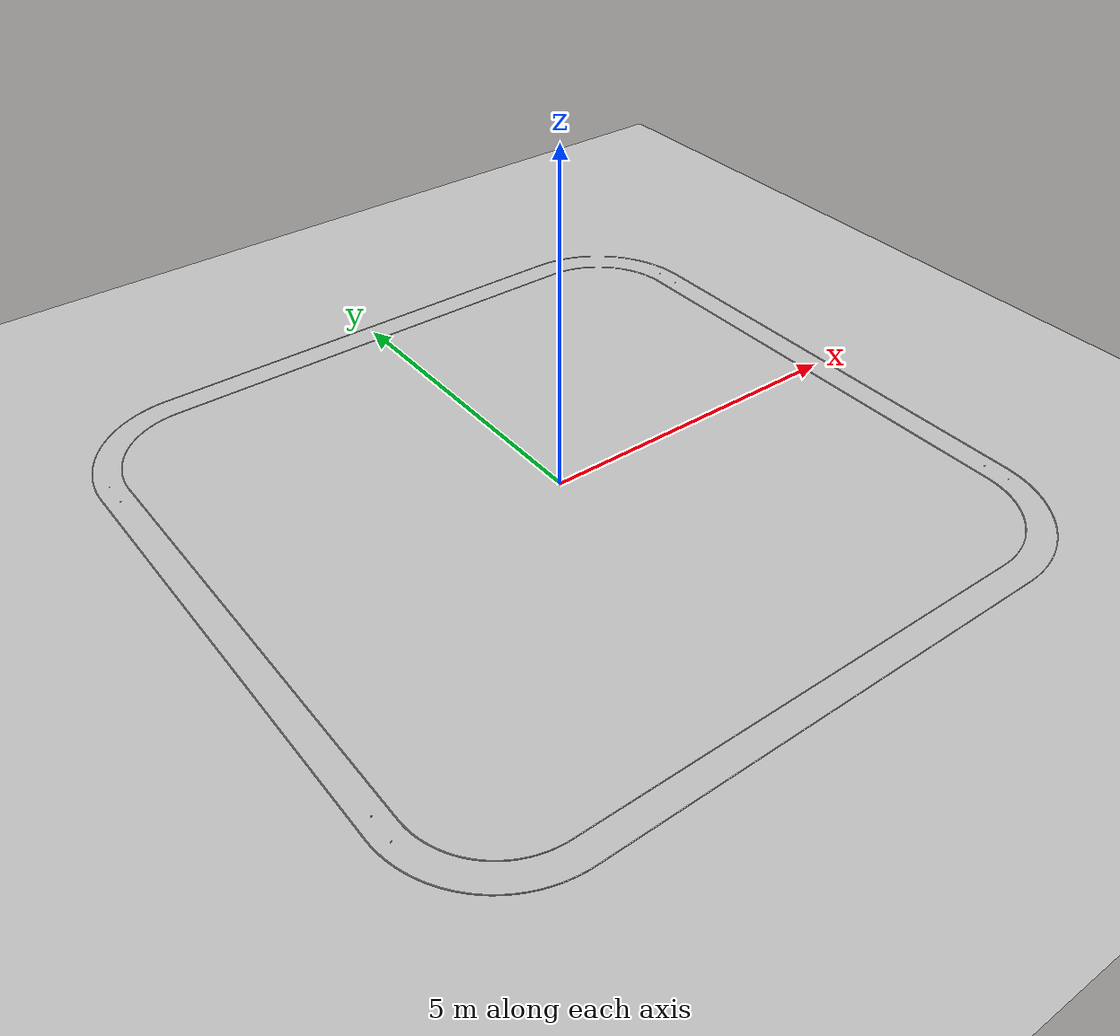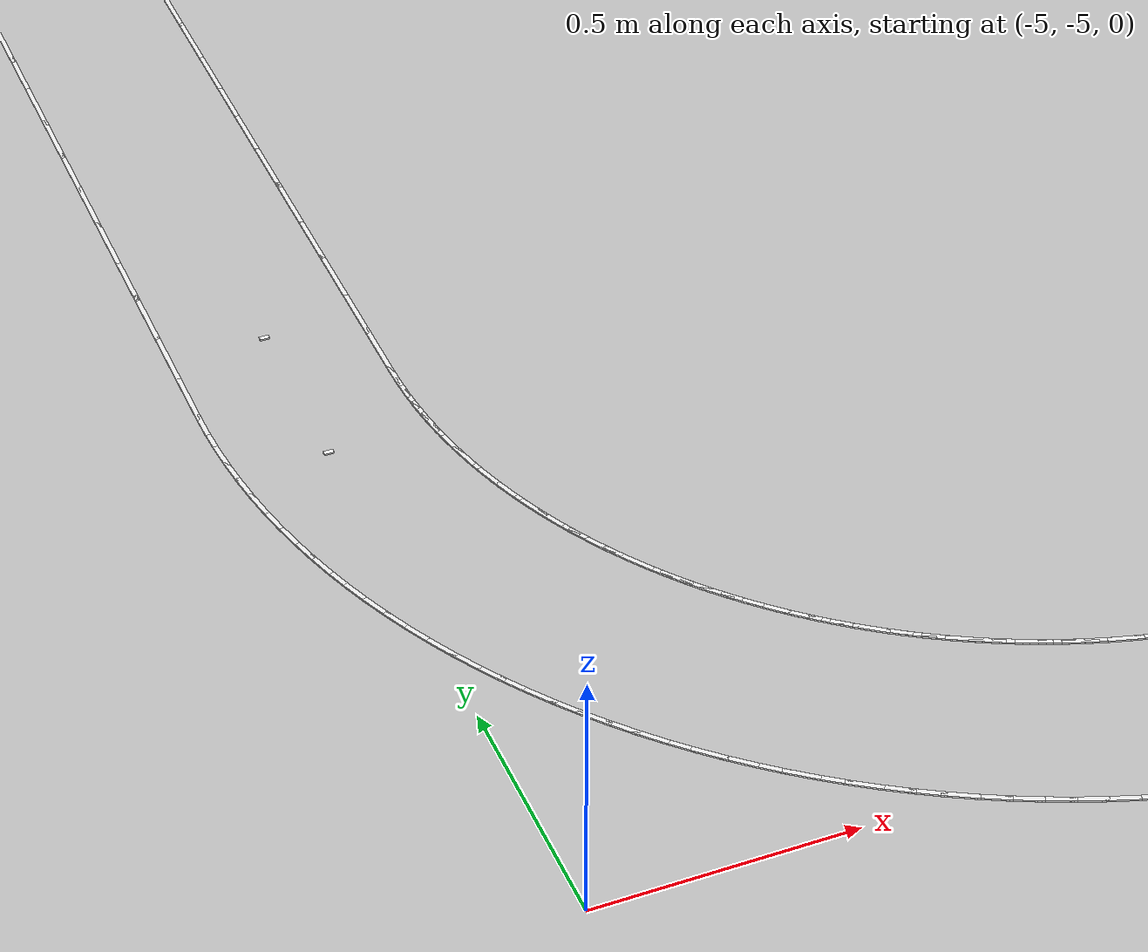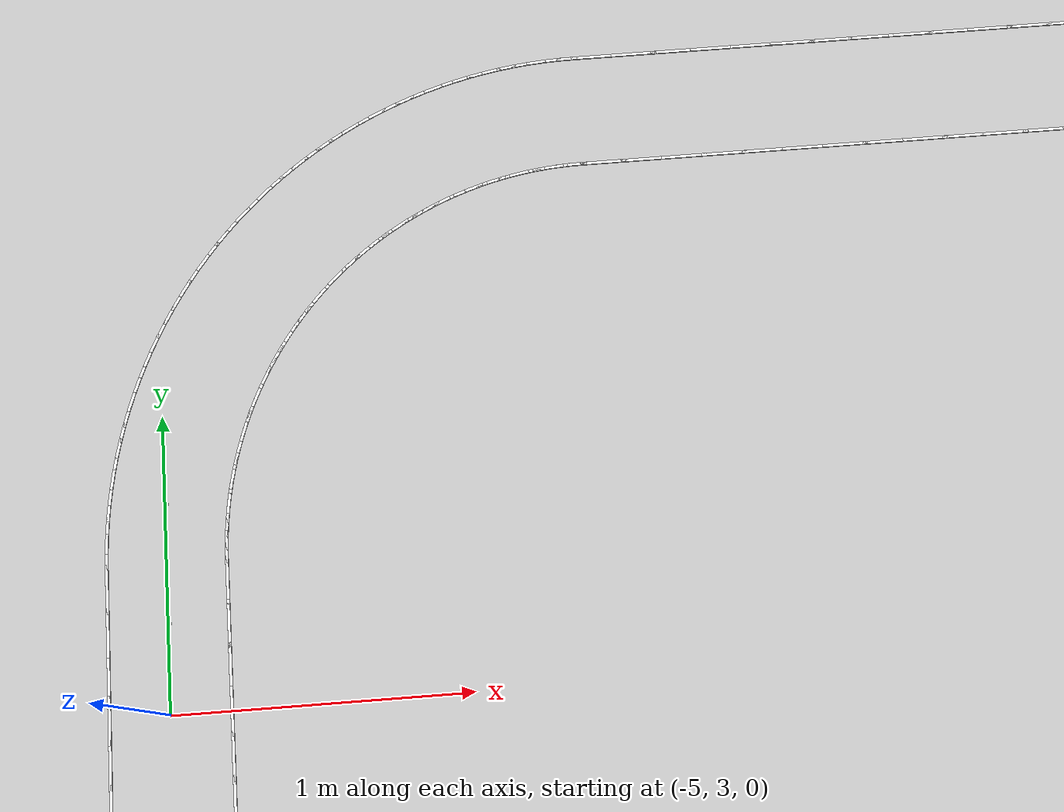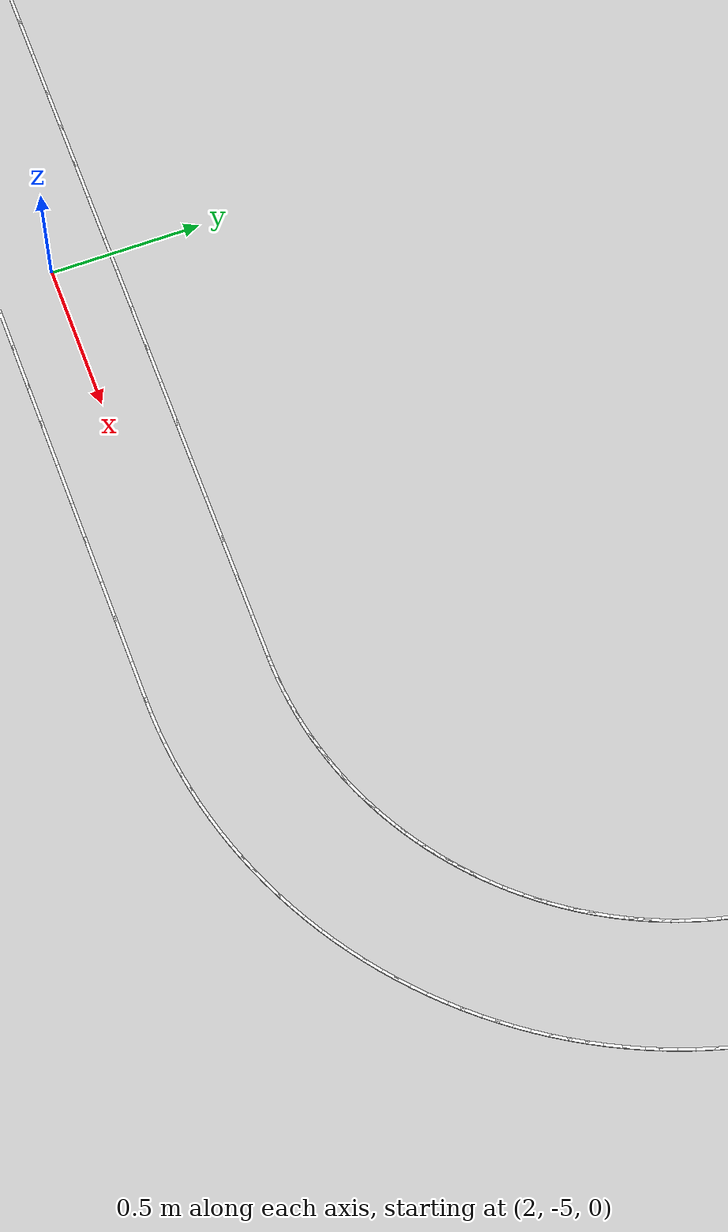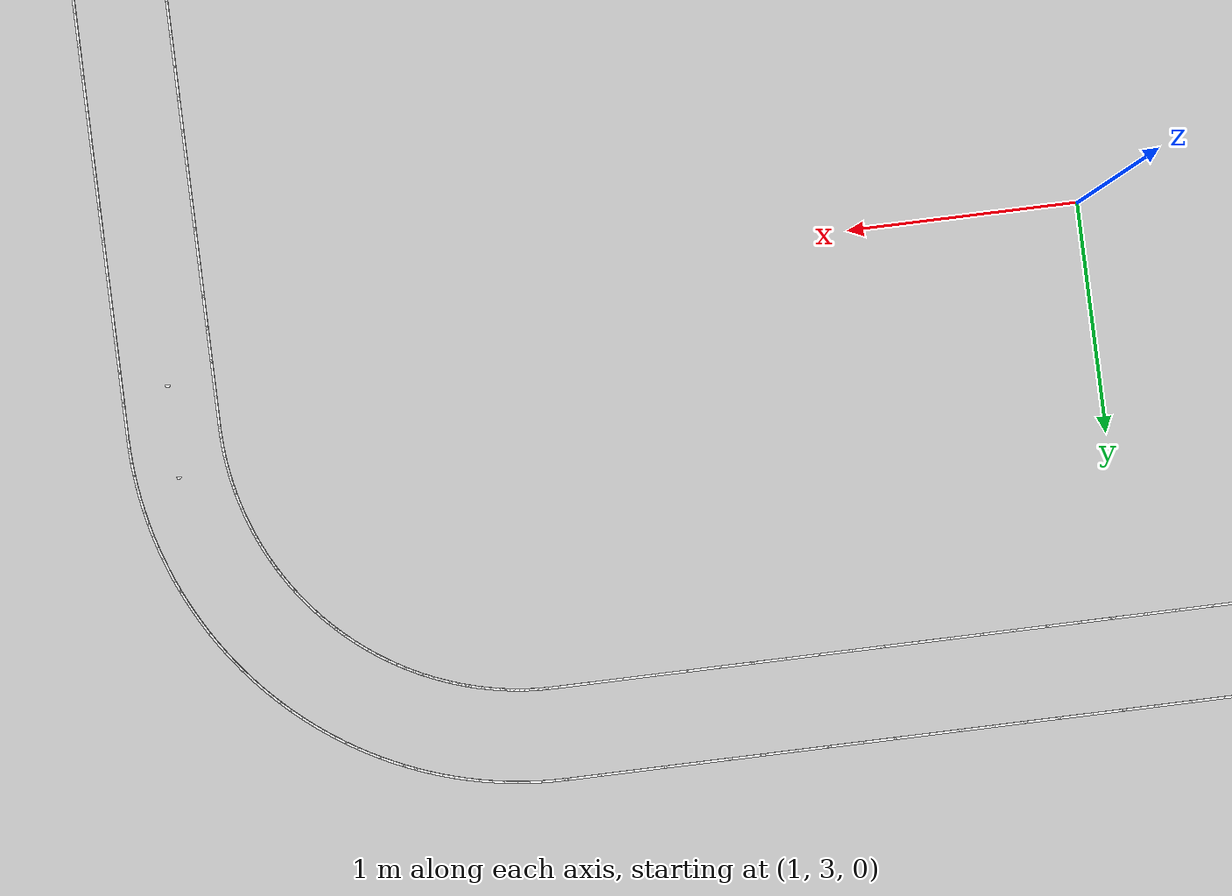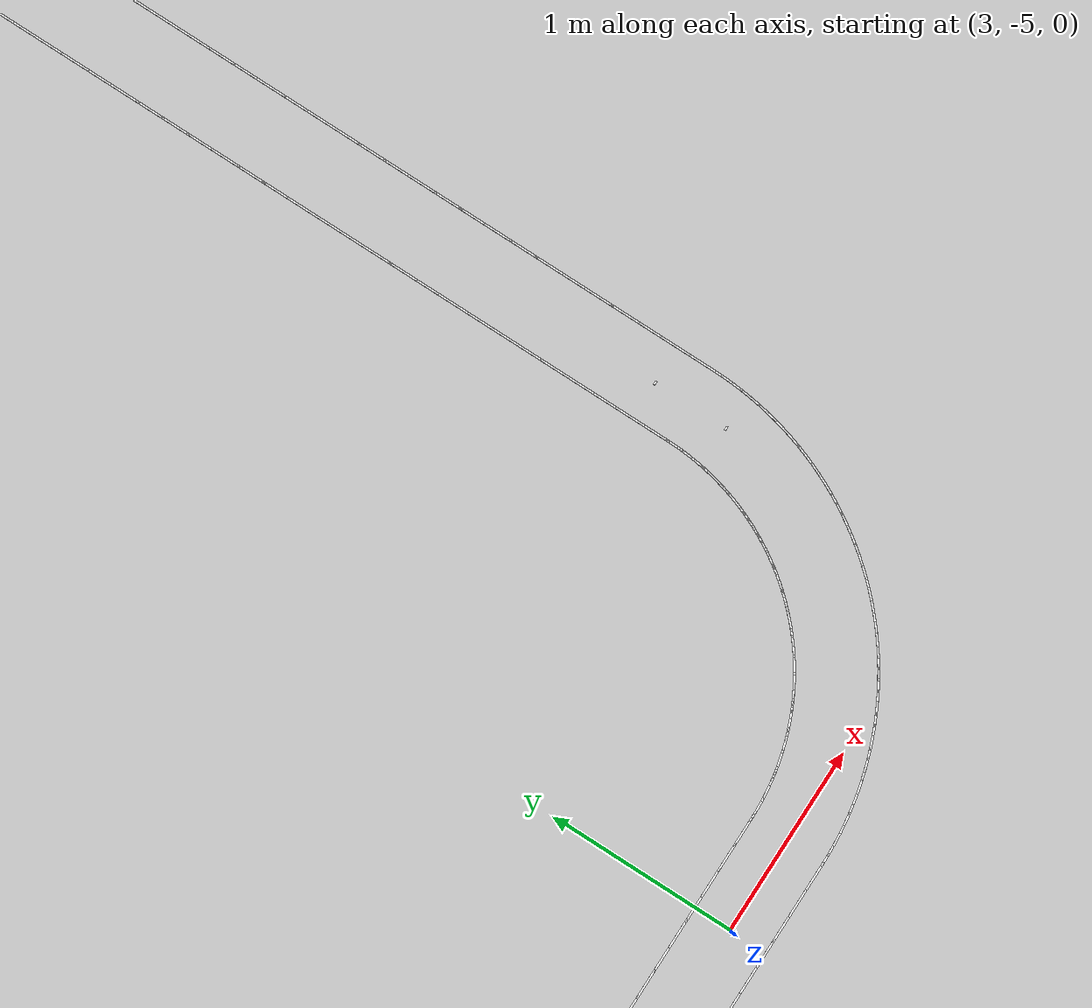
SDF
<sdf version="1.7">
 <world name="default">
  <light name="sun" type="directional">
   <pose>0 0 10 0 -0 0</pose>
   <diffuse>0.8 0.8 0.8 1</diffuse>
   <specular>0.2 0.2 0.2 1</specular>
   <attenuation>
    <range>1000</range>
    <constant>0.9</constant>
    <linear>0.01</linear>
    <quadratic>0.001</quadratic>
   </attenuation>
   <direction>-0.5 0.1 -0.9</direction>
   <spot><inner_angle>0</inner_angle><outer_angle>0</outer_angle><falloff>0</falloff></spot>
  </light>
  <model name="ground_plane">
   <static>1</static>
   <link name="link">
    <collision name="collision">
     <geometry><plane><normal>0 0 1</normal><size>100 100</size></plane></geometry>
     <surface>
      <contact><collide_bitmask>65535</collide_bitmask></contact>
      <friction><ode><mu>100</mu><mu2>50</mu2></ode></friction>
     </surface>
    </collision>
    <visual name="visual">
     <cast_shadows>0</cast_shadows>
     <geometry><plane><normal>0 0 1</normal><size>100 100</size></plane></geometry>
     <material>
      <script><uri>file://media/materials/scripts/gazebo.material</uri><name>Gazebo/Grey</name></script>
     </material>
    </visual>
   </link>
  </model>
  <gravity>0 0 -9.8</gravity>
  <magnetic_field>6e-06 2.3e-05 -4.2e-05</magnetic_field>
  <atmosphere type="adiabatic"/>
  <physics type="ode">
   <max_step_size>0.001</max_step_size>
   <real_time_factor>1</real_time_factor>
   <real_time_update_rate>1000</real_time_update_rate>
  </physics>
  <scene><ambient>0.4 0.4 0.4 1</ambient><background>0.7 0.7 0.7 1</background><shadows>1</shadows></scene>
  <spherical_coordinates>
   <surface_model>EARTH_WGS84</surface_model>
   <latitude_deg>0</latitude_deg>
   <longitude_deg>0</longitude_deg>
   <elevation>0</elevation>
   <heading_deg>0</heading_deg>
  </spherical_coordinates>
  <model name="lane_line_left_0">
   <static>1</static>
   <link name="link">
    <pose>0 0 -0.004 0 -0 0</pose>
    <visual name="visual">
     <geometry><box><size>0.1629 0.01 0.01</size></box></geometry>
     <material><ambient>1 1 1 1</ambient><diffuse>1 1 1 1</diffuse></material>
    </visual>
    <collision name="collision"><geometry><box><size>0.1629 0.01 0.01</size></box></geometry></collision>
   </link>
   <pose>-3.42857 -4.8 0 0 -0 0</pose>
  </model>
  <model name="lane_line_right_0">
   <static>1</static>
   <link name="link">
    <pose>0 0 -0.004 0 -0 0</pose>
    <visual name="visual">
     <geometry><box><size>0.1629 0.01 0.01</size></box></geometry>
     <material><ambient>1 1 1 1</ambient><diffuse>1 1 1 1</diffuse></material>
    </visual>
    <collision name="collision"><geometry><box><size>0.1629 0.01 0.01</size></box></geometry></collision>
   </link>
   <pose>-3.42857 -5.2 0 0 -0 0</pose>
  </model>
  <model name="lane_line_left_1">
   <static>1</static>
   <link name="link">
    <pose>0 0 -0.004 0 -0 0</pose>
    <visual name="visual">
     <geometry><box><size>0.1629 0.01 0.01</size></box></geometry>
     <material><ambient>1 1 1 1</ambient><diffuse>1 1 1 1</diffuse></material>
    </visual>
    <collision name="collision"><geometry><box><size>0.1629 0.01 0.01</size></box></geometry></collision>
   </link>
   <pose>-3.28571 -4.8 0 0 -0 0</pose>
  </model>
  <model name="lane_line_right_1">
   <static>1</static>
   <link name="link">
    <pose>0 0 -0.004 0 -0 0</pose>
    <visual name="visual">
     <geometry><box><size>0.1629 0.01 0.01</size></box></geometry>
     <material><ambient>1 1 1 1</ambient><diffuse>1 1 1 1</diffuse></material>
    </visual>
    <collision name="collision"><geometry><box><size>0.1629 0.01 0.01</size></box></geometry></collision>
   </link>
   <pose>-3.28571 -5.2 0 0 -0 0</pose>
  </model>
  <model name="lane_line_left_2">
   <static>1</static>
   <link name="link">
    <pose>0 0 -0.004 0 -0 0</pose>
    <visual name="visual">
     <geometry><box><size>0.1629 0.01 0.01</size></box></geometry>
     <material><ambient>1 1 1 1</ambient><diffuse>1 1 1 1</diffuse></material>
    </visual>
    <collision name="collision"><geometry><box><size>0.1629 0.01 0.01</size></box></geometry></collision>
   </link>
   <pose>-3.14286 -4.8 0 0 -0 0</pose>
  </model>
  <model name="lane_line_right_2">
   <static>1</static>
   <link name="link">
    <pose>0 0 -0.004 0 -0 0</pose>
    <visual name="visual">
     <geometry><box><size>0.1629 0.01 0.01</size></box></geometry>
     <material><ambient>1 1 1 1</ambient><diffuse>1 1 1 1</diffuse></material>
    </visual>
    <collision name="collision"><geometry><box><size>0.1629 0.01 0.01</size></box></geometry></collision>
   </link>
   <pose>-3.14286 -5.2 0 0 -0 0</pose>
  </model>
  <model name="lane_line_left_3">
   <static>1</static>
   <link name="link">
    <pose>0 0 -0.004 0 -0 0</pose>
    <visual name="visual">
     <geometry><box><size>0.1629 0.01 0.01</size></box></geometry>
     <material><ambient>1 1 1 1</ambient><diffuse>1 1 1 1</diffuse></material>
    </visual>
    <collision name="collision"><geometry><box><size>0.1629 0.01 0.01</size></box></geometry></collision>
   </link>
   <pose>-3 -4.8 0 0 -0 0</pose>
  </model>
  <model name="lane_line_right_3">
   <static>1</static>
   <link name="link">
    <pose>0 0 -0.004 0 -0 0</pose>
    <visual name="visual">
     <geometry><box><size>0.1629 0.01 0.01</size></box></geometry>
     <material><ambient>1 1 1 1</ambient><diffuse>1 1 1 1</diffuse></material>
    </visual>
    <collision name="collision"><geometry><box><size>0.1629 0.01 0.01</size></box></geometry></collision>
   </link>
   <pose>-3 -5.2 0 0 -0 0</pose>
  </model>
  <model name="lane_line_left_4">
   <static>1</static>
   <link name="link">
    <pose>0 0 -0.004 0 -0 0</pose>
    <visual name="visual">
     <geometry><box><size>0.1629 0.01 0.01</size></box></geometry>
     <material><ambient>1 1 1 1</ambient><diffuse>1 1 1 1</diffuse></material>
    </visual>
    <collision name="collision"><geometry><box><size>0.1629 0.01 0.01</size></box></geometry></collision>
   </link>
   <pose>-2.85714 -4.8 0 0 -0 0</pose>
  </model>
  <model name="lane_line_right_4">
   <static>1</static>
   <link name="link">
    <pose>0 0 -0.004 0 -0 0</pose>
    <visual name="visual">
     <geometry><box><size>0.1629 0.01 0.01</size></box></geometry>
     <material><ambient>1 1 1 1</ambient><diffuse>1 1 1 1</diffuse></material>
    </visual>
    <collision name="collision"><geometry><box><size>0.1629 0.01 0.01</size></box></geometry></collision>
   </link>
   <pose>-2.85714 -5.2 0 0 -0 0</pose>
  </model>
  <model name="lane_line_left_5">
   <static>1</static>
   <link name="link">
    <pose>0 0 -0.004 0 -0 0</pose>
    <visual name="visual">
     <geometry><box><size>0.1629 0.01 0.01</size></box></geometry>
     <material><ambient>1 1 1 1</ambient><diffuse>1 1 1 1</diffuse></material>
    </visual>
    <collision name="collision"><geometry><box><size>0.1629 0.01 0.01</size></box></geometry></collision>
   </link>
   <pose>-2.71429 -4.8 0 0 -0 0</pose>
  </model>
  <model name="lane_line_right_5">
   <static>1</static>
   <link name="link">
    <pose>0 0 -0.004 0 -0 0</pose>
    <visual name="visual">
     <geometry><box><size>0.1629 0.01 0.01</size></box></geometry>
     <material><ambient>1 1 1 1</ambient><diffuse>1 1 1 1</diffuse></material>
    </visual>
    <collision name="collision"><geometry><box><size>0.1629 0.01 0.01</size></box></geometry></collision>
   </link>
   <pose>-2.71429 -5.2 0 0 -0 0</pose>
  </model>
  <model name="lane_line_left_6">
   <static>1</static>
   <link name="link">
    <pose>0 0 -0.004 0 -0 0</pose>
    <visual name="visual">
     <geometry><box><size>0.1629 0.01 0.01</size></box></geometry>
     <material><ambient>1 1 1 1</ambient><diffuse>1 1 1 1</diffuse></material>
    </visual>
    <collision name="collision"><geometry><box><size>0.1629 0.01 0.01</size></box></geometry></collision>
   </link>
   <pose>-2.57143 -4.8 0 0 -0 0</pose>
  </model>
  <model name="lane_line_right_6">
   <static>1</static>
   <link name="link">
    <pose>0 0 -0.004 0 -0 0</pose>
    <visual name="visual">
     <geometry><box><size>0.1629 0.01 0.01</size></box></geometry>
     <material><ambient>1 1 1 1</ambient><diffuse>1 1 1 1</diffuse></material>
    </visual>
    <collision name="collision"><geometry><box><size>0.1629 0.01 0.01</size></box></geometry></collision>
   </link>
   <pose>-2.57143 -5.2 0 0 -0 0</pose>
  </model>
  <model name="lane_line_left_7">
   <static>1</static>
   <link name="link">
    <pose>0 0 -0.004 0 -0 0</pose>
    <visual name="visual">
     <geometry><box><size>0.1629 0.01 0.01</size></box></geometry>
     <material><ambient>1 1 1 1</ambient><diffuse>1 1 1 1</diffuse></material>
    </visual>
    <collision name="collision"><geometry><box><size>0.1629 0.01 0.01</size></box></geometry></collision>
   </link>
   <pose>-2.42857 -4.8 0 0 -0 0</pose>
  </model>
  <model name="lane_line_right_7">
   <static>1</static>
   <link name="link">
    <pose>0 0 -0.004 0 -0 0</pose>
    <visual name="visual">
     <geometry><box><size>0.1629 0.01 0.01</size></box></geometry>
     <material><ambient>1 1 1 1</ambient><diffuse>1 1 1 1</diffuse></material>
    </visual>
    <collision name="collision"><geometry><box><size>0.1629 0.01 0.01</size></box></geometry></collision>
   </link>
   <pose>-2.42857 -5.2 0 0 -0 0</pose>
  </model>
  <model name="lane_line_left_8">
   <static>1</static>
   <link name="link">
    <pose>0 0 -0.004 0 -0 0</pose>
    <visual name="visual">
     <geometry><box><size>0.1629 0.01 0.01</size></box></geometry>
     <material><ambient>1 1 1 1</ambient><diffuse>1 1 1 1</diffuse></material>
    </visual>
    <collision name="collision"><geometry><box><size>0.1629 0.01 0.01</size></box></geometry></collision>
   </link>
   <pose>-2.28571 -4.8 0 0 -0 0</pose>
  </model>
  <model name="lane_line_right_8">
   <static>1</static>
   <link name="link">
    <pose>0 0 -0.004 0 -0 0</pose>
    <visual name="visual">
     <geometry><box><size>0.1629 0.01 0.01</size></box></geometry>
     <material><ambient>1 1 1 1</ambient><diffuse>1 1 1 1</diffuse></material>
    </visual>
    <collision name="collision"><geometry><box><size>0.1629 0.01 0.01</size></box></geometry></collision>
   </link>
   <pose>-2.28571 -5.2 0 0 -0 0</pose>
  </model>
  <model name="lane_line_left_9">
   <static>1</static>
   <link name="link">
    <pose>0 0 -0.004 0 -0 0</pose>
    <visual name="visual">
     <geometry><box><size>0.1629 0.01 0.01</size></box></geometry>
     <material><ambient>1 1 1 1</ambient><diffuse>1 1 1 1</diffuse></material>
    </visual>
    <collision name="collision"><geometry><box><size>0.1629 0.01 0.01</size></box></geometry></collision>
   </link>
   <pose>-2.14286 -4.8 0 0 -0 0</pose>
  </model>
  <model name="lane_line_right_9">
   <static>1</static>
   <link name="link">
    <pose>0 0 -0.004 0 -0 0</pose>
    <visual name="visual">
     <geometry><box><size>0.1629 0.01 0.01</size></box></geometry>
     <material><ambient>1 1 1 1</ambient><diffuse>1 1 1 1</diffuse></material>
    </visual>
    <collision name="collision"><geometry><box><size>0.1629 0.01 0.01</size></box></geometry></collision>
   </link>
   <pose>-2.14286 -5.2 0 0 -0 0</pose>
  </model>
  <model name="lane_line_left_10">
   <static>1</static>
   <link name="link">
    <pose>0 0 -0.004 0 -0 0</pose>
    <visual name="visual">
     <geometry><box><size>0.1629 0.01 0.01</size></box></geometry>
     <material><ambient>1 1 1 1</ambient><diffuse>1 1 1 1</diffuse></material>
    </visual>
    <collision name="collision"><geometry><box><size>0.1629 0.01 0.01</size></box></geometry></collision>
   </link>
   <pose>-2 -4.8 0 0 -0 0</pose>
  </model>
  <model name="lane_line_right_10">
   <static>1</static>
   <link name="link">
    <pose>0 0 -0.004 0 -0 0</pose>
    <visual name="visual">
     <geometry><box><size>0.1629 0.01 0.01</size></box></geometry>
     <material><ambient>1 1 1 1</ambient><diffuse>1 1 1 1</diffuse></material>
    </visual>
    <collision name="collision"><geometry><box><size>0.1629 0.01 0.01</size></box></geometry></collision>
   </link>
   <pose>-2 -5.2 0 0 -0 0</pose>
  </model>
  <model name="lane_line_left_11">
   <static>1</static>
   <link name="link">
    <pose>0 0 -0.004 0 -0 0</pose>
    <visual name="visual">
     <geometry><box><size>0.1629 0.01 0.01</size></box></geometry>
     <material><ambient>1 1 1 1</ambient><diffuse>1 1 1 1</diffuse></material>
    </visual>
    <collision name="collision"><geometry><box><size>0.1629 0.01 0.01</size></box></geometry></collision>
   </link>
   <pose>-1.85714 -4.8 0 0 -0 0</pose>
  </model>
  <model name="lane_line_right_11">
   <static>1</static>
   <link name="link">
    <pose>0 0 -0.004 0 -0 0</pose>
    <visual name="visual">
     <geometry><box><size>0.1629 0.01 0.01</size></box></geometry>
     <material><ambient>1 1 1 1</ambient><diffuse>1 1 1 1</diffuse></material>
    </visual>
    <collision name="collision"><geometry><box><size>0.1629 0.01 0.01</size></box></geometry></collision>
   </link>
   <pose>-1.85714 -5.2 0 0 -0 0</pose>
  </model>
  <model name="lane_line_left_12">
   <static>1</static>
   <link name="link">
    <pose>0 0 -0.004 0 -0 0</pose>
    <visual name="visual">
     <geometry><box><size>0.1629 0.01 0.01</size></box></geometry>
     <material><ambient>1 1 1 1</ambient><diffuse>1 1 1 1</diffuse></material>
    </visual>
    <collision name="collision"><geometry><box><size>0.1629 0.01 0.01</size></box></geometry></collision>
   </link>
   <pose>-1.71429 -4.8 0 0 -0 0</pose>
  </model>
  <model name="lane_line_right_12">
   <static>1</static>
   <link name="link">
    <pose>0 0 -0.004 0 -0 0</pose>
    <visual name="visual">
     <geometry><box><size>0.1629 0.01 0.01</size></box></geometry>
     <material><ambient>1 1 1 1</ambient><diffuse>1 1 1 1</diffuse></material>
    </visual>
    <collision name="collision"><geometry><box><size>0.1629 0.01 0.01</size></box></geometry></collision>
   </link>
   <pose>-1.71429 -5.2 0 0 -0 0</pose>
  </model>
  <model name="lane_line_left_13">
   <static>1</static>
   <link name="link">
    <pose>0 0 -0.004 0 -0 0</pose>
    <visual name="visual">
     <geometry><box><size>0.1629 0.01 0.01</size></box></geometry>
     <material><ambient>1 1 1 1</ambient><diffuse>1 1 1 1</diffuse></material>
    </visual>
    <collision name="collision"><geometry><box><size>0.1629 0.01 0.01</size></box></geometry></collision>
   </link>
   <pose>-1.57143 -4.8 0 0 -0 0</pose>
  </model>
  <model name="lane_line_right_13">
   <static>1</static>
   <link name="link">
    <pose>0 0 -0.004 0 -0 0</pose>
    <visual name="visual">
     <geometry><box><size>0.1629 0.01 0.01</size></box></geometry>
     <material><ambient>1 1 1 1</ambient><diffuse>1 1 1 1</diffuse></material>
    </visual>
    <collision name="collision"><geometry><box><size>0.1629 0.01 0.01</size></box></geometry></collision>
   </link>
   <pose>-1.57143 -5.2 0 0 -0 0</pose>
  </model>
  <model name="lane_line_left_14">
   <static>1</static>
   <link name="link">
    <pose>0 0 -0.004 0 -0 0</pose>
    <visual name="visual">
     <geometry><box><size>0.1629 0.01 0.01</size></box></geometry>
     <material><ambient>1 1 1 1</ambient><diffuse>1 1 1 1</diffuse></material>
    </visual>
    <collision name="collision"><geometry><box><size>0.1629 0.01 0.01</size></box></geometry></collision>
   </link>
   <pose>-1.42857 -4.8 0 0 -0 0</pose>
  </model>
  <model name="lane_line_right_14">
   <static>1</static>
   <link name="link">
    <pose>0 0 -0.004 0 -0 0</pose>
    <visual name="visual">
     <geometry><box><size>0.1629 0.01 0.01</size></box></geometry>
     <material><ambient>1 1 1 1</ambient><diffuse>1 1 1 1</diffuse></material>
    </visual>
    <collision name="collision"><geometry><box><size>0.1629 0.01 0.01</size></box></geometry></collision>
   </link>
   <pose>-1.42857 -5.2 0 0 -0 0</pose>
  </model>
  <model name="lane_line_left_15">
   <static>1</static>
   <link name="link">
    <pose>0 0 -0.004 0 -0 0</pose>
    <visual name="visual">
     <geometry><box><size>0.1629 0.01 0.01</size></box></geometry>
     <material><ambient>1 1 1 1</ambient><diffuse>1 1 1 1</diffuse></material>
    </visual>
    <collision name="collision"><geometry><box><size>0.1629 0.01 0.01</size></box></geometry></collision>
   </link>
   <pose>-1.28571 -4.8 0 0 -0 0</pose>
  </model>
  <model name="lane_line_right_15">
   <static>1</static>
   <link name="link">
    <pose>0 0 -0.004 0 -0 0</pose>
    <visual name="visual">
     <geometry><box><size>0.1629 0.01 0.01</size></box></geometry>
     <material><ambient>1 1 1 1</ambient><diffuse>1 1 1 1</diffuse></material>
    </visual>
    <collision name="collision"><geometry><box><size>0.1629 0.01 0.01</size></box></geometry></collision>
   </link>
   <pose>-1.28571 -5.2 0 0 -0 0</pose>
  </model>
  <model name="lane_line_left_16">
   <static>1</static>
   <link name="link">
    <pose>0 0 -0.004 0 -0 0</pose>
    <visual name="visual">
     <geometry><box><size>0.1629 0.01 0.01</size></box></geometry>
     <material><ambient>1 1 1 1</ambient><diffuse>1 1 1 1</diffuse></material>
    </visual>
    <collision name="collision"><geometry><box><size>0.1629 0.01 0.01</size></box></geometry></collision>
   </link>
   <pose>-1.14286 -4.8 0 0 -0 0</pose>
  </model>
  <model name="lane_line_right_16">
   <static>1</static>
   <link name="link">
    <pose>0 0 -0.004 0 -0 0</pose>
    <visual name="visual">
     <geometry><box><size>0.1629 0.01 0.01</size></box></geometry>
     <material><ambient>1 1 1 1</ambient><diffuse>1 1 1 1</diffuse></material>
    </visual>
    <collision name="collision"><geometry><box><size>0.1629 0.01 0.01</size></box></geometry></collision>
   </link>
   <pose>-1.14286 -5.2 0 0 -0 0</pose>
  </model>
  <model name="lane_line_left_17">
   <static>1</static>
   <link name="link">
    <pose>0 0 -0.004 0 -0 0</pose>
    <visual name="visual">
     <geometry><box><size>0.1629 0.01 0.01</size></box></geometry>
     <material><ambient>1 1 1 1</ambient><diffuse>1 1 1 1</diffuse></material>
    </visual>
    <collision name="collision"><geometry><box><size>0.1629 0.01 0.01</size></box></geometry></collision>
   </link>
   <pose>-1 -4.8 0 0 -0 0</pose>
  </model>
  <model name="lane_line_right_17">
   <static>1</static>
   <link name="link">
    <pose>0 0 -0.004 0 -0 0</pose>
    <visual name="visual">
     <geometry><box><size>0.1629 0.01 0.01</size></box></geometry>
     <material><ambient>1 1 1 1</ambient><diffuse>1 1 1 1</diffuse></material>
    </visual>
    <collision name="collision"><geometry><box><size>0.1629 0.01 0.01</size></box></geometry></collision>
   </link>
   <pose>-1 -5.2 0 0 -0 0</pose>
  </model>
  <model name="lane_line_left_18">
   <static>1</static>
   <link name="link">
    <pose>0 0 -0.004 0 -0 0</pose>
    <visual name="visual">
     <geometry><box><size>0.1629 0.01 0.01</size></box></geometry>
     <material><ambient>1 1 1 1</ambient><diffuse>1 1 1 1</diffuse></material>
    </visual>
    <collision name="collision"><geometry><box><size>0.1629 0.01 0.01</size></box></geometry></collision>
   </link>
   <pose>-0.857143 -4.8 0 0 -0 0</pose>
  </model>
  <model name="lane_line_right_18">
   <static>1</static>
   <link name="link">
    <pose>0 0 -0.004 0 -0 0</pose>
    <visual name="visual">
     <geometry><box><size>0.1629 0.01 0.01</size></box></geometry>
     <material><ambient>1 1 1 1</ambient><diffuse>1 1 1 1</diffuse></material>
    </visual>
    <collision name="collision"><geometry><box><size>0.1629 0.01 0.01</size></box></geometry></collision>
   </link>
   <pose>-0.857143 -5.2 0 0 -0 0</pose>
  </model>
  <model name="lane_line_left_19">
   <static>1</static>
   <link name="link">
    <pose>0 0 -0.004 0 -0 0</pose>
    <visual name="visual">
     <geometry><box><size>0.1629 0.01 0.01</size></box></geometry>
     <material><ambient>1 1 1 1</ambient><diffuse>1 1 1 1</diffuse></material>
    </visual>
    <collision name="collision"><geometry><box><size>0.1629 0.01 0.01</size></box></geometry></collision>
   </link>
   <pose>-0.714286 -4.8 0 0 -0 0</pose>
  </model>
  <model name="lane_line_right_19">
   <static>1</static>
   <link name="link">
    <pose>0 0 -0.004 0 -0 0</pose>
    <visual name="visual">
     <geometry><box><size>0.1629 0.01 0.01</size></box></geometry>
     <material><ambient>1 1 1 1</ambient><diffuse>1 1 1 1</diffuse></material>
    </visual>
    <collision name="collision"><geometry><box><size>0.1629 0.01 0.01</size></box></geometry></collision>
   </link>
   <pose>-0.714286 -5.2 0 0 -0 0</pose>
  </model>
  <model name="lane_line_left_20">
   <static>1</static>
   <link name="link">
    <pose>0 0 -0.004 0 -0 0</pose>
    <visual name="visual">
     <geometry><box><size>0.1629 0.01 0.01</size></box></geometry>
     <material><ambient>1 1 1 1</ambient><diffuse>1 1 1 1</diffuse></material>
    </visual>
    <collision name="collision"><geometry><box><size>0.1629 0.01 0.01</size></box></geometry></collision>
   </link>
   <pose>-0.571429 -4.8 0 0 -0 0</pose>
  </model>
  <model name="lane_line_right_20">
   <static>1</static>
   <link name="link">
    <pose>0 0 -0.004 0 -0 0</pose>
    <visual name="visual">
     <geometry><box><size>0.1629 0.01 0.01</size></box></geometry>
     <material><ambient>1 1 1 1</ambient><diffuse>1 1 1 1</diffuse></material>
    </visual>
    <collision name="collision"><geometry><box><size>0.1629 0.01 0.01</size></box></geometry></collision>
   </link>
   <pose>-0.571429 -5.2 0 0 -0 0</pose>
  </model>
  <model name="lane_line_left_21">
   <static>1</static>
   <link name="link">
    <pose>0 0 -0.004 0 -0 0</pose>
    <visual name="visual">
     <geometry><box><size>0.1629 0.01 0.01</size></box></geometry>
     <material><ambient>1 1 1 1</ambient><diffuse>1 1 1 1</diffuse></material>
    </visual>
    <collision name="collision"><geometry><box><size>0.1629 0.01 0.01</size></box></geometry></collision>
   </link>
   <pose>-0.428571 -4.8 0 0 -0 0</pose>
  </model>
  <model name="lane_line_right_21">
   <static>1</static>
   <link name="link">
    <pose>0 0 -0.004 0 -0 0</pose>
    <visual name="visual">
     <geometry><box><size>0.1629 0.01 0.01</size></box></geometry>
     <material><ambient>1 1 1 1</ambient><diffuse>1 1 1 1</diffuse></material>
    </visual>
    <collision name="collision"><geometry><box><size>0.1629 0.01 0.01</size></box></geometry></collision>
   </link>
   <pose>-0.428571 -5.2 0 0 -0 0</pose>
  </model>
  <model name="lane_line_left_22">
   <static>1</static>
   <link name="link">
    <pose>0 0 -0.004 0 -0 0</pose>
    <visual name="visual">
     <geometry><box><size>0.1629 0.01 0.01</size></box></geometry>
     <material><ambient>1 1 1 1</ambient><diffuse>1 1 1 1</diffuse></material>
    </visual>
    <collision name="collision"><geometry><box><size>0.1629 0.01 0.01</size></box></geometry></collision>
   </link>
   <pose>-0.285714 -4.8 0 0 -0 0</pose>
  </model>
  <model name="lane_line_right_22">
   <static>1</static>
   <link name="link">
    <pose>0 0 -0.004 0 -0 0</pose>
    <visual name="visual">
     <geometry><box><size>0.1629 0.01 0.01</size></box></geometry>
     <material><ambient>1 1 1 1</ambient><diffuse>1 1 1 1</diffuse></material>
    </visual>
    <collision name="collision"><geometry><box><size>0.1629 0.01 0.01</size></box></geometry></collision>
   </link>
   <pose>-0.285714 -5.2 0 0 -0 0</pose>
  </model>
  <model name="lane_line_left_23">
   <static>1</static>
   <link name="link">
    <pose>0 0 -0.004 0 -0 0</pose>
    <visual name="visual">
     <geometry><box><size>0.1629 0.01 0.01</size></box></geometry>
     <material><ambient>1 1 1 1</ambient><diffuse>1 1 1 1</diffuse></material>
    </visual>
    <collision name="collision"><geometry><box><size>0.1629 0.01 0.01</size></box></geometry></collision>
   </link>
   <pose>-0.142857 -4.8 0 0 -0 0</pose>
  </model>
  <model name="lane_line_right_23">
   <static>1</static>
   <link name="link">
    <pose>0 0 -0.004 0 -0 0</pose>
    <visual name="visual">
     <geometry><box><size>0.1629 0.01 0.01</size></box></geometry>
     <material><ambient>1 1 1 1</ambient><diffuse>1 1 1 1</diffuse></material>
    </visual>
    <collision name="collision"><geometry><box><size>0.1629 0.01 0.01</size></box></geometry></collision>
   </link>
   <pose>-0.142857 -5.2 0 0 -0 0</pose>
  </model>
  <model name="lane_line_left_24">
   <static>1</static>
   <link name="link">
    <pose>0 0 -0.004 0 -0 0</pose>
    <visual name="visual">
     <geometry><box><size>0.1629 0.01 0.01</size></box></geometry>
     <material><ambient>1 1 1 1</ambient><diffuse>1 1 1 1</diffuse></material>
    </visual>
    <collision name="collision"><geometry><box><size>0.1629 0.01 0.01</size></box></geometry></collision>
   </link>
   <pose>0 -4.8 0 0 -0 0</pose>
  </model>
  <model name="lane_line_right_24">
   <static>1</static>
   <link name="link">
    <pose>0 0 -0.004 0 -0 0</pose>
    <visual name="visual">
     <geometry><box><size>0.1629 0.01 0.01</size></box></geometry>
     <material><ambient>1 1 1 1</ambient><diffuse>1 1 1 1</diffuse></material>
    </visual>
    <collision name="collision"><geometry><box><size>0.1629 0.01 0.01</size></box></geometry></collision>
   </link>
   <pose>0 -5.2 0 0 -0 0</pose>
  </model>
  <model name="lane_line_left_25">
   <static>1</static>
   <link name="link">
    <pose>0 0 -0.004 0 -0 0</pose>
    <visual name="visual">
     <geometry><box><size>0.1629 0.01 0.01</size></box></geometry>
     <material><ambient>1 1 1 1</ambient><diffuse>1 1 1 1</diffuse></material>
    </visual>
    <collision name="collision"><geometry><box><size>0.1629 0.01 0.01</size></box></geometry></collision>
   </link>
   <pose>0.142857 -4.8 0 0 -0 0</pose>
  </model>
  <model name="lane_line_right_25">
   <static>1</static>
   <link name="link">
    <pose>0 0 -0.004 0 -0 0</pose>
    <visual name="visual">
     <geometry><box><size>0.1629 0.01 0.01</size></box></geometry>
     <material><ambient>1 1 1 1</ambient><diffuse>1 1 1 1</diffuse></material>
    </visual>
    <collision name="collision"><geometry><box><size>0.1629 0.01 0.01</size></box></geometry></collision>
   </link>
   <pose>0.142857 -5.2 0 0 -0 0</pose>
  </model>
  <model name="lane_line_left_26">
   <static>1</static>
   <link name="link">
    <pose>0 0 -0.004 0 -0 0</pose>
    <visual name="visual">
     <geometry><box><size>0.1629 0.01 0.01</size></box></geometry>
     <material><ambient>1 1 1 1</ambient><diffuse>1 1 1 1</diffuse></material>
    </visual>
    <collision name="collision"><geometry><box><size>0.1629 0.01 0.01</size></box></geometry></collision>
   </link>
   <pose>0.285714 -4.8 0 0 -0 0</pose>
  </model>
  <model name="lane_line_right_26">
   <static>1</static>
   <link name="link">
    <pose>0 0 -0.004 0 -0 0</pose>
    <visual name="visual">
     <geometry><box><size>0.1629 0.01 0.01</size></box></geometry>
     <material><ambient>1 1 1 1</ambient><diffuse>1 1 1 1</diffuse></material>
    </visual>
    <collision name="collision"><geometry><box><size>0.1629 0.01 0.01</size></box></geometry></collision>
   </link>
   <pose>0.285714 -5.2 0 0 -0 0</pose>
  </model>
  <model name="lane_line_left_27">
   <static>1</static>
   <link name="link">
    <pose>0 0 -0.004 0 -0 0</pose>
    <visual name="visual">
     <geometry><box><size>0.1629 0.01 0.01</size></box></geometry>
     <material><ambient>1 1 1 1</ambient><diffuse>1 1 1 1</diffuse></material>
    </visual>
    <collision name="collision"><geometry><box><size>0.1629 0.01 0.01</size></box></geometry></collision>
   </link>
   <pose>0.428571 -4.8 0 0 -0 0</pose>
  </model>
  <model name="lane_line_right_27">
   <static>1</static>
   <link name="link">
    <pose>0 0 -0.004 0 -0 0</pose>
    <visual name="visual">
     <geometry><box><size>0.1629 0.01 0.01</size></box></geometry>
     <material><ambient>1 1 1 1</ambient><diffuse>1 1 1 1</diffuse></material>
    </visual>
    <collision name="collision"><geometry><box><size>0.1629 0.01 0.01</size></box></geometry></collision>
   </link>
   <pose>0.428571 -5.2 0 0 -0 0</pose>
  </model>
  <model name="lane_line_left_28">
   <static>1</static>
   <link name="link">
    <pose>0 0 -0.004 0 -0 0</pose>
    <visual name="visual">
     <geometry><box><size>0.1629 0.01 0.01</size></box></geometry>
     <material><ambient>1 1 1 1</ambient><diffuse>1 1 1 1</diffuse></material>
    </visual>
    <collision name="collision"><geometry><box><size>0.1629 0.01 0.01</size></box></geometry></collision>
   </link>
   <pose>0.571429 -4.8 0 0 -0 0</pose>
  </model>
  <model name="lane_line_right_28">
   <static>1</static>
   <link name="link">
    <pose>0 0 -0.004 0 -0 0</pose>
    <visual name="visual">
     <geometry><box><size>0.1629 0.01 0.01</size></box></geometry>
     <material><ambient>1 1 1 1</ambient><diffuse>1 1 1 1</diffuse></material>
    </visual>
    <collision name="collision"><geometry><box><size>0.1629 0.01 0.01</size></box></geometry></collision>
   </link>
   <pose>0.571429 -5.2 0 0 -0 0</pose>
  </model>
  <model name="lane_line_left_29">
   <static>1</static>
   <link name="link">
    <pose>0 0 -0.004 0 -0 0</pose>
    <visual name="visual">
     <geometry><box><size>0.1629 0.01 0.01</size></box></geometry>
     <material><ambient>1 1 1 1</ambient><diffuse>1 1 1 1</diffuse></material>
    </visual>
    <collision name="collision"><geometry><box><size>0.1629 0.01 0.01</size></box></geometry></collision>
   </link>
   <pose>0.714286 -4.8 0 0 -0 0</pose>
  </model>
  <model name="lane_line_right_29">
   <static>1</static>
   <link name="link">
    <pose>0 0 -0.004 0 -0 0</pose>
    <visual name="visual">
     <geometry><box><size>0.1629 0.01 0.01</size></box></geometry>
     <material><ambient>1 1 1 1</ambient><diffuse>1 1 1 1</diffuse></material>
    </visual>
    <collision name="collision"><geometry><box><size>0.1629 0.01 0.01</size></box></geometry></collision>
   </link>
   <pose>0.714286 -5.2 0 0 -0 0</pose>
  </model>
  <model name="lane_line_left_30">
   <static>1</static>
   <link name="link">
    <pose>0 0 -0.004 0 -0 0</pose>
    <visual name="visual">
     <geometry><box><size>0.1629 0.01 0.01</size></box></geometry>
     <material><ambient>1 1 1 1</ambient><diffuse>1 1 1 1</diffuse></material>
    </visual>
    <collision name="collision"><geometry><box><size>0.1629 0.01 0.01</size></box></geometry></collision>
   </link>
   <pose>0.857143 -4.8 0 0 -0 0</pose>
  </model>
  <model name="lane_line_right_30">
   <static>1</static>
   <link name="link">
    <pose>0 0 -0.004 0 -0 0</pose>
    <visual name="visual">
     <geometry><box><size>0.1629 0.01 0.01</size></box></geometry>
     <material><ambient>1 1 1 1</ambient><diffuse>1 1 1 1</diffuse></material>
    </visual>
    <collision name="collision"><geometry><box><size>0.1629 0.01 0.01</size></box></geometry></collision>
   </link>
   <pose>0.857143 -5.2 0 0 -0 0</pose>
  </model>
  <model name="lane_line_left_31">
   <static>1</static>
   <link name="link">
    <pose>0 0 -0.004 0 -0 0</pose>
    <visual name="visual">
     <geometry><box><size>0.1629 0.01 0.01</size></box></geometry>
     <material><ambient>1 1 1 1</ambient><diffuse>1 1 1 1</diffuse></material>
    </visual>
    <collision name="collision"><geometry><box><size>0.1629 0.01 0.01</size></box></geometry></collision>
   </link>
   <pose>1 -4.8 0 0 -0 0</pose>
  </model>
  <model name="lane_line_right_31">
   <static>1</static>
   <link name="link">
    <pose>0 0 -0.004 0 -0 0</pose>
    <visual name="visual">
     <geometry><box><size>0.1629 0.01 0.01</size></box></geometry>
     <material><ambient>1 1 1 1</ambient><diffuse>1 1 1 1</diffuse></material>
    </visual>
    <collision name="collision"><geometry><box><size>0.1629 0.01 0.01</size></box></geometry></collision>
   </link>
   <pose>1 -5.2 0 0 -0 0</pose>
  </model>
  <model name="lane_line_left_32">
   <static>1</static>
   <link name="link">
    <pose>0 0 -0.004 0 -0 0</pose>
    <visual name="visual">
     <geometry><box><size>0.1629 0.01 0.01</size></box></geometry>
     <material><ambient>1 1 1 1</ambient><diffuse>1 1 1 1</diffuse></material>
    </visual>
    <collision name="collision"><geometry><box><size>0.1629 0.01 0.01</size></box></geometry></collision>
   </link>
   <pose>1.14286 -4.8 0 0 -0 0</pose>
  </model>
  <model name="lane_line_right_32">
   <static>1</static>
   <link name="link">
    <pose>0 0 -0.004 0 -0 0</pose>
    <visual name="visual">
     <geometry><box><size>0.1629 0.01 0.01</size></box></geometry>
     <material><ambient>1 1 1 1</ambient><diffuse>1 1 1 1</diffuse></material>
    </visual>
    <collision name="collision"><geometry><box><size>0.1629 0.01 0.01</size></box></geometry></collision>
   </link>
   <pose>1.14286 -5.2 0 0 -0 0</pose>
  </model>
  <model name="lane_line_left_33">
   <static>1</static>
   <link name="link">
    <pose>0 0 -0.004 0 -0 0</pose>
    <visual name="visual">
     <geometry><box><size>0.1629 0.01 0.01</size></box></geometry>
     <material><ambient>1 1 1 1</ambient><diffuse>1 1 1 1</diffuse></material>
    </visual>
    <collision name="collision"><geometry><box><size>0.1629 0.01 0.01</size></box></geometry></collision>
   </link>
   <pose>1.28571 -4.8 0 0 -0 0</pose>
  </model>
  <model name="lane_line_right_33">
   <static>1</static>
   <link name="link">
    <pose>0 0 -0.004 0 -0 0</pose>
    <visual name="visual">
     <geometry><box><size>0.1629 0.01 0.01</size></box></geometry>
     <material><ambient>1 1 1 1</ambient><diffuse>1 1 1 1</diffuse></material>
    </visual>
    <collision name="collision"><geometry><box><size>0.1629 0.01 0.01</size></box></geometry></collision>
   </link>
   <pose>1.28571 -5.2 0 0 -0 0</pose>
  </model>
  <model name="lane_line_left_34">
   <static>1</static>
   <link name="link">
    <pose>0 0 -0.004 0 -0 0</pose>
    <visual name="visual">
     <geometry><box><size>0.1629 0.01 0.01</size></box></geometry>
     <material><ambient>1 1 1 1</ambient><diffuse>1 1 1 1</diffuse></material>
    </visual>
    <collision name="collision"><geometry><box><size>0.1629 0.01 0.01</size></box></geometry></collision>
   </link>
   <pose>1.42857 -4.8 0 0 -0 0</pose>
  </model>
  <model name="lane_line_right_34">
   <static>1</static>
   <link name="link">
    <pose>0 0 -0.004 0 -0 0</pose>
    <visual name="visual">
     <geometry><box><size>0.1629 0.01 0.01</size></box></geometry>
     <material><ambient>1 1 1 1</ambient><diffuse>1 1 1 1</diffuse></material>
    </visual>
    <collision name="collision"><geometry><box><size>0.1629 0.01 0.01</size></box></geometry></collision>
   </link>
   <pose>1.42857 -5.2 0 0 -0 0</pose>
  </model>
  <model name="lane_line_left_35">
   <static>1</static>
   <link name="link">
    <pose>0 0 -0.004 0 -0 0</pose>
    <visual name="visual">
     <geometry><box><size>0.1629 0.01 0.01</size></box></geometry>
     <material><ambient>1 1 1 1</ambient><diffuse>1 1 1 1</diffuse></material>
    </visual>
    <collision name="collision"><geometry><box><size>0.1629 0.01 0.01</size></box></geometry></collision>
   </link>
   <pose>1.57143 -4.8 0 0 -0 0</pose>
  </model>
  <model name="lane_line_right_35">
   <static>1</static>
   <link name="link">
    <pose>0 0 -0.004 0 -0 0</pose>
    <visual name="visual">
     <geometry><box><size>0.1629 0.01 0.01</size></box></geometry>
     <material><ambient>1 1 1 1</ambient><diffuse>1 1 1 1</diffuse></material>
    </visual>
    <collision name="collision"><geometry><box><size>0.1629 0.01 0.01</size></box></geometry></collision>
   </link>
   <pose>1.57143 -5.2 0 0 -0 0</pose>
  </model>
  <model name="lane_line_left_36">
   <static>1</static>
   <link name="link">
    <pose>0 0 -0.004 0 -0 0</pose>
    <visual name="visual">
     <geometry><box><size>0.1629 0.01 0.01</size></box></geometry>
     <material><ambient>1 1 1 1</ambient><diffuse>1 1 1 1</diffuse></material>
    </visual>
    <collision name="collision"><geometry><box><size>0.1629 0.01 0.01</size></box></geometry></collision>
   </link>
   <pose>1.71429 -4.8 0 0 -0 0</pose>
  </model>
  <model name="lane_line_right_36">
   <static>1</static>
   <link name="link">
    <pose>0 0 -0.004 0 -0 0</pose>
    <visual name="visual">
     <geometry><box><size>0.1629 0.01 0.01</size></box></geometry>
     <material><ambient>1 1 1 1</ambient><diffuse>1 1 1 1</diffuse></material>
    </visual>
    <collision name="collision"><geometry><box><size>0.1629 0.01 0.01</size></box></geometry></collision>
   </link>
   <pose>1.71429 -5.2 0 0 -0 0</pose>
  </model>
  <model name="lane_line_left_37">
   <static>1</static>
   <link name="link">
    <pose>0 0 -0.004 0 -0 0</pose>
    <visual name="visual">
     <geometry><box><size>0.1629 0.01 0.01</size></box></geometry>
     <material><ambient>1 1 1 1</ambient><diffuse>1 1 1 1</diffuse></material>
    </visual>
    <collision name="collision"><geometry><box><size>0.1629 0.01 0.01</size></box></geometry></collision>
   </link>
   <pose>1.85714 -4.8 0 0 -0 0</pose>
  </model>
  <model name="lane_line_right_37">
   <static>1</static>
   <link name="link">
    <pose>0 0 -0.004 0 -0 0</pose>
    <visual name="visual">
     <geometry><box><size>0.1629 0.01 0.01</size></box></geometry>
     <material><ambient>1 1 1 1</ambient><diffuse>1 1 1 1</diffuse></material>
    </visual>
    <collision name="collision"><geometry><box><size>0.1629 0.01 0.01</size></box></geometry></collision>
   </link>
   <pose>1.85714 -5.2 0 0 -0 0</pose>
  </model>
  <model name="lane_line_left_38">
   <static>1</static>
   <link name="link">
    <pose>0 0 -0.004 0 -0 0</pose>
    <visual name="visual">
     <geometry><box><size>0.1629 0.01 0.01</size></box></geometry>
     <material><ambient>1 1 1 1</ambient><diffuse>1 1 1 1</diffuse></material>
    </visual>
    <collision name="collision"><geometry><box><size>0.1629 0.01 0.01</size></box></geometry></collision>
   </link>
   <pose>2 -4.8 0 0 -0 0</pose>
  </model>
  <model name="lane_line_right_38">
   <static>1</static>
   <link name="link">
    <pose>0 0 -0.004 0 -0 0</pose>
    <visual name="visual">
     <geometry><box><size>0.1629 0.01 0.01</size></box></geometry>
     <material><ambient>1 1 1 1</ambient><diffuse>1 1 1 1</diffuse></material>
    </visual>
    <collision name="collision"><geometry><box><size>0.1629 0.01 0.01</size></box></geometry></collision>
   </link>
   <pose>2 -5.2 0 0 -0 0</pose>
  </model>
  <model name="lane_line_left_39">
   <static>1</static>
   <link name="link">
    <pose>0 0 -0.004 0 -0 0</pose>
    <visual name="visual">
     <geometry><box><size>0.1629 0.01 0.01</size></box></geometry>
     <material><ambient>1 1 1 1</ambient><diffuse>1 1 1 1</diffuse></material>
    </visual>
    <collision name="collision"><geometry><box><size>0.1629 0.01 0.01</size></box></geometry></collision>
   </link>
   <pose>2.14286 -4.8 0 0 -0 0</pose>
  </model>
  <model name="lane_line_right_39">
   <static>1</static>
   <link name="link">
    <pose>0 0 -0.004 0 -0 0</pose>
    <visual name="visual">
     <geometry><box><size>0.1629 0.01 0.01</size></box></geometry>
     <material><ambient>1 1 1 1</ambient><diffuse>1 1 1 1</diffuse></material>
    </visual>
    <collision name="collision"><geometry><box><size>0.1629 0.01 0.01</size></box></geometry></collision>
   </link>
   <pose>2.14286 -5.2 0 0 -0 0</pose>
  </model>
  <model name="lane_line_left_40">
   <static>1</static>
   <link name="link">
    <pose>0 0 -0.004 0 -0 0</pose>
    <visual name="visual">
     <geometry><box><size>0.1629 0.01 0.01</size></box></geometry>
     <material><ambient>1 1 1 1</ambient><diffuse>1 1 1 1</diffuse></material>
    </visual>
    <collision name="collision"><geometry><box><size>0.1629 0.01 0.01</size></box></geometry></collision>
   </link>
   <pose>2.28571 -4.8 0 0 -0 0</pose>
  </model>
  <model name="lane_line_right_40">
   <static>1</static>
   <link name="link">
    <pose>0 0 -0.004 0 -0 0</pose>
    <visual name="visual">
     <geometry><box><size>0.1629 0.01 0.01</size></box></geometry>
     <material><ambient>1 1 1 1</ambient><diffuse>1 1 1 1</diffuse></material>
    </visual>
    <collision name="collision"><geometry><box><size>0.1629 0.01 0.01</size></box></geometry></collision>
   </link>
   <pose>2.28571 -5.2 0 0 -0 0</pose>
  </model>
  <model name="lane_line_left_41">
   <static>1</static>
   <link name="link">
    <pose>0 0 -0.004 0 -0 0</pose>
    <visual name="visual">
     <geometry><box><size>0.1629 0.01 0.01</size></box></geometry>
     <material><ambient>1 1 1 1</ambient><diffuse>1 1 1 1</diffuse></material>
    </visual>
    <collision name="collision"><geometry><box><size>0.1629 0.01 0.01</size></box></geometry></collision>
   </link>
   <pose>2.42857 -4.8 0 0 -0 0</pose>
  </model>
  <model name="lane_line_right_41">
   <static>1</static>
   <link name="link">
    <pose>0 0 -0.004 0 -0 0</pose>
    <visual name="visual">
     <geometry><box><size>0.1629 0.01 0.01</size></box></geometry>
     <material><ambient>1 1 1 1</ambient><diffuse>1 1 1 1</diffuse></material>
    </visual>
    <collision name="collision"><geometry><box><size>0.1629 0.01 0.01</size></box></geometry></collision>
   </link>
   <pose>2.42857 -5.2 0 0 -0 0</pose>
  </model>
  <model name="lane_line_left_42">
   <static>1</static>
   <link name="link">
    <pose>0 0 -0.004 0 -0 0</pose>
    <visual name="visual">
     <geometry><box><size>0.1629 0.01 0.01</size></box></geometry>
     <material><ambient>1 1 1 1</ambient><diffuse>1 1 1 1</diffuse></material>
    </visual>
    <collision name="collision"><geometry><box><size>0.1629 0.01 0.01</size></box></geometry></collision>
   </link>
   <pose>2.57143 -4.8 0 0 -0 0</pose>
  </model>
  <model name="lane_line_right_42">
   <static>1</static>
   <link name="link">
    <pose>0 0 -0.004 0 -0 0</pose>
    <visual name="visual">
     <geometry><box><size>0.1629 0.01 0.01</size></box></geometry>
     <material><ambient>1 1 1 1</ambient><diffuse>1 1 1 1</diffuse></material>
    </visual>
    <collision name="collision"><geometry><box><size>0.1629 0.01 0.01</size></box></geometry></collision>
   </link>
   <pose>2.57143 -5.2 0 0 -0 0</pose>
  </model>
  <model name="lane_line_left_43">
   <static>1</static>
   <link name="link">
    <pose>0 0 -0.004 0 -0 0</pose>
    <visual name="visual">
     <geometry><box><size>0.1629 0.01 0.01</size></box></geometry>
     <material><ambient>1 1 1 1</ambient><diffuse>1 1 1 1</diffuse></material>
    </visual>
    <collision name="collision"><geometry><box><size>0.1629 0.01 0.01</size></box></geometry></collision>
   </link>
   <pose>2.71429 -4.8 0 0 -0 0</pose>
  </model>
  <model name="lane_line_right_43">
   <static>1</static>
   <link name="link">
    <pose>0 0 -0.004 0 -0 0</pose>
    <visual name="visual">
     <geometry><box><size>0.1629 0.01 0.01</size></box></geometry>
     <material><ambient>1 1 1 1</ambient><diffuse>1 1 1 1</diffuse></material>
    </visual>
    <collision name="collision"><geometry><box><size>0.1629 0.01 0.01</size></box></geometry></collision>
   </link>
   <pose>2.71429 -5.2 0 0 -0 0</pose>
  </model>
  <model name="lane_line_left_44">
   <static>1</static>
   <link name="link">
    <pose>0 0 -0.004 0 -0 0</pose>
    <visual name="visual">
     <geometry><box><size>0.1629 0.01 0.01</size></box></geometry>
     <material><ambient>1 1 1 1</ambient><diffuse>1 1 1 1</diffuse></material>
    </visual>
    <collision name="collision"><geometry><box><size>0.1629 0.01 0.01</size></box></geometry></collision>
   </link>
   <pose>2.85714 -4.8 0 0 -0 0</pose>
  </model>
  <model name="lane_line_right_44">
   <static>1</static>
   <link name="link">
    <pose>0 0 -0.004 0 -0 0</pose>
    <visual name="visual">
     <geometry><box><size>0.1629 0.01 0.01</size></box></geometry>
     <material><ambient>1 1 1 1</ambient><diffuse>1 1 1 1</diffuse></material>
    </visual>
    <collision name="collision"><geometry><box><size>0.1629 0.01 0.01</size></box></geometry></collision>
   </link>
   <pose>2.85714 -5.2 0 0 -0 0</pose>
  </model>
  <model name="lane_line_left_45">
   <static>1</static>
   <link name="link">
    <pose>0 0 -0.004 0 -0 0</pose>
    <visual name="visual">
     <geometry><box><size>0.1629 0.01 0.01</size></box></geometry>
     <material><ambient>1 1 1 1</ambient><diffuse>1 1 1 1</diffuse></material>
    </visual>
    <collision name="collision"><geometry><box><size>0.1629 0.01 0.01</size></box></geometry></collision>
   </link>
   <pose>3 -4.8 0 0 -0 0</pose>
  </model>
  <model name="lane_line_right_45">
   <static>1</static>
   <link name="link">
    <pose>0 0 -0.004 0 -0 0</pose>
    <visual name="visual">
     <geometry><box><size>0.1629 0.01 0.01</size></box></geometry>
     <material><ambient>1 1 1 1</ambient><diffuse>1 1 1 1</diffuse></material>
    </visual>
    <collision name="collision"><geometry><box><size>0.1629 0.01 0.01</size></box></geometry></collision>
   </link>
   <pose>3 -5.2 0 0 -0 0</pose>
  </model>
  <model name="lane_line_left_46">
   <static>1</static>
   <link name="link">
    <pose>0 0 -0.004 0 -0 0</pose>
    <visual name="visual">
     <geometry><box><size>0.1629 0.01 0.01</size></box></geometry>
     <material><ambient>1 1 1 1</ambient><diffuse>1 1 1 1</diffuse></material>
    </visual>
    <collision name="collision"><geometry><box><size>0.1629 0.01 0.01</size></box></geometry></collision>
   </link>
   <pose>3.14286 -4.8 0 0 -0 0</pose>
  </model>
  <model name="lane_line_right_46">
   <static>1</static>
   <link name="link">
    <pose>0 0 -0.004 0 -0 0</pose>
    <visual name="visual">
     <geometry><box><size>0.1629 0.01 0.01</size></box></geometry>
     <material><ambient>1 1 1 1</ambient><diffuse>1 1 1 1</diffuse></material>
    </visual>
    <collision name="collision"><geometry><box><size>0.1629 0.01 0.01</size></box></geometry></collision>
   </link>
   <pose>3.14286 -5.2 0 0 -0 0</pose>
  </model>
  <model name="lane_line_left_47">
   <static>1</static>
   <link name="link">
    <pose>0 0 -0.004 0 -0 0</pose>
    <visual name="visual">
     <geometry><box><size>0.1629 0.01 0.01</size></box></geometry>
     <material><ambient>1 1 1 1</ambient><diffuse>1 1 1 1</diffuse></material>
    </visual>
    <collision name="collision"><geometry><box><size>0.1629 0.01 0.01</size></box></geometry></collision>
   </link>
   <pose>3.28571 -4.8 0 0 -0 0</pose>
  </model>
  <model name="lane_line_right_47">
   <static>1</static>
   <link name="link">
    <pose>0 0 -0.004 0 -0 0</pose>
    <visual name="visual">
     <geometry><box><size>0.1629 0.01 0.01</size></box></geometry>
     <material><ambient>1 1 1 1</ambient><diffuse>1 1 1 1</diffuse></material>
    </visual>
    <collision name="collision"><geometry><box><size>0.1629 0.01 0.01</size></box></geometry></collision>
   </link>
   <pose>3.28571 -5.2 0 0 -0 0</pose>
  </model>
  <model name="lane_line_left_48">
   <static>1</static>
   <link name="link">
    <pose>0 0 -0.004 0 -0 0</pose>
    <visual name="visual">
     <geometry><box><size>0.1629 0.01 0.01</size></box></geometry>
     <material><ambient>1 1 1 1</ambient><diffuse>1 1 1 1</diffuse></material>
    </visual>
    <collision name="collision"><geometry><box><size>0.1629 0.01 0.01</size></box></geometry></collision>
   </link>
   <pose>3.42857 -4.8 0 0 -0 0</pose>
  </model>
  <model name="lane_line_right_48">
   <static>1</static>
   <link name="link">
    <pose>0 0 -0.004 0 -0 0</pose>
    <visual name="visual">
     <geometry><box><size>0.1629 0.01 0.01</size></box></geometry>
     <material><ambient>1 1 1 1</ambient><diffuse>1 1 1 1</diffuse></material>
    </visual>
    <collision name="collision"><geometry><box><size>0.1629 0.01 0.01</size></box></geometry></collision>
   </link>
   <pose>3.42857 -5.2 0 0 -0 0</pose>
  </model>
  <model name="lane_line_left_49">
   <static>1</static>
   <link name="link">
    <pose>0 0 -0.004 0 -0 0</pose>
    <visual name="visual">
     <geometry><box><size>0.02 0.01 0.01</size></box></geometry>
     <material><ambient>1 1 1 1</ambient><diffuse>1 1 1 1</diffuse></material>
    </visual>
    <collision name="collision"><geometry><box><size>0.02 0.01 0.01</size></box></geometry></collision>
   </link>
   <pose>3.5 -4.8 0 0 -0 0</pose>
  </model>
  <model name="lane_line_right_49">
   <static>1</static>
   <link name="link">
    <pose>0 0 -0.004 0 -0 0</pose>
    <visual name="visual">
     <geometry><box><size>0.02 0.01 0.01</size></box></geometry>
     <material><ambient>1 1 1 1</ambient><diffuse>1 1 1 1</diffuse></material>
    </visual>
    <collision name="collision"><geometry><box><size>0.02 0.01 0.01</size></box></geometry></collision>
   </link>
   <pose>3.5 -5.2 0 0 -0 0</pose>
  </model>
  <model name="lane_line_left_50">
   <static>1</static>
   <link name="link">
    <pose>0 0 -0.004 0 -0 0</pose>
    <visual name="visual">
     <geometry><box><size>0.0681 0.01 0.01</size></box></geometry>
     <material><ambient>1 1 1 1</ambient><diffuse>1 1 1 1</diffuse></material>
    </visual>
    <collision name="collision"><geometry><box><size>0.0681 0.01 0.01</size></box></geometry></collision>
   </link>
   <pose>3.52083 -4.79964 0 0 -0 0.016029</pose>
  </model>
  <model name="lane_line_right_50">
   <static>1</static>
   <link name="link">
    <pose>0 0 -0.004 0 -0 0</pose>
    <visual name="visual">
     <geometry><box><size>0.0681 0.01 0.01</size></box></geometry>
     <material><ambient>1 1 1 1</ambient><diffuse>1 1 1 1</diffuse></material>
    </visual>
    <collision name="collision"><geometry><box><size>0.0681 0.01 0.01</size></box></geometry></collision>
   </link>
   <pose>3.52724 -5.19959 0 0 -0 0.016029</pose>
  </model>
  <model name="lane_line_left_51">
   <static>1</static>
   <link name="link">
    <pose>0 0 -0.004 0 -0 0</pose>
    <visual name="visual">
     <geometry><box><size>0.0681 0.01 0.01</size></box></geometry>
     <material><ambient>1 1 1 1</ambient><diffuse>1 1 1 1</diffuse></material>
    </visual>
    <collision name="collision"><geometry><box><size>0.0681 0.01 0.01</size></box></geometry></collision>
   </link>
   <pose>3.56248 -4.7983 0 0 -0 0.048086</pose>
  </model>
  <model name="lane_line_right_51">
   <static>1</static>
   <link name="link">
    <pose>0 0 -0.004 0 -0 0</pose>
    <visual name="visual">
     <geometry><box><size>0.0681 0.01 0.01</size></box></geometry>
     <material><ambient>1 1 1 1</ambient><diffuse>1 1 1 1</diffuse></material>
    </visual>
    <collision name="collision"><geometry><box><size>0.0681 0.01 0.01</size></box></geometry></collision>
   </link>
   <pose>3.5817 -5.19784 0 0 -0 0.048086</pose>
  </model>
  <model name="lane_line_left_52">
   <static>1</static>
   <link name="link">
    <pose>0 0 -0.004 0 -0 0</pose>
    <visual name="visual">
     <geometry><box><size>0.0681 0.01 0.01</size></box></geometry>
     <material><ambient>1 1 1 1</ambient><diffuse>1 1 1 1</diffuse></material>
    </visual>
    <collision name="collision"><geometry><box><size>0.0681 0.01 0.01</size></box></geometry></collision>
   </link>
   <pose>3.60406 -4.79564 0 0 -0 0.080143</pose>
  </model>
  <model name="lane_line_right_52">
   <static>1</static>
   <link name="link">
    <pose>0 0 -0.004 0 -0 0</pose>
    <visual name="visual">
     <geometry><box><size>0.0681 0.01 0.01</size></box></geometry>
     <material><ambient>1 1 1 1</ambient><diffuse>1 1 1 1</diffuse></material>
    </visual>
    <collision name="collision"><geometry><box><size>0.0681 0.01 0.01</size></box></geometry></collision>
   </link>
   <pose>3.63608 -5.19435 0 0 -0 0.080143</pose>
  </model>
  <model name="lane_line_left_53">
   <static>1</static>
   <link name="link">
    <pose>0 0 -0.004 0 -0 0</pose>
    <visual name="visual">
     <geometry><box><size>0.0681 0.01 0.01</size></box></geometry>
     <material><ambient>1 1 1 1</ambient><diffuse>1 1 1 1</diffuse></material>
    </visual>
    <collision name="collision"><geometry><box><size>0.0681 0.01 0.01</size></box></geometry></collision>
   </link>
   <pose>3.64553 -4.79163 0 0 -0 0.1122</pose>
  </model>
  <model name="lane_line_right_53">
   <static>1</static>
   <link name="link">
    <pose>0 0 -0.004 0 -0 0</pose>
    <visual name="visual">
     <geometry><box><size>0.0681 0.01 0.01</size></box></geometry>
     <material><ambient>1 1 1 1</ambient><diffuse>1 1 1 1</diffuse></material>
    </visual>
    <collision name="collision"><geometry><box><size>0.0681 0.01 0.01</size></box></geometry></collision>
   </link>
   <pose>3.69032 -5.18912 0 0 -0 0.1122</pose>
  </model>
  <model name="lane_line_left_54">
   <static>1</static>
   <link name="link">
    <pose>0 0 -0.004 0 -0 0</pose>
    <visual name="visual">
     <geometry><box><size>0.0681 0.01 0.01</size></box></geometry>
     <material><ambient>1 1 1 1</ambient><diffuse>1 1 1 1</diffuse></material>
    </visual>
    <collision name="collision"><geometry><box><size>0.0681 0.01 0.01</size></box></geometry></collision>
   </link>
   <pose>3.68686 -4.78631 0 0 -0 0.144257</pose>
  </model>
  <model name="lane_line_right_54">
   <static>1</static>
   <link name="link">
    <pose>0 0 -0.004 0 -0 0</pose>
    <visual name="visual">
     <geometry><box><size>0.0681 0.01 0.01</size></box></geometry>
     <material><ambient>1 1 1 1</ambient><diffuse>1 1 1 1</diffuse></material>
    </visual>
    <collision name="collision"><geometry><box><size>0.0681 0.01 0.01</size></box></geometry></collision>
   </link>
   <pose>3.74436 -5.18215 0 0 -0 0.144257</pose>
  </model>
  <model name="lane_line_left_55">
   <static>1</static>
   <link name="link">
    <pose>0 0 -0.004 0 -0 0</pose>
    <visual name="visual">
     <geometry><box><size>0.0681 0.01 0.01</size></box></geometry>
     <material><ambient>1 1 1 1</ambient><diffuse>1 1 1 1</diffuse></material>
    </visual>
    <collision name="collision"><geometry><box><size>0.0681 0.01 0.01</size></box></geometry></collision>
   </link>
   <pose>3.72799 -4.77966 0 0 -0 0.176314</pose>
  </model>
  <model name="lane_line_right_55">
   <static>1</static>
   <link name="link">
    <pose>0 0 -0.004 0 -0 0</pose>
    <visual name="visual">
     <geometry><box><size>0.0681 0.01 0.01</size></box></geometry>
     <material><ambient>1 1 1 1</ambient><diffuse>1 1 1 1</diffuse></material>
    </visual>
    <collision name="collision"><geometry><box><size>0.0681 0.01 0.01</size></box></geometry></collision>
   </link>
   <pose>3.79815 -5.17346 0 0 -0 0.176314</pose>
  </model>
  <model name="lane_line_left_56">
   <static>1</static>
   <link name="link">
    <pose>0 0 -0.004 0 -0 0</pose>
    <visual name="visual">
     <geometry><box><size>0.0681 0.01 0.01</size></box></geometry>
     <material><ambient>1 1 1 1</ambient><diffuse>1 1 1 1</diffuse></material>
    </visual>
    <collision name="collision"><geometry><box><size>0.0681 0.01 0.01</size></box></geometry></collision>
   </link>
   <pose>3.76889 -4.77169 0 0 -0 0.208371</pose>
  </model>
  <model name="lane_line_right_56">
   <static>1</static>
   <link name="link">
    <pose>0 0 -0.004 0 -0 0</pose>
    <visual name="visual">
     <geometry><box><size>0.0681 0.01 0.01</size></box></geometry>
     <material><ambient>1 1 1 1</ambient><diffuse>1 1 1 1</diffuse></material>
    </visual>
    <collision name="collision"><geometry><box><size>0.0681 0.01 0.01</size></box></geometry></collision>
   </link>
   <pose>3.85163 -5.16304 0 0 -0 0.208371</pose>
  </model>
  <model name="lane_line_left_57">
   <static>1</static>
   <link name="link">
    <pose>0 0 -0.004 0 -0 0</pose>
    <visual name="visual">
     <geometry><box><size>0.0681 0.01 0.01</size></box></geometry>
     <material><ambient>1 1 1 1</ambient><diffuse>1 1 1 1</diffuse></material>
    </visual>
    <collision name="collision"><geometry><box><size>0.0681 0.01 0.01</size></box></geometry></collision>
   </link>
   <pose>3.80951 -4.76242 0 0 -0 0.240428</pose>
  </model>
  <model name="lane_line_right_57">
   <static>1</static>
   <link name="link">
    <pose>0 0 -0.004 0 -0 0</pose>
    <visual name="visual">
     <geometry><box><size>0.0681 0.01 0.01</size></box></geometry>
     <material><ambient>1 1 1 1</ambient><diffuse>1 1 1 1</diffuse></material>
    </visual>
    <collision name="collision"><geometry><box><size>0.0681 0.01 0.01</size></box></geometry></collision>
   </link>
   <pose>3.90476 -5.15091 0 0 -0 0.240428</pose>
  </model>
  <model name="lane_line_left_58">
   <static>1</static>
   <link name="link">
    <pose>0 0 -0.004 0 -0 0</pose>
    <visual name="visual">
     <geometry><box><size>0.0681 0.01 0.01</size></box></geometry>
     <material><ambient>1 1 1 1</ambient><diffuse>1 1 1 1</diffuse></material>
    </visual>
    <collision name="collision"><geometry><box><size>0.0681 0.01 0.01</size></box></geometry></collision>
   </link>
   <pose>3.84981 -4.75185 0 0 -0 0.272485</pose>
  </model>
  <model name="lane_line_right_58">
   <static>1</static>
   <link name="link">
    <pose>0 0 -0.004 0 -0 0</pose>
    <visual name="visual">
     <geometry><box><size>0.0681 0.01 0.01</size></box></geometry>
     <material><ambient>1 1 1 1</ambient><diffuse>1 1 1 1</diffuse></material>
    </visual>
    <collision name="collision"><geometry><box><size>0.0681 0.01 0.01</size></box></geometry></collision>
   </link>
   <pose>3.95746 -5.13709 0 0 -0 0.272485</pose>
  </model>
  <model name="lane_line_left_59">
   <static>1</static>
   <link name="link">
    <pose>0 0 -0.004 0 -0 0</pose>
    <visual name="visual">
     <geometry><box><size>0.0681 0.01 0.01</size></box></geometry>
     <material><ambient>1 1 1 1</ambient><diffuse>1 1 1 1</diffuse></material>
    </visual>
    <collision name="collision"><geometry><box><size>0.0681 0.01 0.01</size></box></geometry></collision>
   </link>
   <pose>3.88976 -4.74 0 0 -0 0.304542</pose>
  </model>
  <model name="lane_line_right_59">
   <static>1</static>
   <link name="link">
    <pose>0 0 -0.004 0 -0 0</pose>
    <visual name="visual">
     <geometry><box><size>0.0681 0.01 0.01</size></box></geometry>
     <material><ambient>1 1 1 1</ambient><diffuse>1 1 1 1</diffuse></material>
    </visual>
    <collision name="collision"><geometry><box><size>0.0681 0.01 0.01</size></box></geometry></collision>
   </link>
   <pose>4.0097 -5.12159 0 0 -0 0.304542</pose>
  </model>
  <model name="lane_line_left_60">
   <static>1</static>
   <link name="link">
    <pose>0 0 -0.004 0 -0 0</pose>
    <visual name="visual">
     <geometry><box><size>0.0681 0.01 0.01</size></box></geometry>
     <material><ambient>1 1 1 1</ambient><diffuse>1 1 1 1</diffuse></material>
    </visual>
    <collision name="collision"><geometry><box><size>0.0681 0.01 0.01</size></box></geometry></collision>
   </link>
   <pose>3.9293 -4.72687 0 0 -0 0.336599</pose>
  </model>
  <model name="lane_line_right_60">
   <static>1</static>
   <link name="link">
    <pose>0 0 -0.004 0 -0 0</pose>
    <visual name="visual">
     <geometry><box><size>0.0681 0.01 0.01</size></box></geometry>
     <material><ambient>1 1 1 1</ambient><diffuse>1 1 1 1</diffuse></material>
    </visual>
    <collision name="collision"><geometry><box><size>0.0681 0.01 0.01</size></box></geometry></collision>
   </link>
   <pose>4.06141 -5.10442 0 0 -0 0.336599</pose>
  </model>
  <model name="lane_line_left_61">
   <static>1</static>
   <link name="link">
    <pose>0 0 -0.004 0 -0 0</pose>
    <visual name="visual">
     <geometry><box><size>0.0681 0.01 0.01</size></box></geometry>
     <material><ambient>1 1 1 1</ambient><diffuse>1 1 1 1</diffuse></material>
    </visual>
    <collision name="collision"><geometry><box><size>0.0681 0.01 0.01</size></box></geometry></collision>
   </link>
   <pose>3.9684 -4.71248 0 0 -0 0.368656</pose>
  </model>
  <model name="lane_line_right_61">
   <static>1</static>
   <link name="link">
    <pose>0 0 -0.004 0 -0 0</pose>
    <visual name="visual">
     <geometry><box><size>0.0681 0.01 0.01</size></box></geometry>
     <material><ambient>1 1 1 1</ambient><diffuse>1 1 1 1</diffuse></material>
    </visual>
    <collision name="collision"><geometry><box><size>0.0681 0.01 0.01</size></box></geometry></collision>
   </link>
   <pose>4.11255 -5.0856 0 0 -0 0.368656</pose>
  </model>
  <model name="lane_line_left_62">
   <static>1</static>
   <link name="link">
    <pose>0 0 -0.004 0 -0 0</pose>
    <visual name="visual">
     <geometry><box><size>0.0681 0.01 0.01</size></box></geometry>
     <material><ambient>1 1 1 1</ambient><diffuse>1 1 1 1</diffuse></material>
    </visual>
    <collision name="collision"><geometry><box><size>0.0681 0.01 0.01</size></box></geometry></collision>
   </link>
   <pose>4.00702 -4.69684 0 0 -0 0.400713</pose>
  </model>
  <model name="lane_line_right_62">
   <static>1</static>
   <link name="link">
    <pose>0 0 -0.004 0 -0 0</pose>
    <visual name="visual">
     <geometry><box><size>0.0681 0.01 0.01</size></box></geometry>
     <material><ambient>1 1 1 1</ambient><diffuse>1 1 1 1</diffuse></material>
    </visual>
    <collision name="collision"><geometry><box><size>0.0681 0.01 0.01</size></box></geometry></collision>
   </link>
   <pose>4.16305 -5.06515 0 0 -0 0.400713</pose>
  </model>
  <model name="lane_line_left_63">
   <static>1</static>
   <link name="link">
    <pose>0 0 -0.004 0 -0 0</pose>
    <visual name="visual">
     <geometry><box><size>0.0681 0.01 0.01</size></box></geometry>
     <material><ambient>1 1 1 1</ambient><diffuse>1 1 1 1</diffuse></material>
    </visual>
    <collision name="collision"><geometry><box><size>0.0681 0.01 0.01</size></box></geometry></collision>
   </link>
   <pose>4.04512 -4.67997 0 0 -0 0.43277</pose>
  </model>
  <model name="lane_line_right_63">
   <static>1</static>
   <link name="link">
    <pose>0 0 -0.004 0 -0 0</pose>
    <visual name="visual">
     <geometry><box><size>0.0681 0.01 0.01</size></box></geometry>
     <material><ambient>1 1 1 1</ambient><diffuse>1 1 1 1</diffuse></material>
    </visual>
    <collision name="collision"><geometry><box><size>0.0681 0.01 0.01</size></box></geometry></collision>
   </link>
   <pose>4.21288 -5.0431 0 0 -0 0.43277</pose>
  </model>
  <model name="lane_line_left_64">
   <static>1</static>
   <link name="link">
    <pose>0 0 -0.004 0 -0 0</pose>
    <visual name="visual">
     <geometry><box><size>0.0681 0.01 0.01</size></box></geometry>
     <material><ambient>1 1 1 1</ambient><diffuse>1 1 1 1</diffuse></material>
    </visual>
    <collision name="collision"><geometry><box><size>0.0681 0.01 0.01</size></box></geometry></collision>
   </link>
   <pose>4.08266 -4.6619 0 0 -0 0.464827</pose>
  </model>
  <model name="lane_line_right_64">
   <static>1</static>
   <link name="link">
    <pose>0 0 -0.004 0 -0 0</pose>
    <visual name="visual">
     <geometry><box><size>0.0681 0.01 0.01</size></box></geometry>
     <material><ambient>1 1 1 1</ambient><diffuse>1 1 1 1</diffuse></material>
    </visual>
    <collision name="collision"><geometry><box><size>0.0681 0.01 0.01</size></box></geometry></collision>
   </link>
   <pose>4.26197 -5.01946 0 0 -0 0.464827</pose>
  </model>
  <model name="lane_line_left_65">
   <static>1</static>
   <link name="link">
    <pose>0 0 -0.004 0 -0 0</pose>
    <visual name="visual">
     <geometry><box><size>0.0681 0.01 0.01</size></box></geometry>
     <material><ambient>1 1 1 1</ambient><diffuse>1 1 1 1</diffuse></material>
    </visual>
    <collision name="collision"><geometry><box><size>0.0681 0.01 0.01</size></box></geometry></collision>
   </link>
   <pose>4.1196 -4.64262 0 0 -0 0.496885</pose>
  </model>
  <model name="lane_line_right_65">
   <static>1</static>
   <link name="link">
    <pose>0 0 -0.004 0 -0 0</pose>
    <visual name="visual">
     <geometry><box><size>0.0681 0.01 0.01</size></box></geometry>
     <material><ambient>1 1 1 1</ambient><diffuse>1 1 1 1</diffuse></material>
    </visual>
    <collision name="collision"><geometry><box><size>0.0681 0.01 0.01</size></box></geometry></collision>
   </link>
   <pose>4.31028 -4.99425 0 0 -0 0.496885</pose>
  </model>
  <model name="lane_line_left_66">
   <static>1</static>
   <link name="link">
    <pose>0 0 -0.004 0 -0 0</pose>
    <visual name="visual">
     <geometry><box><size>0.0681 0.01 0.01</size></box></geometry>
     <material><ambient>1 1 1 1</ambient><diffuse>1 1 1 1</diffuse></material>
    </visual>
    <collision name="collision"><geometry><box><size>0.0681 0.01 0.01</size></box></geometry></collision>
   </link>
   <pose>4.15591 -4.62218 0 0 -0 0.528942</pose>
  </model>
  <model name="lane_line_right_66">
   <static>1</static>
   <link name="link">
    <pose>0 0 -0.004 0 -0 0</pose>
    <visual name="visual">
     <geometry><box><size>0.0681 0.01 0.01</size></box></geometry>
     <material><ambient>1 1 1 1</ambient><diffuse>1 1 1 1</diffuse></material>
    </visual>
    <collision name="collision"><geometry><box><size>0.0681 0.01 0.01</size></box></geometry></collision>
   </link>
   <pose>4.35776 -4.96751 0 0 -0 0.528942</pose>
  </model>
  <model name="lane_line_left_67">
   <static>1</static>
   <link name="link">
    <pose>0 0 -0.004 0 -0 0</pose>
    <visual name="visual">
     <geometry><box><size>0.0681 0.01 0.01</size></box></geometry>
     <material><ambient>1 1 1 1</ambient><diffuse>1 1 1 1</diffuse></material>
    </visual>
    <collision name="collision"><geometry><box><size>0.0681 0.01 0.01</size></box></geometry></collision>
   </link>
   <pose>4.19154 -4.60058 0 0 -0 0.560999</pose>
  </model>
  <model name="lane_line_right_67">
   <static>1</static>
   <link name="link">
    <pose>0 0 -0.004 0 -0 0</pose>
    <visual name="visual">
     <geometry><box><size>0.0681 0.01 0.01</size></box></geometry>
     <material><ambient>1 1 1 1</ambient><diffuse>1 1 1 1</diffuse></material>
    </visual>
    <collision name="collision"><geometry><box><size>0.0681 0.01 0.01</size></box></geometry></collision>
   </link>
   <pose>4.40435 -4.93927 0 0 -0 0.560999</pose>
  </model>
  <model name="lane_line_left_68">
   <static>1</static>
   <link name="link">
    <pose>0 0 -0.004 0 -0 0</pose>
    <visual name="visual">
     <geometry><box><size>0.0681 0.01 0.01</size></box></geometry>
     <material><ambient>1 1 1 1</ambient><diffuse>1 1 1 1</diffuse></material>
    </visual>
    <collision name="collision"><geometry><box><size>0.0681 0.01 0.01</size></box></geometry></collision>
   </link>
   <pose>4.22646 -4.57785 0 0 -0 0.593056</pose>
  </model>
  <model name="lane_line_right_68">
   <static>1</static>
   <link name="link">
    <pose>0 0 -0.004 0 -0 0</pose>
    <visual name="visual">
     <geometry><box><size>0.0681 0.01 0.01</size></box></geometry>
     <material><ambient>1 1 1 1</ambient><diffuse>1 1 1 1</diffuse></material>
    </visual>
    <collision name="collision"><geometry><box><size>0.0681 0.01 0.01</size></box></geometry></collision>
   </link>
   <pose>4.45002 -4.90954 0 0 -0 0.593056</pose>
  </model>
  <model name="lane_line_left_69">
   <static>1</static>
   <link name="link">
    <pose>0 0 -0.004 0 -0 0</pose>
    <visual name="visual">
     <geometry><box><size>0.0681 0.01 0.01</size></box></geometry>
     <material><ambient>1 1 1 1</ambient><diffuse>1 1 1 1</diffuse></material>
    </visual>
    <collision name="collision"><geometry><box><size>0.0681 0.01 0.01</size></box></geometry></collision>
   </link>
   <pose>4.26063 -4.55401 0 0 -0 0.625113</pose>
  </model>
  <model name="lane_line_right_69">
   <static>1</static>
   <link name="link">
    <pose>0 0 -0.004 0 -0 0</pose>
    <visual name="visual">
     <geometry><box><size>0.0681 0.01 0.01</size></box></geometry>
     <material><ambient>1 1 1 1</ambient><diffuse>1 1 1 1</diffuse></material>
    </visual>
    <collision name="collision"><geometry><box><size>0.0681 0.01 0.01</size></box></geometry></collision>
   </link>
   <pose>4.49471 -4.87837 0 0 -0 0.625113</pose>
  </model>
  <model name="lane_line_left_70">
   <static>1</static>
   <link name="link">
    <pose>0 0 -0.004 0 -0 0</pose>
    <visual name="visual">
     <geometry><box><size>0.0681 0.01 0.01</size></box></geometry>
     <material><ambient>1 1 1 1</ambient><diffuse>1 1 1 1</diffuse></material>
    </visual>
    <collision name="collision"><geometry><box><size>0.0681 0.01 0.01</size></box></geometry></collision>
   </link>
   <pose>4.29402 -4.52909 0 0 -0 0.65717</pose>
  </model>
  <model name="lane_line_right_70">
   <static>1</static>
   <link name="link">
    <pose>0 0 -0.004 0 -0 0</pose>
    <visual name="visual">
     <geometry><box><size>0.0681 0.01 0.01</size></box></geometry>
     <material><ambient>1 1 1 1</ambient><diffuse>1 1 1 1</diffuse></material>
    </visual>
    <collision name="collision"><geometry><box><size>0.0681 0.01 0.01</size></box></geometry></collision>
   </link>
   <pose>4.53838 -4.84578 0 0 -0 0.65717</pose>
  </model>
  <model name="lane_line_left_71">
   <static>1</static>
   <link name="link">
    <pose>0 0 -0.004 0 -0 0</pose>
    <visual name="visual">
     <geometry><box><size>0.0681 0.01 0.01</size></box></geometry>
     <material><ambient>1 1 1 1</ambient><diffuse>1 1 1 1</diffuse></material>
    </visual>
    <collision name="collision"><geometry><box><size>0.0681 0.01 0.01</size></box></geometry></collision>
   </link>
   <pose>4.3266 -4.50311 0 0 -0 0.689227</pose>
  </model>
  <model name="lane_line_right_71">
   <static>1</static>
   <link name="link">
    <pose>0 0 -0.004 0 -0 0</pose>
    <visual name="visual">
     <geometry><box><size>0.0681 0.01 0.01</size></box></geometry>
     <material><ambient>1 1 1 1</ambient><diffuse>1 1 1 1</diffuse></material>
    </visual>
    <collision name="collision"><geometry><box><size>0.0681 0.01 0.01</size></box></geometry></collision>
   </link>
   <pose>4.58098 -4.81181 0 0 -0 0.689227</pose>
  </model>
  <model name="lane_line_left_72">
   <static>1</static>
   <link name="link">
    <pose>0 0 -0.004 0 -0 0</pose>
    <visual name="visual">
     <geometry><box><size>0.0681 0.01 0.01</size></box></geometry>
     <material><ambient>1 1 1 1</ambient><diffuse>1 1 1 1</diffuse></material>
    </visual>
    <collision name="collision"><geometry><box><size>0.0681 0.01 0.01</size></box></geometry></collision>
   </link>
   <pose>4.35833 -4.4761 0 0 -0 0.721284</pose>
  </model>
  <model name="lane_line_right_72">
   <static>1</static>
   <link name="link">
    <pose>0 0 -0.004 0 -0 0</pose>
    <visual name="visual">
     <geometry><box><size>0.0681 0.01 0.01</size></box></geometry>
     <material><ambient>1 1 1 1</ambient><diffuse>1 1 1 1</diffuse></material>
    </visual>
    <collision name="collision"><geometry><box><size>0.0681 0.01 0.01</size></box></geometry></collision>
   </link>
   <pose>4.62247 -4.77648 0 0 -0 0.721284</pose>
  </model>
  <model name="lane_line_left_73">
   <static>1</static>
   <link name="link">
    <pose>0 0 -0.004 0 -0 0</pose>
    <visual name="visual">
     <geometry><box><size>0.0681 0.01 0.01</size></box></geometry>
     <material><ambient>1 1 1 1</ambient><diffuse>1 1 1 1</diffuse></material>
    </visual>
    <collision name="collision"><geometry><box><size>0.0681 0.01 0.01</size></box></geometry></collision>
   </link>
   <pose>4.38917 -4.44809 0 0 -0 0.753341</pose>
  </model>
  <model name="lane_line_right_73">
   <static>1</static>
   <link name="link">
    <pose>0 0 -0.004 0 -0 0</pose>
    <visual name="visual">
     <geometry><box><size>0.0681 0.01 0.01</size></box></geometry>
     <material><ambient>1 1 1 1</ambient><diffuse>1 1 1 1</diffuse></material>
    </visual>
    <collision name="collision"><geometry><box><size>0.0681 0.01 0.01</size></box></geometry></collision>
   </link>
   <pose>4.6628 -4.73985 0 0 -0 0.753341</pose>
  </model>
  <model name="lane_line_left_74">
   <static>1</static>
   <link name="link">
    <pose>0 0 -0.004 0 -0 0</pose>
    <visual name="visual">
     <geometry><box><size>0.0681 0.01 0.01</size></box></geometry>
     <material><ambient>1 1 1 1</ambient><diffuse>1 1 1 1</diffuse></material>
    </visual>
    <collision name="collision"><geometry><box><size>0.0681 0.01 0.01</size></box></geometry></collision>
   </link>
   <pose>4.4191 -4.4191 0 0 -0 0.785398</pose>
  </model>
  <model name="lane_line_right_74">
   <static>1</static>
   <link name="link">
    <pose>0 0 -0.004 0 -0 0</pose>
    <visual name="visual">
     <geometry><box><size>0.0681 0.01 0.01</size></box></geometry>
     <material><ambient>1 1 1 1</ambient><diffuse>1 1 1 1</diffuse></material>
    </visual>
    <collision name="collision"><geometry><box><size>0.0681 0.01 0.01</size></box></geometry></collision>
   </link>
   <pose>4.70195 -4.70195 0 0 -0 0.785398</pose>
  </model>
  <model name="lane_line_left_75">
   <static>1</static>
   <link name="link">
    <pose>0 0 -0.004 0 -0 0</pose>
    <visual name="visual">
     <geometry><box><size>0.0681 0.01 0.01</size></box></geometry>
     <material><ambient>1 1 1 1</ambient><diffuse>1 1 1 1</diffuse></material>
    </visual>
    <collision name="collision"><geometry><box><size>0.0681 0.01 0.01</size></box></geometry></collision>
   </link>
   <pose>4.44809 -4.38917 0 0 -0 0.817455</pose>
  </model>
  <model name="lane_line_right_75">
   <static>1</static>
   <link name="link">
    <pose>0 0 -0.004 0 -0 0</pose>
    <visual name="visual">
     <geometry><box><size>0.0681 0.01 0.01</size></box></geometry>
     <material><ambient>1 1 1 1</ambient><diffuse>1 1 1 1</diffuse></material>
    </visual>
    <collision name="collision"><geometry><box><size>0.0681 0.01 0.01</size></box></geometry></collision>
   </link>
   <pose>4.73985 -4.6628 0 0 -0 0.817455</pose>
  </model>
  <model name="lane_line_left_76">
   <static>1</static>
   <link name="link">
    <pose>0 0 -0.004 0 -0 0</pose>
    <visual name="visual">
     <geometry><box><size>0.0681 0.01 0.01</size></box></geometry>
     <material><ambient>1 1 1 1</ambient><diffuse>1 1 1 1</diffuse></material>
    </visual>
    <collision name="collision"><geometry><box><size>0.0681 0.01 0.01</size></box></geometry></collision>
   </link>
   <pose>4.4761 -4.35833 0 0 -0 0.849512</pose>
  </model>
  <model name="lane_line_right_76">
   <static>1</static>
   <link name="link">
    <pose>0 0 -0.004 0 -0 0</pose>
    <visual name="visual">
     <geometry><box><size>0.0681 0.01 0.01</size></box></geometry>
     <material><ambient>1 1 1 1</ambient><diffuse>1 1 1 1</diffuse></material>
    </visual>
    <collision name="collision"><geometry><box><size>0.0681 0.01 0.01</size></box></geometry></collision>
   </link>
   <pose>4.77648 -4.62247 0 0 -0 0.849512</pose>
  </model>
  <model name="lane_line_left_77">
   <static>1</static>
   <link name="link">
    <pose>0 0 -0.004 0 -0 0</pose>
    <visual name="visual">
     <geometry><box><size>0.0681 0.01 0.01</size></box></geometry>
     <material><ambient>1 1 1 1</ambient><diffuse>1 1 1 1</diffuse></material>
    </visual>
    <collision name="collision"><geometry><box><size>0.0681 0.01 0.01</size></box></geometry></collision>
   </link>
   <pose>4.50311 -4.3266 0 0 -0 0.881569</pose>
  </model>
  <model name="lane_line_right_77">
   <static>1</static>
   <link name="link">
    <pose>0 0 -0.004 0 -0 0</pose>
    <visual name="visual">
     <geometry><box><size>0.0681 0.01 0.01</size></box></geometry>
     <material><ambient>1 1 1 1</ambient><diffuse>1 1 1 1</diffuse></material>
    </visual>
    <collision name="collision"><geometry><box><size>0.0681 0.01 0.01</size></box></geometry></collision>
   </link>
   <pose>4.81181 -4.58098 0 0 -0 0.881569</pose>
  </model>
  <model name="lane_line_left_78">
   <static>1</static>
   <link name="link">
    <pose>0 0 -0.004 0 -0 0</pose>
    <visual name="visual">
     <geometry><box><size>0.0681 0.01 0.01</size></box></geometry>
     <material><ambient>1 1 1 1</ambient><diffuse>1 1 1 1</diffuse></material>
    </visual>
    <collision name="collision"><geometry><box><size>0.0681 0.01 0.01</size></box></geometry></collision>
   </link>
   <pose>4.52909 -4.29402 0 0 -0 0.913626</pose>
  </model>
  <model name="lane_line_right_78">
   <static>1</static>
   <link name="link">
    <pose>0 0 -0.004 0 -0 0</pose>
    <visual name="visual">
     <geometry><box><size>0.0681 0.01 0.01</size></box></geometry>
     <material><ambient>1 1 1 1</ambient><diffuse>1 1 1 1</diffuse></material>
    </visual>
    <collision name="collision"><geometry><box><size>0.0681 0.01 0.01</size></box></geometry></collision>
   </link>
   <pose>4.84578 -4.53838 0 0 -0 0.913626</pose>
  </model>
  <model name="lane_line_left_79">
   <static>1</static>
   <link name="link">
    <pose>0 0 -0.004 0 -0 0</pose>
    <visual name="visual">
     <geometry><box><size>0.0681 0.01 0.01</size></box></geometry>
     <material><ambient>1 1 1 1</ambient><diffuse>1 1 1 1</diffuse></material>
    </visual>
    <collision name="collision"><geometry><box><size>0.0681 0.01 0.01</size></box></geometry></collision>
   </link>
   <pose>4.55401 -4.26063 0 0 -0 0.945684</pose>
  </model>
  <model name="lane_line_right_79">
   <static>1</static>
   <link name="link">
    <pose>0 0 -0.004 0 -0 0</pose>
    <visual name="visual">
     <geometry><box><size>0.0681 0.01 0.01</size></box></geometry>
     <material><ambient>1 1 1 1</ambient><diffuse>1 1 1 1</diffuse></material>
    </visual>
    <collision name="collision"><geometry><box><size>0.0681 0.01 0.01</size></box></geometry></collision>
   </link>
   <pose>4.87837 -4.49471 0 0 -0 0.945684</pose>
  </model>
  <model name="lane_line_left_80">
   <static>1</static>
   <link name="link">
    <pose>0 0 -0.004 0 -0 0</pose>
    <visual name="visual">
     <geometry><box><size>0.0681 0.01 0.01</size></box></geometry>
     <material><ambient>1 1 1 1</ambient><diffuse>1 1 1 1</diffuse></material>
    </visual>
    <collision name="collision"><geometry><box><size>0.0681 0.01 0.01</size></box></geometry></collision>
   </link>
   <pose>4.57785 -4.22646 0 0 -0 0.977741</pose>
  </model>
  <model name="lane_line_right_80">
   <static>1</static>
   <link name="link">
    <pose>0 0 -0.004 0 -0 0</pose>
    <visual name="visual">
     <geometry><box><size>0.0681 0.01 0.01</size></box></geometry>
     <material><ambient>1 1 1 1</ambient><diffuse>1 1 1 1</diffuse></material>
    </visual>
    <collision name="collision"><geometry><box><size>0.0681 0.01 0.01</size></box></geometry></collision>
   </link>
   <pose>4.90954 -4.45002 0 0 -0 0.977741</pose>
  </model>
  <model name="lane_line_left_81">
   <static>1</static>
   <link name="link">
    <pose>0 0 -0.004 0 -0 0</pose>
    <visual name="visual">
     <geometry><box><size>0.0681 0.01 0.01</size></box></geometry>
     <material><ambient>1 1 1 1</ambient><diffuse>1 1 1 1</diffuse></material>
    </visual>
    <collision name="collision"><geometry><box><size>0.0681 0.01 0.01</size></box></geometry></collision>
   </link>
   <pose>4.60058 -4.19154 0 0 -0 1.0098</pose>
  </model>
  <model name="lane_line_right_81">
   <static>1</static>
   <link name="link">
    <pose>0 0 -0.004 0 -0 0</pose>
    <visual name="visual">
     <geometry><box><size>0.0681 0.01 0.01</size></box></geometry>
     <material><ambient>1 1 1 1</ambient><diffuse>1 1 1 1</diffuse></material>
    </visual>
    <collision name="collision"><geometry><box><size>0.0681 0.01 0.01</size></box></geometry></collision>
   </link>
   <pose>4.93927 -4.40435 0 0 -0 1.0098</pose>
  </model>
  <model name="lane_line_left_82">
   <static>1</static>
   <link name="link">
    <pose>0 0 -0.004 0 -0 0</pose>
    <visual name="visual">
     <geometry><box><size>0.0681 0.01 0.01</size></box></geometry>
     <material><ambient>1 1 1 1</ambient><diffuse>1 1 1 1</diffuse></material>
    </visual>
    <collision name="collision"><geometry><box><size>0.0681 0.01 0.01</size></box></geometry></collision>
   </link>
   <pose>4.62218 -4.15591 0 0 -0 1.04185</pose>
  </model>
  <model name="lane_line_right_82">
   <static>1</static>
   <link name="link">
    <pose>0 0 -0.004 0 -0 0</pose>
    <visual name="visual">
     <geometry><box><size>0.0681 0.01 0.01</size></box></geometry>
     <material><ambient>1 1 1 1</ambient><diffuse>1 1 1 1</diffuse></material>
    </visual>
    <collision name="collision"><geometry><box><size>0.0681 0.01 0.01</size></box></geometry></collision>
   </link>
   <pose>4.96751 -4.35776 0 0 -0 1.04185</pose>
  </model>
  <model name="lane_line_left_83">
   <static>1</static>
   <link name="link">
    <pose>0 0 -0.004 0 -0 0</pose>
    <visual name="visual">
     <geometry><box><size>0.0681 0.01 0.01</size></box></geometry>
     <material><ambient>1 1 1 1</ambient><diffuse>1 1 1 1</diffuse></material>
    </visual>
    <collision name="collision"><geometry><box><size>0.0681 0.01 0.01</size></box></geometry></collision>
   </link>
   <pose>4.64262 -4.1196 0 0 -0 1.07391</pose>
  </model>
  <model name="lane_line_right_83">
   <static>1</static>
   <link name="link">
    <pose>0 0 -0.004 0 -0 0</pose>
    <visual name="visual">
     <geometry><box><size>0.0681 0.01 0.01</size></box></geometry>
     <material><ambient>1 1 1 1</ambient><diffuse>1 1 1 1</diffuse></material>
    </visual>
    <collision name="collision"><geometry><box><size>0.0681 0.01 0.01</size></box></geometry></collision>
   </link>
   <pose>4.99425 -4.31028 0 0 -0 1.07391</pose>
  </model>
  <model name="lane_line_left_84">
   <static>1</static>
   <link name="link">
    <pose>0 0 -0.004 0 -0 0</pose>
    <visual name="visual">
     <geometry><box><size>0.0681 0.01 0.01</size></box></geometry>
     <material><ambient>1 1 1 1</ambient><diffuse>1 1 1 1</diffuse></material>
    </visual>
    <collision name="collision"><geometry><box><size>0.0681 0.01 0.01</size></box></geometry></collision>
   </link>
   <pose>4.6619 -4.08266 0 0 -0 1.10597</pose>
  </model>
  <model name="lane_line_right_84">
   <static>1</static>
   <link name="link">
    <pose>0 0 -0.004 0 -0 0</pose>
    <visual name="visual">
     <geometry><box><size>0.0681 0.01 0.01</size></box></geometry>
     <material><ambient>1 1 1 1</ambient><diffuse>1 1 1 1</diffuse></material>
    </visual>
    <collision name="collision"><geometry><box><size>0.0681 0.01 0.01</size></box></geometry></collision>
   </link>
   <pose>5.01946 -4.26197 0 0 -0 1.10597</pose>
  </model>
  <model name="lane_line_left_85">
   <static>1</static>
   <link name="link">
    <pose>0 0 -0.004 0 -0 0</pose>
    <visual name="visual">
     <geometry><box><size>0.0681 0.01 0.01</size></box></geometry>
     <material><ambient>1 1 1 1</ambient><diffuse>1 1 1 1</diffuse></material>
    </visual>
    <collision name="collision"><geometry><box><size>0.0681 0.01 0.01</size></box></geometry></collision>
   </link>
   <pose>4.67997 -4.04512 0 0 -0 1.13803</pose>
  </model>
  <model name="lane_line_right_85">
   <static>1</static>
   <link name="link">
    <pose>0 0 -0.004 0 -0 0</pose>
    <visual name="visual">
     <geometry><box><size>0.0681 0.01 0.01</size></box></geometry>
     <material><ambient>1 1 1 1</ambient><diffuse>1 1 1 1</diffuse></material>
    </visual>
    <collision name="collision"><geometry><box><size>0.0681 0.01 0.01</size></box></geometry></collision>
   </link>
   <pose>5.0431 -4.21288 0 0 -0 1.13803</pose>
  </model>
  <model name="lane_line_left_86">
   <static>1</static>
   <link name="link">
    <pose>0 0 -0.004 0 -0 0</pose>
    <visual name="visual">
     <geometry><box><size>0.0681 0.01 0.01</size></box></geometry>
     <material><ambient>1 1 1 1</ambient><diffuse>1 1 1 1</diffuse></material>
    </visual>
    <collision name="collision"><geometry><box><size>0.0681 0.01 0.01</size></box></geometry></collision>
   </link>
   <pose>4.69684 -4.00702 0 0 -0 1.17008</pose>
  </model>
  <model name="lane_line_right_86">
   <static>1</static>
   <link name="link">
    <pose>0 0 -0.004 0 -0 0</pose>
    <visual name="visual">
     <geometry><box><size>0.0681 0.01 0.01</size></box></geometry>
     <material><ambient>1 1 1 1</ambient><diffuse>1 1 1 1</diffuse></material>
    </visual>
    <collision name="collision"><geometry><box><size>0.0681 0.01 0.01</size></box></geometry></collision>
   </link>
   <pose>5.06515 -4.16305 0 0 -0 1.17008</pose>
  </model>
  <model name="lane_line_left_87">
   <static>1</static>
   <link name="link">
    <pose>0 0 -0.004 0 -0 0</pose>
    <visual name="visual">
     <geometry><box><size>0.0681 0.01 0.01</size></box></geometry>
     <material><ambient>1 1 1 1</ambient><diffuse>1 1 1 1</diffuse></material>
    </visual>
    <collision name="collision"><geometry><box><size>0.0681 0.01 0.01</size></box></geometry></collision>
   </link>
   <pose>4.71248 -3.9684 0 0 -0 1.20214</pose>
  </model>
  <model name="lane_line_right_87">
   <static>1</static>
   <link name="link">
    <pose>0 0 -0.004 0 -0 0</pose>
    <visual name="visual">
     <geometry><box><size>0.0681 0.01 0.01</size></box></geometry>
     <material><ambient>1 1 1 1</ambient><diffuse>1 1 1 1</diffuse></material>
    </visual>
    <collision name="collision"><geometry><box><size>0.0681 0.01 0.01</size></box></geometry></collision>
   </link>
   <pose>5.0856 -4.11255 0 0 -0 1.20214</pose>
  </model>
  <model name="lane_line_left_88">
   <static>1</static>
   <link name="link">
    <pose>0 0 -0.004 0 -0 0</pose>
    <visual name="visual">
     <geometry><box><size>0.0681 0.01 0.01</size></box></geometry>
     <material><ambient>1 1 1 1</ambient><diffuse>1 1 1 1</diffuse></material>
    </visual>
    <collision name="collision"><geometry><box><size>0.0681 0.01 0.01</size></box></geometry></collision>
   </link>
   <pose>4.72687 -3.9293 0 0 -0 1.2342</pose>
  </model>
  <model name="lane_line_right_88">
   <static>1</static>
   <link name="link">
    <pose>0 0 -0.004 0 -0 0</pose>
    <visual name="visual">
     <geometry><box><size>0.0681 0.01 0.01</size></box></geometry>
     <material><ambient>1 1 1 1</ambient><diffuse>1 1 1 1</diffuse></material>
    </visual>
    <collision name="collision"><geometry><box><size>0.0681 0.01 0.01</size></box></geometry></collision>
   </link>
   <pose>5.10442 -4.06141 0 0 -0 1.2342</pose>
  </model>
  <model name="lane_line_left_89">
   <static>1</static>
   <link name="link">
    <pose>0 0 -0.004 0 -0 0</pose>
    <visual name="visual">
     <geometry><box><size>0.0681 0.01 0.01</size></box></geometry>
     <material><ambient>1 1 1 1</ambient><diffuse>1 1 1 1</diffuse></material>
    </visual>
    <collision name="collision"><geometry><box><size>0.0681 0.01 0.01</size></box></geometry></collision>
   </link>
   <pose>4.74 -3.88976 0 0 -0 1.26625</pose>
  </model>
  <model name="lane_line_right_89">
   <static>1</static>
   <link name="link">
    <pose>0 0 -0.004 0 -0 0</pose>
    <visual name="visual">
     <geometry><box><size>0.0681 0.01 0.01</size></box></geometry>
     <material><ambient>1 1 1 1</ambient><diffuse>1 1 1 1</diffuse></material>
    </visual>
    <collision name="collision"><geometry><box><size>0.0681 0.01 0.01</size></box></geometry></collision>
   </link>
   <pose>5.12159 -4.0097 0 0 -0 1.26625</pose>
  </model>
  <model name="lane_line_left_90">
   <static>1</static>
   <link name="link">
    <pose>0 0 -0.004 0 -0 0</pose>
    <visual name="visual">
     <geometry><box><size>0.0681 0.01 0.01</size></box></geometry>
     <material><ambient>1 1 1 1</ambient><diffuse>1 1 1 1</diffuse></material>
    </visual>
    <collision name="collision"><geometry><box><size>0.0681 0.01 0.01</size></box></geometry></collision>
   </link>
   <pose>4.75185 -3.84981 0 0 -0 1.29831</pose>
  </model>
  <model name="lane_line_right_90">
   <static>1</static>
   <link name="link">
    <pose>0 0 -0.004 0 -0 0</pose>
    <visual name="visual">
     <geometry><box><size>0.0681 0.01 0.01</size></box></geometry>
     <material><ambient>1 1 1 1</ambient><diffuse>1 1 1 1</diffuse></material>
    </visual>
    <collision name="collision"><geometry><box><size>0.0681 0.01 0.01</size></box></geometry></collision>
   </link>
   <pose>5.13709 -3.95746 0 0 -0 1.29831</pose>
  </model>
  <model name="lane_line_left_91">
   <static>1</static>
   <link name="link">
    <pose>0 0 -0.004 0 -0 0</pose>
    <visual name="visual">
     <geometry><box><size>0.0681 0.01 0.01</size></box></geometry>
     <material><ambient>1 1 1 1</ambient><diffuse>1 1 1 1</diffuse></material>
    </visual>
    <collision name="collision"><geometry><box><size>0.0681 0.01 0.01</size></box></geometry></collision>
   </link>
   <pose>4.76242 -3.80951 0 0 -0 1.33037</pose>
  </model>
  <model name="lane_line_right_91">
   <static>1</static>
   <link name="link">
    <pose>0 0 -0.004 0 -0 0</pose>
    <visual name="visual">
     <geometry><box><size>0.0681 0.01 0.01</size></box></geometry>
     <material><ambient>1 1 1 1</ambient><diffuse>1 1 1 1</diffuse></material>
    </visual>
    <collision name="collision"><geometry><box><size>0.0681 0.01 0.01</size></box></geometry></collision>
   </link>
   <pose>5.15091 -3.90476 0 0 -0 1.33037</pose>
  </model>
  <model name="lane_line_left_92">
   <static>1</static>
   <link name="link">
    <pose>0 0 -0.004 0 -0 0</pose>
    <visual name="visual">
     <geometry><box><size>0.0681 0.01 0.01</size></box></geometry>
     <material><ambient>1 1 1 1</ambient><diffuse>1 1 1 1</diffuse></material>
    </visual>
    <collision name="collision"><geometry><box><size>0.0681 0.01 0.01</size></box></geometry></collision>
   </link>
   <pose>4.77169 -3.76889 0 0 -0 1.36243</pose>
  </model>
  <model name="lane_line_right_92">
   <static>1</static>
   <link name="link">
    <pose>0 0 -0.004 0 -0 0</pose>
    <visual name="visual">
     <geometry><box><size>0.0681 0.01 0.01</size></box></geometry>
     <material><ambient>1 1 1 1</ambient><diffuse>1 1 1 1</diffuse></material>
    </visual>
    <collision name="collision"><geometry><box><size>0.0681 0.01 0.01</size></box></geometry></collision>
   </link>
   <pose>5.16304 -3.85163 0 0 -0 1.36243</pose>
  </model>
  <model name="lane_line_left_93">
   <static>1</static>
   <link name="link">
    <pose>0 0 -0.004 0 -0 0</pose>
    <visual name="visual">
     <geometry><box><size>0.0681 0.01 0.01</size></box></geometry>
     <material><ambient>1 1 1 1</ambient><diffuse>1 1 1 1</diffuse></material>
    </visual>
    <collision name="collision"><geometry><box><size>0.0681 0.01 0.01</size></box></geometry></collision>
   </link>
   <pose>4.77966 -3.72799 0 0 -0 1.39448</pose>
  </model>
  <model name="lane_line_right_93">
   <static>1</static>
   <link name="link">
    <pose>0 0 -0.004 0 -0 0</pose>
    <visual name="visual">
     <geometry><box><size>0.0681 0.01 0.01</size></box></geometry>
     <material><ambient>1 1 1 1</ambient><diffuse>1 1 1 1</diffuse></material>
    </visual>
    <collision name="collision"><geometry><box><size>0.0681 0.01 0.01</size></box></geometry></collision>
   </link>
   <pose>5.17346 -3.79815 0 0 -0 1.39448</pose>
  </model>
  <model name="lane_line_left_94">
   <static>1</static>
   <link name="link">
    <pose>0 0 -0.004 0 -0 0</pose>
    <visual name="visual">
     <geometry><box><size>0.0681 0.01 0.01</size></box></geometry>
     <material><ambient>1 1 1 1</ambient><diffuse>1 1 1 1</diffuse></material>
    </visual>
    <collision name="collision"><geometry><box><size>0.0681 0.01 0.01</size></box></geometry></collision>
   </link>
   <pose>4.78631 -3.68686 0 0 -0 1.42654</pose>
  </model>
  <model name="lane_line_right_94">
   <static>1</static>
   <link name="link">
    <pose>0 0 -0.004 0 -0 0</pose>
    <visual name="visual">
     <geometry><box><size>0.0681 0.01 0.01</size></box></geometry>
     <material><ambient>1 1 1 1</ambient><diffuse>1 1 1 1</diffuse></material>
    </visual>
    <collision name="collision"><geometry><box><size>0.0681 0.01 0.01</size></box></geometry></collision>
   </link>
   <pose>5.18215 -3.74436 0 0 -0 1.42654</pose>
  </model>
  <model name="lane_line_left_95">
   <static>1</static>
   <link name="link">
    <pose>0 0 -0.004 0 -0 0</pose>
    <visual name="visual">
     <geometry><box><size>0.0681 0.01 0.01</size></box></geometry>
     <material><ambient>1 1 1 1</ambient><diffuse>1 1 1 1</diffuse></material>
    </visual>
    <collision name="collision"><geometry><box><size>0.0681 0.01 0.01</size></box></geometry></collision>
   </link>
   <pose>4.79163 -3.64553 0 0 -0 1.4586</pose>
  </model>
  <model name="lane_line_right_95">
   <static>1</static>
   <link name="link">
    <pose>0 0 -0.004 0 -0 0</pose>
    <visual name="visual">
     <geometry><box><size>0.0681 0.01 0.01</size></box></geometry>
     <material><ambient>1 1 1 1</ambient><diffuse>1 1 1 1</diffuse></material>
    </visual>
    <collision name="collision"><geometry><box><size>0.0681 0.01 0.01</size></box></geometry></collision>
   </link>
   <pose>5.18912 -3.69032 0 0 -0 1.4586</pose>
  </model>
  <model name="lane_line_left_96">
   <static>1</static>
   <link name="link">
    <pose>0 0 -0.004 0 -0 0</pose>
    <visual name="visual">
     <geometry><box><size>0.0681 0.01 0.01</size></box></geometry>
     <material><ambient>1 1 1 1</ambient><diffuse>1 1 1 1</diffuse></material>
    </visual>
    <collision name="collision"><geometry><box><size>0.0681 0.01 0.01</size></box></geometry></collision>
   </link>
   <pose>4.79564 -3.60406 0 0 -0 1.49065</pose>
  </model>
  <model name="lane_line_right_96">
   <static>1</static>
   <link name="link">
    <pose>0 0 -0.004 0 -0 0</pose>
    <visual name="visual">
     <geometry><box><size>0.0681 0.01 0.01</size></box></geometry>
     <material><ambient>1 1 1 1</ambient><diffuse>1 1 1 1</diffuse></material>
    </visual>
    <collision name="collision"><geometry><box><size>0.0681 0.01 0.01</size></box></geometry></collision>
   </link>
   <pose>5.19435 -3.63608 0 0 -0 1.49065</pose>
  </model>
  <model name="lane_line_left_97">
   <static>1</static>
   <link name="link">
    <pose>0 0 -0.004 0 -0 0</pose>
    <visual name="visual">
     <geometry><box><size>0.0681 0.01 0.01</size></box></geometry>
     <material><ambient>1 1 1 1</ambient><diffuse>1 1 1 1</diffuse></material>
    </visual>
    <collision name="collision"><geometry><box><size>0.0681 0.01 0.01</size></box></geometry></collision>
   </link>
   <pose>4.7983 -3.56248 0 0 -0 1.52271</pose>
  </model>
  <model name="lane_line_right_97">
   <static>1</static>
   <link name="link">
    <pose>0 0 -0.004 0 -0 0</pose>
    <visual name="visual">
     <geometry><box><size>0.0681 0.01 0.01</size></box></geometry>
     <material><ambient>1 1 1 1</ambient><diffuse>1 1 1 1</diffuse></material>
    </visual>
    <collision name="collision"><geometry><box><size>0.0681 0.01 0.01</size></box></geometry></collision>
   </link>
   <pose>5.19784 -3.5817 0 0 -0 1.52271</pose>
  </model>
  <model name="lane_line_left_98">
   <static>1</static>
   <link name="link">
    <pose>0 0 -0.004 0 -0 0</pose>
    <visual name="visual">
     <geometry><box><size>0.0681 0.01 0.01</size></box></geometry>
     <material><ambient>1 1 1 1</ambient><diffuse>1 1 1 1</diffuse></material>
    </visual>
    <collision name="collision"><geometry><box><size>0.0681 0.01 0.01</size></box></geometry></collision>
   </link>
   <pose>4.79964 -3.52083 0 0 -0 1.55477</pose>
  </model>
  <model name="lane_line_right_98">
   <static>1</static>
   <link name="link">
    <pose>0 0 -0.004 0 -0 0</pose>
    <visual name="visual">
     <geometry><box><size>0.0681 0.01 0.01</size></box></geometry>
     <material><ambient>1 1 1 1</ambient><diffuse>1 1 1 1</diffuse></material>
    </visual>
    <collision name="collision"><geometry><box><size>0.0681 0.01 0.01</size></box></geometry></collision>
   </link>
   <pose>5.19959 -3.52724 0 0 -0 1.55477</pose>
  </model>
  <model name="lane_line_left_99">
   <static>1</static>
   <link name="link">
    <pose>0 0 -0.004 0 -0 0</pose>
    <visual name="visual">
     <geometry><box><size>0.02 0.01 0.01</size></box></geometry>
     <material><ambient>1 1 1 1</ambient><diffuse>1 1 1 1</diffuse></material>
    </visual>
    <collision name="collision"><geometry><box><size>0.02 0.01 0.01</size></box></geometry></collision>
   </link>
   <pose>5 -3.3 0 0 -0 0</pose>
  </model>
  <model name="lane_line_right_99">
   <static>1</static>
   <link name="link">
    <pose>0 0 -0.004 0 -0 0</pose>
    <visual name="visual">
     <geometry><box><size>0.02 0.01 0.01</size></box></geometry>
     <material><ambient>1 1 1 1</ambient><diffuse>1 1 1 1</diffuse></material>
    </visual>
    <collision name="collision"><geometry><box><size>0.02 0.01 0.01</size></box></geometry></collision>
   </link>
   <pose>5 -3.7 0 0 -0 0</pose>
  </model>
  <model name="lane_line_left_100">
   <static>1</static>
   <link name="link">
    <pose>0 0 -0.004 0 -0 0</pose>
    <visual name="visual">
     <geometry><box><size>0.1629 0.01 0.01</size></box></geometry>
     <material><ambient>1 1 1 1</ambient><diffuse>1 1 1 1</diffuse></material>
    </visual>
    <collision name="collision"><geometry><box><size>0.1629 0.01 0.01</size></box></geometry></collision>
   </link>
   <pose>4.8 -3.42857 0 0 -0 1.5708</pose>
  </model>
  <model name="lane_line_right_100">
   <static>1</static>
   <link name="link">
    <pose>0 0 -0.004 0 -0 0</pose>
    <visual name="visual">
     <geometry><box><size>0.1629 0.01 0.01</size></box></geometry>
     <material><ambient>1 1 1 1</ambient><diffuse>1 1 1 1</diffuse></material>
    </visual>
    <collision name="collision"><geometry><box><size>0.1629 0.01 0.01</size></box></geometry></collision>
   </link>
   <pose>5.2 -3.42857 0 0 -0 1.5708</pose>
  </model>
  <model name="lane_line_left_101">
   <static>1</static>
   <link name="link">
    <pose>0 0 -0.004 0 -0 0</pose>
    <visual name="visual">
     <geometry><box><size>0.1629 0.01 0.01</size></box></geometry>
     <material><ambient>1 1 1 1</ambient><diffuse>1 1 1 1</diffuse></material>
    </visual>
    <collision name="collision"><geometry><box><size>0.1629 0.01 0.01</size></box></geometry></collision>
   </link>
   <pose>4.8 -3.28571 0 0 -0 1.5708</pose>
  </model>
  <model name="lane_line_right_101">
   <static>1</static>
   <link name="link">
    <pose>0 0 -0.004 0 -0 0</pose>
    <visual name="visual">
     <geometry><box><size>0.1629 0.01 0.01</size></box></geometry>
     <material><ambient>1 1 1 1</ambient><diffuse>1 1 1 1</diffuse></material>
    </visual>
    <collision name="collision"><geometry><box><size>0.1629 0.01 0.01</size></box></geometry></collision>
   </link>
   <pose>5.2 -3.28571 0 0 -0 1.5708</pose>
  </model>
  <model name="lane_line_left_102">
   <static>1</static>
   <link name="link">
    <pose>0 0 -0.004 0 -0 0</pose>
    <visual name="visual">
     <geometry><box><size>0.1629 0.01 0.01</size></box></geometry>
     <material><ambient>1 1 1 1</ambient><diffuse>1 1 1 1</diffuse></material>
    </visual>
    <collision name="collision"><geometry><box><size>0.1629 0.01 0.01</size></box></geometry></collision>
   </link>
   <pose>4.8 -3.14286 0 0 -0 1.5708</pose>
  </model>
  <model name="lane_line_right_102">
   <static>1</static>
   <link name="link">
    <pose>0 0 -0.004 0 -0 0</pose>
    <visual name="visual">
     <geometry><box><size>0.1629 0.01 0.01</size></box></geometry>
     <material><ambient>1 1 1 1</ambient><diffuse>1 1 1 1</diffuse></material>
    </visual>
    <collision name="collision"><geometry><box><size>0.1629 0.01 0.01</size></box></geometry></collision>
   </link>
   <pose>5.2 -3.14286 0 0 -0 1.5708</pose>
  </model>
  <model name="lane_line_left_103">
   <static>1</static>
   <link name="link">
    <pose>0 0 -0.004 0 -0 0</pose>
    <visual name="visual">
     <geometry><box><size>0.1629 0.01 0.01</size></box></geometry>
     <material><ambient>1 1 1 1</ambient><diffuse>1 1 1 1</diffuse></material>
    </visual>
    <collision name="collision"><geometry><box><size>0.1629 0.01 0.01</size></box></geometry></collision>
   </link>
   <pose>4.8 -3 0 0 -0 1.5708</pose>
  </model>
  <model name="lane_line_right_103">
   <static>1</static>
   <link name="link">
    <pose>0 0 -0.004 0 -0 0</pose>
    <visual name="visual">
     <geometry><box><size>0.1629 0.01 0.01</size></box></geometry>
     <material><ambient>1 1 1 1</ambient><diffuse>1 1 1 1</diffuse></material>
    </visual>
    <collision name="collision"><geometry><box><size>0.1629 0.01 0.01</size></box></geometry></collision>
   </link>
   <pose>5.2 -3 0 0 -0 1.5708</pose>
  </model>
  <model name="lane_line_left_104">
   <static>1</static>
   <link name="link">
    <pose>0 0 -0.004 0 -0 0</pose>
    <visual name="visual">
     <geometry><box><size>0.1629 0.01 0.01</size></box></geometry>
     <material><ambient>1 1 1 1</ambient><diffuse>1 1 1 1</diffuse></material>
    </visual>
    <collision name="collision"><geometry><box><size>0.1629 0.01 0.01</size></box></geometry></collision>
   </link>
   <pose>4.8 -2.85714 0 0 -0 1.5708</pose>
  </model>
  <model name="lane_line_right_104">
   <static>1</static>
   <link name="link">
    <pose>0 0 -0.004 0 -0 0</pose>
    <visual name="visual">
     <geometry><box><size>0.1629 0.01 0.01</size></box></geometry>
     <material><ambient>1 1 1 1</ambient><diffuse>1 1 1 1</diffuse></material>
    </visual>
    <collision name="collision"><geometry><box><size>0.1629 0.01 0.01</size></box></geometry></collision>
   </link>
   <pose>5.2 -2.85714 0 0 -0 1.5708</pose>
  </model>
  <model name="lane_line_left_105">
   <static>1</static>
   <link name="link">
    <pose>0 0 -0.004 0 -0 0</pose>
    <visual name="visual">
     <geometry><box><size>0.1629 0.01 0.01</size></box></geometry>
     <material><ambient>1 1 1 1</ambient><diffuse>1 1 1 1</diffuse></material>
    </visual>
    <collision name="collision"><geometry><box><size>0.1629 0.01 0.01</size></box></geometry></collision>
   </link>
   <pose>4.8 -2.71429 0 0 -0 1.5708</pose>
  </model>
  <model name="lane_line_right_105">
   <static>1</static>
   <link name="link">
    <pose>0 0 -0.004 0 -0 0</pose>
    <visual name="visual">
     <geometry><box><size>0.1629 0.01 0.01</size></box></geometry>
     <material><ambient>1 1 1 1</ambient><diffuse>1 1 1 1</diffuse></material>
    </visual>
    <collision name="collision"><geometry><box><size>0.1629 0.01 0.01</size></box></geometry></collision>
   </link>
   <pose>5.2 -2.71429 0 0 -0 1.5708</pose>
  </model>
  <model name="lane_line_left_106">
   <static>1</static>
   <link name="link">
    <pose>0 0 -0.004 0 -0 0</pose>
    <visual name="visual">
     <geometry><box><size>0.1629 0.01 0.01</size></box></geometry>
     <material><ambient>1 1 1 1</ambient><diffuse>1 1 1 1</diffuse></material>
    </visual>
    <collision name="collision"><geometry><box><size>0.1629 0.01 0.01</size></box></geometry></collision>
   </link>
   <pose>4.8 -2.57143 0 0 -0 1.5708</pose>
  </model>
  <model name="lane_line_right_106">
   <static>1</static>
   <link name="link">
    <pose>0 0 -0.004 0 -0 0</pose>
    <visual name="visual">
     <geometry><box><size>0.1629 0.01 0.01</size></box></geometry>
     <material><ambient>1 1 1 1</ambient><diffuse>1 1 1 1</diffuse></material>
    </visual>
    <collision name="collision"><geometry><box><size>0.1629 0.01 0.01</size></box></geometry></collision>
   </link>
   <pose>5.2 -2.57143 0 0 -0 1.5708</pose>
  </model>
  <model name="lane_line_left_107">
   <static>1</static>
   <link name="link">
    <pose>0 0 -0.004 0 -0 0</pose>
    <visual name="visual">
     <geometry><box><size>0.1629 0.01 0.01</size></box></geometry>
     <material><ambient>1 1 1 1</ambient><diffuse>1 1 1 1</diffuse></material>
    </visual>
    <collision name="collision"><geometry><box><size>0.1629 0.01 0.01</size></box></geometry></collision>
   </link>
   <pose>4.8 -2.42857 0 0 -0 1.5708</pose>
  </model>
  <model name="lane_line_right_107">
   <static>1</static>
   <link name="link">
    <pose>0 0 -0.004 0 -0 0</pose>
    <visual name="visual">
     <geometry><box><size>0.1629 0.01 0.01</size></box></geometry>
     <material><ambient>1 1 1 1</ambient><diffuse>1 1 1 1</diffuse></material>
    </visual>
    <collision name="collision"><geometry><box><size>0.1629 0.01 0.01</size></box></geometry></collision>
   </link>
   <pose>5.2 -2.42857 0 0 -0 1.5708</pose>
  </model>
  <model name="lane_line_left_108">
   <static>1</static>
   <link name="link">
    <pose>0 0 -0.004 0 -0 0</pose>
    <visual name="visual">
     <geometry><box><size>0.1629 0.01 0.01</size></box></geometry>
     <material><ambient>1 1 1 1</ambient><diffuse>1 1 1 1</diffuse></material>
    </visual>
    <collision name="collision"><geometry><box><size>0.1629 0.01 0.01</size></box></geometry></collision>
   </link>
   <pose>4.8 -2.28571 0 0 -0 1.5708</pose>
  </model>
  <model name="lane_line_right_108">
   <static>1</static>
   <link name="link">
    <pose>0 0 -0.004 0 -0 0</pose>
    <visual name="visual">
     <geometry><box><size>0.1629 0.01 0.01</size></box></geometry>
     <material><ambient>1 1 1 1</ambient><diffuse>1 1 1 1</diffuse></material>
    </visual>
    <collision name="collision"><geometry><box><size>0.1629 0.01 0.01</size></box></geometry></collision>
   </link>
   <pose>5.2 -2.28571 0 0 -0 1.5708</pose>
  </model>
  <model name="lane_line_left_109">
   <static>1</static>
   <link name="link">
    <pose>0 0 -0.004 0 -0 0</pose>
    <visual name="visual">
     <geometry><box><size>0.1629 0.01 0.01</size></box></geometry>
     <material><ambient>1 1 1 1</ambient><diffuse>1 1 1 1</diffuse></material>
    </visual>
    <collision name="collision"><geometry><box><size>0.1629 0.01 0.01</size></box></geometry></collision>
   </link>
   <pose>4.8 -2.14286 0 0 -0 1.5708</pose>
  </model>
  <model name="lane_line_right_109">
   <static>1</static>
   <link name="link">
    <pose>0 0 -0.004 0 -0 0</pose>
    <visual name="visual">
     <geometry><box><size>0.1629 0.01 0.01</size></box></geometry>
     <material><ambient>1 1 1 1</ambient><diffuse>1 1 1 1</diffuse></material>
    </visual>
    <collision name="collision"><geometry><box><size>0.1629 0.01 0.01</size></box></geometry></collision>
   </link>
   <pose>5.2 -2.14286 0 0 -0 1.5708</pose>
  </model>
  <model name="lane_line_left_110">
   <static>1</static>
   <link name="link">
    <pose>0 0 -0.004 0 -0 0</pose>
    <visual name="visual">
     <geometry><box><size>0.1629 0.01 0.01</size></box></geometry>
     <material><ambient>1 1 1 1</ambient><diffuse>1 1 1 1</diffuse></material>
    </visual>
    <collision name="collision"><geometry><box><size>0.1629 0.01 0.01</size></box></geometry></collision>
   </link>
   <pose>4.8 -2 0 0 -0 1.5708</pose>
  </model>
  <model name="lane_line_right_110">
   <static>1</static>
   <link name="link">
    <pose>0 0 -0.004 0 -0 0</pose>
    <visual name="visual">
     <geometry><box><size>0.1629 0.01 0.01</size></box></geometry>
     <material><ambient>1 1 1 1</ambient><diffuse>1 1 1 1</diffuse></material>
    </visual>
    <collision name="collision"><geometry><box><size>0.1629 0.01 0.01</size></box></geometry></collision>
   </link>
   <pose>5.2 -2 0 0 -0 1.5708</pose>
  </model>
  <model name="lane_line_left_111">
   <static>1</static>
   <link name="link">
    <pose>0 0 -0.004 0 -0 0</pose>
    <visual name="visual">
     <geometry><box><size>0.1629 0.01 0.01</size></box></geometry>
     <material><ambient>1 1 1 1</ambient><diffuse>1 1 1 1</diffuse></material>
    </visual>
    <collision name="collision"><geometry><box><size>0.1629 0.01 0.01</size></box></geometry></collision>
   </link>
   <pose>4.8 -1.85714 0 0 -0 1.5708</pose>
  </model>
  <model name="lane_line_right_111">
   <static>1</static>
   <link name="link">
    <pose>0 0 -0.004 0 -0 0</pose>
    <visual name="visual">
     <geometry><box><size>0.1629 0.01 0.01</size></box></geometry>
     <material><ambient>1 1 1 1</ambient><diffuse>1 1 1 1</diffuse></material>
    </visual>
    <collision name="collision"><geometry><box><size>0.1629 0.01 0.01</size></box></geometry></collision>
   </link>
   <pose>5.2 -1.85714 0 0 -0 1.5708</pose>
  </model>
  <model name="lane_line_left_112">
   <static>1</static>
   <link name="link">
    <pose>0 0 -0.004 0 -0 0</pose>
    <visual name="visual">
     <geometry><box><size>0.1629 0.01 0.01</size></box></geometry>
     <material><ambient>1 1 1 1</ambient><diffuse>1 1 1 1</diffuse></material>
    </visual>
    <collision name="collision"><geometry><box><size>0.1629 0.01 0.01</size></box></geometry></collision>
   </link>
   <pose>4.8 -1.71429 0 0 -0 1.5708</pose>
  </model>
  <model name="lane_line_right_112">
   <static>1</static>
   <link name="link">
    <pose>0 0 -0.004 0 -0 0</pose>
    <visual name="visual">
     <geometry><box><size>0.1629 0.01 0.01</size></box></geometry>
     <material><ambient>1 1 1 1</ambient><diffuse>1 1 1 1</diffuse></material>
    </visual>
    <collision name="collision"><geometry><box><size>0.1629 0.01 0.01</size></box></geometry></collision>
   </link>
   <pose>5.2 -1.71429 0 0 -0 1.5708</pose>
  </model>
  <model name="lane_line_left_113">
   <static>1</static>
   <link name="link">
    <pose>0 0 -0.004 0 -0 0</pose>
    <visual name="visual">
     <geometry><box><size>0.1629 0.01 0.01</size></box></geometry>
     <material><ambient>1 1 1 1</ambient><diffuse>1 1 1 1</diffuse></material>
    </visual>
    <collision name="collision"><geometry><box><size>0.1629 0.01 0.01</size></box></geometry></collision>
   </link>
   <pose>4.8 -1.57143 0 0 -0 1.5708</pose>
  </model>
  <model name="lane_line_right_113">
   <static>1</static>
   <link name="link">
    <pose>0 0 -0.004 0 -0 0</pose>
    <visual name="visual">
     <geometry><box><size>0.1629 0.01 0.01</size></box></geometry>
     <material><ambient>1 1 1 1</ambient><diffuse>1 1 1 1</diffuse></material>
    </visual>
    <collision name="collision"><geometry><box><size>0.1629 0.01 0.01</size></box></geometry></collision>
   </link>
   <pose>5.2 -1.57143 0 0 -0 1.5708</pose>
  </model>
  <model name="lane_line_left_114">
   <static>1</static>
   <link name="link">
    <pose>0 0 -0.004 0 -0 0</pose>
    <visual name="visual">
     <geometry><box><size>0.1629 0.01 0.01</size></box></geometry>
     <material><ambient>1 1 1 1</ambient><diffuse>1 1 1 1</diffuse></material>
    </visual>
    <collision name="collision"><geometry><box><size>0.1629 0.01 0.01</size></box></geometry></collision>
   </link>
   <pose>4.8 -1.42857 0 0 -0 1.5708</pose>
  </model>
  <model name="lane_line_right_114">
   <static>1</static>
   <link name="link">
    <pose>0 0 -0.004 0 -0 0</pose>
    <visual name="visual">
     <geometry><box><size>0.1629 0.01 0.01</size></box></geometry>
     <material><ambient>1 1 1 1</ambient><diffuse>1 1 1 1</diffuse></material>
    </visual>
    <collision name="collision"><geometry><box><size>0.1629 0.01 0.01</size></box></geometry></collision>
   </link>
   <pose>5.2 -1.42857 0 0 -0 1.5708</pose>
  </model>
  <model name="lane_line_left_115">
   <static>1</static>
   <link name="link">
    <pose>0 0 -0.004 0 -0 0</pose>
    <visual name="visual">
     <geometry><box><size>0.1629 0.01 0.01</size></box></geometry>
     <material><ambient>1 1 1 1</ambient><diffuse>1 1 1 1</diffuse></material>
    </visual>
    <collision name="collision"><geometry><box><size>0.1629 0.01 0.01</size></box></geometry></collision>
   </link>
   <pose>4.8 -1.28571 0 0 -0 1.5708</pose>
  </model>
  <model name="lane_line_right_115">
   <static>1</static>
   <link name="link">
    <pose>0 0 -0.004 0 -0 0</pose>
    <visual name="visual">
     <geometry><box><size>0.1629 0.01 0.01</size></box></geometry>
     <material><ambient>1 1 1 1</ambient><diffuse>1 1 1 1</diffuse></material>
    </visual>
    <collision name="collision"><geometry><box><size>0.1629 0.01 0.01</size></box></geometry></collision>
   </link>
   <pose>5.2 -1.28571 0 0 -0 1.5708</pose>
  </model>
  <model name="lane_line_left_116">
   <static>1</static>
   <link name="link">
    <pose>0 0 -0.004 0 -0 0</pose>
    <visual name="visual">
     <geometry><box><size>0.1629 0.01 0.01</size></box></geometry>
     <material><ambient>1 1 1 1</ambient><diffuse>1 1 1 1</diffuse></material>
    </visual>
    <collision name="collision"><geometry><box><size>0.1629 0.01 0.01</size></box></geometry></collision>
   </link>
   <pose>4.8 -1.14286 0 0 -0 1.5708</pose>
  </model>
  <model name="lane_line_right_116">
   <static>1</static>
   <link name="link">
    <pose>0 0 -0.004 0 -0 0</pose>
    <visual name="visual">
     <geometry><box><size>0.1629 0.01 0.01</size></box></geometry>
     <material><ambient>1 1 1 1</ambient><diffuse>1 1 1 1</diffuse></material>
    </visual>
    <collision name="collision"><geometry><box><size>0.1629 0.01 0.01</size></box></geometry></collision>
   </link>
   <pose>5.2 -1.14286 0 0 -0 1.5708</pose>
  </model>
  <model name="lane_line_left_117">
   <static>1</static>
   <link name="link">
    <pose>0 0 -0.004 0 -0 0</pose>
    <visual name="visual">
     <geometry><box><size>0.1629 0.01 0.01</size></box></geometry>
     <material><ambient>1 1 1 1</ambient><diffuse>1 1 1 1</diffuse></material>
    </visual>
    <collision name="collision"><geometry><box><size>0.1629 0.01 0.01</size></box></geometry></collision>
   </link>
   <pose>4.8 -1 0 0 -0 1.5708</pose>
  </model>
  <model name="lane_line_right_117">
   <static>1</static>
   <link name="link">
    <pose>0 0 -0.004 0 -0 0</pose>
    <visual name="visual">
     <geometry><box><size>0.1629 0.01 0.01</size></box></geometry>
     <material><ambient>1 1 1 1</ambient><diffuse>1 1 1 1</diffuse></material>
    </visual>
    <collision name="collision"><geometry><box><size>0.1629 0.01 0.01</size></box></geometry></collision>
   </link>
   <pose>5.2 -1 0 0 -0 1.5708</pose>
  </model>
  <model name="lane_line_left_118">
   <static>1</static>
   <link name="link">
    <pose>0 0 -0.004 0 -0 0</pose>
    <visual name="visual">
     <geometry><box><size>0.1629 0.01 0.01</size></box></geometry>
     <material><ambient>1 1 1 1</ambient><diffuse>1 1 1 1</diffuse></material>
    </visual>
    <collision name="collision"><geometry><box><size>0.1629 0.01 0.01</size></box></geometry></collision>
   </link>
   <pose>4.8 -0.857143 0 0 -0 1.5708</pose>
  </model>
  <model name="lane_line_right_118">
   <static>1</static>
   <link name="link">
    <pose>0 0 -0.004 0 -0 0</pose>
    <visual name="visual">
     <geometry><box><size>0.1629 0.01 0.01</size></box></geometry>
     <material><ambient>1 1 1 1</ambient><diffuse>1 1 1 1</diffuse></material>
    </visual>
    <collision name="collision"><geometry><box><size>0.1629 0.01 0.01</size></box></geometry></collision>
   </link>
   <pose>5.2 -0.857143 0 0 -0 1.5708</pose>
  </model>
  <model name="lane_line_left_119">
   <static>1</static>
   <link name="link">
    <pose>0 0 -0.004 0 -0 0</pose>
    <visual name="visual">
     <geometry><box><size>0.1629 0.01 0.01</size></box></geometry>
     <material><ambient>1 1 1 1</ambient><diffuse>1 1 1 1</diffuse></material>
    </visual>
    <collision name="collision"><geometry><box><size>0.1629 0.01 0.01</size></box></geometry></collision>
   </link>
   <pose>4.8 -0.714286 0 0 -0 1.5708</pose>
  </model>
  <model name="lane_line_right_119">
   <static>1</static>
   <link name="link">
    <pose>0 0 -0.004 0 -0 0</pose>
    <visual name="visual">
     <geometry><box><size>0.1629 0.01 0.01</size></box></geometry>
     <material><ambient>1 1 1 1</ambient><diffuse>1 1 1 1</diffuse></material>
    </visual>
    <collision name="collision"><geometry><box><size>0.1629 0.01 0.01</size></box></geometry></collision>
   </link>
   <pose>5.2 -0.714286 0 0 -0 1.5708</pose>
  </model>
  <model name="lane_line_left_120">
   <static>1</static>
   <link name="link">
    <pose>0 0 -0.004 0 -0 0</pose>
    <visual name="visual">
     <geometry><box><size>0.1629 0.01 0.01</size></box></geometry>
     <material><ambient>1 1 1 1</ambient><diffuse>1 1 1 1</diffuse></material>
    </visual>
    <collision name="collision"><geometry><box><size>0.1629 0.01 0.01</size></box></geometry></collision>
   </link>
   <pose>4.8 -0.571429 0 0 -0 1.5708</pose>
  </model>
  <model name="lane_line_right_120">
   <static>1</static>
   <link name="link">
    <pose>0 0 -0.004 0 -0 0</pose>
    <visual name="visual">
     <geometry><box><size>0.1629 0.01 0.01</size></box></geometry>
     <material><ambient>1 1 1 1</ambient><diffuse>1 1 1 1</diffuse></material>
    </visual>
    <collision name="collision"><geometry><box><size>0.1629 0.01 0.01</size></box></geometry></collision>
   </link>
   <pose>5.2 -0.571429 0 0 -0 1.5708</pose>
  </model>
  <model name="lane_line_left_121">
   <static>1</static>
   <link name="link">
    <pose>0 0 -0.004 0 -0 0</pose>
    <visual name="visual">
     <geometry><box><size>0.1629 0.01 0.01</size></box></geometry>
     <material><ambient>1 1 1 1</ambient><diffuse>1 1 1 1</diffuse></material>
    </visual>
    <collision name="collision"><geometry><box><size>0.1629 0.01 0.01</size></box></geometry></collision>
   </link>
   <pose>4.8 -0.428571 0 0 -0 1.5708</pose>
  </model>
  <model name="lane_line_right_121">
   <static>1</static>
   <link name="link">
    <pose>0 0 -0.004 0 -0 0</pose>
    <visual name="visual">
     <geometry><box><size>0.1629 0.01 0.01</size></box></geometry>
     <material><ambient>1 1 1 1</ambient><diffuse>1 1 1 1</diffuse></material>
    </visual>
    <collision name="collision"><geometry><box><size>0.1629 0.01 0.01</size></box></geometry></collision>
   </link>
   <pose>5.2 -0.428571 0 0 -0 1.5708</pose>
  </model>
  <model name="lane_line_left_122">
   <static>1</static>
   <link name="link">
    <pose>0 0 -0.004 0 -0 0</pose>
    <visual name="visual">
     <geometry><box><size>0.1629 0.01 0.01</size></box></geometry>
     <material><ambient>1 1 1 1</ambient><diffuse>1 1 1 1</diffuse></material>
    </visual>
    <collision name="collision"><geometry><box><size>0.1629 0.01 0.01</size></box></geometry></collision>
   </link>
   <pose>4.8 -0.285714 0 0 -0 1.5708</pose>
  </model>
  <model name="lane_line_right_122">
   <static>1</static>
   <link name="link">
    <pose>0 0 -0.004 0 -0 0</pose>
    <visual name="visual">
     <geometry><box><size>0.1629 0.01 0.01</size></box></geometry>
     <material><ambient>1 1 1 1</ambient><diffuse>1 1 1 1</diffuse></material>
    </visual>
    <collision name="collision"><geometry><box><size>0.1629 0.01 0.01</size></box></geometry></collision>
   </link>
   <pose>5.2 -0.285714 0 0 -0 1.5708</pose>
  </model>
  <model name="lane_line_left_123">
   <static>1</static>
   <link name="link">
    <pose>0 0 -0.004 0 -0 0</pose>
    <visual name="visual">
     <geometry><box><size>0.1629 0.01 0.01</size></box></geometry>
     <material><ambient>1 1 1 1</ambient><diffuse>1 1 1 1</diffuse></material>
    </visual>
    <collision name="collision"><geometry><box><size>0.1629 0.01 0.01</size></box></geometry></collision>
   </link>
   <pose>4.8 -0.142857 0 0 -0 1.5708</pose>
  </model>
  <model name="lane_line_right_123">
   <static>1</static>
   <link name="link">
    <pose>0 0 -0.004 0 -0 0</pose>
    <visual name="visual">
     <geometry><box><size>0.1629 0.01 0.01</size></box></geometry>
     <material><ambient>1 1 1 1</ambient><diffuse>1 1 1 1</diffuse></material>
    </visual>
    <collision name="collision"><geometry><box><size>0.1629 0.01 0.01</size></box></geometry></collision>
   </link>
   <pose>5.2 -0.142857 0 0 -0 1.5708</pose>
  </model>
  <model name="lane_line_left_124">
   <static>1</static>
   <link name="link">
    <pose>0 0 -0.004 0 -0 0</pose>
    <visual name="visual">
     <geometry><box><size>0.1629 0.01 0.01</size></box></geometry>
     <material><ambient>1 1 1 1</ambient><diffuse>1 1 1 1</diffuse></material>
    </visual>
    <collision name="collision"><geometry><box><size>0.1629 0.01 0.01</size></box></geometry></collision>
   </link>
   <pose>4.8 0 0 0 -0 1.5708</pose>
  </model>
  <model name="lane_line_right_124">
   <static>1</static>
   <link name="link">
    <pose>0 0 -0.004 0 -0 0</pose>
    <visual name="visual">
     <geometry><box><size>0.1629 0.01 0.01</size></box></geometry>
     <material><ambient>1 1 1 1</ambient><diffuse>1 1 1 1</diffuse></material>
    </visual>
    <collision name="collision"><geometry><box><size>0.1629 0.01 0.01</size></box></geometry></collision>
   </link>
   <pose>5.2 0 0 0 -0 1.5708</pose>
  </model>
  <model name="lane_line_left_125">
   <static>1</static>
   <link name="link">
    <pose>0 0 -0.004 0 -0 0</pose>
    <visual name="visual">
     <geometry><box><size>0.1629 0.01 0.01</size></box></geometry>
     <material><ambient>1 1 1 1</ambient><diffuse>1 1 1 1</diffuse></material>
    </visual>
    <collision name="collision"><geometry><box><size>0.1629 0.01 0.01</size></box></geometry></collision>
   </link>
   <pose>4.8 0.142857 0 0 -0 1.5708</pose>
  </model>
  <model name="lane_line_right_125">
   <static>1</static>
   <link name="link">
    <pose>0 0 -0.004 0 -0 0</pose>
    <visual name="visual">
     <geometry><box><size>0.1629 0.01 0.01</size></box></geometry>
     <material><ambient>1 1 1 1</ambient><diffuse>1 1 1 1</diffuse></material>
    </visual>
    <collision name="collision"><geometry><box><size>0.1629 0.01 0.01</size></box></geometry></collision>
   </link>
   <pose>5.2 0.142857 0 0 -0 1.5708</pose>
  </model>
  <model name="lane_line_left_126">
   <static>1</static>
   <link name="link">
    <pose>0 0 -0.004 0 -0 0</pose>
    <visual name="visual">
     <geometry><box><size>0.1629 0.01 0.01</size></box></geometry>
     <material><ambient>1 1 1 1</ambient><diffuse>1 1 1 1</diffuse></material>
    </visual>
    <collision name="collision"><geometry><box><size>0.1629 0.01 0.01</size></box></geometry></collision>
   </link>
   <pose>4.8 0.285714 0 0 -0 1.5708</pose>
  </model>
  <model name="lane_line_right_126">
   <static>1</static>
   <link name="link">
    <pose>0 0 -0.004 0 -0 0</pose>
    <visual name="visual">
     <geometry><box><size>0.1629 0.01 0.01</size></box></geometry>
     <material><ambient>1 1 1 1</ambient><diffuse>1 1 1 1</diffuse></material>
    </visual>
    <collision name="collision"><geometry><box><size>0.1629 0.01 0.01</size></box></geometry></collision>
   </link>
   <pose>5.2 0.285714 0 0 -0 1.5708</pose>
  </model>
  <model name="lane_line_left_127">
   <static>1</static>
   <link name="link">
    <pose>0 0 -0.004 0 -0 0</pose>
    <visual name="visual">
     <geometry><box><size>0.1629 0.01 0.01</size></box></geometry>
     <material><ambient>1 1 1 1</ambient><diffuse>1 1 1 1</diffuse></material>
    </visual>
    <collision name="collision"><geometry><box><size>0.1629 0.01 0.01</size></box></geometry></collision>
   </link>
   <pose>4.8 0.428571 0 0 -0 1.5708</pose>
  </model>
  <model name="lane_line_right_127">
   <static>1</static>
   <link name="link">
    <pose>0 0 -0.004 0 -0 0</pose>
    <visual name="visual">
     <geometry><box><size>0.1629 0.01 0.01</size></box></geometry>
     <material><ambient>1 1 1 1</ambient><diffuse>1 1 1 1</diffuse></material>
    </visual>
    <collision name="collision"><geometry><box><size>0.1629 0.01 0.01</size></box></geometry></collision>
   </link>
   <pose>5.2 0.428571 0 0 -0 1.5708</pose>
  </model>
  <model name="lane_line_left_128">
   <static>1</static>
   <link name="link">
    <pose>0 0 -0.004 0 -0 0</pose>
    <visual name="visual">
     <geometry><box><size>0.1629 0.01 0.01</size></box></geometry>
     <material><ambient>1 1 1 1</ambient><diffuse>1 1 1 1</diffuse></material>
    </visual>
    <collision name="collision"><geometry><box><size>0.1629 0.01 0.01</size></box></geometry></collision>
   </link>
   <pose>4.8 0.571429 0 0 -0 1.5708</pose>
  </model>
  <model name="lane_line_right_128">
   <static>1</static>
   <link name="link">
    <pose>0 0 -0.004 0 -0 0</pose>
    <visual name="visual">
     <geometry><box><size>0.1629 0.01 0.01</size></box></geometry>
     <material><ambient>1 1 1 1</ambient><diffuse>1 1 1 1</diffuse></material>
    </visual>
    <collision name="collision"><geometry><box><size>0.1629 0.01 0.01</size></box></geometry></collision>
   </link>
   <pose>5.2 0.571429 0 0 -0 1.5708</pose>
  </model>
  <model name="lane_line_left_129">
   <static>1</static>
   <link name="link">
    <pose>0 0 -0.004 0 -0 0</pose>
    <visual name="visual">
     <geometry><box><size>0.1629 0.01 0.01</size></box></geometry>
     <material><ambient>1 1 1 1</ambient><diffuse>1 1 1 1</diffuse></material>
    </visual>
    <collision name="collision"><geometry><box><size>0.1629 0.01 0.01</size></box></geometry></collision>
   </link>
   <pose>4.8 0.714286 0 0 -0 1.5708</pose>
  </model>
  <model name="lane_line_right_129">
   <static>1</static>
   <link name="link">
    <pose>0 0 -0.004 0 -0 0</pose>
    <visual name="visual">
     <geometry><box><size>0.1629 0.01 0.01</size></box></geometry>
     <material><ambient>1 1 1 1</ambient><diffuse>1 1 1 1</diffuse></material>
    </visual>
    <collision name="collision"><geometry><box><size>0.1629 0.01 0.01</size></box></geometry></collision>
   </link>
   <pose>5.2 0.714286 0 0 -0 1.5708</pose>
  </model>
  <model name="lane_line_left_130">
   <static>1</static>
   <link name="link">
    <pose>0 0 -0.004 0 -0 0</pose>
    <visual name="visual">
     <geometry><box><size>0.1629 0.01 0.01</size></box></geometry>
     <material><ambient>1 1 1 1</ambient><diffuse>1 1 1 1</diffuse></material>
    </visual>
    <collision name="collision"><geometry><box><size>0.1629 0.01 0.01</size></box></geometry></collision>
   </link>
   <pose>4.8 0.857143 0 0 -0 1.5708</pose>
  </model>
  <model name="lane_line_right_130">
   <static>1</static>
   <link name="link">
    <pose>0 0 -0.004 0 -0 0</pose>
    <visual name="visual">
     <geometry><box><size>0.1629 0.01 0.01</size></box></geometry>
     <material><ambient>1 1 1 1</ambient><diffuse>1 1 1 1</diffuse></material>
    </visual>
    <collision name="collision"><geometry><box><size>0.1629 0.01 0.01</size></box></geometry></collision>
   </link>
   <pose>5.2 0.857143 0 0 -0 1.5708</pose>
  </model>
  <model name="lane_line_left_131">
   <static>1</static>
   <link name="link">
    <pose>0 0 -0.004 0 -0 0</pose>
    <visual name="visual">
     <geometry><box><size>0.1629 0.01 0.01</size></box></geometry>
     <material><ambient>1 1 1 1</ambient><diffuse>1 1 1 1</diffuse></material>
    </visual>
    <collision name="collision"><geometry><box><size>0.1629 0.01 0.01</size></box></geometry></collision>
   </link>
   <pose>4.8 1 0 0 -0 1.5708</pose>
  </model>
  <model name="lane_line_right_131">
   <static>1</static>
   <link name="link">
    <pose>0 0 -0.004 0 -0 0</pose>
    <visual name="visual">
     <geometry><box><size>0.1629 0.01 0.01</size></box></geometry>
     <material><ambient>1 1 1 1</ambient><diffuse>1 1 1 1</diffuse></material>
    </visual>
    <collision name="collision"><geometry><box><size>0.1629 0.01 0.01</size></box></geometry></collision>
   </link>
   <pose>5.2 1 0 0 -0 1.5708</pose>
  </model>
  <model name="lane_line_left_132">
   <static>1</static>
   <link name="link">
    <pose>0 0 -0.004 0 -0 0</pose>
    <visual name="visual">
     <geometry><box><size>0.1629 0.01 0.01</size></box></geometry>
     <material><ambient>1 1 1 1</ambient><diffuse>1 1 1 1</diffuse></material>
    </visual>
    <collision name="collision"><geometry><box><size>0.1629 0.01 0.01</size></box></geometry></collision>
   </link>
   <pose>4.8 1.14286 0 0 -0 1.5708</pose>
  </model>
  <model name="lane_line_right_132">
   <static>1</static>
   <link name="link">
    <pose>0 0 -0.004 0 -0 0</pose>
    <visual name="visual">
     <geometry><box><size>0.1629 0.01 0.01</size></box></geometry>
     <material><ambient>1 1 1 1</ambient><diffuse>1 1 1 1</diffuse></material>
    </visual>
    <collision name="collision"><geometry><box><size>0.1629 0.01 0.01</size></box></geometry></collision>
   </link>
   <pose>5.2 1.14286 0 0 -0 1.5708</pose>
  </model>
  <model name="lane_line_left_133">
   <static>1</static>
   <link name="link">
    <pose>0 0 -0.004 0 -0 0</pose>
    <visual name="visual">
     <geometry><box><size>0.1629 0.01 0.01</size></box></geometry>
     <material><ambient>1 1 1 1</ambient><diffuse>1 1 1 1</diffuse></material>
    </visual>
    <collision name="collision"><geometry><box><size>0.1629 0.01 0.01</size></box></geometry></collision>
   </link>
   <pose>4.8 1.28571 0 0 -0 1.5708</pose>
  </model>
  <model name="lane_line_right_133">
   <static>1</static>
   <link name="link">
    <pose>0 0 -0.004 0 -0 0</pose>
    <visual name="visual">
     <geometry><box><size>0.1629 0.01 0.01</size></box></geometry>
     <material><ambient>1 1 1 1</ambient><diffuse>1 1 1 1</diffuse></material>
    </visual>
    <collision name="collision"><geometry><box><size>0.1629 0.01 0.01</size></box></geometry></collision>
   </link>
   <pose>5.2 1.28571 0 0 -0 1.5708</pose>
  </model>
  <model name="lane_line_left_134">
   <static>1</static>
   <link name="link">
    <pose>0 0 -0.004 0 -0 0</pose>
    <visual name="visual">
     <geometry><box><size>0.1629 0.01 0.01</size></box></geometry>
     <material><ambient>1 1 1 1</ambient><diffuse>1 1 1 1</diffuse></material>
    </visual>
    <collision name="collision"><geometry><box><size>0.1629 0.01 0.01</size></box></geometry></collision>
   </link>
   <pose>4.8 1.42857 0 0 -0 1.5708</pose>
  </model>
  <model name="lane_line_right_134">
   <static>1</static>
   <link name="link">
    <pose>0 0 -0.004 0 -0 0</pose>
    <visual name="visual">
     <geometry><box><size>0.1629 0.01 0.01</size></box></geometry>
     <material><ambient>1 1 1 1</ambient><diffuse>1 1 1 1</diffuse></material>
    </visual>
    <collision name="collision"><geometry><box><size>0.1629 0.01 0.01</size></box></geometry></collision>
   </link>
   <pose>5.2 1.42857 0 0 -0 1.5708</pose>
  </model>
  <model name="lane_line_left_135">
   <static>1</static>
   <link name="link">
    <pose>0 0 -0.004 0 -0 0</pose>
    <visual name="visual">
     <geometry><box><size>0.1629 0.01 0.01</size></box></geometry>
     <material><ambient>1 1 1 1</ambient><diffuse>1 1 1 1</diffuse></material>
    </visual>
    <collision name="collision"><geometry><box><size>0.1629 0.01 0.01</size></box></geometry></collision>
   </link>
   <pose>4.8 1.57143 0 0 -0 1.5708</pose>
  </model>
  <model name="lane_line_right_135">
   <static>1</static>
   <link name="link">
    <pose>0 0 -0.004 0 -0 0</pose>
    <visual name="visual">
     <geometry><box><size>0.1629 0.01 0.01</size></box></geometry>
     <material><ambient>1 1 1 1</ambient><diffuse>1 1 1 1</diffuse></material>
    </visual>
    <collision name="collision"><geometry><box><size>0.1629 0.01 0.01</size></box></geometry></collision>
   </link>
   <pose>5.2 1.57143 0 0 -0 1.5708</pose>
  </model>
  <model name="lane_line_left_136">
   <static>1</static>
   <link name="link">
    <pose>0 0 -0.004 0 -0 0</pose>
    <visual name="visual">
     <geometry><box><size>0.1629 0.01 0.01</size></box></geometry>
     <material><ambient>1 1 1 1</ambient><diffuse>1 1 1 1</diffuse></material>
    </visual>
    <collision name="collision"><geometry><box><size>0.1629 0.01 0.01</size></box></geometry></collision>
   </link>
   <pose>4.8 1.71429 0 0 -0 1.5708</pose>
  </model>
  <model name="lane_line_right_136">
   <static>1</static>
   <link name="link">
    <pose>0 0 -0.004 0 -0 0</pose>
    <visual name="visual">
     <geometry><box><size>0.1629 0.01 0.01</size></box></geometry>
     <material><ambient>1 1 1 1</ambient><diffuse>1 1 1 1</diffuse></material>
    </visual>
    <collision name="collision"><geometry><box><size>0.1629 0.01 0.01</size></box></geometry></collision>
   </link>
   <pose>5.2 1.71429 0 0 -0 1.5708</pose>
  </model>
  <model name="lane_line_left_137">
   <static>1</static>
   <link name="link">
    <pose>0 0 -0.004 0 -0 0</pose>
    <visual name="visual">
     <geometry><box><size>0.1629 0.01 0.01</size></box></geometry>
     <material><ambient>1 1 1 1</ambient><diffuse>1 1 1 1</diffuse></material>
    </visual>
    <collision name="collision"><geometry><box><size>0.1629 0.01 0.01</size></box></geometry></collision>
   </link>
   <pose>4.8 1.85714 0 0 -0 1.5708</pose>
  </model>
  <model name="lane_line_right_137">
   <static>1</static>
   <link name="link">
    <pose>0 0 -0.004 0 -0 0</pose>
    <visual name="visual">
     <geometry><box><size>0.1629 0.01 0.01</size></box></geometry>
     <material><ambient>1 1 1 1</ambient><diffuse>1 1 1 1</diffuse></material>
    </visual>
    <collision name="collision"><geometry><box><size>0.1629 0.01 0.01</size></box></geometry></collision>
   </link>
   <pose>5.2 1.85714 0 0 -0 1.5708</pose>
  </model>
  <model name="lane_line_left_138">
   <static>1</static>
   <link name="link">
    <pose>0 0 -0.004 0 -0 0</pose>
    <visual name="visual">
     <geometry><box><size>0.1629 0.01 0.01</size></box></geometry>
     <material><ambient>1 1 1 1</ambient><diffuse>1 1 1 1</diffuse></material>
    </visual>
    <collision name="collision"><geometry><box><size>0.1629 0.01 0.01</size></box></geometry></collision>
   </link>
   <pose>4.8 2 0 0 -0 1.5708</pose>
  </model>
  <model name="lane_line_right_138">
   <static>1</static>
   <link name="link">
    <pose>0 0 -0.004 0 -0 0</pose>
    <visual name="visual">
     <geometry><box><size>0.1629 0.01 0.01</size></box></geometry>
     <material><ambient>1 1 1 1</ambient><diffuse>1 1 1 1</diffuse></material>
    </visual>
    <collision name="collision"><geometry><box><size>0.1629 0.01 0.01</size></box></geometry></collision>
   </link>
   <pose>5.2 2 0 0 -0 1.5708</pose>
  </model>
  <model name="lane_line_left_139">
   <static>1</static>
   <link name="link">
    <pose>0 0 -0.004 0 -0 0</pose>
    <visual name="visual">
     <geometry><box><size>0.1629 0.01 0.01</size></box></geometry>
     <material><ambient>1 1 1 1</ambient><diffuse>1 1 1 1</diffuse></material>
    </visual>
    <collision name="collision"><geometry><box><size>0.1629 0.01 0.01</size></box></geometry></collision>
   </link>
   <pose>4.8 2.14286 0 0 -0 1.5708</pose>
  </model>
  <model name="lane_line_right_139">
   <static>1</static>
   <link name="link">
    <pose>0 0 -0.004 0 -0 0</pose>
    <visual name="visual">
     <geometry><box><size>0.1629 0.01 0.01</size></box></geometry>
     <material><ambient>1 1 1 1</ambient><diffuse>1 1 1 1</diffuse></material>
    </visual>
    <collision name="collision"><geometry><box><size>0.1629 0.01 0.01</size></box></geometry></collision>
   </link>
   <pose>5.2 2.14286 0 0 -0 1.5708</pose>
  </model>
  <model name="lane_line_left_140">
   <static>1</static>
   <link name="link">
    <pose>0 0 -0.004 0 -0 0</pose>
    <visual name="visual">
     <geometry><box><size>0.1629 0.01 0.01</size></box></geometry>
     <material><ambient>1 1 1 1</ambient><diffuse>1 1 1 1</diffuse></material>
    </visual>
    <collision name="collision"><geometry><box><size>0.1629 0.01 0.01</size></box></geometry></collision>
   </link>
   <pose>4.8 2.28571 0 0 -0 1.5708</pose>
  </model>
  <model name="lane_line_right_140">
   <static>1</static>
   <link name="link">
    <pose>0 0 -0.004 0 -0 0</pose>
    <visual name="visual">
     <geometry><box><size>0.1629 0.01 0.01</size></box></geometry>
     <material><ambient>1 1 1 1</ambient><diffuse>1 1 1 1</diffuse></material>
    </visual>
    <collision name="collision"><geometry><box><size>0.1629 0.01 0.01</size></box></geometry></collision>
   </link>
   <pose>5.2 2.28571 0 0 -0 1.5708</pose>
  </model>
  <model name="lane_line_left_141">
   <static>1</static>
   <link name="link">
    <pose>0 0 -0.004 0 -0 0</pose>
    <visual name="visual">
     <geometry><box><size>0.1629 0.01 0.01</size></box></geometry>
     <material><ambient>1 1 1 1</ambient><diffuse>1 1 1 1</diffuse></material>
    </visual>
    <collision name="collision"><geometry><box><size>0.1629 0.01 0.01</size></box></geometry></collision>
   </link>
   <pose>4.8 2.42857 0 0 -0 1.5708</pose>
  </model>
  <model name="lane_line_right_141">
   <static>1</static>
   <link name="link">
    <pose>0 0 -0.004 0 -0 0</pose>
    <visual name="visual">
     <geometry><box><size>0.1629 0.01 0.01</size></box></geometry>
     <material><ambient>1 1 1 1</ambient><diffuse>1 1 1 1</diffuse></material>
    </visual>
    <collision name="collision"><geometry><box><size>0.1629 0.01 0.01</size></box></geometry></collision>
   </link>
   <pose>5.2 2.42857 0 0 -0 1.5708</pose>
  </model>
  <model name="lane_line_left_142">
   <static>1</static>
   <link name="link">
    <pose>0 0 -0.004 0 -0 0</pose>
    <visual name="visual">
     <geometry><box><size>0.1629 0.01 0.01</size></box></geometry>
     <material><ambient>1 1 1 1</ambient><diffuse>1 1 1 1</diffuse></material>
    </visual>
    <collision name="collision"><geometry><box><size>0.1629 0.01 0.01</size></box></geometry></collision>
   </link>
   <pose>4.8 2.57143 0 0 -0 1.5708</pose>
  </model>
  <model name="lane_line_right_142">
   <static>1</static>
   <link name="link">
    <pose>0 0 -0.004 0 -0 0</pose>
    <visual name="visual">
     <geometry><box><size>0.1629 0.01 0.01</size></box></geometry>
     <material><ambient>1 1 1 1</ambient><diffuse>1 1 1 1</diffuse></material>
    </visual>
    <collision name="collision"><geometry><box><size>0.1629 0.01 0.01</size></box></geometry></collision>
   </link>
   <pose>5.2 2.57143 0 0 -0 1.5708</pose>
  </model>
  <model name="lane_line_left_143">
   <static>1</static>
   <link name="link">
    <pose>0 0 -0.004 0 -0 0</pose>
    <visual name="visual">
     <geometry><box><size>0.1629 0.01 0.01</size></box></geometry>
     <material><ambient>1 1 1 1</ambient><diffuse>1 1 1 1</diffuse></material>
    </visual>
    <collision name="collision"><geometry><box><size>0.1629 0.01 0.01</size></box></geometry></collision>
   </link>
   <pose>4.8 2.71429 0 0 -0 1.5708</pose>
  </model>
  <model name="lane_line_right_143">
   <static>1</static>
   <link name="link">
    <pose>0 0 -0.004 0 -0 0</pose>
    <visual name="visual">
     <geometry><box><size>0.1629 0.01 0.01</size></box></geometry>
     <material><ambient>1 1 1 1</ambient><diffuse>1 1 1 1</diffuse></material>
    </visual>
    <collision name="collision"><geometry><box><size>0.1629 0.01 0.01</size></box></geometry></collision>
   </link>
   <pose>5.2 2.71429 0 0 -0 1.5708</pose>
  </model>
  <model name="lane_line_left_144">
   <static>1</static>
   <link name="link">
    <pose>0 0 -0.004 0 -0 0</pose>
    <visual name="visual">
     <geometry><box><size>0.1629 0.01 0.01</size></box></geometry>
     <material><ambient>1 1 1 1</ambient><diffuse>1 1 1 1</diffuse></material>
    </visual>
    <collision name="collision"><geometry><box><size>0.1629 0.01 0.01</size></box></geometry></collision>
   </link>
   <pose>4.8 2.85714 0 0 -0 1.5708</pose>
  </model>
  <model name="lane_line_right_144">
   <static>1</static>
   <link name="link">
    <pose>0 0 -0.004 0 -0 0</pose>
    <visual name="visual">
     <geometry><box><size>0.1629 0.01 0.01</size></box></geometry>
     <material><ambient>1 1 1 1</ambient><diffuse>1 1 1 1</diffuse></material>
    </visual>
    <collision name="collision"><geometry><box><size>0.1629 0.01 0.01</size></box></geometry></collision>
   </link>
   <pose>5.2 2.85714 0 0 -0 1.5708</pose>
  </model>
  <model name="lane_line_left_145">
   <static>1</static>
   <link name="link">
    <pose>0 0 -0.004 0 -0 0</pose>
    <visual name="visual">
     <geometry><box><size>0.1629 0.01 0.01</size></box></geometry>
     <material><ambient>1 1 1 1</ambient><diffuse>1 1 1 1</diffuse></material>
    </visual>
    <collision name="collision"><geometry><box><size>0.1629 0.01 0.01</size></box></geometry></collision>
   </link>
   <pose>4.8 3 0 0 -0 1.5708</pose>
  </model>
  <model name="lane_line_right_145">
   <static>1</static>
   <link name="link">
    <pose>0 0 -0.004 0 -0 0</pose>
    <visual name="visual">
     <geometry><box><size>0.1629 0.01 0.01</size></box></geometry>
     <material><ambient>1 1 1 1</ambient><diffuse>1 1 1 1</diffuse></material>
    </visual>
    <collision name="collision"><geometry><box><size>0.1629 0.01 0.01</size></box></geometry></collision>
   </link>
   <pose>5.2 3 0 0 -0 1.5708</pose>
  </model>
  <model name="lane_line_left_146">
   <static>1</static>
   <link name="link">
    <pose>0 0 -0.004 0 -0 0</pose>
    <visual name="visual">
     <geometry><box><size>0.1629 0.01 0.01</size></box></geometry>
     <material><ambient>1 1 1 1</ambient><diffuse>1 1 1 1</diffuse></material>
    </visual>
    <collision name="collision"><geometry><box><size>0.1629 0.01 0.01</size></box></geometry></collision>
   </link>
   <pose>4.8 3.14286 0 0 -0 1.5708</pose>
  </model>
  <model name="lane_line_right_146">
   <static>1</static>
   <link name="link">
    <pose>0 0 -0.004 0 -0 0</pose>
    <visual name="visual">
     <geometry><box><size>0.1629 0.01 0.01</size></box></geometry>
     <material><ambient>1 1 1 1</ambient><diffuse>1 1 1 1</diffuse></material>
    </visual>
    <collision name="collision"><geometry><box><size>0.1629 0.01 0.01</size></box></geometry></collision>
   </link>
   <pose>5.2 3.14286 0 0 -0 1.5708</pose>
  </model>
  <model name="lane_line_left_147">
   <static>1</static>
   <link name="link">
    <pose>0 0 -0.004 0 -0 0</pose>
    <visual name="visual">
     <geometry><box><size>0.1629 0.01 0.01</size></box></geometry>
     <material><ambient>1 1 1 1</ambient><diffuse>1 1 1 1</diffuse></material>
    </visual>
    <collision name="collision"><geometry><box><size>0.1629 0.01 0.01</size></box></geometry></collision>
   </link>
   <pose>4.8 3.28571 0 0 -0 1.5708</pose>
  </model>
  <model name="lane_line_right_147">
   <static>1</static>
   <link name="link">
    <pose>0 0 -0.004 0 -0 0</pose>
    <visual name="visual">
     <geometry><box><size>0.1629 0.01 0.01</size></box></geometry>
     <material><ambient>1 1 1 1</ambient><diffuse>1 1 1 1</diffuse></material>
    </visual>
    <collision name="collision"><geometry><box><size>0.1629 0.01 0.01</size></box></geometry></collision>
   </link>
   <pose>5.2 3.28571 0 0 -0 1.5708</pose>
  </model>
  <model name="lane_line_left_148">
   <static>1</static>
   <link name="link">
    <pose>0 0 -0.004 0 -0 0</pose>
    <visual name="visual">
     <geometry><box><size>0.1629 0.01 0.01</size></box></geometry>
     <material><ambient>1 1 1 1</ambient><diffuse>1 1 1 1</diffuse></material>
    </visual>
    <collision name="collision"><geometry><box><size>0.1629 0.01 0.01</size></box></geometry></collision>
   </link>
   <pose>4.8 3.42857 0 0 -0 1.5708</pose>
  </model>
  <model name="lane_line_right_148">
   <static>1</static>
   <link name="link">
    <pose>0 0 -0.004 0 -0 0</pose>
    <visual name="visual">
     <geometry><box><size>0.1629 0.01 0.01</size></box></geometry>
     <material><ambient>1 1 1 1</ambient><diffuse>1 1 1 1</diffuse></material>
    </visual>
    <collision name="collision"><geometry><box><size>0.1629 0.01 0.01</size></box></geometry></collision>
   </link>
   <pose>5.2 3.42857 0 0 -0 1.5708</pose>
  </model>
  <model name="lane_line_left_149">
   <static>1</static>
   <link name="link">
    <pose>0 0 -0.004 0 -0 0</pose>
    <visual name="visual">
     <geometry><box><size>0.02 0.01 0.01</size></box></geometry>
     <material><ambient>1 1 1 1</ambient><diffuse>1 1 1 1</diffuse></material>
    </visual>
    <collision name="collision"><geometry><box><size>0.02 0.01 0.01</size></box></geometry></collision>
   </link>
   <pose>5 3.7 0 0 -0 0</pose>
  </model>
  <model name="lane_line_right_149">
   <static>1</static>
   <link name="link">
    <pose>0 0 -0.004 0 -0 0</pose>
    <visual name="visual">
     <geometry><box><size>0.02 0.01 0.01</size></box></geometry>
     <material><ambient>1 1 1 1</ambient><diffuse>1 1 1 1</diffuse></material>
    </visual>
    <collision name="collision"><geometry><box><size>0.02 0.01 0.01</size></box></geometry></collision>
   </link>
   <pose>5 3.3 0 0 -0 0</pose>
  </model>
  <model name="lane_line_left_150">
   <static>1</static>
   <link name="link">
    <pose>0 0 -0.004 0 -0 0</pose>
    <visual name="visual">
     <geometry><box><size>0.0681 0.01 0.01</size></box></geometry>
     <material><ambient>1 1 1 1</ambient><diffuse>1 1 1 1</diffuse></material>
    </visual>
    <collision name="collision"><geometry><box><size>0.0681 0.01 0.01</size></box></geometry></collision>
   </link>
   <pose>4.79964 3.52083 0 0 -0 1.58682</pose>
  </model>
  <model name="lane_line_right_150">
   <static>1</static>
   <link name="link">
    <pose>0 0 -0.004 0 -0 0</pose>
    <visual name="visual">
     <geometry><box><size>0.0681 0.01 0.01</size></box></geometry>
     <material><ambient>1 1 1 1</ambient><diffuse>1 1 1 1</diffuse></material>
    </visual>
    <collision name="collision"><geometry><box><size>0.0681 0.01 0.01</size></box></geometry></collision>
   </link>
   <pose>5.19959 3.52724 0 0 -0 1.58682</pose>
  </model>
  <model name="lane_line_left_151">
   <static>1</static>
   <link name="link">
    <pose>0 0 -0.004 0 -0 0</pose>
    <visual name="visual">
     <geometry><box><size>0.0681 0.01 0.01</size></box></geometry>
     <material><ambient>1 1 1 1</ambient><diffuse>1 1 1 1</diffuse></material>
    </visual>
    <collision name="collision"><geometry><box><size>0.0681 0.01 0.01</size></box></geometry></collision>
   </link>
   <pose>4.7983 3.56248 0 0 -0 1.61888</pose>
  </model>
  <model name="lane_line_right_151">
   <static>1</static>
   <link name="link">
    <pose>0 0 -0.004 0 -0 0</pose>
    <visual name="visual">
     <geometry><box><size>0.0681 0.01 0.01</size></box></geometry>
     <material><ambient>1 1 1 1</ambient><diffuse>1 1 1 1</diffuse></material>
    </visual>
    <collision name="collision"><geometry><box><size>0.0681 0.01 0.01</size></box></geometry></collision>
   </link>
   <pose>5.19784 3.5817 0 0 -0 1.61888</pose>
  </model>
  <model name="lane_line_left_152">
   <static>1</static>
   <link name="link">
    <pose>0 0 -0.004 0 -0 0</pose>
    <visual name="visual">
     <geometry><box><size>0.0681 0.01 0.01</size></box></geometry>
     <material><ambient>1 1 1 1</ambient><diffuse>1 1 1 1</diffuse></material>
    </visual>
    <collision name="collision"><geometry><box><size>0.0681 0.01 0.01</size></box></geometry></collision>
   </link>
   <pose>4.79564 3.60406 0 0 -0 1.65094</pose>
  </model>
  <model name="lane_line_right_152">
   <static>1</static>
   <link name="link">
    <pose>0 0 -0.004 0 -0 0</pose>
    <visual name="visual">
     <geometry><box><size>0.0681 0.01 0.01</size></box></geometry>
     <material><ambient>1 1 1 1</ambient><diffuse>1 1 1 1</diffuse></material>
    </visual>
    <collision name="collision"><geometry><box><size>0.0681 0.01 0.01</size></box></geometry></collision>
   </link>
   <pose>5.19435 3.63608 0 0 -0 1.65094</pose>
  </model>
  <model name="lane_line_left_153">
   <static>1</static>
   <link name="link">
    <pose>0 0 -0.004 0 -0 0</pose>
    <visual name="visual">
     <geometry><box><size>0.0681 0.01 0.01</size></box></geometry>
     <material><ambient>1 1 1 1</ambient><diffuse>1 1 1 1</diffuse></material>
    </visual>
    <collision name="collision"><geometry><box><size>0.0681 0.01 0.01</size></box></geometry></collision>
   </link>
   <pose>4.79163 3.64553 0 0 -0 1.683</pose>
  </model>
  <model name="lane_line_right_153">
   <static>1</static>
   <link name="link">
    <pose>0 0 -0.004 0 -0 0</pose>
    <visual name="visual">
     <geometry><box><size>0.0681 0.01 0.01</size></box></geometry>
     <material><ambient>1 1 1 1</ambient><diffuse>1 1 1 1</diffuse></material>
    </visual>
    <collision name="collision"><geometry><box><size>0.0681 0.01 0.01</size></box></geometry></collision>
   </link>
   <pose>5.18912 3.69032 0 0 -0 1.683</pose>
  </model>
  <model name="lane_line_left_154">
   <static>1</static>
   <link name="link">
    <pose>0 0 -0.004 0 -0 0</pose>
    <visual name="visual">
     <geometry><box><size>0.0681 0.01 0.01</size></box></geometry>
     <material><ambient>1 1 1 1</ambient><diffuse>1 1 1 1</diffuse></material>
    </visual>
    <collision name="collision"><geometry><box><size>0.0681 0.01 0.01</size></box></geometry></collision>
   </link>
   <pose>4.78631 3.68686 0 0 -0 1.71505</pose>
  </model>
  <model name="lane_line_right_154">
   <static>1</static>
   <link name="link">
    <pose>0 0 -0.004 0 -0 0</pose>
    <visual name="visual">
     <geometry><box><size>0.0681 0.01 0.01</size></box></geometry>
     <material><ambient>1 1 1 1</ambient><diffuse>1 1 1 1</diffuse></material>
    </visual>
    <collision name="collision"><geometry><box><size>0.0681 0.01 0.01</size></box></geometry></collision>
   </link>
   <pose>5.18215 3.74436 0 0 -0 1.71505</pose>
  </model>
  <model name="lane_line_left_155">
   <static>1</static>
   <link name="link">
    <pose>0 0 -0.004 0 -0 0</pose>
    <visual name="visual">
     <geometry><box><size>0.0681 0.01 0.01</size></box></geometry>
     <material><ambient>1 1 1 1</ambient><diffuse>1 1 1 1</diffuse></material>
    </visual>
    <collision name="collision"><geometry><box><size>0.0681 0.01 0.01</size></box></geometry></collision>
   </link>
   <pose>4.77966 3.72799 0 0 -0 1.74711</pose>
  </model>
  <model name="lane_line_right_155">
   <static>1</static>
   <link name="link">
    <pose>0 0 -0.004 0 -0 0</pose>
    <visual name="visual">
     <geometry><box><size>0.0681 0.01 0.01</size></box></geometry>
     <material><ambient>1 1 1 1</ambient><diffuse>1 1 1 1</diffuse></material>
    </visual>
    <collision name="collision"><geometry><box><size>0.0681 0.01 0.01</size></box></geometry></collision>
   </link>
   <pose>5.17346 3.79815 0 0 -0 1.74711</pose>
  </model>
  <model name="lane_line_left_156">
   <static>1</static>
   <link name="link">
    <pose>0 0 -0.004 0 -0 0</pose>
    <visual name="visual">
     <geometry><box><size>0.0681 0.01 0.01</size></box></geometry>
     <material><ambient>1 1 1 1</ambient><diffuse>1 1 1 1</diffuse></material>
    </visual>
    <collision name="collision"><geometry><box><size>0.0681 0.01 0.01</size></box></geometry></collision>
   </link>
   <pose>4.77169 3.76889 0 0 -0 1.77917</pose>
  </model>
  <model name="lane_line_right_156">
   <static>1</static>
   <link name="link">
    <pose>0 0 -0.004 0 -0 0</pose>
    <visual name="visual">
     <geometry><box><size>0.0681 0.01 0.01</size></box></geometry>
     <material><ambient>1 1 1 1</ambient><diffuse>1 1 1 1</diffuse></material>
    </visual>
    <collision name="collision"><geometry><box><size>0.0681 0.01 0.01</size></box></geometry></collision>
   </link>
   <pose>5.16304 3.85163 0 0 -0 1.77917</pose>
  </model>
  <model name="lane_line_left_157">
   <static>1</static>
   <link name="link">
    <pose>0 0 -0.004 0 -0 0</pose>
    <visual name="visual">
     <geometry><box><size>0.0681 0.01 0.01</size></box></geometry>
     <material><ambient>1 1 1 1</ambient><diffuse>1 1 1 1</diffuse></material>
    </visual>
    <collision name="collision"><geometry><box><size>0.0681 0.01 0.01</size></box></geometry></collision>
   </link>
   <pose>4.76242 3.80951 0 0 -0 1.81122</pose>
  </model>
  <model name="lane_line_right_157">
   <static>1</static>
   <link name="link">
    <pose>0 0 -0.004 0 -0 0</pose>
    <visual name="visual">
     <geometry><box><size>0.0681 0.01 0.01</size></box></geometry>
     <material><ambient>1 1 1 1</ambient><diffuse>1 1 1 1</diffuse></material>
    </visual>
    <collision name="collision"><geometry><box><size>0.0681 0.01 0.01</size></box></geometry></collision>
   </link>
   <pose>5.15091 3.90476 0 0 -0 1.81122</pose>
  </model>
  <model name="lane_line_left_158">
   <static>1</static>
   <link name="link">
    <pose>0 0 -0.004 0 -0 0</pose>
    <visual name="visual">
     <geometry><box><size>0.0681 0.01 0.01</size></box></geometry>
     <material><ambient>1 1 1 1</ambient><diffuse>1 1 1 1</diffuse></material>
    </visual>
    <collision name="collision"><geometry><box><size>0.0681 0.01 0.01</size></box></geometry></collision>
   </link>
   <pose>4.75185 3.84981 0 0 -0 1.84328</pose>
  </model>
  <model name="lane_line_right_158">
   <static>1</static>
   <link name="link">
    <pose>0 0 -0.004 0 -0 0</pose>
    <visual name="visual">
     <geometry><box><size>0.0681 0.01 0.01</size></box></geometry>
     <material><ambient>1 1 1 1</ambient><diffuse>1 1 1 1</diffuse></material>
    </visual>
    <collision name="collision"><geometry><box><size>0.0681 0.01 0.01</size></box></geometry></collision>
   </link>
   <pose>5.13709 3.95746 0 0 -0 1.84328</pose>
  </model>
  <model name="lane_line_left_159">
   <static>1</static>
   <link name="link">
    <pose>0 0 -0.004 0 -0 0</pose>
    <visual name="visual">
     <geometry><box><size>0.0681 0.01 0.01</size></box></geometry>
     <material><ambient>1 1 1 1</ambient><diffuse>1 1 1 1</diffuse></material>
    </visual>
    <collision name="collision"><geometry><box><size>0.0681 0.01 0.01</size></box></geometry></collision>
   </link>
   <pose>4.74 3.88976 0 0 -0 1.87534</pose>
  </model>
  <model name="lane_line_right_159">
   <static>1</static>
   <link name="link">
    <pose>0 0 -0.004 0 -0 0</pose>
    <visual name="visual">
     <geometry><box><size>0.0681 0.01 0.01</size></box></geometry>
     <material><ambient>1 1 1 1</ambient><diffuse>1 1 1 1</diffuse></material>
    </visual>
    <collision name="collision"><geometry><box><size>0.0681 0.01 0.01</size></box></geometry></collision>
   </link>
   <pose>5.12159 4.0097 0 0 -0 1.87534</pose>
  </model>
  <model name="lane_line_left_160">
   <static>1</static>
   <link name="link">
    <pose>0 0 -0.004 0 -0 0</pose>
    <visual name="visual">
     <geometry><box><size>0.0681 0.01 0.01</size></box></geometry>
     <material><ambient>1 1 1 1</ambient><diffuse>1 1 1 1</diffuse></material>
    </visual>
    <collision name="collision"><geometry><box><size>0.0681 0.01 0.01</size></box></geometry></collision>
   </link>
   <pose>4.72687 3.9293 0 0 -0 1.9074</pose>
  </model>
  <model name="lane_line_right_160">
   <static>1</static>
   <link name="link">
    <pose>0 0 -0.004 0 -0 0</pose>
    <visual name="visual">
     <geometry><box><size>0.0681 0.01 0.01</size></box></geometry>
     <material><ambient>1 1 1 1</ambient><diffuse>1 1 1 1</diffuse></material>
    </visual>
    <collision name="collision"><geometry><box><size>0.0681 0.01 0.01</size></box></geometry></collision>
   </link>
   <pose>5.10442 4.06141 0 0 -0 1.9074</pose>
  </model>
  <model name="lane_line_left_161">
   <static>1</static>
   <link name="link">
    <pose>0 0 -0.004 0 -0 0</pose>
    <visual name="visual">
     <geometry><box><size>0.0681 0.01 0.01</size></box></geometry>
     <material><ambient>1 1 1 1</ambient><diffuse>1 1 1 1</diffuse></material>
    </visual>
    <collision name="collision"><geometry><box><size>0.0681 0.01 0.01</size></box></geometry></collision>
   </link>
   <pose>4.71248 3.9684 0 0 -0 1.93945</pose>
  </model>
  <model name="lane_line_right_161">
   <static>1</static>
   <link name="link">
    <pose>0 0 -0.004 0 -0 0</pose>
    <visual name="visual">
     <geometry><box><size>0.0681 0.01 0.01</size></box></geometry>
     <material><ambient>1 1 1 1</ambient><diffuse>1 1 1 1</diffuse></material>
    </visual>
    <collision name="collision"><geometry><box><size>0.0681 0.01 0.01</size></box></geometry></collision>
   </link>
   <pose>5.0856 4.11255 0 0 -0 1.93945</pose>
  </model>
  <model name="lane_line_left_162">
   <static>1</static>
   <link name="link">
    <pose>0 0 -0.004 0 -0 0</pose>
    <visual name="visual">
     <geometry><box><size>0.0681 0.01 0.01</size></box></geometry>
     <material><ambient>1 1 1 1</ambient><diffuse>1 1 1 1</diffuse></material>
    </visual>
    <collision name="collision"><geometry><box><size>0.0681 0.01 0.01</size></box></geometry></collision>
   </link>
   <pose>4.69684 4.00702 0 0 -0 1.97151</pose>
  </model>
  <model name="lane_line_right_162">
   <static>1</static>
   <link name="link">
    <pose>0 0 -0.004 0 -0 0</pose>
    <visual name="visual">
     <geometry><box><size>0.0681 0.01 0.01</size></box></geometry>
     <material><ambient>1 1 1 1</ambient><diffuse>1 1 1 1</diffuse></material>
    </visual>
    <collision name="collision"><geometry><box><size>0.0681 0.01 0.01</size></box></geometry></collision>
   </link>
   <pose>5.06515 4.16305 0 0 -0 1.97151</pose>
  </model>
  <model name="lane_line_left_163">
   <static>1</static>
   <link name="link">
    <pose>0 0 -0.004 0 -0 0</pose>
    <visual name="visual">
     <geometry><box><size>0.0681 0.01 0.01</size></box></geometry>
     <material><ambient>1 1 1 1</ambient><diffuse>1 1 1 1</diffuse></material>
    </visual>
    <collision name="collision"><geometry><box><size>0.0681 0.01 0.01</size></box></geometry></collision>
   </link>
   <pose>4.67997 4.04512 0 0 -0 2.00357</pose>
  </model>
  <model name="lane_line_right_163">
   <static>1</static>
   <link name="link">
    <pose>0 0 -0.004 0 -0 0</pose>
    <visual name="visual">
     <geometry><box><size>0.0681 0.01 0.01</size></box></geometry>
     <material><ambient>1 1 1 1</ambient><diffuse>1 1 1 1</diffuse></material>
    </visual>
    <collision name="collision"><geometry><box><size>0.0681 0.01 0.01</size></box></geometry></collision>
   </link>
   <pose>5.0431 4.21288 0 0 -0 2.00357</pose>
  </model>
  <model name="lane_line_left_164">
   <static>1</static>
   <link name="link">
    <pose>0 0 -0.004 0 -0 0</pose>
    <visual name="visual">
     <geometry><box><size>0.0681 0.01 0.01</size></box></geometry>
     <material><ambient>1 1 1 1</ambient><diffuse>1 1 1 1</diffuse></material>
    </visual>
    <collision name="collision"><geometry><box><size>0.0681 0.01 0.01</size></box></geometry></collision>
   </link>
   <pose>4.6619 4.08266 0 0 -0 2.03562</pose>
  </model>
  <model name="lane_line_right_164">
   <static>1</static>
   <link name="link">
    <pose>0 0 -0.004 0 -0 0</pose>
    <visual name="visual">
     <geometry><box><size>0.0681 0.01 0.01</size></box></geometry>
     <material><ambient>1 1 1 1</ambient><diffuse>1 1 1 1</diffuse></material>
    </visual>
    <collision name="collision"><geometry><box><size>0.0681 0.01 0.01</size></box></geometry></collision>
   </link>
   <pose>5.01946 4.26197 0 0 -0 2.03562</pose>
  </model>
  <model name="lane_line_left_165">
   <static>1</static>
   <link name="link">
    <pose>0 0 -0.004 0 -0 0</pose>
    <visual name="visual">
     <geometry><box><size>0.0681 0.01 0.01</size></box></geometry>
     <material><ambient>1 1 1 1</ambient><diffuse>1 1 1 1</diffuse></material>
    </visual>
    <collision name="collision"><geometry><box><size>0.0681 0.01 0.01</size></box></geometry></collision>
   </link>
   <pose>4.64262 4.1196 0 0 -0 2.06768</pose>
  </model>
  <model name="lane_line_right_165">
   <static>1</static>
   <link name="link">
    <pose>0 0 -0.004 0 -0 0</pose>
    <visual name="visual">
     <geometry><box><size>0.0681 0.01 0.01</size></box></geometry>
     <material><ambient>1 1 1 1</ambient><diffuse>1 1 1 1</diffuse></material>
    </visual>
    <collision name="collision"><geometry><box><size>0.0681 0.01 0.01</size></box></geometry></collision>
   </link>
   <pose>4.99425 4.31028 0 0 -0 2.06768</pose>
  </model>
  <model name="lane_line_left_166">
   <static>1</static>
   <link name="link">
    <pose>0 0 -0.004 0 -0 0</pose>
    <visual name="visual">
     <geometry><box><size>0.0681 0.01 0.01</size></box></geometry>
     <material><ambient>1 1 1 1</ambient><diffuse>1 1 1 1</diffuse></material>
    </visual>
    <collision name="collision"><geometry><box><size>0.0681 0.01 0.01</size></box></geometry></collision>
   </link>
   <pose>4.62218 4.15591 0 0 -0 2.09974</pose>
  </model>
  <model name="lane_line_right_166">
   <static>1</static>
   <link name="link">
    <pose>0 0 -0.004 0 -0 0</pose>
    <visual name="visual">
     <geometry><box><size>0.0681 0.01 0.01</size></box></geometry>
     <material><ambient>1 1 1 1</ambient><diffuse>1 1 1 1</diffuse></material>
    </visual>
    <collision name="collision"><geometry><box><size>0.0681 0.01 0.01</size></box></geometry></collision>
   </link>
   <pose>4.96751 4.35776 0 0 -0 2.09974</pose>
  </model>
  <model name="lane_line_left_167">
   <static>1</static>
   <link name="link">
    <pose>0 0 -0.004 0 -0 0</pose>
    <visual name="visual">
     <geometry><box><size>0.0681 0.01 0.01</size></box></geometry>
     <material><ambient>1 1 1 1</ambient><diffuse>1 1 1 1</diffuse></material>
    </visual>
    <collision name="collision"><geometry><box><size>0.0681 0.01 0.01</size></box></geometry></collision>
   </link>
   <pose>4.60058 4.19154 0 0 -0 2.1318</pose>
  </model>
  <model name="lane_line_right_167">
   <static>1</static>
   <link name="link">
    <pose>0 0 -0.004 0 -0 0</pose>
    <visual name="visual">
     <geometry><box><size>0.0681 0.01 0.01</size></box></geometry>
     <material><ambient>1 1 1 1</ambient><diffuse>1 1 1 1</diffuse></material>
    </visual>
    <collision name="collision"><geometry><box><size>0.0681 0.01 0.01</size></box></geometry></collision>
   </link>
   <pose>4.93927 4.40435 0 0 -0 2.1318</pose>
  </model>
  <model name="lane_line_left_168">
   <static>1</static>
   <link name="link">
    <pose>0 0 -0.004 0 -0 0</pose>
    <visual name="visual">
     <geometry><box><size>0.0681 0.01 0.01</size></box></geometry>
     <material><ambient>1 1 1 1</ambient><diffuse>1 1 1 1</diffuse></material>
    </visual>
    <collision name="collision"><geometry><box><size>0.0681 0.01 0.01</size></box></geometry></collision>
   </link>
   <pose>4.57785 4.22646 0 0 -0 2.16385</pose>
  </model>
  <model name="lane_line_right_168">
   <static>1</static>
   <link name="link">
    <pose>0 0 -0.004 0 -0 0</pose>
    <visual name="visual">
     <geometry><box><size>0.0681 0.01 0.01</size></box></geometry>
     <material><ambient>1 1 1 1</ambient><diffuse>1 1 1 1</diffuse></material>
    </visual>
    <collision name="collision"><geometry><box><size>0.0681 0.01 0.01</size></box></geometry></collision>
   </link>
   <pose>4.90954 4.45002 0 0 -0 2.16385</pose>
  </model>
  <model name="lane_line_left_169">
   <static>1</static>
   <link name="link">
    <pose>0 0 -0.004 0 -0 0</pose>
    <visual name="visual">
     <geometry><box><size>0.0681 0.01 0.01</size></box></geometry>
     <material><ambient>1 1 1 1</ambient><diffuse>1 1 1 1</diffuse></material>
    </visual>
    <collision name="collision"><geometry><box><size>0.0681 0.01 0.01</size></box></geometry></collision>
   </link>
   <pose>4.55401 4.26063 0 0 -0 2.19591</pose>
  </model>
  <model name="lane_line_right_169">
   <static>1</static>
   <link name="link">
    <pose>0 0 -0.004 0 -0 0</pose>
    <visual name="visual">
     <geometry><box><size>0.0681 0.01 0.01</size></box></geometry>
     <material><ambient>1 1 1 1</ambient><diffuse>1 1 1 1</diffuse></material>
    </visual>
    <collision name="collision"><geometry><box><size>0.0681 0.01 0.01</size></box></geometry></collision>
   </link>
   <pose>4.87837 4.49471 0 0 -0 2.19591</pose>
  </model>
  <model name="lane_line_left_170">
   <static>1</static>
   <link name="link">
    <pose>0 0 -0.004 0 -0 0</pose>
    <visual name="visual">
     <geometry><box><size>0.0681 0.01 0.01</size></box></geometry>
     <material><ambient>1 1 1 1</ambient><diffuse>1 1 1 1</diffuse></material>
    </visual>
    <collision name="collision"><geometry><box><size>0.0681 0.01 0.01</size></box></geometry></collision>
   </link>
   <pose>4.52909 4.29402 0 0 -0 2.22797</pose>
  </model>
  <model name="lane_line_right_170">
   <static>1</static>
   <link name="link">
    <pose>0 0 -0.004 0 -0 0</pose>
    <visual name="visual">
     <geometry><box><size>0.0681 0.01 0.01</size></box></geometry>
     <material><ambient>1 1 1 1</ambient><diffuse>1 1 1 1</diffuse></material>
    </visual>
    <collision name="collision"><geometry><box><size>0.0681 0.01 0.01</size></box></geometry></collision>
   </link>
   <pose>4.84578 4.53838 0 0 -0 2.22797</pose>
  </model>
  <model name="lane_line_left_171">
   <static>1</static>
   <link name="link">
    <pose>0 0 -0.004 0 -0 0</pose>
    <visual name="visual">
     <geometry><box><size>0.0681 0.01 0.01</size></box></geometry>
     <material><ambient>1 1 1 1</ambient><diffuse>1 1 1 1</diffuse></material>
    </visual>
    <collision name="collision"><geometry><box><size>0.0681 0.01 0.01</size></box></geometry></collision>
   </link>
   <pose>4.50311 4.3266 0 0 -0 2.26002</pose>
  </model>
  <model name="lane_line_right_171">
   <static>1</static>
   <link name="link">
    <pose>0 0 -0.004 0 -0 0</pose>
    <visual name="visual">
     <geometry><box><size>0.0681 0.01 0.01</size></box></geometry>
     <material><ambient>1 1 1 1</ambient><diffuse>1 1 1 1</diffuse></material>
    </visual>
    <collision name="collision"><geometry><box><size>0.0681 0.01 0.01</size></box></geometry></collision>
   </link>
   <pose>4.81181 4.58098 0 0 -0 2.26002</pose>
  </model>
  <model name="lane_line_left_172">
   <static>1</static>
   <link name="link">
    <pose>0 0 -0.004 0 -0 0</pose>
    <visual name="visual">
     <geometry><box><size>0.0681 0.01 0.01</size></box></geometry>
     <material><ambient>1 1 1 1</ambient><diffuse>1 1 1 1</diffuse></material>
    </visual>
    <collision name="collision"><geometry><box><size>0.0681 0.01 0.01</size></box></geometry></collision>
   </link>
   <pose>4.4761 4.35833 0 0 -0 2.29208</pose>
  </model>
  <model name="lane_line_right_172">
   <static>1</static>
   <link name="link">
    <pose>0 0 -0.004 0 -0 0</pose>
    <visual name="visual">
     <geometry><box><size>0.0681 0.01 0.01</size></box></geometry>
     <material><ambient>1 1 1 1</ambient><diffuse>1 1 1 1</diffuse></material>
    </visual>
    <collision name="collision"><geometry><box><size>0.0681 0.01 0.01</size></box></geometry></collision>
   </link>
   <pose>4.77648 4.62247 0 0 -0 2.29208</pose>
  </model>
  <model name="lane_line_left_173">
   <static>1</static>
   <link name="link">
    <pose>0 0 -0.004 0 -0 0</pose>
    <visual name="visual">
     <geometry><box><size>0.0681 0.01 0.01</size></box></geometry>
     <material><ambient>1 1 1 1</ambient><diffuse>1 1 1 1</diffuse></material>
    </visual>
    <collision name="collision"><geometry><box><size>0.0681 0.01 0.01</size></box></geometry></collision>
   </link>
   <pose>4.44809 4.38917 0 0 -0 2.32414</pose>
  </model>
  <model name="lane_line_right_173">
   <static>1</static>
   <link name="link">
    <pose>0 0 -0.004 0 -0 0</pose>
    <visual name="visual">
     <geometry><box><size>0.0681 0.01 0.01</size></box></geometry>
     <material><ambient>1 1 1 1</ambient><diffuse>1 1 1 1</diffuse></material>
    </visual>
    <collision name="collision"><geometry><box><size>0.0681 0.01 0.01</size></box></geometry></collision>
   </link>
   <pose>4.73985 4.6628 0 0 -0 2.32414</pose>
  </model>
  <model name="lane_line_left_174">
   <static>1</static>
   <link name="link">
    <pose>0 0 -0.004 0 -0 0</pose>
    <visual name="visual">
     <geometry><box><size>0.0681 0.01 0.01</size></box></geometry>
     <material><ambient>1 1 1 1</ambient><diffuse>1 1 1 1</diffuse></material>
    </visual>
    <collision name="collision"><geometry><box><size>0.0681 0.01 0.01</size></box></geometry></collision>
   </link>
   <pose>4.4191 4.4191 0 0 -0 2.35619</pose>
  </model>
  <model name="lane_line_right_174">
   <static>1</static>
   <link name="link">
    <pose>0 0 -0.004 0 -0 0</pose>
    <visual name="visual">
     <geometry><box><size>0.0681 0.01 0.01</size></box></geometry>
     <material><ambient>1 1 1 1</ambient><diffuse>1 1 1 1</diffuse></material>
    </visual>
    <collision name="collision"><geometry><box><size>0.0681 0.01 0.01</size></box></geometry></collision>
   </link>
   <pose>4.70195 4.70195 0 0 -0 2.35619</pose>
  </model>
  <model name="lane_line_left_175">
   <static>1</static>
   <link name="link">
    <pose>0 0 -0.004 0 -0 0</pose>
    <visual name="visual">
     <geometry><box><size>0.0681 0.01 0.01</size></box></geometry>
     <material><ambient>1 1 1 1</ambient><diffuse>1 1 1 1</diffuse></material>
    </visual>
    <collision name="collision"><geometry><box><size>0.0681 0.01 0.01</size></box></geometry></collision>
   </link>
   <pose>4.38917 4.44809 0 0 -0 2.38825</pose>
  </model>
  <model name="lane_line_right_175">
   <static>1</static>
   <link name="link">
    <pose>0 0 -0.004 0 -0 0</pose>
    <visual name="visual">
     <geometry><box><size>0.0681 0.01 0.01</size></box></geometry>
     <material><ambient>1 1 1 1</ambient><diffuse>1 1 1 1</diffuse></material>
    </visual>
    <collision name="collision"><geometry><box><size>0.0681 0.01 0.01</size></box></geometry></collision>
   </link>
   <pose>4.6628 4.73985 0 0 -0 2.38825</pose>
  </model>
  <model name="lane_line_left_176">
   <static>1</static>
   <link name="link">
    <pose>0 0 -0.004 0 -0 0</pose>
    <visual name="visual">
     <geometry><box><size>0.0681 0.01 0.01</size></box></geometry>
     <material><ambient>1 1 1 1</ambient><diffuse>1 1 1 1</diffuse></material>
    </visual>
    <collision name="collision"><geometry><box><size>0.0681 0.01 0.01</size></box></geometry></collision>
   </link>
   <pose>4.35833 4.4761 0 0 -0 2.42031</pose>
  </model>
  <model name="lane_line_right_176">
   <static>1</static>
   <link name="link">
    <pose>0 0 -0.004 0 -0 0</pose>
    <visual name="visual">
     <geometry><box><size>0.0681 0.01 0.01</size></box></geometry>
     <material><ambient>1 1 1 1</ambient><diffuse>1 1 1 1</diffuse></material>
    </visual>
    <collision name="collision"><geometry><box><size>0.0681 0.01 0.01</size></box></geometry></collision>
   </link>
   <pose>4.62247 4.77648 0 0 -0 2.42031</pose>
  </model>
  <model name="lane_line_left_177">
   <static>1</static>
   <link name="link">
    <pose>0 0 -0.004 0 -0 0</pose>
    <visual name="visual">
     <geometry><box><size>0.0681 0.01 0.01</size></box></geometry>
     <material><ambient>1 1 1 1</ambient><diffuse>1 1 1 1</diffuse></material>
    </visual>
    <collision name="collision"><geometry><box><size>0.0681 0.01 0.01</size></box></geometry></collision>
   </link>
   <pose>4.3266 4.50311 0 0 -0 2.45237</pose>
  </model>
  <model name="lane_line_right_177">
   <static>1</static>
   <link name="link">
    <pose>0 0 -0.004 0 -0 0</pose>
    <visual name="visual">
     <geometry><box><size>0.0681 0.01 0.01</size></box></geometry>
     <material><ambient>1 1 1 1</ambient><diffuse>1 1 1 1</diffuse></material>
    </visual>
    <collision name="collision"><geometry><box><size>0.0681 0.01 0.01</size></box></geometry></collision>
   </link>
   <pose>4.58098 4.81181 0 0 -0 2.45237</pose>
  </model>
  <model name="lane_line_left_178">
   <static>1</static>
   <link name="link">
    <pose>0 0 -0.004 0 -0 0</pose>
    <visual name="visual">
     <geometry><box><size>0.0681 0.01 0.01</size></box></geometry>
     <material><ambient>1 1 1 1</ambient><diffuse>1 1 1 1</diffuse></material>
    </visual>
    <collision name="collision"><geometry><box><size>0.0681 0.01 0.01</size></box></geometry></collision>
   </link>
   <pose>4.29402 4.52909 0 0 -0 2.48442</pose>
  </model>
  <model name="lane_line_right_178">
   <static>1</static>
   <link name="link">
    <pose>0 0 -0.004 0 -0 0</pose>
    <visual name="visual">
     <geometry><box><size>0.0681 0.01 0.01</size></box></geometry>
     <material><ambient>1 1 1 1</ambient><diffuse>1 1 1 1</diffuse></material>
    </visual>
    <collision name="collision"><geometry><box><size>0.0681 0.01 0.01</size></box></geometry></collision>
   </link>
   <pose>4.53838 4.84578 0 0 -0 2.48442</pose>
  </model>
  <model name="lane_line_left_179">
   <static>1</static>
   <link name="link">
    <pose>0 0 -0.004 0 -0 0</pose>
    <visual name="visual">
     <geometry><box><size>0.0681 0.01 0.01</size></box></geometry>
     <material><ambient>1 1 1 1</ambient><diffuse>1 1 1 1</diffuse></material>
    </visual>
    <collision name="collision"><geometry><box><size>0.0681 0.01 0.01</size></box></geometry></collision>
   </link>
   <pose>4.26063 4.55401 0 0 -0 2.51648</pose>
  </model>
  <model name="lane_line_right_179">
   <static>1</static>
   <link name="link">
    <pose>0 0 -0.004 0 -0 0</pose>
    <visual name="visual">
     <geometry><box><size>0.0681 0.01 0.01</size></box></geometry>
     <material><ambient>1 1 1 1</ambient><diffuse>1 1 1 1</diffuse></material>
    </visual>
    <collision name="collision"><geometry><box><size>0.0681 0.01 0.01</size></box></geometry></collision>
   </link>
   <pose>4.49471 4.87837 0 0 -0 2.51648</pose>
  </model>
  <model name="lane_line_left_180">
   <static>1</static>
   <link name="link">
    <pose>0 0 -0.004 0 -0 0</pose>
    <visual name="visual">
     <geometry><box><size>0.0681 0.01 0.01</size></box></geometry>
     <material><ambient>1 1 1 1</ambient><diffuse>1 1 1 1</diffuse></material>
    </visual>
    <collision name="collision"><geometry><box><size>0.0681 0.01 0.01</size></box></geometry></collision>
   </link>
   <pose>4.22646 4.57785 0 0 -0 2.54854</pose>
  </model>
  <model name="lane_line_right_180">
   <static>1</static>
   <link name="link">
    <pose>0 0 -0.004 0 -0 0</pose>
    <visual name="visual">
     <geometry><box><size>0.0681 0.01 0.01</size></box></geometry>
     <material><ambient>1 1 1 1</ambient><diffuse>1 1 1 1</diffuse></material>
    </visual>
    <collision name="collision"><geometry><box><size>0.0681 0.01 0.01</size></box></geometry></collision>
   </link>
   <pose>4.45002 4.90954 0 0 -0 2.54854</pose>
  </model>
  <model name="lane_line_left_181">
   <static>1</static>
   <link name="link">
    <pose>0 0 -0.004 0 -0 0</pose>
    <visual name="visual">
     <geometry><box><size>0.0681 0.01 0.01</size></box></geometry>
     <material><ambient>1 1 1 1</ambient><diffuse>1 1 1 1</diffuse></material>
    </visual>
    <collision name="collision"><geometry><box><size>0.0681 0.01 0.01</size></box></geometry></collision>
   </link>
   <pose>4.19154 4.60058 0 0 -0 2.58059</pose>
  </model>
  <model name="lane_line_right_181">
   <static>1</static>
   <link name="link">
    <pose>0 0 -0.004 0 -0 0</pose>
    <visual name="visual">
     <geometry><box><size>0.0681 0.01 0.01</size></box></geometry>
     <material><ambient>1 1 1 1</ambient><diffuse>1 1 1 1</diffuse></material>
    </visual>
    <collision name="collision"><geometry><box><size>0.0681 0.01 0.01</size></box></geometry></collision>
   </link>
   <pose>4.40435 4.93927 0 0 -0 2.58059</pose>
  </model>
  <model name="lane_line_left_182">
   <static>1</static>
   <link name="link">
    <pose>0 0 -0.004 0 -0 0</pose>
    <visual name="visual">
     <geometry><box><size>0.0681 0.01 0.01</size></box></geometry>
     <material><ambient>1 1 1 1</ambient><diffuse>1 1 1 1</diffuse></material>
    </visual>
    <collision name="collision"><geometry><box><size>0.0681 0.01 0.01</size></box></geometry></collision>
   </link>
   <pose>4.15591 4.62218 0 0 -0 2.61265</pose>
  </model>
  <model name="lane_line_right_182">
   <static>1</static>
   <link name="link">
    <pose>0 0 -0.004 0 -0 0</pose>
    <visual name="visual">
     <geometry><box><size>0.0681 0.01 0.01</size></box></geometry>
     <material><ambient>1 1 1 1</ambient><diffuse>1 1 1 1</diffuse></material>
    </visual>
    <collision name="collision"><geometry><box><size>0.0681 0.01 0.01</size></box></geometry></collision>
   </link>
   <pose>4.35776 4.96751 0 0 -0 2.61265</pose>
  </model>
  <model name="lane_line_left_183">
   <static>1</static>
   <link name="link">
    <pose>0 0 -0.004 0 -0 0</pose>
    <visual name="visual">
     <geometry><box><size>0.0681 0.01 0.01</size></box></geometry>
     <material><ambient>1 1 1 1</ambient><diffuse>1 1 1 1</diffuse></material>
    </visual>
    <collision name="collision"><geometry><box><size>0.0681 0.01 0.01</size></box></geometry></collision>
   </link>
   <pose>4.1196 4.64262 0 0 -0 2.64471</pose>
  </model>
  <model name="lane_line_right_183">
   <static>1</static>
   <link name="link">
    <pose>0 0 -0.004 0 -0 0</pose>
    <visual name="visual">
     <geometry><box><size>0.0681 0.01 0.01</size></box></geometry>
     <material><ambient>1 1 1 1</ambient><diffuse>1 1 1 1</diffuse></material>
    </visual>
    <collision name="collision"><geometry><box><size>0.0681 0.01 0.01</size></box></geometry></collision>
   </link>
   <pose>4.31028 4.99425 0 0 -0 2.64471</pose>
  </model>
  <model name="lane_line_left_184">
   <static>1</static>
   <link name="link">
    <pose>0 0 -0.004 0 -0 0</pose>
    <visual name="visual">
     <geometry><box><size>0.0681 0.01 0.01</size></box></geometry>
     <material><ambient>1 1 1 1</ambient><diffuse>1 1 1 1</diffuse></material>
    </visual>
    <collision name="collision"><geometry><box><size>0.0681 0.01 0.01</size></box></geometry></collision>
   </link>
   <pose>4.08266 4.6619 0 0 -0 2.67677</pose>
  </model>
  <model name="lane_line_right_184">
   <static>1</static>
   <link name="link">
    <pose>0 0 -0.004 0 -0 0</pose>
    <visual name="visual">
     <geometry><box><size>0.0681 0.01 0.01</size></box></geometry>
     <material><ambient>1 1 1 1</ambient><diffuse>1 1 1 1</diffuse></material>
    </visual>
    <collision name="collision"><geometry><box><size>0.0681 0.01 0.01</size></box></geometry></collision>
   </link>
   <pose>4.26197 5.01946 0 0 -0 2.67677</pose>
  </model>
  <model name="lane_line_left_185">
   <static>1</static>
   <link name="link">
    <pose>0 0 -0.004 0 -0 0</pose>
    <visual name="visual">
     <geometry><box><size>0.0681 0.01 0.01</size></box></geometry>
     <material><ambient>1 1 1 1</ambient><diffuse>1 1 1 1</diffuse></material>
    </visual>
    <collision name="collision"><geometry><box><size>0.0681 0.01 0.01</size></box></geometry></collision>
   </link>
   <pose>4.04512 4.67997 0 0 -0 2.70882</pose>
  </model>
  <model name="lane_line_right_185">
   <static>1</static>
   <link name="link">
    <pose>0 0 -0.004 0 -0 0</pose>
    <visual name="visual">
     <geometry><box><size>0.0681 0.01 0.01</size></box></geometry>
     <material><ambient>1 1 1 1</ambient><diffuse>1 1 1 1</diffuse></material>
    </visual>
    <collision name="collision"><geometry><box><size>0.0681 0.01 0.01</size></box></geometry></collision>
   </link>
   <pose>4.21288 5.0431 0 0 -0 2.70882</pose>
  </model>
  <model name="lane_line_left_186">
   <static>1</static>
   <link name="link">
    <pose>0 0 -0.004 0 -0 0</pose>
    <visual name="visual">
     <geometry><box><size>0.0681 0.01 0.01</size></box></geometry>
     <material><ambient>1 1 1 1</ambient><diffuse>1 1 1 1</diffuse></material>
    </visual>
    <collision name="collision"><geometry><box><size>0.0681 0.01 0.01</size></box></geometry></collision>
   </link>
   <pose>4.00702 4.69684 0 0 -0 2.74088</pose>
  </model>
  <model name="lane_line_right_186">
   <static>1</static>
   <link name="link">
    <pose>0 0 -0.004 0 -0 0</pose>
    <visual name="visual">
     <geometry><box><size>0.0681 0.01 0.01</size></box></geometry>
     <material><ambient>1 1 1 1</ambient><diffuse>1 1 1 1</diffuse></material>
    </visual>
    <collision name="collision"><geometry><box><size>0.0681 0.01 0.01</size></box></geometry></collision>
   </link>
   <pose>4.16305 5.06515 0 0 -0 2.74088</pose>
  </model>
  <model name="lane_line_left_187">
   <static>1</static>
   <link name="link">
    <pose>0 0 -0.004 0 -0 0</pose>
    <visual name="visual">
     <geometry><box><size>0.0681 0.01 0.01</size></box></geometry>
     <material><ambient>1 1 1 1</ambient><diffuse>1 1 1 1</diffuse></material>
    </visual>
    <collision name="collision"><geometry><box><size>0.0681 0.01 0.01</size></box></geometry></collision>
   </link>
   <pose>3.9684 4.71248 0 0 -0 2.77294</pose>
  </model>
  <model name="lane_line_right_187">
   <static>1</static>
   <link name="link">
    <pose>0 0 -0.004 0 -0 0</pose>
    <visual name="visual">
     <geometry><box><size>0.0681 0.01 0.01</size></box></geometry>
     <material><ambient>1 1 1 1</ambient><diffuse>1 1 1 1</diffuse></material>
    </visual>
    <collision name="collision"><geometry><box><size>0.0681 0.01 0.01</size></box></geometry></collision>
   </link>
   <pose>4.11255 5.0856 0 0 -0 2.77294</pose>
  </model>
  <model name="lane_line_left_188">
   <static>1</static>
   <link name="link">
    <pose>0 0 -0.004 0 -0 0</pose>
    <visual name="visual">
     <geometry><box><size>0.0681 0.01 0.01</size></box></geometry>
     <material><ambient>1 1 1 1</ambient><diffuse>1 1 1 1</diffuse></material>
    </visual>
    <collision name="collision"><geometry><box><size>0.0681 0.01 0.01</size></box></geometry></collision>
   </link>
   <pose>3.9293 4.72687 0 0 -0 2.80499</pose>
  </model>
  <model name="lane_line_right_188">
   <static>1</static>
   <link name="link">
    <pose>0 0 -0.004 0 -0 0</pose>
    <visual name="visual">
     <geometry><box><size>0.0681 0.01 0.01</size></box></geometry>
     <material><ambient>1 1 1 1</ambient><diffuse>1 1 1 1</diffuse></material>
    </visual>
    <collision name="collision"><geometry><box><size>0.0681 0.01 0.01</size></box></geometry></collision>
   </link>
   <pose>4.06141 5.10442 0 0 -0 2.80499</pose>
  </model>
  <model name="lane_line_left_189">
   <static>1</static>
   <link name="link">
    <pose>0 0 -0.004 0 -0 0</pose>
    <visual name="visual">
     <geometry><box><size>0.0681 0.01 0.01</size></box></geometry>
     <material><ambient>1 1 1 1</ambient><diffuse>1 1 1 1</diffuse></material>
    </visual>
    <collision name="collision"><geometry><box><size>0.0681 0.01 0.01</size></box></geometry></collision>
   </link>
   <pose>3.88976 4.74 0 0 -0 2.83705</pose>
  </model>
  <model name="lane_line_right_189">
   <static>1</static>
   <link name="link">
    <pose>0 0 -0.004 0 -0 0</pose>
    <visual name="visual">
     <geometry><box><size>0.0681 0.01 0.01</size></box></geometry>
     <material><ambient>1 1 1 1</ambient><diffuse>1 1 1 1</diffuse></material>
    </visual>
    <collision name="collision"><geometry><box><size>0.0681 0.01 0.01</size></box></geometry></collision>
   </link>
   <pose>4.0097 5.12159 0 0 -0 2.83705</pose>
  </model>
  <model name="lane_line_left_190">
   <static>1</static>
   <link name="link">
    <pose>0 0 -0.004 0 -0 0</pose>
    <visual name="visual">
     <geometry><box><size>0.0681 0.01 0.01</size></box></geometry>
     <material><ambient>1 1 1 1</ambient><diffuse>1 1 1 1</diffuse></material>
    </visual>
    <collision name="collision"><geometry><box><size>0.0681 0.01 0.01</size></box></geometry></collision>
   </link>
   <pose>3.84981 4.75185 0 0 -0 2.86911</pose>
  </model>
  <model name="lane_line_right_190">
   <static>1</static>
   <link name="link">
    <pose>0 0 -0.004 0 -0 0</pose>
    <visual name="visual">
     <geometry><box><size>0.0681 0.01 0.01</size></box></geometry>
     <material><ambient>1 1 1 1</ambient><diffuse>1 1 1 1</diffuse></material>
    </visual>
    <collision name="collision"><geometry><box><size>0.0681 0.01 0.01</size></box></geometry></collision>
   </link>
   <pose>3.95746 5.13709 0 0 -0 2.86911</pose>
  </model>
  <model name="lane_line_left_191">
   <static>1</static>
   <link name="link">
    <pose>0 0 -0.004 0 -0 0</pose>
    <visual name="visual">
     <geometry><box><size>0.0681 0.01 0.01</size></box></geometry>
     <material><ambient>1 1 1 1</ambient><diffuse>1 1 1 1</diffuse></material>
    </visual>
    <collision name="collision"><geometry><box><size>0.0681 0.01 0.01</size></box></geometry></collision>
   </link>
   <pose>3.80951 4.76242 0 0 -0 2.90116</pose>
  </model>
  <model name="lane_line_right_191">
   <static>1</static>
   <link name="link">
    <pose>0 0 -0.004 0 -0 0</pose>
    <visual name="visual">
     <geometry><box><size>0.0681 0.01 0.01</size></box></geometry>
     <material><ambient>1 1 1 1</ambient><diffuse>1 1 1 1</diffuse></material>
    </visual>
    <collision name="collision"><geometry><box><size>0.0681 0.01 0.01</size></box></geometry></collision>
   </link>
   <pose>3.90476 5.15091 0 0 -0 2.90116</pose>
  </model>
  <model name="lane_line_left_192">
   <static>1</static>
   <link name="link">
    <pose>0 0 -0.004 0 -0 0</pose>
    <visual name="visual">
     <geometry><box><size>0.0681 0.01 0.01</size></box></geometry>
     <material><ambient>1 1 1 1</ambient><diffuse>1 1 1 1</diffuse></material>
    </visual>
    <collision name="collision"><geometry><box><size>0.0681 0.01 0.01</size></box></geometry></collision>
   </link>
   <pose>3.76889 4.77169 0 0 -0 2.93322</pose>
  </model>
  <model name="lane_line_right_192">
   <static>1</static>
   <link name="link">
    <pose>0 0 -0.004 0 -0 0</pose>
    <visual name="visual">
     <geometry><box><size>0.0681 0.01 0.01</size></box></geometry>
     <material><ambient>1 1 1 1</ambient><diffuse>1 1 1 1</diffuse></material>
    </visual>
    <collision name="collision"><geometry><box><size>0.0681 0.01 0.01</size></box></geometry></collision>
   </link>
   <pose>3.85163 5.16304 0 0 -0 2.93322</pose>
  </model>
  <model name="lane_line_left_193">
   <static>1</static>
   <link name="link">
    <pose>0 0 -0.004 0 -0 0</pose>
    <visual name="visual">
     <geometry><box><size>0.0681 0.01 0.01</size></box></geometry>
     <material><ambient>1 1 1 1</ambient><diffuse>1 1 1 1</diffuse></material>
    </visual>
    <collision name="collision"><geometry><box><size>0.0681 0.01 0.01</size></box></geometry></collision>
   </link>
   <pose>3.72799 4.77966 0 0 -0 2.96528</pose>
  </model>
  <model name="lane_line_right_193">
   <static>1</static>
   <link name="link">
    <pose>0 0 -0.004 0 -0 0</pose>
    <visual name="visual">
     <geometry><box><size>0.0681 0.01 0.01</size></box></geometry>
     <material><ambient>1 1 1 1</ambient><diffuse>1 1 1 1</diffuse></material>
    </visual>
    <collision name="collision"><geometry><box><size>0.0681 0.01 0.01</size></box></geometry></collision>
   </link>
   <pose>3.79815 5.17346 0 0 -0 2.96528</pose>
  </model>
  <model name="lane_line_left_194">
   <static>1</static>
   <link name="link">
    <pose>0 0 -0.004 0 -0 0</pose>
    <visual name="visual">
     <geometry><box><size>0.0681 0.01 0.01</size></box></geometry>
     <material><ambient>1 1 1 1</ambient><diffuse>1 1 1 1</diffuse></material>
    </visual>
    <collision name="collision"><geometry><box><size>0.0681 0.01 0.01</size></box></geometry></collision>
   </link>
   <pose>3.68686 4.78631 0 0 -0 2.99734</pose>
  </model>
  <model name="lane_line_right_194">
   <static>1</static>
   <link name="link">
    <pose>0 0 -0.004 0 -0 0</pose>
    <visual name="visual">
     <geometry><box><size>0.0681 0.01 0.01</size></box></geometry>
     <material><ambient>1 1 1 1</ambient><diffuse>1 1 1 1</diffuse></material>
    </visual>
    <collision name="collision"><geometry><box><size>0.0681 0.01 0.01</size></box></geometry></collision>
   </link>
   <pose>3.74436 5.18215 0 0 -0 2.99734</pose>
  </model>
  <model name="lane_line_left_195">
   <static>1</static>
   <link name="link">
    <pose>0 0 -0.004 0 -0 0</pose>
    <visual name="visual">
     <geometry><box><size>0.0681 0.01 0.01</size></box></geometry>
     <material><ambient>1 1 1 1</ambient><diffuse>1 1 1 1</diffuse></material>
    </visual>
    <collision name="collision"><geometry><box><size>0.0681 0.01 0.01</size></box></geometry></collision>
   </link>
   <pose>3.64553 4.79163 0 0 -0 3.02939</pose>
  </model>
  <model name="lane_line_right_195">
   <static>1</static>
   <link name="link">
    <pose>0 0 -0.004 0 -0 0</pose>
    <visual name="visual">
     <geometry><box><size>0.0681 0.01 0.01</size></box></geometry>
     <material><ambient>1 1 1 1</ambient><diffuse>1 1 1 1</diffuse></material>
    </visual>
    <collision name="collision"><geometry><box><size>0.0681 0.01 0.01</size></box></geometry></collision>
   </link>
   <pose>3.69032 5.18912 0 0 -0 3.02939</pose>
  </model>
  <model name="lane_line_left_196">
   <static>1</static>
   <link name="link">
    <pose>0 0 -0.004 0 -0 0</pose>
    <visual name="visual">
     <geometry><box><size>0.0681 0.01 0.01</size></box></geometry>
     <material><ambient>1 1 1 1</ambient><diffuse>1 1 1 1</diffuse></material>
    </visual>
    <collision name="collision"><geometry><box><size>0.0681 0.01 0.01</size></box></geometry></collision>
   </link>
   <pose>3.60406 4.79564 0 0 -0 3.06145</pose>
  </model>
  <model name="lane_line_right_196">
   <static>1</static>
   <link name="link">
    <pose>0 0 -0.004 0 -0 0</pose>
    <visual name="visual">
     <geometry><box><size>0.0681 0.01 0.01</size></box></geometry>
     <material><ambient>1 1 1 1</ambient><diffuse>1 1 1 1</diffuse></material>
    </visual>
    <collision name="collision"><geometry><box><size>0.0681 0.01 0.01</size></box></geometry></collision>
   </link>
   <pose>3.63608 5.19435 0 0 -0 3.06145</pose>
  </model>
  <model name="lane_line_left_197">
   <static>1</static>
   <link name="link">
    <pose>0 0 -0.004 0 -0 0</pose>
    <visual name="visual">
     <geometry><box><size>0.0681 0.01 0.01</size></box></geometry>
     <material><ambient>1 1 1 1</ambient><diffuse>1 1 1 1</diffuse></material>
    </visual>
    <collision name="collision"><geometry><box><size>0.0681 0.01 0.01</size></box></geometry></collision>
   </link>
   <pose>3.56248 4.7983 0 0 -0 3.09351</pose>
  </model>
  <model name="lane_line_right_197">
   <static>1</static>
   <link name="link">
    <pose>0 0 -0.004 0 -0 0</pose>
    <visual name="visual">
     <geometry><box><size>0.0681 0.01 0.01</size></box></geometry>
     <material><ambient>1 1 1 1</ambient><diffuse>1 1 1 1</diffuse></material>
    </visual>
    <collision name="collision"><geometry><box><size>0.0681 0.01 0.01</size></box></geometry></collision>
   </link>
   <pose>3.5817 5.19784 0 0 -0 3.09351</pose>
  </model>
  <model name="lane_line_left_198">
   <static>1</static>
   <link name="link">
    <pose>0 0 -0.004 0 -0 0</pose>
    <visual name="visual">
     <geometry><box><size>0.0681 0.01 0.01</size></box></geometry>
     <material><ambient>1 1 1 1</ambient><diffuse>1 1 1 1</diffuse></material>
    </visual>
    <collision name="collision"><geometry><box><size>0.0681 0.01 0.01</size></box></geometry></collision>
   </link>
   <pose>3.52083 4.79964 0 0 -0 3.12556</pose>
  </model>
  <model name="lane_line_right_198">
   <static>1</static>
   <link name="link">
    <pose>0 0 -0.004 0 -0 0</pose>
    <visual name="visual">
     <geometry><box><size>0.0681 0.01 0.01</size></box></geometry>
     <material><ambient>1 1 1 1</ambient><diffuse>1 1 1 1</diffuse></material>
    </visual>
    <collision name="collision"><geometry><box><size>0.0681 0.01 0.01</size></box></geometry></collision>
   </link>
   <pose>3.52724 5.19959 0 0 -0 3.12556</pose>
  </model>
  <model name="lane_line_left_199">
   <static>1</static>
   <link name="link">
    <pose>0 0 -0.004 0 -0 0</pose>
    <visual name="visual">
     <geometry><box><size>0.02 0.01 0.01</size></box></geometry>
     <material><ambient>1 1 1 1</ambient><diffuse>1 1 1 1</diffuse></material>
    </visual>
    <collision name="collision"><geometry><box><size>0.02 0.01 0.01</size></box></geometry></collision>
   </link>
   <pose>3.5 5.2 0 0 -0 0</pose>
  </model>
  <model name="lane_line_right_199">
   <static>1</static>
   <link name="link">
    <pose>0 0 -0.004 0 -0 0</pose>
    <visual name="visual">
     <geometry><box><size>0.02 0.01 0.01</size></box></geometry>
     <material><ambient>1 1 1 1</ambient><diffuse>1 1 1 1</diffuse></material>
    </visual>
    <collision name="collision"><geometry><box><size>0.02 0.01 0.01</size></box></geometry></collision>
   </link>
   <pose>3.5 4.8 0 0 -0 0</pose>
  </model>
  <model name="lane_line_left_200">
   <static>1</static>
   <link name="link">
    <pose>0 0 -0.004 0 -0 0</pose>
    <visual name="visual">
     <geometry><box><size>0.1629 0.01 0.01</size></box></geometry>
     <material><ambient>1 1 1 1</ambient><diffuse>1 1 1 1</diffuse></material>
    </visual>
    <collision name="collision"><geometry><box><size>0.1629 0.01 0.01</size></box></geometry></collision>
   </link>
   <pose>3.42857 4.8 0 0 -0 3.14159</pose>
  </model>
  <model name="lane_line_right_200">
   <static>1</static>
   <link name="link">
    <pose>0 0 -0.004 0 -0 0</pose>
    <visual name="visual">
     <geometry><box><size>0.1629 0.01 0.01</size></box></geometry>
     <material><ambient>1 1 1 1</ambient><diffuse>1 1 1 1</diffuse></material>
    </visual>
    <collision name="collision"><geometry><box><size>0.1629 0.01 0.01</size></box></geometry></collision>
   </link>
   <pose>3.42857 5.2 0 0 -0 3.14159</pose>
  </model>
  <model name="lane_line_left_201">
   <static>1</static>
   <link name="link">
    <pose>0 0 -0.004 0 -0 0</pose>
    <visual name="visual">
     <geometry><box><size>0.1629 0.01 0.01</size></box></geometry>
     <material><ambient>1 1 1 1</ambient><diffuse>1 1 1 1</diffuse></material>
    </visual>
    <collision name="collision"><geometry><box><size>0.1629 0.01 0.01</size></box></geometry></collision>
   </link>
   <pose>3.28571 4.8 0 0 -0 3.14159</pose>
  </model>
  <model name="lane_line_right_201">
   <static>1</static>
   <link name="link">
    <pose>0 0 -0.004 0 -0 0</pose>
    <visual name="visual">
     <geometry><box><size>0.1629 0.01 0.01</size></box></geometry>
     <material><ambient>1 1 1 1</ambient><diffuse>1 1 1 1</diffuse></material>
    </visual>
    <collision name="collision"><geometry><box><size>0.1629 0.01 0.01</size></box></geometry></collision>
   </link>
   <pose>3.28571 5.2 0 0 -0 3.14159</pose>
  </model>
  <model name="lane_line_left_202">
   <static>1</static>
   <link name="link">
    <pose>0 0 -0.004 0 -0 0</pose>
    <visual name="visual">
     <geometry><box><size>0.1629 0.01 0.01</size></box></geometry>
     <material><ambient>1 1 1 1</ambient><diffuse>1 1 1 1</diffuse></material>
    </visual>
    <collision name="collision"><geometry><box><size>0.1629 0.01 0.01</size></box></geometry></collision>
   </link>
   <pose>3.14286 4.8 0 0 -0 3.14159</pose>
  </model>
  <model name="lane_line_right_202">
   <static>1</static>
   <link name="link">
    <pose>0 0 -0.004 0 -0 0</pose>
    <visual name="visual">
     <geometry><box><size>0.1629 0.01 0.01</size></box></geometry>
     <material><ambient>1 1 1 1</ambient><diffuse>1 1 1 1</diffuse></material>
    </visual>
    <collision name="collision"><geometry><box><size>0.1629 0.01 0.01</size></box></geometry></collision>
   </link>
   <pose>3.14286 5.2 0 0 -0 3.14159</pose>
  </model>
  <model name="lane_line_left_203">
   <static>1</static>
   <link name="link">
    <pose>0 0 -0.004 0 -0 0</pose>
    <visual name="visual">
     <geometry><box><size>0.1629 0.01 0.01</size></box></geometry>
     <material><ambient>1 1 1 1</ambient><diffuse>1 1 1 1</diffuse></material>
    </visual>
    <collision name="collision"><geometry><box><size>0.1629 0.01 0.01</size></box></geometry></collision>
   </link>
   <pose>3 4.8 0 0 -0 3.14159</pose>
  </model>
  <model name="lane_line_right_203">
   <static>1</static>
   <link name="link">
    <pose>0 0 -0.004 0 -0 0</pose>
    <visual name="visual">
     <geometry><box><size>0.1629 0.01 0.01</size></box></geometry>
     <material><ambient>1 1 1 1</ambient><diffuse>1 1 1 1</diffuse></material>
    </visual>
    <collision name="collision"><geometry><box><size>0.1629 0.01 0.01</size></box></geometry></collision>
   </link>
   <pose>3 5.2 0 0 -0 3.14159</pose>
  </model>
  <model name="lane_line_left_204">
   <static>1</static>
   <link name="link">
    <pose>0 0 -0.004 0 -0 0</pose>
    <visual name="visual">
     <geometry><box><size>0.1629 0.01 0.01</size></box></geometry>
     <material><ambient>1 1 1 1</ambient><diffuse>1 1 1 1</diffuse></material>
    </visual>
    <collision name="collision"><geometry><box><size>0.1629 0.01 0.01</size></box></geometry></collision>
   </link>
   <pose>2.85714 4.8 0 0 -0 3.14159</pose>
  </model>
  <model name="lane_line_right_204">
   <static>1</static>
   <link name="link">
    <pose>0 0 -0.004 0 -0 0</pose>
    <visual name="visual">
     <geometry><box><size>0.1629 0.01 0.01</size></box></geometry>
     <material><ambient>1 1 1 1</ambient><diffuse>1 1 1 1</diffuse></material>
    </visual>
    <collision name="collision"><geometry><box><size>0.1629 0.01 0.01</size></box></geometry></collision>
   </link>
   <pose>2.85714 5.2 0 0 -0 3.14159</pose>
  </model>
  <model name="lane_line_left_205">
   <static>1</static>
   <link name="link">
    <pose>0 0 -0.004 0 -0 0</pose>
    <visual name="visual">
     <geometry><box><size>0.1629 0.01 0.01</size></box></geometry>
     <material><ambient>1 1 1 1</ambient><diffuse>1 1 1 1</diffuse></material>
    </visual>
    <collision name="collision"><geometry><box><size>0.1629 0.01 0.01</size></box></geometry></collision>
   </link>
   <pose>2.71429 4.8 0 0 -0 3.14159</pose>
  </model>
  <model name="lane_line_right_205">
   <static>1</static>
   <link name="link">
    <pose>0 0 -0.004 0 -0 0</pose>
    <visual name="visual">
     <geometry><box><size>0.1629 0.01 0.01</size></box></geometry>
     <material><ambient>1 1 1 1</ambient><diffuse>1 1 1 1</diffuse></material>
    </visual>
    <collision name="collision"><geometry><box><size>0.1629 0.01 0.01</size></box></geometry></collision>
   </link>
   <pose>2.71429 5.2 0 0 -0 3.14159</pose>
  </model>
  <model name="lane_line_left_206">
   <static>1</static>
   <link name="link">
    <pose>0 0 -0.004 0 -0 0</pose>
    <visual name="visual">
     <geometry><box><size>0.1629 0.01 0.01</size></box></geometry>
     <material><ambient>1 1 1 1</ambient><diffuse>1 1 1 1</diffuse></material>
    </visual>
    <collision name="collision"><geometry><box><size>0.1629 0.01 0.01</size></box></geometry></collision>
   </link>
   <pose>2.57143 4.8 0 0 -0 3.14159</pose>
  </model>
  <model name="lane_line_right_206">
   <static>1</static>
   <link name="link">
    <pose>0 0 -0.004 0 -0 0</pose>
    <visual name="visual">
     <geometry><box><size>0.1629 0.01 0.01</size></box></geometry>
     <material><ambient>1 1 1 1</ambient><diffuse>1 1 1 1</diffuse></material>
    </visual>
    <collision name="collision"><geometry><box><size>0.1629 0.01 0.01</size></box></geometry></collision>
   </link>
   <pose>2.57143 5.2 0 0 -0 3.14159</pose>
  </model>
  <model name="lane_line_left_207">
   <static>1</static>
   <link name="link">
    <pose>0 0 -0.004 0 -0 0</pose>
    <visual name="visual">
     <geometry><box><size>0.1629 0.01 0.01</size></box></geometry>
     <material><ambient>1 1 1 1</ambient><diffuse>1 1 1 1</diffuse></material>
    </visual>
    <collision name="collision"><geometry><box><size>0.1629 0.01 0.01</size></box></geometry></collision>
   </link>
   <pose>2.42857 4.8 0 0 -0 3.14159</pose>
  </model>
  <model name="lane_line_right_207">
   <static>1</static>
   <link name="link">
    <pose>0 0 -0.004 0 -0 0</pose>
    <visual name="visual">
     <geometry><box><size>0.1629 0.01 0.01</size></box></geometry>
     <material><ambient>1 1 1 1</ambient><diffuse>1 1 1 1</diffuse></material>
    </visual>
    <collision name="collision"><geometry><box><size>0.1629 0.01 0.01</size></box></geometry></collision>
   </link>
   <pose>2.42857 5.2 0 0 -0 3.14159</pose>
  </model>
  <model name="lane_line_left_208">
   <static>1</static>
   <link name="link">
    <pose>0 0 -0.004 0 -0 0</pose>
    <visual name="visual">
     <geometry><box><size>0.1629 0.01 0.01</size></box></geometry>
     <material><ambient>1 1 1 1</ambient><diffuse>1 1 1 1</diffuse></material>
    </visual>
    <collision name="collision"><geometry><box><size>0.1629 0.01 0.01</size></box></geometry></collision>
   </link>
   <pose>2.28571 4.8 0 0 -0 3.14159</pose>
  </model>
  <model name="lane_line_right_208">
   <static>1</static>
   <link name="link">
    <pose>0 0 -0.004 0 -0 0</pose>
    <visual name="visual">
     <geometry><box><size>0.1629 0.01 0.01</size></box></geometry>
     <material><ambient>1 1 1 1</ambient><diffuse>1 1 1 1</diffuse></material>
    </visual>
    <collision name="collision"><geometry><box><size>0.1629 0.01 0.01</size></box></geometry></collision>
   </link>
   <pose>2.28571 5.2 0 0 -0 3.14159</pose>
  </model>
  <model name="lane_line_left_209">
   <static>1</static>
   <link name="link">
    <pose>0 0 -0.004 0 -0 0</pose>
    <visual name="visual">
     <geometry><box><size>0.1629 0.01 0.01</size></box></geometry>
     <material><ambient>1 1 1 1</ambient><diffuse>1 1 1 1</diffuse></material>
    </visual>
    <collision name="collision"><geometry><box><size>0.1629 0.01 0.01</size></box></geometry></collision>
   </link>
   <pose>2.14286 4.8 0 0 -0 3.14159</pose>
  </model>
  <model name="lane_line_right_209">
   <static>1</static>
   <link name="link">
    <pose>0 0 -0.004 0 -0 0</pose>
    <visual name="visual">
     <geometry><box><size>0.1629 0.01 0.01</size></box></geometry>
     <material><ambient>1 1 1 1</ambient><diffuse>1 1 1 1</diffuse></material>
    </visual>
    <collision name="collision"><geometry><box><size>0.1629 0.01 0.01</size></box></geometry></collision>
   </link>
   <pose>2.14286 5.2 0 0 -0 3.14159</pose>
  </model>
  <model name="lane_line_left_210">
   <static>1</static>
   <link name="link">
    <pose>0 0 -0.004 0 -0 0</pose>
    <visual name="visual">
     <geometry><box><size>0.1629 0.01 0.01</size></box></geometry>
     <material><ambient>1 1 1 1</ambient><diffuse>1 1 1 1</diffuse></material>
    </visual>
    <collision name="collision"><geometry><box><size>0.1629 0.01 0.01</size></box></geometry></collision>
   </link>
   <pose>2 4.8 0 0 -0 3.14159</pose>
  </model>
  <model name="lane_line_right_210">
   <static>1</static>
   <link name="link">
    <pose>0 0 -0.004 0 -0 0</pose>
    <visual name="visual">
     <geometry><box><size>0.1629 0.01 0.01</size></box></geometry>
     <material><ambient>1 1 1 1</ambient><diffuse>1 1 1 1</diffuse></material>
    </visual>
    <collision name="collision"><geometry><box><size>0.1629 0.01 0.01</size></box></geometry></collision>
   </link>
   <pose>2 5.2 0 0 -0 3.14159</pose>
  </model>
  <model name="lane_line_left_211">
   <static>1</static>
   <link name="link">
    <pose>0 0 -0.004 0 -0 0</pose>
    <visual name="visual">
     <geometry><box><size>0.1629 0.01 0.01</size></box></geometry>
     <material><ambient>1 1 1 1</ambient><diffuse>1 1 1 1</diffuse></material>
    </visual>
    <collision name="collision"><geometry><box><size>0.1629 0.01 0.01</size></box></geometry></collision>
   </link>
   <pose>1.85714 4.8 0 0 -0 3.14159</pose>
  </model>
  <model name="lane_line_right_211">
   <static>1</static>
   <link name="link">
    <pose>0 0 -0.004 0 -0 0</pose>
    <visual name="visual">
     <geometry><box><size>0.1629 0.01 0.01</size></box></geometry>
     <material><ambient>1 1 1 1</ambient><diffuse>1 1 1 1</diffuse></material>
    </visual>
    <collision name="collision"><geometry><box><size>0.1629 0.01 0.01</size></box></geometry></collision>
   </link>
   <pose>1.85714 5.2 0 0 -0 3.14159</pose>
  </model>
  <model name="lane_line_left_212">
   <static>1</static>
   <link name="link">
    <pose>0 0 -0.004 0 -0 0</pose>
    <visual name="visual">
     <geometry><box><size>0.1629 0.01 0.01</size></box></geometry>
     <material><ambient>1 1 1 1</ambient><diffuse>1 1 1 1</diffuse></material>
    </visual>
    <collision name="collision"><geometry><box><size>0.1629 0.01 0.01</size></box></geometry></collision>
   </link>
   <pose>1.71429 4.8 0 0 -0 3.14159</pose>
  </model>
  <model name="lane_line_right_212">
   <static>1</static>
   <link name="link">
    <pose>0 0 -0.004 0 -0 0</pose>
    <visual name="visual">
     <geometry><box><size>0.1629 0.01 0.01</size></box></geometry>
     <material><ambient>1 1 1 1</ambient><diffuse>1 1 1 1</diffuse></material>
    </visual>
    <collision name="collision"><geometry><box><size>0.1629 0.01 0.01</size></box></geometry></collision>
   </link>
   <pose>1.71429 5.2 0 0 -0 3.14159</pose>
  </model>
  <model name="lane_line_left_213">
   <static>1</static>
   <link name="link">
    <pose>0 0 -0.004 0 -0 0</pose>
    <visual name="visual">
     <geometry><box><size>0.1629 0.01 0.01</size></box></geometry>
     <material><ambient>1 1 1 1</ambient><diffuse>1 1 1 1</diffuse></material>
    </visual>
    <collision name="collision"><geometry><box><size>0.1629 0.01 0.01</size></box></geometry></collision>
   </link>
   <pose>1.57143 4.8 0 0 -0 3.14159</pose>
  </model>
  <model name="lane_line_right_213">
   <static>1</static>
   <link name="link">
    <pose>0 0 -0.004 0 -0 0</pose>
    <visual name="visual">
     <geometry><box><size>0.1629 0.01 0.01</size></box></geometry>
     <material><ambient>1 1 1 1</ambient><diffuse>1 1 1 1</diffuse></material>
    </visual>
    <collision name="collision"><geometry><box><size>0.1629 0.01 0.01</size></box></geometry></collision>
   </link>
   <pose>1.57143 5.2 0 0 -0 3.14159</pose>
  </model>
  <model name="lane_line_left_214">
   <static>1</static>
   <link name="link">
    <pose>0 0 -0.004 0 -0 0</pose>
    <visual name="visual">
     <geometry><box><size>0.1629 0.01 0.01</size></box></geometry>
     <material><ambient>1 1 1 1</ambient><diffuse>1 1 1 1</diffuse></material>
    </visual>
    <collision name="collision"><geometry><box><size>0.1629 0.01 0.01</size></box></geometry></collision>
   </link>
   <pose>1.42857 4.8 0 0 -0 3.14159</pose>
  </model>
  <model name="lane_line_right_214">
   <static>1</static>
   <link name="link">
    <pose>0 0 -0.004 0 -0 0</pose>
    <visual name="visual">
     <geometry><box><size>0.1629 0.01 0.01</size></box></geometry>
     <material><ambient>1 1 1 1</ambient><diffuse>1 1 1 1</diffuse></material>
    </visual>
    <collision name="collision"><geometry><box><size>0.1629 0.01 0.01</size></box></geometry></collision>
   </link>
   <pose>1.42857 5.2 0 0 -0 3.14159</pose>
  </model>
  <model name="lane_line_left_215">
   <static>1</static>
   <link name="link">
    <pose>0 0 -0.004 0 -0 0</pose>
    <visual name="visual">
     <geometry><box><size>0.1629 0.01 0.01</size></box></geometry>
     <material><ambient>1 1 1 1</ambient><diffuse>1 1 1 1</diffuse></material>
    </visual>
    <collision name="collision"><geometry><box><size>0.1629 0.01 0.01</size></box></geometry></collision>
   </link>
   <pose>1.28571 4.8 0 0 -0 3.14159</pose>
  </model>
  <model name="lane_line_right_215">
   <static>1</static>
   <link name="link">
    <pose>0 0 -0.004 0 -0 0</pose>
    <visual name="visual">
     <geometry><box><size>0.1629 0.01 0.01</size></box></geometry>
     <material><ambient>1 1 1 1</ambient><diffuse>1 1 1 1</diffuse></material>
    </visual>
    <collision name="collision"><geometry><box><size>0.1629 0.01 0.01</size></box></geometry></collision>
   </link>
   <pose>1.28571 5.2 0 0 -0 3.14159</pose>
  </model>
  <model name="lane_line_left_216">
   <static>1</static>
   <link name="link">
    <pose>0 0 -0.004 0 -0 0</pose>
    <visual name="visual">
     <geometry><box><size>0.1629 0.01 0.01</size></box></geometry>
     <material><ambient>1 1 1 1</ambient><diffuse>1 1 1 1</diffuse></material>
    </visual>
    <collision name="collision"><geometry><box><size>0.1629 0.01 0.01</size></box></geometry></collision>
   </link>
   <pose>1.14286 4.8 0 0 -0 3.14159</pose>
  </model>
  <model name="lane_line_right_216">
   <static>1</static>
   <link name="link">
    <pose>0 0 -0.004 0 -0 0</pose>
    <visual name="visual">
     <geometry><box><size>0.1629 0.01 0.01</size></box></geometry>
     <material><ambient>1 1 1 1</ambient><diffuse>1 1 1 1</diffuse></material>
    </visual>
    <collision name="collision"><geometry><box><size>0.1629 0.01 0.01</size></box></geometry></collision>
   </link>
   <pose>1.14286 5.2 0 0 -0 3.14159</pose>
  </model>
  <model name="lane_line_left_217">
   <static>1</static>
   <link name="link">
    <pose>0 0 -0.004 0 -0 0</pose>
    <visual name="visual">
     <geometry><box><size>0.1629 0.01 0.01</size></box></geometry>
     <material><ambient>1 1 1 1</ambient><diffuse>1 1 1 1</diffuse></material>
    </visual>
    <collision name="collision"><geometry><box><size>0.1629 0.01 0.01</size></box></geometry></collision>
   </link>
   <pose>1 4.8 0 0 -0 3.14159</pose>
  </model>
  <model name="lane_line_right_217">
   <static>1</static>
   <link name="link">
    <pose>0 0 -0.004 0 -0 0</pose>
    <visual name="visual">
     <geometry><box><size>0.1629 0.01 0.01</size></box></geometry>
     <material><ambient>1 1 1 1</ambient><diffuse>1 1 1 1</diffuse></material>
    </visual>
    <collision name="collision"><geometry><box><size>0.1629 0.01 0.01</size></box></geometry></collision>
   </link>
   <pose>1 5.2 0 0 -0 3.14159</pose>
  </model>
  <model name="lane_line_left_218">
   <static>1</static>
   <link name="link">
    <pose>0 0 -0.004 0 -0 0</pose>
    <visual name="visual">
     <geometry><box><size>0.1629 0.01 0.01</size></box></geometry>
     <material><ambient>1 1 1 1</ambient><diffuse>1 1 1 1</diffuse></material>
    </visual>
    <collision name="collision"><geometry><box><size>0.1629 0.01 0.01</size></box></geometry></collision>
   </link>
   <pose>0.857143 4.8 0 0 -0 3.14159</pose>
  </model>
  <model name="lane_line_right_218">
   <static>1</static>
   <link name="link">
    <pose>0 0 -0.004 0 -0 0</pose>
    <visual name="visual">
     <geometry><box><size>0.1629 0.01 0.01</size></box></geometry>
     <material><ambient>1 1 1 1</ambient><diffuse>1 1 1 1</diffuse></material>
    </visual>
    <collision name="collision"><geometry><box><size>0.1629 0.01 0.01</size></box></geometry></collision>
   </link>
   <pose>0.857143 5.2 0 0 -0 3.14159</pose>
  </model>
  <model name="lane_line_left_219">
   <static>1</static>
   <link name="link">
    <pose>0 0 -0.004 0 -0 0</pose>
    <visual name="visual">
     <geometry><box><size>0.1629 0.01 0.01</size></box></geometry>
     <material><ambient>1 1 1 1</ambient><diffuse>1 1 1 1</diffuse></material>
    </visual>
    <collision name="collision"><geometry><box><size>0.1629 0.01 0.01</size></box></geometry></collision>
   </link>
   <pose>0.714286 4.8 0 0 -0 3.14159</pose>
  </model>
  <model name="lane_line_right_219">
   <static>1</static>
   <link name="link">
    <pose>0 0 -0.004 0 -0 0</pose>
    <visual name="visual">
     <geometry><box><size>0.1629 0.01 0.01</size></box></geometry>
     <material><ambient>1 1 1 1</ambient><diffuse>1 1 1 1</diffuse></material>
    </visual>
    <collision name="collision"><geometry><box><size>0.1629 0.01 0.01</size></box></geometry></collision>
   </link>
   <pose>0.714286 5.2 0 0 -0 3.14159</pose>
  </model>
  <model name="lane_line_left_220">
   <static>1</static>
   <link name="link">
    <pose>0 0 -0.004 0 -0 0</pose>
    <visual name="visual">
     <geometry><box><size>0.1629 0.01 0.01</size></box></geometry>
     <material><ambient>1 1 1 1</ambient><diffuse>1 1 1 1</diffuse></material>
    </visual>
    <collision name="collision"><geometry><box><size>0.1629 0.01 0.01</size></box></geometry></collision>
   </link>
   <pose>0.571429 4.8 0 0 -0 3.14159</pose>
  </model>
  <model name="lane_line_right_220">
   <static>1</static>
   <link name="link">
    <pose>0 0 -0.004 0 -0 0</pose>
    <visual name="visual">
     <geometry><box><size>0.1629 0.01 0.01</size></box></geometry>
     <material><ambient>1 1 1 1</ambient><diffuse>1 1 1 1</diffuse></material>
    </visual>
    <collision name="collision"><geometry><box><size>0.1629 0.01 0.01</size></box></geometry></collision>
   </link>
   <pose>0.571429 5.2 0 0 -0 3.14159</pose>
  </model>
  <model name="lane_line_left_221">
   <static>1</static>
   <link name="link">
    <pose>0 0 -0.004 0 -0 0</pose>
    <visual name="visual">
     <geometry><box><size>0.1629 0.01 0.01</size></box></geometry>
     <material><ambient>1 1 1 1</ambient><diffuse>1 1 1 1</diffuse></material>
    </visual>
    <collision name="collision"><geometry><box><size>0.1629 0.01 0.01</size></box></geometry></collision>
   </link>
   <pose>0.428571 4.8 0 0 -0 3.14159</pose>
  </model>
  <model name="lane_line_right_221">
   <static>1</static>
   <link name="link">
    <pose>0 0 -0.004 0 -0 0</pose>
    <visual name="visual">
     <geometry><box><size>0.1629 0.01 0.01</size></box></geometry>
     <material><ambient>1 1 1 1</ambient><diffuse>1 1 1 1</diffuse></material>
    </visual>
    <collision name="collision"><geometry><box><size>0.1629 0.01 0.01</size></box></geometry></collision>
   </link>
   <pose>0.428571 5.2 0 0 -0 3.14159</pose>
  </model>
  <model name="lane_line_left_222">
   <static>1</static>
   <link name="link">
    <pose>0 0 -0.004 0 -0 0</pose>
    <visual name="visual">
     <geometry><box><size>0.1629 0.01 0.01</size></box></geometry>
     <material><ambient>1 1 1 1</ambient><diffuse>1 1 1 1</diffuse></material>
    </visual>
    <collision name="collision"><geometry><box><size>0.1629 0.01 0.01</size></box></geometry></collision>
   </link>
   <pose>0.285714 4.8 0 0 -0 3.14159</pose>
  </model>
  <model name="lane_line_right_222">
   <static>1</static>
   <link name="link">
    <pose>0 0 -0.004 0 -0 0</pose>
    <visual name="visual">
     <geometry><box><size>0.1629 0.01 0.01</size></box></geometry>
     <material><ambient>1 1 1 1</ambient><diffuse>1 1 1 1</diffuse></material>
    </visual>
    <collision name="collision"><geometry><box><size>0.1629 0.01 0.01</size></box></geometry></collision>
   </link>
   <pose>0.285714 5.2 0 0 -0 3.14159</pose>
  </model>
  <model name="lane_line_left_223">
   <static>1</static>
   <link name="link">
    <pose>0 0 -0.004 0 -0 0</pose>
    <visual name="visual">
     <geometry><box><size>0.1629 0.01 0.01</size></box></geometry>
     <material><ambient>1 1 1 1</ambient><diffuse>1 1 1 1</diffuse></material>
    </visual>
    <collision name="collision"><geometry><box><size>0.1629 0.01 0.01</size></box></geometry></collision>
   </link>
   <pose>0.142857 4.8 0 0 -0 3.14159</pose>
  </model>
  <model name="lane_line_right_223">
   <static>1</static>
   <link name="link">
    <pose>0 0 -0.004 0 -0 0</pose>
    <visual name="visual">
     <geometry><box><size>0.1629 0.01 0.01</size></box></geometry>
     <material><ambient>1 1 1 1</ambient><diffuse>1 1 1 1</diffuse></material>
    </visual>
    <collision name="collision"><geometry><box><size>0.1629 0.01 0.01</size></box></geometry></collision>
   </link>
   <pose>0.142857 5.2 0 0 -0 3.14159</pose>
  </model>
  <model name="lane_line_left_224">
   <static>1</static>
   <link name="link">
    <pose>0 0 -0.004 0 -0 0</pose>
    <visual name="visual">
     <geometry><box><size>0.1629 0.01 0.01</size></box></geometry>
     <material><ambient>1 1 1 1</ambient><diffuse>1 1 1 1</diffuse></material>
    </visual>
    <collision name="collision"><geometry><box><size>0.1629 0.01 0.01</size></box></geometry></collision>
   </link>
   <pose>0 4.8 0 0 -0 3.14159</pose>
  </model>
  <model name="lane_line_right_224">
   <static>1</static>
   <link name="link">
    <pose>0 0 -0.004 0 -0 0</pose>
    <visual name="visual">
     <geometry><box><size>0.1629 0.01 0.01</size></box></geometry>
     <material><ambient>1 1 1 1</ambient><diffuse>1 1 1 1</diffuse></material>
    </visual>
    <collision name="collision"><geometry><box><size>0.1629 0.01 0.01</size></box></geometry></collision>
   </link>
   <pose>0 5.2 0 0 -0 3.14159</pose>
  </model>
  <model name="lane_line_left_225">
   <static>1</static>
   <link name="link">
    <pose>0 0 -0.004 0 -0 0</pose>
    <visual name="visual">
     <geometry><box><size>0.1629 0.01 0.01</size></box></geometry>
     <material><ambient>1 1 1 1</ambient><diffuse>1 1 1 1</diffuse></material>
    </visual>
    <collision name="collision"><geometry><box><size>0.1629 0.01 0.01</size></box></geometry></collision>
   </link>
   <pose>-0.142857 4.8 0 0 -0 3.14159</pose>
  </model>
  <model name="lane_line_right_225">
   <static>1</static>
   <link name="link">
    <pose>0 0 -0.004 0 -0 0</pose>
    <visual name="visual">
     <geometry><box><size>0.1629 0.01 0.01</size></box></geometry>
     <material><ambient>1 1 1 1</ambient><diffuse>1 1 1 1</diffuse></material>
    </visual>
    <collision name="collision"><geometry><box><size>0.1629 0.01 0.01</size></box></geometry></collision>
   </link>
   <pose>-0.142857 5.2 0 0 -0 3.14159</pose>
  </model>
  <model name="lane_line_left_226">
   <static>1</static>
   <link name="link">
    <pose>0 0 -0.004 0 -0 0</pose>
    <visual name="visual">
     <geometry><box><size>0.1629 0.01 0.01</size></box></geometry>
     <material><ambient>1 1 1 1</ambient><diffuse>1 1 1 1</diffuse></material>
    </visual>
    <collision name="collision"><geometry><box><size>0.1629 0.01 0.01</size></box></geometry></collision>
   </link>
   <pose>-0.285714 4.8 0 0 -0 3.14159</pose>
  </model>
  <model name="lane_line_right_226">
   <static>1</static>
   <link name="link">
    <pose>0 0 -0.004 0 -0 0</pose>
    <visual name="visual">
     <geometry><box><size>0.1629 0.01 0.01</size></box></geometry>
     <material><ambient>1 1 1 1</ambient><diffuse>1 1 1 1</diffuse></material>
    </visual>
    <collision name="collision"><geometry><box><size>0.1629 0.01 0.01</size></box></geometry></collision>
   </link>
   <pose>-0.285714 5.2 0 0 -0 3.14159</pose>
  </model>
  <model name="lane_line_left_227">
   <static>1</static>
   <link name="link">
    <pose>0 0 -0.004 0 -0 0</pose>
    <visual name="visual">
     <geometry><box><size>0.1629 0.01 0.01</size></box></geometry>
     <material><ambient>1 1 1 1</ambient><diffuse>1 1 1 1</diffuse></material>
    </visual>
    <collision name="collision"><geometry><box><size>0.1629 0.01 0.01</size></box></geometry></collision>
   </link>
   <pose>-0.428571 4.8 0 0 -0 3.14159</pose>
  </model>
  <model name="lane_line_right_227">
   <static>1</static>
   <link name="link">
    <pose>0 0 -0.004 0 -0 0</pose>
    <visual name="visual">
     <geometry><box><size>0.1629 0.01 0.01</size></box></geometry>
     <material><ambient>1 1 1 1</ambient><diffuse>1 1 1 1</diffuse></material>
    </visual>
    <collision name="collision"><geometry><box><size>0.1629 0.01 0.01</size></box></geometry></collision>
   </link>
   <pose>-0.428571 5.2 0 0 -0 3.14159</pose>
  </model>
  <model name="lane_line_left_228">
   <static>1</static>
   <link name="link">
    <pose>0 0 -0.004 0 -0 0</pose>
    <visual name="visual">
     <geometry><box><size>0.1629 0.01 0.01</size></box></geometry>
     <material><ambient>1 1 1 1</ambient><diffuse>1 1 1 1</diffuse></material>
    </visual>
    <collision name="collision"><geometry><box><size>0.1629 0.01 0.01</size></box></geometry></collision>
   </link>
   <pose>-0.571429 4.8 0 0 -0 3.14159</pose>
  </model>
  <model name="lane_line_right_228">
   <static>1</static>
   <link name="link">
    <pose>0 0 -0.004 0 -0 0</pose>
    <visual name="visual">
     <geometry><box><size>0.1629 0.01 0.01</size></box></geometry>
     <material><ambient>1 1 1 1</ambient><diffuse>1 1 1 1</diffuse></material>
    </visual>
    <collision name="collision"><geometry><box><size>0.1629 0.01 0.01</size></box></geometry></collision>
   </link>
   <pose>-0.571429 5.2 0 0 -0 3.14159</pose>
  </model>
  <model name="lane_line_left_229">
   <static>1</static>
   <link name="link">
    <pose>0 0 -0.004 0 -0 0</pose>
    <visual name="visual">
     <geometry><box><size>0.1629 0.01 0.01</size></box></geometry>
     <material><ambient>1 1 1 1</ambient><diffuse>1 1 1 1</diffuse></material>
    </visual>
    <collision name="collision"><geometry><box><size>0.1629 0.01 0.01</size></box></geometry></collision>
   </link>
   <pose>-0.714286 4.8 0 0 -0 3.14159</pose>
  </model>
  <model name="lane_line_right_229">
   <static>1</static>
   <link name="link">
    <pose>0 0 -0.004 0 -0 0</pose>
    <visual name="visual">
     <geometry><box><size>0.1629 0.01 0.01</size></box></geometry>
     <material><ambient>1 1 1 1</ambient><diffuse>1 1 1 1</diffuse></material>
    </visual>
    <collision name="collision"><geometry><box><size>0.1629 0.01 0.01</size></box></geometry></collision>
   </link>
   <pose>-0.714286 5.2 0 0 -0 3.14159</pose>
  </model>
  <model name="lane_line_left_230">
   <static>1</static>
   <link name="link">
    <pose>0 0 -0.004 0 -0 0</pose>
    <visual name="visual">
     <geometry><box><size>0.1629 0.01 0.01</size></box></geometry>
     <material><ambient>1 1 1 1</ambient><diffuse>1 1 1 1</diffuse></material>
    </visual>
    <collision name="collision"><geometry><box><size>0.1629 0.01 0.01</size></box></geometry></collision>
   </link>
   <pose>-0.857143 4.8 0 0 -0 3.14159</pose>
  </model>
  <model name="lane_line_right_230">
   <static>1</static>
   <link name="link">
    <pose>0 0 -0.004 0 -0 0</pose>
    <visual name="visual">
     <geometry><box><size>0.1629 0.01 0.01</size></box></geometry>
     <material><ambient>1 1 1 1</ambient><diffuse>1 1 1 1</diffuse></material>
    </visual>
    <collision name="collision"><geometry><box><size>0.1629 0.01 0.01</size></box></geometry></collision>
   </link>
   <pose>-0.857143 5.2 0 0 -0 3.14159</pose>
  </model>
  <model name="lane_line_left_231">
   <static>1</static>
   <link name="link">
    <pose>0 0 -0.004 0 -0 0</pose>
    <visual name="visual">
     <geometry><box><size>0.1629 0.01 0.01</size></box></geometry>
     <material><ambient>1 1 1 1</ambient><diffuse>1 1 1 1</diffuse></material>
    </visual>
    <collision name="collision"><geometry><box><size>0.1629 0.01 0.01</size></box></geometry></collision>
   </link>
   <pose>-1 4.8 0 0 -0 3.14159</pose>
  </model>
  <model name="lane_line_right_231">
   <static>1</static>
   <link name="link">
    <pose>0 0 -0.004 0 -0 0</pose>
    <visual name="visual">
     <geometry><box><size>0.1629 0.01 0.01</size></box></geometry>
     <material><ambient>1 1 1 1</ambient><diffuse>1 1 1 1</diffuse></material>
    </visual>
    <collision name="collision"><geometry><box><size>0.1629 0.01 0.01</size></box></geometry></collision>
   </link>
   <pose>-1 5.2 0 0 -0 3.14159</pose>
  </model>
  <model name="lane_line_left_232">
   <static>1</static>
   <link name="link">
    <pose>0 0 -0.004 0 -0 0</pose>
    <visual name="visual">
     <geometry><box><size>0.1629 0.01 0.01</size></box></geometry>
     <material><ambient>1 1 1 1</ambient><diffuse>1 1 1 1</diffuse></material>
    </visual>
    <collision name="collision"><geometry><box><size>0.1629 0.01 0.01</size></box></geometry></collision>
   </link>
   <pose>-1.14286 4.8 0 0 -0 3.14159</pose>
  </model>
  <model name="lane_line_right_232">
   <static>1</static>
   <link name="link">
    <pose>0 0 -0.004 0 -0 0</pose>
    <visual name="visual">
     <geometry><box><size>0.1629 0.01 0.01</size></box></geometry>
     <material><ambient>1 1 1 1</ambient><diffuse>1 1 1 1</diffuse></material>
    </visual>
    <collision name="collision"><geometry><box><size>0.1629 0.01 0.01</size></box></geometry></collision>
   </link>
   <pose>-1.14286 5.2 0 0 -0 3.14159</pose>
  </model>
  <model name="lane_line_left_233">
   <static>1</static>
   <link name="link">
    <pose>0 0 -0.004 0 -0 0</pose>
    <visual name="visual">
     <geometry><box><size>0.1629 0.01 0.01</size></box></geometry>
     <material><ambient>1 1 1 1</ambient><diffuse>1 1 1 1</diffuse></material>
    </visual>
    <collision name="collision"><geometry><box><size>0.1629 0.01 0.01</size></box></geometry></collision>
   </link>
   <pose>-1.28571 4.8 0 0 -0 3.14159</pose>
  </model>
  <model name="lane_line_right_233">
   <static>1</static>
   <link name="link">
    <pose>0 0 -0.004 0 -0 0</pose>
    <visual name="visual">
     <geometry><box><size>0.1629 0.01 0.01</size></box></geometry>
     <material><ambient>1 1 1 1</ambient><diffuse>1 1 1 1</diffuse></material>
    </visual>
    <collision name="collision"><geometry><box><size>0.1629 0.01 0.01</size></box></geometry></collision>
   </link>
   <pose>-1.28571 5.2 0 0 -0 3.14159</pose>
  </model>
  <model name="lane_line_left_234">
   <static>1</static>
   <link name="link">
    <pose>0 0 -0.004 0 -0 0</pose>
    <visual name="visual">
     <geometry><box><size>0.1629 0.01 0.01</size></box></geometry>
     <material><ambient>1 1 1 1</ambient><diffuse>1 1 1 1</diffuse></material>
    </visual>
    <collision name="collision"><geometry><box><size>0.1629 0.01 0.01</size></box></geometry></collision>
   </link>
   <pose>-1.42857 4.8 0 0 -0 3.14159</pose>
  </model>
  <model name="lane_line_right_234">
   <static>1</static>
   <link name="link">
    <pose>0 0 -0.004 0 -0 0</pose>
    <visual name="visual">
     <geometry><box><size>0.1629 0.01 0.01</size></box></geometry>
     <material><ambient>1 1 1 1</ambient><diffuse>1 1 1 1</diffuse></material>
    </visual>
    <collision name="collision"><geometry><box><size>0.1629 0.01 0.01</size></box></geometry></collision>
   </link>
   <pose>-1.42857 5.2 0 0 -0 3.14159</pose>
  </model>
  <model name="lane_line_left_235">
   <static>1</static>
   <link name="link">
    <pose>0 0 -0.004 0 -0 0</pose>
    <visual name="visual">
     <geometry><box><size>0.1629 0.01 0.01</size></box></geometry>
     <material><ambient>1 1 1 1</ambient><diffuse>1 1 1 1</diffuse></material>
    </visual>
    <collision name="collision"><geometry><box><size>0.1629 0.01 0.01</size></box></geometry></collision>
   </link>
   <pose>-1.57143 4.8 0 0 -0 3.14159</pose>
  </model>
  <model name="lane_line_right_235">
   <static>1</static>
   <link name="link">
    <pose>0 0 -0.004 0 -0 0</pose>
    <visual name="visual">
     <geometry><box><size>0.1629 0.01 0.01</size></box></geometry>
     <material><ambient>1 1 1 1</ambient><diffuse>1 1 1 1</diffuse></material>
    </visual>
    <collision name="collision"><geometry><box><size>0.1629 0.01 0.01</size></box></geometry></collision>
   </link>
   <pose>-1.57143 5.2 0 0 -0 3.14159</pose>
  </model>
  <model name="lane_line_left_236">
   <static>1</static>
   <link name="link">
    <pose>0 0 -0.004 0 -0 0</pose>
    <visual name="visual">
     <geometry><box><size>0.1629 0.01 0.01</size></box></geometry>
     <material><ambient>1 1 1 1</ambient><diffuse>1 1 1 1</diffuse></material>
    </visual>
    <collision name="collision"><geometry><box><size>0.1629 0.01 0.01</size></box></geometry></collision>
   </link>
   <pose>-1.71429 4.8 0 0 -0 3.14159</pose>
  </model>
  <model name="lane_line_right_236">
   <static>1</static>
   <link name="link">
    <pose>0 0 -0.004 0 -0 0</pose>
    <visual name="visual">
     <geometry><box><size>0.1629 0.01 0.01</size></box></geometry>
     <material><ambient>1 1 1 1</ambient><diffuse>1 1 1 1</diffuse></material>
    </visual>
    <collision name="collision"><geometry><box><size>0.1629 0.01 0.01</size></box></geometry></collision>
   </link>
   <pose>-1.71429 5.2 0 0 -0 3.14159</pose>
  </model>
  <model name="lane_line_left_237">
   <static>1</static>
   <link name="link">
    <pose>0 0 -0.004 0 -0 0</pose>
    <visual name="visual">
     <geometry><box><size>0.1629 0.01 0.01</size></box></geometry>
     <material><ambient>1 1 1 1</ambient><diffuse>1 1 1 1</diffuse></material>
    </visual>
    <collision name="collision"><geometry><box><size>0.1629 0.01 0.01</size></box></geometry></collision>
   </link>
   <pose>-1.85714 4.8 0 0 -0 3.14159</pose>
  </model>
  <model name="lane_line_right_237">
   <static>1</static>
   <link name="link">
    <pose>0 0 -0.004 0 -0 0</pose>
    <visual name="visual">
     <geometry><box><size>0.1629 0.01 0.01</size></box></geometry>
     <material><ambient>1 1 1 1</ambient><diffuse>1 1 1 1</diffuse></material>
    </visual>
    <collision name="collision"><geometry><box><size>0.1629 0.01 0.01</size></box></geometry></collision>
   </link>
   <pose>-1.85714 5.2 0 0 -0 3.14159</pose>
  </model>
  <model name="lane_line_left_238">
   <static>1</static>
   <link name="link">
    <pose>0 0 -0.004 0 -0 0</pose>
    <visual name="visual">
     <geometry><box><size>0.1629 0.01 0.01</size></box></geometry>
     <material><ambient>1 1 1 1</ambient><diffuse>1 1 1 1</diffuse></material>
    </visual>
    <collision name="collision"><geometry><box><size>0.1629 0.01 0.01</size></box></geometry></collision>
   </link>
   <pose>-2 4.8 0 0 -0 3.14159</pose>
  </model>
  <model name="lane_line_right_238">
   <static>1</static>
   <link name="link">
    <pose>0 0 -0.004 0 -0 0</pose>
    <visual name="visual">
     <geometry><box><size>0.1629 0.01 0.01</size></box></geometry>
     <material><ambient>1 1 1 1</ambient><diffuse>1 1 1 1</diffuse></material>
    </visual>
    <collision name="collision"><geometry><box><size>0.1629 0.01 0.01</size></box></geometry></collision>
   </link>
   <pose>-2 5.2 0 0 -0 3.14159</pose>
  </model>
  <model name="lane_line_left_239">
   <static>1</static>
   <link name="link">
    <pose>0 0 -0.004 0 -0 0</pose>
    <visual name="visual">
     <geometry><box><size>0.1629 0.01 0.01</size></box></geometry>
     <material><ambient>1 1 1 1</ambient><diffuse>1 1 1 1</diffuse></material>
    </visual>
    <collision name="collision"><geometry><box><size>0.1629 0.01 0.01</size></box></geometry></collision>
   </link>
   <pose>-2.14286 4.8 0 0 -0 3.14159</pose>
  </model>
  <model name="lane_line_right_239">
   <static>1</static>
   <link name="link">
    <pose>0 0 -0.004 0 -0 0</pose>
    <visual name="visual">
     <geometry><box><size>0.1629 0.01 0.01</size></box></geometry>
     <material><ambient>1 1 1 1</ambient><diffuse>1 1 1 1</diffuse></material>
    </visual>
    <collision name="collision"><geometry><box><size>0.1629 0.01 0.01</size></box></geometry></collision>
   </link>
   <pose>-2.14286 5.2 0 0 -0 3.14159</pose>
  </model>
  <model name="lane_line_left_240">
   <static>1</static>
   <link name="link">
    <pose>0 0 -0.004 0 -0 0</pose>
    <visual name="visual">
     <geometry><box><size>0.1629 0.01 0.01</size></box></geometry>
     <material><ambient>1 1 1 1</ambient><diffuse>1 1 1 1</diffuse></material>
    </visual>
    <collision name="collision"><geometry><box><size>0.1629 0.01 0.01</size></box></geometry></collision>
   </link>
   <pose>-2.28571 4.8 0 0 -0 3.14159</pose>
  </model>
  <model name="lane_line_right_240">
   <static>1</static>
   <link name="link">
    <pose>0 0 -0.004 0 -0 0</pose>
    <visual name="visual">
     <geometry><box><size>0.1629 0.01 0.01</size></box></geometry>
     <material><ambient>1 1 1 1</ambient><diffuse>1 1 1 1</diffuse></material>
    </visual>
    <collision name="collision"><geometry><box><size>0.1629 0.01 0.01</size></box></geometry></collision>
   </link>
   <pose>-2.28571 5.2 0 0 -0 3.14159</pose>
  </model>
  <model name="lane_line_left_241">
   <static>1</static>
   <link name="link">
    <pose>0 0 -0.004 0 -0 0</pose>
    <visual name="visual">
     <geometry><box><size>0.1629 0.01 0.01</size></box></geometry>
     <material><ambient>1 1 1 1</ambient><diffuse>1 1 1 1</diffuse></material>
    </visual>
    <collision name="collision"><geometry><box><size>0.1629 0.01 0.01</size></box></geometry></collision>
   </link>
   <pose>-2.42857 4.8 0 0 -0 3.14159</pose>
  </model>
  <model name="lane_line_right_241">
   <static>1</static>
   <link name="link">
    <pose>0 0 -0.004 0 -0 0</pose>
    <visual name="visual">
     <geometry><box><size>0.1629 0.01 0.01</size></box></geometry>
     <material><ambient>1 1 1 1</ambient><diffuse>1 1 1 1</diffuse></material>
    </visual>
    <collision name="collision"><geometry><box><size>0.1629 0.01 0.01</size></box></geometry></collision>
   </link>
   <pose>-2.42857 5.2 0 0 -0 3.14159</pose>
  </model>
  <model name="lane_line_left_242">
   <static>1</static>
   <link name="link">
    <pose>0 0 -0.004 0 -0 0</pose>
    <visual name="visual">
     <geometry><box><size>0.1629 0.01 0.01</size></box></geometry>
     <material><ambient>1 1 1 1</ambient><diffuse>1 1 1 1</diffuse></material>
    </visual>
    <collision name="collision"><geometry><box><size>0.1629 0.01 0.01</size></box></geometry></collision>
   </link>
   <pose>-2.57143 4.8 0 0 -0 3.14159</pose>
  </model>
  <model name="lane_line_right_242">
   <static>1</static>
   <link name="link">
    <pose>0 0 -0.004 0 -0 0</pose>
    <visual name="visual">
     <geometry><box><size>0.1629 0.01 0.01</size></box></geometry>
     <material><ambient>1 1 1 1</ambient><diffuse>1 1 1 1</diffuse></material>
    </visual>
    <collision name="collision"><geometry><box><size>0.1629 0.01 0.01</size></box></geometry></collision>
   </link>
   <pose>-2.57143 5.2 0 0 -0 3.14159</pose>
  </model>
  <model name="lane_line_left_243">
   <static>1</static>
   <link name="link">
    <pose>0 0 -0.004 0 -0 0</pose>
    <visual name="visual">
     <geometry><box><size>0.1629 0.01 0.01</size></box></geometry>
     <material><ambient>1 1 1 1</ambient><diffuse>1 1 1 1</diffuse></material>
    </visual>
    <collision name="collision"><geometry><box><size>0.1629 0.01 0.01</size></box></geometry></collision>
   </link>
   <pose>-2.71429 4.8 0 0 -0 3.14159</pose>
  </model>
  <model name="lane_line_right_243">
   <static>1</static>
   <link name="link">
    <pose>0 0 -0.004 0 -0 0</pose>
    <visual name="visual">
     <geometry><box><size>0.1629 0.01 0.01</size></box></geometry>
     <material><ambient>1 1 1 1</ambient><diffuse>1 1 1 1</diffuse></material>
    </visual>
    <collision name="collision"><geometry><box><size>0.1629 0.01 0.01</size></box></geometry></collision>
   </link>
   <pose>-2.71429 5.2 0 0 -0 3.14159</pose>
  </model>
  <model name="lane_line_left_244">
   <static>1</static>
   <link name="link">
    <pose>0 0 -0.004 0 -0 0</pose>
    <visual name="visual">
     <geometry><box><size>0.1629 0.01 0.01</size></box></geometry>
     <material><ambient>1 1 1 1</ambient><diffuse>1 1 1 1</diffuse></material>
    </visual>
    <collision name="collision"><geometry><box><size>0.1629 0.01 0.01</size></box></geometry></collision>
   </link>
   <pose>-2.85714 4.8 0 0 -0 3.14159</pose>
  </model>
  <model name="lane_line_right_244">
   <static>1</static>
   <link name="link">
    <pose>0 0 -0.004 0 -0 0</pose>
    <visual name="visual">
     <geometry><box><size>0.1629 0.01 0.01</size></box></geometry>
     <material><ambient>1 1 1 1</ambient><diffuse>1 1 1 1</diffuse></material>
    </visual>
    <collision name="collision"><geometry><box><size>0.1629 0.01 0.01</size></box></geometry></collision>
   </link>
   <pose>-2.85714 5.2 0 0 -0 3.14159</pose>
  </model>
  <model name="lane_line_left_245">
   <static>1</static>
   <link name="link">
    <pose>0 0 -0.004 0 -0 0</pose>
    <visual name="visual">
     <geometry><box><size>0.1629 0.01 0.01</size></box></geometry>
     <material><ambient>1 1 1 1</ambient><diffuse>1 1 1 1</diffuse></material>
    </visual>
    <collision name="collision"><geometry><box><size>0.1629 0.01 0.01</size></box></geometry></collision>
   </link>
   <pose>-3 4.8 0 0 -0 3.14159</pose>
  </model>
  <model name="lane_line_right_245">
   <static>1</static>
   <link name="link">
    <pose>0 0 -0.004 0 -0 0</pose>
    <visual name="visual">
     <geometry><box><size>0.1629 0.01 0.01</size></box></geometry>
     <material><ambient>1 1 1 1</ambient><diffuse>1 1 1 1</diffuse></material>
    </visual>
    <collision name="collision"><geometry><box><size>0.1629 0.01 0.01</size></box></geometry></collision>
   </link>
   <pose>-3 5.2 0 0 -0 3.14159</pose>
  </model>
  <model name="lane_line_left_246">
   <static>1</static>
   <link name="link">
    <pose>0 0 -0.004 0 -0 0</pose>
    <visual name="visual">
     <geometry><box><size>0.1629 0.01 0.01</size></box></geometry>
     <material><ambient>1 1 1 1</ambient><diffuse>1 1 1 1</diffuse></material>
    </visual>
    <collision name="collision"><geometry><box><size>0.1629 0.01 0.01</size></box></geometry></collision>
   </link>
   <pose>-3.14286 4.8 0 0 -0 3.14159</pose>
  </model>
  <model name="lane_line_right_246">
   <static>1</static>
   <link name="link">
    <pose>0 0 -0.004 0 -0 0</pose>
    <visual name="visual">
     <geometry><box><size>0.1629 0.01 0.01</size></box></geometry>
     <material><ambient>1 1 1 1</ambient><diffuse>1 1 1 1</diffuse></material>
    </visual>
    <collision name="collision"><geometry><box><size>0.1629 0.01 0.01</size></box></geometry></collision>
   </link>
   <pose>-3.14286 5.2 0 0 -0 3.14159</pose>
  </model>
  <model name="lane_line_left_247">
   <static>1</static>
   <link name="link">
    <pose>0 0 -0.004 0 -0 0</pose>
    <visual name="visual">
     <geometry><box><size>0.1629 0.01 0.01</size></box></geometry>
     <material><ambient>1 1 1 1</ambient><diffuse>1 1 1 1</diffuse></material>
    </visual>
    <collision name="collision"><geometry><box><size>0.1629 0.01 0.01</size></box></geometry></collision>
   </link>
   <pose>-3.28571 4.8 0 0 -0 3.14159</pose>
  </model>
  <model name="lane_line_right_247">
   <static>1</static>
   <link name="link">
    <pose>0 0 -0.004 0 -0 0</pose>
    <visual name="visual">
     <geometry><box><size>0.1629 0.01 0.01</size></box></geometry>
     <material><ambient>1 1 1 1</ambient><diffuse>1 1 1 1</diffuse></material>
    </visual>
    <collision name="collision"><geometry><box><size>0.1629 0.01 0.01</size></box></geometry></collision>
   </link>
   <pose>-3.28571 5.2 0 0 -0 3.14159</pose>
  </model>
  <model name="lane_line_left_248">
   <static>1</static>
   <link name="link">
    <pose>0 0 -0.004 0 -0 0</pose>
    <visual name="visual">
     <geometry><box><size>0.1629 0.01 0.01</size></box></geometry>
     <material><ambient>1 1 1 1</ambient><diffuse>1 1 1 1</diffuse></material>
    </visual>
    <collision name="collision"><geometry><box><size>0.1629 0.01 0.01</size></box></geometry></collision>
   </link>
   <pose>-3.42857 4.8 0 0 -0 3.14159</pose>
  </model>
  <model name="lane_line_right_248">
   <static>1</static>
   <link name="link">
    <pose>0 0 -0.004 0 -0 0</pose>
    <visual name="visual">
     <geometry><box><size>0.1629 0.01 0.01</size></box></geometry>
     <material><ambient>1 1 1 1</ambient><diffuse>1 1 1 1</diffuse></material>
    </visual>
    <collision name="collision"><geometry><box><size>0.1629 0.01 0.01</size></box></geometry></collision>
   </link>
   <pose>-3.42857 5.2 0 0 -0 3.14159</pose>
  </model>
  <model name="lane_line_left_249">
   <static>1</static>
   <link name="link">
    <pose>0 0 -0.004 0 -0 0</pose>
    <visual name="visual">
     <geometry><box><size>0.02 0.01 0.01</size></box></geometry>
     <material><ambient>1 1 1 1</ambient><diffuse>1 1 1 1</diffuse></material>
    </visual>
    <collision name="collision"><geometry><box><size>0.02 0.01 0.01</size></box></geometry></collision>
   </link>
   <pose>-3.5 5.2 0 0 -0 0</pose>
  </model>
  <model name="lane_line_right_249">
   <static>1</static>
   <link name="link">
    <pose>0 0 -0.004 0 -0 0</pose>
    <visual name="visual">
     <geometry><box><size>0.02 0.01 0.01</size></box></geometry>
     <material><ambient>1 1 1 1</ambient><diffuse>1 1 1 1</diffuse></material>
    </visual>
    <collision name="collision"><geometry><box><size>0.02 0.01 0.01</size></box></geometry></collision>
   </link>
   <pose>-3.5 4.8 0 0 -0 0</pose>
  </model>
  <model name="lane_line_left_250">
   <static>1</static>
   <link name="link">
    <pose>0 0 -0.004 0 -0 0</pose>
    <visual name="visual">
     <geometry><box><size>0.0681 0.01 0.01</size></box></geometry>
     <material><ambient>1 1 1 1</ambient><diffuse>1 1 1 1</diffuse></material>
    </visual>
    <collision name="collision"><geometry><box><size>0.0681 0.01 0.01</size></box></geometry></collision>
   </link>
   <pose>-3.52083 4.79964 0 0 0 -3.12556</pose>
  </model>
  <model name="lane_line_right_250">
   <static>1</static>
   <link name="link">
    <pose>0 0 -0.004 0 -0 0</pose>
    <visual name="visual">
     <geometry><box><size>0.0681 0.01 0.01</size></box></geometry>
     <material><ambient>1 1 1 1</ambient><diffuse>1 1 1 1</diffuse></material>
    </visual>
    <collision name="collision"><geometry><box><size>0.0681 0.01 0.01</size></box></geometry></collision>
   </link>
   <pose>-3.52724 5.19959 0 0 0 -3.12556</pose>
  </model>
  <model name="lane_line_left_251">
   <static>1</static>
   <link name="link">
    <pose>0 0 -0.004 0 -0 0</pose>
    <visual name="visual">
     <geometry><box><size>0.0681 0.01 0.01</size></box></geometry>
     <material><ambient>1 1 1 1</ambient><diffuse>1 1 1 1</diffuse></material>
    </visual>
    <collision name="collision"><geometry><box><size>0.0681 0.01 0.01</size></box></geometry></collision>
   </link>
   <pose>-3.56248 4.7983 0 0 0 -3.09351</pose>
  </model>
  <model name="lane_line_right_251">
   <static>1</static>
   <link name="link">
    <pose>0 0 -0.004 0 -0 0</pose>
    <visual name="visual">
     <geometry><box><size>0.0681 0.01 0.01</size></box></geometry>
     <material><ambient>1 1 1 1</ambient><diffuse>1 1 1 1</diffuse></material>
    </visual>
    <collision name="collision"><geometry><box><size>0.0681 0.01 0.01</size></box></geometry></collision>
   </link>
   <pose>-3.5817 5.19784 0 0 0 -3.09351</pose>
  </model>
  <model name="lane_line_left_252">
   <static>1</static>
   <link name="link">
    <pose>0 0 -0.004 0 -0 0</pose>
    <visual name="visual">
     <geometry><box><size>0.0681 0.01 0.01</size></box></geometry>
     <material><ambient>1 1 1 1</ambient><diffuse>1 1 1 1</diffuse></material>
    </visual>
    <collision name="collision"><geometry><box><size>0.0681 0.01 0.01</size></box></geometry></collision>
   </link>
   <pose>-3.60406 4.79564 0 0 0 -3.06145</pose>
  </model>
  <model name="lane_line_right_252">
   <static>1</static>
   <link name="link">
    <pose>0 0 -0.004 0 -0 0</pose>
    <visual name="visual">
     <geometry><box><size>0.0681 0.01 0.01</size></box></geometry>
     <material><ambient>1 1 1 1</ambient><diffuse>1 1 1 1</diffuse></material>
    </visual>
    <collision name="collision"><geometry><box><size>0.0681 0.01 0.01</size></box></geometry></collision>
   </link>
   <pose>-3.63608 5.19435 0 0 0 -3.06145</pose>
  </model>
  <model name="lane_line_left_253">
   <static>1</static>
   <link name="link">
    <pose>0 0 -0.004 0 -0 0</pose>
    <visual name="visual">
     <geometry><box><size>0.0681 0.01 0.01</size></box></geometry>
     <material><ambient>1 1 1 1</ambient><diffuse>1 1 1 1</diffuse></material>
    </visual>
    <collision name="collision"><geometry><box><size>0.0681 0.01 0.01</size></box></geometry></collision>
   </link>
   <pose>-3.64553 4.79163 0 0 0 -3.02939</pose>
  </model>
  <model name="lane_line_right_253">
   <static>1</static>
   <link name="link">
    <pose>0 0 -0.004 0 -0 0</pose>
    <visual name="visual">
     <geometry><box><size>0.0681 0.01 0.01</size></box></geometry>
     <material><ambient>1 1 1 1</ambient><diffuse>1 1 1 1</diffuse></material>
    </visual>
    <collision name="collision"><geometry><box><size>0.0681 0.01 0.01</size></box></geometry></collision>
   </link>
   <pose>-3.69032 5.18912 0 0 0 -3.02939</pose>
  </model>
  <model name="lane_line_left_254">
   <static>1</static>
   <link name="link">
    <pose>0 0 -0.004 0 -0 0</pose>
    <visual name="visual">
     <geometry><box><size>0.0681 0.01 0.01</size></box></geometry>
     <material><ambient>1 1 1 1</ambient><diffuse>1 1 1 1</diffuse></material>
    </visual>
    <collision name="collision"><geometry><box><size>0.0681 0.01 0.01</size></box></geometry></collision>
   </link>
   <pose>-3.68686 4.78631 0 0 0 -2.99734</pose>
  </model>
  <model name="lane_line_right_254">
   <static>1</static>
   <link name="link">
    <pose>0 0 -0.004 0 -0 0</pose>
    <visual name="visual">
     <geometry><box><size>0.0681 0.01 0.01</size></box></geometry>
     <material><ambient>1 1 1 1</ambient><diffuse>1 1 1 1</diffuse></material>
    </visual>
    <collision name="collision"><geometry><box><size>0.0681 0.01 0.01</size></box></geometry></collision>
   </link>
   <pose>-3.74436 5.18215 0 0 0 -2.99734</pose>
  </model>
  <model name="lane_line_left_255">
   <static>1</static>
   <link name="link">
    <pose>0 0 -0.004 0 -0 0</pose>
    <visual name="visual">
     <geometry><box><size>0.0681 0.01 0.01</size></box></geometry>
     <material><ambient>1 1 1 1</ambient><diffuse>1 1 1 1</diffuse></material>
    </visual>
    <collision name="collision"><geometry><box><size>0.0681 0.01 0.01</size></box></geometry></collision>
   </link>
   <pose>-3.72799 4.77966 0 0 0 -2.96528</pose>
  </model>
  <model name="lane_line_right_255">
   <static>1</static>
   <link name="link">
    <pose>0 0 -0.004 0 -0 0</pose>
    <visual name="visual">
     <geometry><box><size>0.0681 0.01 0.01</size></box></geometry>
     <material><ambient>1 1 1 1</ambient><diffuse>1 1 1 1</diffuse></material>
    </visual>
    <collision name="collision"><geometry><box><size>0.0681 0.01 0.01</size></box></geometry></collision>
   </link>
   <pose>-3.79815 5.17346 0 0 0 -2.96528</pose>
  </model>
  <model name="lane_line_left_256">
   <static>1</static>
   <link name="link">
    <pose>0 0 -0.004 0 -0 0</pose>
    <visual name="visual">
     <geometry><box><size>0.0681 0.01 0.01</size></box></geometry>
     <material><ambient>1 1 1 1</ambient><diffuse>1 1 1 1</diffuse></material>
    </visual>
    <collision name="collision"><geometry><box><size>0.0681 0.01 0.01</size></box></geometry></collision>
   </link>
   <pose>-3.76889 4.77169 0 0 0 -2.93322</pose>
  </model>
  <model name="lane_line_right_256">
   <static>1</static>
   <link name="link">
    <pose>0 0 -0.004 0 -0 0</pose>
    <visual name="visual">
     <geometry><box><size>0.0681 0.01 0.01</size></box></geometry>
     <material><ambient>1 1 1 1</ambient><diffuse>1 1 1 1</diffuse></material>
    </visual>
    <collision name="collision"><geometry><box><size>0.0681 0.01 0.01</size></box></geometry></collision>
   </link>
   <pose>-3.85163 5.16304 0 0 0 -2.93322</pose>
  </model>
  <model name="lane_line_left_257">
   <static>1</static>
   <link name="link">
    <pose>0 0 -0.004 0 -0 0</pose>
    <visual name="visual">
     <geometry><box><size>0.0681 0.01 0.01</size></box></geometry>
     <material><ambient>1 1 1 1</ambient><diffuse>1 1 1 1</diffuse></material>
    </visual>
    <collision name="collision"><geometry><box><size>0.0681 0.01 0.01</size></box></geometry></collision>
   </link>
   <pose>-3.80951 4.76242 0 0 0 -2.90116</pose>
  </model>
  <model name="lane_line_right_257">
   <static>1</static>
   <link name="link">
    <pose>0 0 -0.004 0 -0 0</pose>
    <visual name="visual">
     <geometry><box><size>0.0681 0.01 0.01</size></box></geometry>
     <material><ambient>1 1 1 1</ambient><diffuse>1 1 1 1</diffuse></material>
    </visual>
    <collision name="collision"><geometry><box><size>0.0681 0.01 0.01</size></box></geometry></collision>
   </link>
   <pose>-3.90476 5.15091 0 0 0 -2.90116</pose>
  </model>
  <model name="lane_line_left_258">
   <static>1</static>
   <link name="link">
    <pose>0 0 -0.004 0 -0 0</pose>
    <visual name="visual">
     <geometry><box><size>0.0681 0.01 0.01</size></box></geometry>
     <material><ambient>1 1 1 1</ambient><diffuse>1 1 1 1</diffuse></material>
    </visual>
    <collision name="collision"><geometry><box><size>0.0681 0.01 0.01</size></box></geometry></collision>
   </link>
   <pose>-3.84981 4.75185 0 0 0 -2.86911</pose>
  </model>
  <model name="lane_line_right_258">
   <static>1</static>
   <link name="link">
    <pose>0 0 -0.004 0 -0 0</pose>
    <visual name="visual">
     <geometry><box><size>0.0681 0.01 0.01</size></box></geometry>
     <material><ambient>1 1 1 1</ambient><diffuse>1 1 1 1</diffuse></material>
    </visual>
    <collision name="collision"><geometry><box><size>0.0681 0.01 0.01</size></box></geometry></collision>
   </link>
   <pose>-3.95746 5.13709 0 0 0 -2.86911</pose>
  </model>
  <model name="lane_line_left_259">
   <static>1</static>
   <link name="link">
    <pose>0 0 -0.004 0 -0 0</pose>
    <visual name="visual">
     <geometry><box><size>0.0681 0.01 0.01</size></box></geometry>
     <material><ambient>1 1 1 1</ambient><diffuse>1 1 1 1</diffuse></material>
    </visual>
    <collision name="collision"><geometry><box><size>0.0681 0.01 0.01</size></box></geometry></collision>
   </link>
   <pose>-3.88976 4.74 0 0 0 -2.83705</pose>
  </model>
  <model name="lane_line_right_259">
   <static>1</static>
   <link name="link">
    <pose>0 0 -0.004 0 -0 0</pose>
    <visual name="visual">
     <geometry><box><size>0.0681 0.01 0.01</size></box></geometry>
     <material><ambient>1 1 1 1</ambient><diffuse>1 1 1 1</diffuse></material>
    </visual>
    <collision name="collision"><geometry><box><size>0.0681 0.01 0.01</size></box></geometry></collision>
   </link>
   <pose>-4.0097 5.12159 0 0 0 -2.83705</pose>
  </model>
  <model name="lane_line_left_260">
   <static>1</static>
   <link name="link">
    <pose>0 0 -0.004 0 -0 0</pose>
    <visual name="visual">
     <geometry><box><size>0.0681 0.01 0.01</size></box></geometry>
     <material><ambient>1 1 1 1</ambient><diffuse>1 1 1 1</diffuse></material>
    </visual>
    <collision name="collision"><geometry><box><size>0.0681 0.01 0.01</size></box></geometry></collision>
   </link>
   <pose>-3.9293 4.72687 0 0 0 -2.80499</pose>
  </model>
  <model name="lane_line_right_260">
   <static>1</static>
   <link name="link">
    <pose>0 0 -0.004 0 -0 0</pose>
    <visual name="visual">
     <geometry><box><size>0.0681 0.01 0.01</size></box></geometry>
     <material><ambient>1 1 1 1</ambient><diffuse>1 1 1 1</diffuse></material>
    </visual>
    <collision name="collision"><geometry><box><size>0.0681 0.01 0.01</size></box></geometry></collision>
   </link>
   <pose>-4.06141 5.10442 0 0 0 -2.80499</pose>
  </model>
  <model name="lane_line_left_261">
   <static>1</static>
   <link name="link">
    <pose>0 0 -0.004 0 -0 0</pose>
    <visual name="visual">
     <geometry><box><size>0.0681 0.01 0.01</size></box></geometry>
     <material><ambient>1 1 1 1</ambient><diffuse>1 1 1 1</diffuse></material>
    </visual>
    <collision name="collision"><geometry><box><size>0.0681 0.01 0.01</size></box></geometry></collision>
   </link>
   <pose>-3.9684 4.71248 0 0 0 -2.77294</pose>
  </model>
  <model name="lane_line_right_261">
   <static>1</static>
   <link name="link">
    <pose>0 0 -0.004 0 -0 0</pose>
    <visual name="visual">
     <geometry><box><size>0.0681 0.01 0.01</size></box></geometry>
     <material><ambient>1 1 1 1</ambient><diffuse>1 1 1 1</diffuse></material>
    </visual>
    <collision name="collision"><geometry><box><size>0.0681 0.01 0.01</size></box></geometry></collision>
   </link>
   <pose>-4.11255 5.0856 0 0 0 -2.77294</pose>
  </model>
  <model name="lane_line_left_262">
   <static>1</static>
   <link name="link">
    <pose>0 0 -0.004 0 -0 0</pose>
    <visual name="visual">
     <geometry><box><size>0.0681 0.01 0.01</size></box></geometry>
     <material><ambient>1 1 1 1</ambient><diffuse>1 1 1 1</diffuse></material>
    </visual>
    <collision name="collision"><geometry><box><size>0.0681 0.01 0.01</size></box></geometry></collision>
   </link>
   <pose>-4.00702 4.69684 0 0 0 -2.74088</pose>
  </model>
  <model name="lane_line_right_262">
   <static>1</static>
   <link name="link">
    <pose>0 0 -0.004 0 -0 0</pose>
    <visual name="visual">
     <geometry><box><size>0.0681 0.01 0.01</size></box></geometry>
     <material><ambient>1 1 1 1</ambient><diffuse>1 1 1 1</diffuse></material>
    </visual>
    <collision name="collision"><geometry><box><size>0.0681 0.01 0.01</size></box></geometry></collision>
   </link>
   <pose>-4.16305 5.06515 0 0 0 -2.74088</pose>
  </model>
  <model name="lane_line_left_263">
   <static>1</static>
   <link name="link">
    <pose>0 0 -0.004 0 -0 0</pose>
    <visual name="visual">
     <geometry><box><size>0.0681 0.01 0.01</size></box></geometry>
     <material><ambient>1 1 1 1</ambient><diffuse>1 1 1 1</diffuse></material>
    </visual>
    <collision name="collision"><geometry><box><size>0.0681 0.01 0.01</size></box></geometry></collision>
   </link>
   <pose>-4.04512 4.67997 0 0 0 -2.70882</pose>
  </model>
  <model name="lane_line_right_263">
   <static>1</static>
   <link name="link">
    <pose>0 0 -0.004 0 -0 0</pose>
    <visual name="visual">
     <geometry><box><size>0.0681 0.01 0.01</size></box></geometry>
     <material><ambient>1 1 1 1</ambient><diffuse>1 1 1 1</diffuse></material>
    </visual>
    <collision name="collision"><geometry><box><size>0.0681 0.01 0.01</size></box></geometry></collision>
   </link>
   <pose>-4.21288 5.0431 0 0 0 -2.70882</pose>
  </model>
  <model name="lane_line_left_264">
   <static>1</static>
   <link name="link">
    <pose>0 0 -0.004 0 -0 0</pose>
    <visual name="visual">
     <geometry><box><size>0.0681 0.01 0.01</size></box></geometry>
     <material><ambient>1 1 1 1</ambient><diffuse>1 1 1 1</diffuse></material>
    </visual>
    <collision name="collision"><geometry><box><size>0.0681 0.01 0.01</size></box></geometry></collision>
   </link>
   <pose>-4.08266 4.6619 0 0 0 -2.67677</pose>
  </model>
  <model name="lane_line_right_264">
   <static>1</static>
   <link name="link">
    <pose>0 0 -0.004 0 -0 0</pose>
    <visual name="visual">
     <geometry><box><size>0.0681 0.01 0.01</size></box></geometry>
     <material><ambient>1 1 1 1</ambient><diffuse>1 1 1 1</diffuse></material>
    </visual>
    <collision name="collision"><geometry><box><size>0.0681 0.01 0.01</size></box></geometry></collision>
   </link>
   <pose>-4.26197 5.01946 0 0 0 -2.67677</pose>
  </model>
  <model name="lane_line_left_265">
   <static>1</static>
   <link name="link">
    <pose>0 0 -0.004 0 -0 0</pose>
    <visual name="visual">
     <geometry><box><size>0.0681 0.01 0.01</size></box></geometry>
     <material><ambient>1 1 1 1</ambient><diffuse>1 1 1 1</diffuse></material>
    </visual>
    <collision name="collision"><geometry><box><size>0.0681 0.01 0.01</size></box></geometry></collision>
   </link>
   <pose>-4.1196 4.64262 0 0 0 -2.64471</pose>
  </model>
  <model name="lane_line_right_265">
   <static>1</static>
   <link name="link">
    <pose>0 0 -0.004 0 -0 0</pose>
    <visual name="visual">
     <geometry><box><size>0.0681 0.01 0.01</size></box></geometry>
     <material><ambient>1 1 1 1</ambient><diffuse>1 1 1 1</diffuse></material>
    </visual>
    <collision name="collision"><geometry><box><size>0.0681 0.01 0.01</size></box></geometry></collision>
   </link>
   <pose>-4.31028 4.99425 0 0 0 -2.64471</pose>
  </model>
  <model name="lane_line_left_266">
   <static>1</static>
   <link name="link">
    <pose>0 0 -0.004 0 -0 0</pose>
    <visual name="visual">
     <geometry><box><size>0.0681 0.01 0.01</size></box></geometry>
     <material><ambient>1 1 1 1</ambient><diffuse>1 1 1 1</diffuse></material>
    </visual>
    <collision name="collision"><geometry><box><size>0.0681 0.01 0.01</size></box></geometry></collision>
   </link>
   <pose>-4.15591 4.62218 0 0 0 -2.61265</pose>
  </model>
  <model name="lane_line_right_266">
   <static>1</static>
   <link name="link">
    <pose>0 0 -0.004 0 -0 0</pose>
    <visual name="visual">
     <geometry><box><size>0.0681 0.01 0.01</size></box></geometry>
     <material><ambient>1 1 1 1</ambient><diffuse>1 1 1 1</diffuse></material>
    </visual>
    <collision name="collision"><geometry><box><size>0.0681 0.01 0.01</size></box></geometry></collision>
   </link>
   <pose>-4.35776 4.96751 0 0 0 -2.61265</pose>
  </model>
  <model name="lane_line_left_267">
   <static>1</static>
   <link name="link">
    <pose>0 0 -0.004 0 -0 0</pose>
    <visual name="visual">
     <geometry><box><size>0.0681 0.01 0.01</size></box></geometry>
     <material><ambient>1 1 1 1</ambient><diffuse>1 1 1 1</diffuse></material>
    </visual>
    <collision name="collision"><geometry><box><size>0.0681 0.01 0.01</size></box></geometry></collision>
   </link>
   <pose>-4.19154 4.60058 0 0 0 -2.58059</pose>
  </model>
  <model name="lane_line_right_267">
   <static>1</static>
   <link name="link">
    <pose>0 0 -0.004 0 -0 0</pose>
    <visual name="visual">
     <geometry><box><size>0.0681 0.01 0.01</size></box></geometry>
     <material><ambient>1 1 1 1</ambient><diffuse>1 1 1 1</diffuse></material>
    </visual>
    <collision name="collision"><geometry><box><size>0.0681 0.01 0.01</size></box></geometry></collision>
   </link>
   <pose>-4.40435 4.93927 0 0 0 -2.58059</pose>
  </model>
  <model name="lane_line_left_268">
   <static>1</static>
   <link name="link">
    <pose>0 0 -0.004 0 -0 0</pose>
    <visual name="visual">
     <geometry><box><size>0.0681 0.01 0.01</size></box></geometry>
     <material><ambient>1 1 1 1</ambient><diffuse>1 1 1 1</diffuse></material>
    </visual>
    <collision name="collision"><geometry><box><size>0.0681 0.01 0.01</size></box></geometry></collision>
   </link>
   <pose>-4.22646 4.57785 0 0 0 -2.54854</pose>
  </model>
  <model name="lane_line_right_268">
   <static>1</static>
   <link name="link">
    <pose>0 0 -0.004 0 -0 0</pose>
    <visual name="visual">
     <geometry><box><size>0.0681 0.01 0.01</size></box></geometry>
     <material><ambient>1 1 1 1</ambient><diffuse>1 1 1 1</diffuse></material>
    </visual>
    <collision name="collision"><geometry><box><size>0.0681 0.01 0.01</size></box></geometry></collision>
   </link>
   <pose>-4.45002 4.90954 0 0 0 -2.54854</pose>
  </model>
  <model name="lane_line_left_269">
   <static>1</static>
   <link name="link">
    <pose>0 0 -0.004 0 -0 0</pose>
    <visual name="visual">
     <geometry><box><size>0.0681 0.01 0.01</size></box></geometry>
     <material><ambient>1 1 1 1</ambient><diffuse>1 1 1 1</diffuse></material>
    </visual>
    <collision name="collision"><geometry><box><size>0.0681 0.01 0.01</size></box></geometry></collision>
   </link>
   <pose>-4.26063 4.55401 0 0 0 -2.51648</pose>
  </model>
  <model name="lane_line_right_269">
   <static>1</static>
   <link name="link">
    <pose>0 0 -0.004 0 -0 0</pose>
    <visual name="visual">
     <geometry><box><size>0.0681 0.01 0.01</size></box></geometry>
     <material><ambient>1 1 1 1</ambient><diffuse>1 1 1 1</diffuse></material>
    </visual>
    <collision name="collision"><geometry><box><size>0.0681 0.01 0.01</size></box></geometry></collision>
   </link>
   <pose>-4.49471 4.87837 0 0 0 -2.51648</pose>
  </model>
  <model name="lane_line_left_270">
   <static>1</static>
   <link name="link">
    <pose>0 0 -0.004 0 -0 0</pose>
    <visual name="visual">
     <geometry><box><size>0.0681 0.01 0.01</size></box></geometry>
     <material><ambient>1 1 1 1</ambient><diffuse>1 1 1 1</diffuse></material>
    </visual>
    <collision name="collision"><geometry><box><size>0.0681 0.01 0.01</size></box></geometry></collision>
   </link>
   <pose>-4.29402 4.52909 0 0 0 -2.48442</pose>
  </model>
  <model name="lane_line_right_270">
   <static>1</static>
   <link name="link">
    <pose>0 0 -0.004 0 -0 0</pose>
    <visual name="visual">
     <geometry><box><size>0.0681 0.01 0.01</size></box></geometry>
     <material><ambient>1 1 1 1</ambient><diffuse>1 1 1 1</diffuse></material>
    </visual>
    <collision name="collision"><geometry><box><size>0.0681 0.01 0.01</size></box></geometry></collision>
   </link>
   <pose>-4.53838 4.84578 0 0 0 -2.48442</pose>
  </model>
  <model name="lane_line_left_271">
   <static>1</static>
   <link name="link">
    <pose>0 0 -0.004 0 -0 0</pose>
    <visual name="visual">
     <geometry><box><size>0.0681 0.01 0.01</size></box></geometry>
     <material><ambient>1 1 1 1</ambient><diffuse>1 1 1 1</diffuse></material>
    </visual>
    <collision name="collision"><geometry><box><size>0.0681 0.01 0.01</size></box></geometry></collision>
   </link>
   <pose>-4.3266 4.50311 0 0 0 -2.45237</pose>
  </model>
  <model name="lane_line_right_271">
   <static>1</static>
   <link name="link">
    <pose>0 0 -0.004 0 -0 0</pose>
    <visual name="visual">
     <geometry><box><size>0.0681 0.01 0.01</size></box></geometry>
     <material><ambient>1 1 1 1</ambient><diffuse>1 1 1 1</diffuse></material>
    </visual>
    <collision name="collision"><geometry><box><size>0.0681 0.01 0.01</size></box></geometry></collision>
   </link>
   <pose>-4.58098 4.81181 0 0 0 -2.45237</pose>
  </model>
  <model name="lane_line_left_272">
   <static>1</static>
   <link name="link">
    <pose>0 0 -0.004 0 -0 0</pose>
    <visual name="visual">
     <geometry><box><size>0.0681 0.01 0.01</size></box></geometry>
     <material><ambient>1 1 1 1</ambient><diffuse>1 1 1 1</diffuse></material>
    </visual>
    <collision name="collision"><geometry><box><size>0.0681 0.01 0.01</size></box></geometry></collision>
   </link>
   <pose>-4.35833 4.4761 0 0 0 -2.42031</pose>
  </model>
  <model name="lane_line_right_272">
   <static>1</static>
   <link name="link">
    <pose>0 0 -0.004 0 -0 0</pose>
    <visual name="visual">
     <geometry><box><size>0.0681 0.01 0.01</size></box></geometry>
     <material><ambient>1 1 1 1</ambient><diffuse>1 1 1 1</diffuse></material>
    </visual>
    <collision name="collision"><geometry><box><size>0.0681 0.01 0.01</size></box></geometry></collision>
   </link>
   <pose>-4.62247 4.77648 0 0 0 -2.42031</pose>
  </model>
  <model name="lane_line_left_273">
   <static>1</static>
   <link name="link">
    <pose>0 0 -0.004 0 -0 0</pose>
    <visual name="visual">
     <geometry><box><size>0.0681 0.01 0.01</size></box></geometry>
     <material><ambient>1 1 1 1</ambient><diffuse>1 1 1 1</diffuse></material>
    </visual>
    <collision name="collision"><geometry><box><size>0.0681 0.01 0.01</size></box></geometry></collision>
   </link>
   <pose>-4.38917 4.44809 0 0 0 -2.38825</pose>
  </model>
  <model name="lane_line_right_273">
   <static>1</static>
   <link name="link">
    <pose>0 0 -0.004 0 -0 0</pose>
    <visual name="visual">
     <geometry><box><size>0.0681 0.01 0.01</size></box></geometry>
     <material><ambient>1 1 1 1</ambient><diffuse>1 1 1 1</diffuse></material>
    </visual>
    <collision name="collision"><geometry><box><size>0.0681 0.01 0.01</size></box></geometry></collision>
   </link>
   <pose>-4.6628 4.73985 0 0 0 -2.38825</pose>
  </model>
  <model name="lane_line_left_274">
   <static>1</static>
   <link name="link">
    <pose>0 0 -0.004 0 -0 0</pose>
    <visual name="visual">
     <geometry><box><size>0.0681 0.01 0.01</size></box></geometry>
     <material><ambient>1 1 1 1</ambient><diffuse>1 1 1 1</diffuse></material>
    </visual>
    <collision name="collision"><geometry><box><size>0.0681 0.01 0.01</size></box></geometry></collision>
   </link>
   <pose>-4.4191 4.4191 0 0 0 -2.35619</pose>
  </model>
  <model name="lane_line_right_274">
   <static>1</static>
   <link name="link">
    <pose>0 0 -0.004 0 -0 0</pose>
    <visual name="visual">
     <geometry><box><size>0.0681 0.01 0.01</size></box></geometry>
     <material><ambient>1 1 1 1</ambient><diffuse>1 1 1 1</diffuse></material>
    </visual>
    <collision name="collision"><geometry><box><size>0.0681 0.01 0.01</size></box></geometry></collision>
   </link>
   <pose>-4.70195 4.70195 0 0 0 -2.35619</pose>
  </model>
  <model name="lane_line_left_275">
   <static>1</static>
   <link name="link">
    <pose>0 0 -0.004 0 -0 0</pose>
    <visual name="visual">
     <geometry><box><size>0.0681 0.01 0.01</size></box></geometry>
     <material><ambient>1 1 1 1</ambient><diffuse>1 1 1 1</diffuse></material>
    </visual>
    <collision name="collision"><geometry><box><size>0.0681 0.01 0.01</size></box></geometry></collision>
   </link>
   <pose>-4.44809 4.38917 0 0 0 -2.32414</pose>
  </model>
  <model name="lane_line_right_275">
   <static>1</static>
   <link name="link">
    <pose>0 0 -0.004 0 -0 0</pose>
    <visual name="visual">
     <geometry><box><size>0.0681 0.01 0.01</size></box></geometry>
     <material><ambient>1 1 1 1</ambient><diffuse>1 1 1 1</diffuse></material>
    </visual>
    <collision name="collision"><geometry><box><size>0.0681 0.01 0.01</size></box></geometry></collision>
   </link>
   <pose>-4.73985 4.6628 0 0 0 -2.32414</pose>
  </model>
  <model name="lane_line_left_276">
   <static>1</static>
   <link name="link">
    <pose>0 0 -0.004 0 -0 0</pose>
    <visual name="visual">
     <geometry><box><size>0.0681 0.01 0.01</size></box></geometry>
     <material><ambient>1 1 1 1</ambient><diffuse>1 1 1 1</diffuse></material>
    </visual>
    <collision name="collision"><geometry><box><size>0.0681 0.01 0.01</size></box></geometry></collision>
   </link>
   <pose>-4.4761 4.35833 0 0 0 -2.29208</pose>
  </model>
  <model name="lane_line_right_276">
   <static>1</static>
   <link name="link">
    <pose>0 0 -0.004 0 -0 0</pose>
    <visual name="visual">
     <geometry><box><size>0.0681 0.01 0.01</size></box></geometry>
     <material><ambient>1 1 1 1</ambient><diffuse>1 1 1 1</diffuse></material>
    </visual>
    <collision name="collision"><geometry><box><size>0.0681 0.01 0.01</size></box></geometry></collision>
   </link>
   <pose>-4.77648 4.62247 0 0 0 -2.29208</pose>
  </model>
  <model name="lane_line_left_277">
   <static>1</static>
   <link name="link">
    <pose>0 0 -0.004 0 -0 0</pose>
    <visual name="visual">
     <geometry><box><size>0.0681 0.01 0.01</size></box></geometry>
     <material><ambient>1 1 1 1</ambient><diffuse>1 1 1 1</diffuse></material>
    </visual>
    <collision name="collision"><geometry><box><size>0.0681 0.01 0.01</size></box></geometry></collision>
   </link>
   <pose>-4.50311 4.3266 0 0 0 -2.26002</pose>
  </model>
  <model name="lane_line_right_277">
   <static>1</static>
   <link name="link">
    <pose>0 0 -0.004 0 -0 0</pose>
    <visual name="visual">
     <geometry><box><size>0.0681 0.01 0.01</size></box></geometry>
     <material><ambient>1 1 1 1</ambient><diffuse>1 1 1 1</diffuse></material>
    </visual>
    <collision name="collision"><geometry><box><size>0.0681 0.01 0.01</size></box></geometry></collision>
   </link>
   <pose>-4.81181 4.58098 0 0 0 -2.26002</pose>
  </model>
  <model name="lane_line_left_278">
   <static>1</static>
   <link name="link">
    <pose>0 0 -0.004 0 -0 0</pose>
    <visual name="visual">
     <geometry><box><size>0.0681 0.01 0.01</size></box></geometry>
     <material><ambient>1 1 1 1</ambient><diffuse>1 1 1 1</diffuse></material>
    </visual>
    <collision name="collision"><geometry><box><size>0.0681 0.01 0.01</size></box></geometry></collision>
   </link>
   <pose>-4.52909 4.29402 0 0 0 -2.22797</pose>
  </model>
  <model name="lane_line_right_278">
   <static>1</static>
   <link name="link">
    <pose>0 0 -0.004 0 -0 0</pose>
    <visual name="visual">
     <geometry><box><size>0.0681 0.01 0.01</size></box></geometry>
     <material><ambient>1 1 1 1</ambient><diffuse>1 1 1 1</diffuse></material>
    </visual>
    <collision name="collision"><geometry><box><size>0.0681 0.01 0.01</size></box></geometry></collision>
   </link>
   <pose>-4.84578 4.53838 0 0 0 -2.22797</pose>
  </model>
  <model name="lane_line_left_279">
   <static>1</static>
   <link name="link">
    <pose>0 0 -0.004 0 -0 0</pose>
    <visual name="visual">
     <geometry><box><size>0.0681 0.01 0.01</size></box></geometry>
     <material><ambient>1 1 1 1</ambient><diffuse>1 1 1 1</diffuse></material>
    </visual>
    <collision name="collision"><geometry><box><size>0.0681 0.01 0.01</size></box></geometry></collision>
   </link>
   <pose>-4.55401 4.26063 0 0 0 -2.19591</pose>
  </model>
  <model name="lane_line_right_279">
   <static>1</static>
   <link name="link">
    <pose>0 0 -0.004 0 -0 0</pose>
    <visual name="visual">
     <geometry><box><size>0.0681 0.01 0.01</size></box></geometry>
     <material><ambient>1 1 1 1</ambient><diffuse>1 1 1 1</diffuse></material>
    </visual>
    <collision name="collision"><geometry><box><size>0.0681 0.01 0.01</size></box></geometry></collision>
   </link>
   <pose>-4.87837 4.49471 0 0 0 -2.19591</pose>
  </model>
  <model name="lane_line_left_280">
   <static>1</static>
   <link name="link">
    <pose>0 0 -0.004 0 -0 0</pose>
    <visual name="visual">
     <geometry><box><size>0.0681 0.01 0.01</size></box></geometry>
     <material><ambient>1 1 1 1</ambient><diffuse>1 1 1 1</diffuse></material>
    </visual>
    <collision name="collision"><geometry><box><size>0.0681 0.01 0.01</size></box></geometry></collision>
   </link>
   <pose>-4.57785 4.22646 0 0 0 -2.16385</pose>
  </model>
  <model name="lane_line_right_280">
   <static>1</static>
   <link name="link">
    <pose>0 0 -0.004 0 -0 0</pose>
    <visual name="visual">
     <geometry><box><size>0.0681 0.01 0.01</size></box></geometry>
     <material><ambient>1 1 1 1</ambient><diffuse>1 1 1 1</diffuse></material>
    </visual>
    <collision name="collision"><geometry><box><size>0.0681 0.01 0.01</size></box></geometry></collision>
   </link>
   <pose>-4.90954 4.45002 0 0 0 -2.16385</pose>
  </model>
  <model name="lane_line_left_281">
   <static>1</static>
   <link name="link">
    <pose>0 0 -0.004 0 -0 0</pose>
    <visual name="visual">
     <geometry><box><size>0.0681 0.01 0.01</size></box></geometry>
     <material><ambient>1 1 1 1</ambient><diffuse>1 1 1 1</diffuse></material>
    </visual>
    <collision name="collision"><geometry><box><size>0.0681 0.01 0.01</size></box></geometry></collision>
   </link>
   <pose>-4.60058 4.19154 0 0 0 -2.1318</pose>
  </model>
  <model name="lane_line_right_281">
   <static>1</static>
   <link name="link">
    <pose>0 0 -0.004 0 -0 0</pose>
    <visual name="visual">
     <geometry><box><size>0.0681 0.01 0.01</size></box></geometry>
     <material><ambient>1 1 1 1</ambient><diffuse>1 1 1 1</diffuse></material>
    </visual>
    <collision name="collision"><geometry><box><size>0.0681 0.01 0.01</size></box></geometry></collision>
   </link>
   <pose>-4.93927 4.40435 0 0 0 -2.1318</pose>
  </model>
  <model name="lane_line_left_282">
   <static>1</static>
   <link name="link">
    <pose>0 0 -0.004 0 -0 0</pose>
    <visual name="visual">
     <geometry><box><size>0.0681 0.01 0.01</size></box></geometry>
     <material><ambient>1 1 1 1</ambient><diffuse>1 1 1 1</diffuse></material>
    </visual>
    <collision name="collision"><geometry><box><size>0.0681 0.01 0.01</size></box></geometry></collision>
   </link>
   <pose>-4.62218 4.15591 0 0 0 -2.09974</pose>
  </model>
  <model name="lane_line_right_282">
   <static>1</static>
   <link name="link">
    <pose>0 0 -0.004 0 -0 0</pose>
    <visual name="visual">
     <geometry><box><size>0.0681 0.01 0.01</size></box></geometry>
     <material><ambient>1 1 1 1</ambient><diffuse>1 1 1 1</diffuse></material>
    </visual>
    <collision name="collision"><geometry><box><size>0.0681 0.01 0.01</size></box></geometry></collision>
   </link>
   <pose>-4.96751 4.35776 0 0 0 -2.09974</pose>
  </model>
  <model name="lane_line_left_283">
   <static>1</static>
   <link name="link">
    <pose>0 0 -0.004 0 -0 0</pose>
    <visual name="visual">
     <geometry><box><size>0.0681 0.01 0.01</size></box></geometry>
     <material><ambient>1 1 1 1</ambient><diffuse>1 1 1 1</diffuse></material>
    </visual>
    <collision name="collision"><geometry><box><size>0.0681 0.01 0.01</size></box></geometry></collision>
   </link>
   <pose>-4.64262 4.1196 0 0 0 -2.06768</pose>
  </model>
  <model name="lane_line_right_283">
   <static>1</static>
   <link name="link">
    <pose>0 0 -0.004 0 -0 0</pose>
    <visual name="visual">
     <geometry><box><size>0.0681 0.01 0.01</size></box></geometry>
     <material><ambient>1 1 1 1</ambient><diffuse>1 1 1 1</diffuse></material>
    </visual>
    <collision name="collision"><geometry><box><size>0.0681 0.01 0.01</size></box></geometry></collision>
   </link>
   <pose>-4.99425 4.31028 0 0 0 -2.06768</pose>
  </model>
  <model name="lane_line_left_284">
   <static>1</static>
   <link name="link">
    <pose>0 0 -0.004 0 -0 0</pose>
    <visual name="visual">
     <geometry><box><size>0.0681 0.01 0.01</size></box></geometry>
     <material><ambient>1 1 1 1</ambient><diffuse>1 1 1 1</diffuse></material>
    </visual>
    <collision name="collision"><geometry><box><size>0.0681 0.01 0.01</size></box></geometry></collision>
   </link>
   <pose>-4.6619 4.08266 0 0 0 -2.03562</pose>
  </model>
  <model name="lane_line_right_284">
   <static>1</static>
   <link name="link">
    <pose>0 0 -0.004 0 -0 0</pose>
    <visual name="visual">
     <geometry><box><size>0.0681 0.01 0.01</size></box></geometry>
     <material><ambient>1 1 1 1</ambient><diffuse>1 1 1 1</diffuse></material>
    </visual>
    <collision name="collision"><geometry><box><size>0.0681 0.01 0.01</size></box></geometry></collision>
   </link>
   <pose>-5.01946 4.26197 0 0 0 -2.03562</pose>
  </model>
  <model name="lane_line_left_285">
   <static>1</static>
   <link name="link">
    <pose>0 0 -0.004 0 -0 0</pose>
    <visual name="visual">
     <geometry><box><size>0.0681 0.01 0.01</size></box></geometry>
     <material><ambient>1 1 1 1</ambient><diffuse>1 1 1 1</diffuse></material>
    </visual>
    <collision name="collision"><geometry><box><size>0.0681 0.01 0.01</size></box></geometry></collision>
   </link>
   <pose>-4.67997 4.04512 0 0 0 -2.00357</pose>
  </model>
  <model name="lane_line_right_285">
   <static>1</static>
   <link name="link">
    <pose>0 0 -0.004 0 -0 0</pose>
    <visual name="visual">
     <geometry><box><size>0.0681 0.01 0.01</size></box></geometry>
     <material><ambient>1 1 1 1</ambient><diffuse>1 1 1 1</diffuse></material>
    </visual>
    <collision name="collision"><geometry><box><size>0.0681 0.01 0.01</size></box></geometry></collision>
   </link>
   <pose>-5.0431 4.21288 0 0 0 -2.00357</pose>
  </model>
  <model name="lane_line_left_286">
   <static>1</static>
   <link name="link">
    <pose>0 0 -0.004 0 -0 0</pose>
    <visual name="visual">
     <geometry><box><size>0.0681 0.01 0.01</size></box></geometry>
     <material><ambient>1 1 1 1</ambient><diffuse>1 1 1 1</diffuse></material>
    </visual>
    <collision name="collision"><geometry><box><size>0.0681 0.01 0.01</size></box></geometry></collision>
   </link>
   <pose>-4.69684 4.00702 0 0 0 -1.97151</pose>
  </model>
  <model name="lane_line_right_286">
   <static>1</static>
   <link name="link">
    <pose>0 0 -0.004 0 -0 0</pose>
    <visual name="visual">
     <geometry><box><size>0.0681 0.01 0.01</size></box></geometry>
     <material><ambient>1 1 1 1</ambient><diffuse>1 1 1 1</diffuse></material>
    </visual>
    <collision name="collision"><geometry><box><size>0.0681 0.01 0.01</size></box></geometry></collision>
   </link>
   <pose>-5.06515 4.16305 0 0 0 -1.97151</pose>
  </model>
  <model name="lane_line_left_287">
   <static>1</static>
   <link name="link">
    <pose>0 0 -0.004 0 -0 0</pose>
    <visual name="visual">
     <geometry><box><size>0.0681 0.01 0.01</size></box></geometry>
     <material><ambient>1 1 1 1</ambient><diffuse>1 1 1 1</diffuse></material>
    </visual>
    <collision name="collision"><geometry><box><size>0.0681 0.01 0.01</size></box></geometry></collision>
   </link>
   <pose>-4.71248 3.9684 0 0 0 -1.93945</pose>
  </model>
  <model name="lane_line_right_287">
   <static>1</static>
   <link name="link">
    <pose>0 0 -0.004 0 -0 0</pose>
    <visual name="visual">
     <geometry><box><size>0.0681 0.01 0.01</size></box></geometry>
     <material><ambient>1 1 1 1</ambient><diffuse>1 1 1 1</diffuse></material>
    </visual>
    <collision name="collision"><geometry><box><size>0.0681 0.01 0.01</size></box></geometry></collision>
   </link>
   <pose>-5.0856 4.11255 0 0 0 -1.93945</pose>
  </model>
  <model name="lane_line_left_288">
   <static>1</static>
   <link name="link">
    <pose>0 0 -0.004 0 -0 0</pose>
    <visual name="visual">
     <geometry><box><size>0.0681 0.01 0.01</size></box></geometry>
     <material><ambient>1 1 1 1</ambient><diffuse>1 1 1 1</diffuse></material>
    </visual>
    <collision name="collision"><geometry><box><size>0.0681 0.01 0.01</size></box></geometry></collision>
   </link>
   <pose>-4.72687 3.9293 0 0 0 -1.9074</pose>
  </model>
  <model name="lane_line_right_288">
   <static>1</static>
   <link name="link">
    <pose>0 0 -0.004 0 -0 0</pose>
    <visual name="visual">
     <geometry><box><size>0.0681 0.01 0.01</size></box></geometry>
     <material><ambient>1 1 1 1</ambient><diffuse>1 1 1 1</diffuse></material>
    </visual>
    <collision name="collision"><geometry><box><size>0.0681 0.01 0.01</size></box></geometry></collision>
   </link>
   <pose>-5.10442 4.06141 0 0 0 -1.9074</pose>
  </model>
  <model name="lane_line_left_289">
   <static>1</static>
   <link name="link">
    <pose>0 0 -0.004 0 -0 0</pose>
    <visual name="visual">
     <geometry><box><size>0.0681 0.01 0.01</size></box></geometry>
     <material><ambient>1 1 1 1</ambient><diffuse>1 1 1 1</diffuse></material>
    </visual>
    <collision name="collision"><geometry><box><size>0.0681 0.01 0.01</size></box></geometry></collision>
   </link>
   <pose>-4.74 3.88976 0 0 0 -1.87534</pose>
  </model>
  <model name="lane_line_right_289">
   <static>1</static>
   <link name="link">
    <pose>0 0 -0.004 0 -0 0</pose>
    <visual name="visual">
     <geometry><box><size>0.0681 0.01 0.01</size></box></geometry>
     <material><ambient>1 1 1 1</ambient><diffuse>1 1 1 1</diffuse></material>
    </visual>
    <collision name="collision"><geometry><box><size>0.0681 0.01 0.01</size></box></geometry></collision>
   </link>
   <pose>-5.12159 4.0097 0 0 0 -1.87534</pose>
  </model>
  <model name="lane_line_left_290">
   <static>1</static>
   <link name="link">
    <pose>0 0 -0.004 0 -0 0</pose>
    <visual name="visual">
     <geometry><box><size>0.0681 0.01 0.01</size></box></geometry>
     <material><ambient>1 1 1 1</ambient><diffuse>1 1 1 1</diffuse></material>
    </visual>
    <collision name="collision"><geometry><box><size>0.0681 0.01 0.01</size></box></geometry></collision>
   </link>
   <pose>-4.75185 3.84981 0 0 0 -1.84328</pose>
  </model>
  <model name="lane_line_right_290">
   <static>1</static>
   <link name="link">
    <pose>0 0 -0.004 0 -0 0</pose>
    <visual name="visual">
     <geometry><box><size>0.0681 0.01 0.01</size></box></geometry>
     <material><ambient>1 1 1 1</ambient><diffuse>1 1 1 1</diffuse></material>
    </visual>
    <collision name="collision"><geometry><box><size>0.0681 0.01 0.01</size></box></geometry></collision>
   </link>
   <pose>-5.13709 3.95746 0 0 0 -1.84328</pose>
  </model>
  <model name="lane_line_left_291">
   <static>1</static>
   <link name="link">
    <pose>0 0 -0.004 0 -0 0</pose>
    <visual name="visual">
     <geometry><box><size>0.0681 0.01 0.01</size></box></geometry>
     <material><ambient>1 1 1 1</ambient><diffuse>1 1 1 1</diffuse></material>
    </visual>
    <collision name="collision"><geometry><box><size>0.0681 0.01 0.01</size></box></geometry></collision>
   </link>
   <pose>-4.76242 3.80951 0 0 0 -1.81122</pose>
  </model>
  <model name="lane_line_right_291">
   <static>1</static>
   <link name="link">
    <pose>0 0 -0.004 0 -0 0</pose>
    <visual name="visual">
     <geometry><box><size>0.0681 0.01 0.01</size></box></geometry>
     <material><ambient>1 1 1 1</ambient><diffuse>1 1 1 1</diffuse></material>
    </visual>
    <collision name="collision"><geometry><box><size>0.0681 0.01 0.01</size></box></geometry></collision>
   </link>
   <pose>-5.15091 3.90476 0 0 0 -1.81122</pose>
  </model>
  <model name="lane_line_left_292">
   <static>1</static>
   <link name="link">
    <pose>0 0 -0.004 0 -0 0</pose>
    <visual name="visual">
     <geometry><box><size>0.0681 0.01 0.01</size></box></geometry>
     <material><ambient>1 1 1 1</ambient><diffuse>1 1 1 1</diffuse></material>
    </visual>
    <collision name="collision"><geometry><box><size>0.0681 0.01 0.01</size></box></geometry></collision>
   </link>
   <pose>-4.77169 3.76889 0 0 0 -1.77917</pose>
  </model>
  <model name="lane_line_right_292">
   <static>1</static>
   <link name="link">
    <pose>0 0 -0.004 0 -0 0</pose>
    <visual name="visual">
     <geometry><box><size>0.0681 0.01 0.01</size></box></geometry>
     <material><ambient>1 1 1 1</ambient><diffuse>1 1 1 1</diffuse></material>
    </visual>
    <collision name="collision"><geometry><box><size>0.0681 0.01 0.01</size></box></geometry></collision>
   </link>
   <pose>-5.16304 3.85163 0 0 0 -1.77917</pose>
  </model>
  <model name="lane_line_left_293">
   <static>1</static>
   <link name="link">
    <pose>0 0 -0.004 0 -0 0</pose>
    <visual name="visual">
     <geometry><box><size>0.0681 0.01 0.01</size></box></geometry>
     <material><ambient>1 1 1 1</ambient><diffuse>1 1 1 1</diffuse></material>
    </visual>
    <collision name="collision"><geometry><box><size>0.0681 0.01 0.01</size></box></geometry></collision>
   </link>
   <pose>-4.77966 3.72799 0 0 0 -1.74711</pose>
  </model>
  <model name="lane_line_right_293">
   <static>1</static>
   <link name="link">
    <pose>0 0 -0.004 0 -0 0</pose>
    <visual name="visual">
     <geometry><box><size>0.0681 0.01 0.01</size></box></geometry>
     <material><ambient>1 1 1 1</ambient><diffuse>1 1 1 1</diffuse></material>
    </visual>
    <collision name="collision"><geometry><box><size>0.0681 0.01 0.01</size></box></geometry></collision>
   </link>
   <pose>-5.17346 3.79815 0 0 0 -1.74711</pose>
  </model>
  <model name="lane_line_left_294">
   <static>1</static>
   <link name="link">
    <pose>0 0 -0.004 0 -0 0</pose>
    <visual name="visual">
     <geometry><box><size>0.0681 0.01 0.01</size></box></geometry>
     <material><ambient>1 1 1 1</ambient><diffuse>1 1 1 1</diffuse></material>
    </visual>
    <collision name="collision"><geometry><box><size>0.0681 0.01 0.01</size></box></geometry></collision>
   </link>
   <pose>-4.78631 3.68686 0 0 0 -1.71505</pose>
  </model>
  <model name="lane_line_right_294">
   <static>1</static>
   <link name="link">
    <pose>0 0 -0.004 0 -0 0</pose>
    <visual name="visual">
     <geometry><box><size>0.0681 0.01 0.01</size></box></geometry>
     <material><ambient>1 1 1 1</ambient><diffuse>1 1 1 1</diffuse></material>
    </visual>
    <collision name="collision"><geometry><box><size>0.0681 0.01 0.01</size></box></geometry></collision>
   </link>
   <pose>-5.18215 3.74436 0 0 0 -1.71505</pose>
  </model>
  <model name="lane_line_left_295">
   <static>1</static>
   <link name="link">
    <pose>0 0 -0.004 0 -0 0</pose>
    <visual name="visual">
     <geometry><box><size>0.0681 0.01 0.01</size></box></geometry>
     <material><ambient>1 1 1 1</ambient><diffuse>1 1 1 1</diffuse></material>
    </visual>
    <collision name="collision"><geometry><box><size>0.0681 0.01 0.01</size></box></geometry></collision>
   </link>
   <pose>-4.79163 3.64553 0 0 0 -1.683</pose>
  </model>
  <model name="lane_line_right_295">
   <static>1</static>
   <link name="link">
    <pose>0 0 -0.004 0 -0 0</pose>
    <visual name="visual">
     <geometry><box><size>0.0681 0.01 0.01</size></box></geometry>
     <material><ambient>1 1 1 1</ambient><diffuse>1 1 1 1</diffuse></material>
    </visual>
    <collision name="collision"><geometry><box><size>0.0681 0.01 0.01</size></box></geometry></collision>
   </link>
   <pose>-5.18912 3.69032 0 0 0 -1.683</pose>
  </model>
  <model name="lane_line_left_296">
   <static>1</static>
   <link name="link">
    <pose>0 0 -0.004 0 -0 0</pose>
    <visual name="visual">
     <geometry><box><size>0.0681 0.01 0.01</size></box></geometry>
     <material><ambient>1 1 1 1</ambient><diffuse>1 1 1 1</diffuse></material>
    </visual>
    <collision name="collision"><geometry><box><size>0.0681 0.01 0.01</size></box></geometry></collision>
   </link>
   <pose>-4.79564 3.60406 0 0 0 -1.65094</pose>
  </model>
  <model name="lane_line_right_296">
   <static>1</static>
   <link name="link">
    <pose>0 0 -0.004 0 -0 0</pose>
    <visual name="visual">
     <geometry><box><size>0.0681 0.01 0.01</size></box></geometry>
     <material><ambient>1 1 1 1</ambient><diffuse>1 1 1 1</diffuse></material>
    </visual>
    <collision name="collision"><geometry><box><size>0.0681 0.01 0.01</size></box></geometry></collision>
   </link>
   <pose>-5.19435 3.63608 0 0 0 -1.65094</pose>
  </model>
  <model name="lane_line_left_297">
   <static>1</static>
   <link name="link">
    <pose>0 0 -0.004 0 -0 0</pose>
    <visual name="visual">
     <geometry><box><size>0.0681 0.01 0.01</size></box></geometry>
     <material><ambient>1 1 1 1</ambient><diffuse>1 1 1 1</diffuse></material>
    </visual>
    <collision name="collision"><geometry><box><size>0.0681 0.01 0.01</size></box></geometry></collision>
   </link>
   <pose>-4.7983 3.56248 0 0 0 -1.61888</pose>
  </model>
  <model name="lane_line_right_297">
   <static>1</static>
   <link name="link">
    <pose>0 0 -0.004 0 -0 0</pose>
    <visual name="visual">
     <geometry><box><size>0.0681 0.01 0.01</size></box></geometry>
     <material><ambient>1 1 1 1</ambient><diffuse>1 1 1 1</diffuse></material>
    </visual>
    <collision name="collision"><geometry><box><size>0.0681 0.01 0.01</size></box></geometry></collision>
   </link>
   <pose>-5.19784 3.5817 0 0 0 -1.61888</pose>
  </model>
  <model name="lane_line_left_298">
   <static>1</static>
   <link name="link">
    <pose>0 0 -0.004 0 -0 0</pose>
    <visual name="visual">
     <geometry><box><size>0.0681 0.01 0.01</size></box></geometry>
     <material><ambient>1 1 1 1</ambient><diffuse>1 1 1 1</diffuse></material>
    </visual>
    <collision name="collision"><geometry><box><size>0.0681 0.01 0.01</size></box></geometry></collision>
   </link>
   <pose>-4.79964 3.52083 0 0 0 -1.58682</pose>
  </model>
  <model name="lane_line_right_298">
   <static>1</static>
   <link name="link">
    <pose>0 0 -0.004 0 -0 0</pose>
    <visual name="visual">
     <geometry><box><size>0.0681 0.01 0.01</size></box></geometry>
     <material><ambient>1 1 1 1</ambient><diffuse>1 1 1 1</diffuse></material>
    </visual>
    <collision name="collision"><geometry><box><size>0.0681 0.01 0.01</size></box></geometry></collision>
   </link>
   <pose>-5.19959 3.52724 0 0 0 -1.58682</pose>
  </model>
  <model name="lane_line_left_299">
   <static>1</static>
   <link name="link">
    <pose>0 0 -0.004 0 -0 0</pose>
    <visual name="visual">
     <geometry><box><size>0.02 0.01 0.01</size></box></geometry>
     <material><ambient>1 1 1 1</ambient><diffuse>1 1 1 1</diffuse></material>
    </visual>
    <collision name="collision"><geometry><box><size>0.02 0.01 0.01</size></box></geometry></collision>
   </link>
   <pose>-5 3.7 0 0 -0 0</pose>
  </model>
  <model name="lane_line_right_299">
   <static>1</static>
   <link name="link">
    <pose>0 0 -0.004 0 -0 0</pose>
    <visual name="visual">
     <geometry><box><size>0.02 0.01 0.01</size></box></geometry>
     <material><ambient>1 1 1 1</ambient><diffuse>1 1 1 1</diffuse></material>
    </visual>
    <collision name="collision"><geometry><box><size>0.02 0.01 0.01</size></box></geometry></collision>
   </link>
   <pose>-5 3.3 0 0 -0 0</pose>
  </model>
  <model name="lane_line_left_300">
   <static>1</static>
   <link name="link">
    <pose>0 0 -0.004 0 -0 0</pose>
    <visual name="visual">
     <geometry><box><size>0.1629 0.01 0.01</size></box></geometry>
     <material><ambient>1 1 1 1</ambient><diffuse>1 1 1 1</diffuse></material>
    </visual>
    <collision name="collision"><geometry><box><size>0.1629 0.01 0.01</size></box></geometry></collision>
   </link>
   <pose>-4.8 3.42857 0 0 0 -1.5708</pose>
  </model>
  <model name="lane_line_right_300">
   <static>1</static>
   <link name="link">
    <pose>0 0 -0.004 0 -0 0</pose>
    <visual name="visual">
     <geometry><box><size>0.1629 0.01 0.01</size></box></geometry>
     <material><ambient>1 1 1 1</ambient><diffuse>1 1 1 1</diffuse></material>
    </visual>
    <collision name="collision"><geometry><box><size>0.1629 0.01 0.01</size></box></geometry></collision>
   </link>
   <pose>-5.2 3.42857 0 0 0 -1.5708</pose>
  </model>
  <model name="lane_line_left_301">
   <static>1</static>
   <link name="link">
    <pose>0 0 -0.004 0 -0 0</pose>
    <visual name="visual">
     <geometry><box><size>0.1629 0.01 0.01</size></box></geometry>
     <material><ambient>1 1 1 1</ambient><diffuse>1 1 1 1</diffuse></material>
    </visual>
    <collision name="collision"><geometry><box><size>0.1629 0.01 0.01</size></box></geometry></collision>
   </link>
   <pose>-4.8 3.28571 0 0 0 -1.5708</pose>
  </model>
  <model name="lane_line_right_301">
   <static>1</static>
   <link name="link">
    <pose>0 0 -0.004 0 -0 0</pose>
    <visual name="visual">
     <geometry><box><size>0.1629 0.01 0.01</size></box></geometry>
     <material><ambient>1 1 1 1</ambient><diffuse>1 1 1 1</diffuse></material>
    </visual>
    <collision name="collision"><geometry><box><size>0.1629 0.01 0.01</size></box></geometry></collision>
   </link>
   <pose>-5.2 3.28571 0 0 0 -1.5708</pose>
  </model>
  <model name="lane_line_left_302">
   <static>1</static>
   <link name="link">
    <pose>0 0 -0.004 0 -0 0</pose>
    <visual name="visual">
     <geometry><box><size>0.1629 0.01 0.01</size></box></geometry>
     <material><ambient>1 1 1 1</ambient><diffuse>1 1 1 1</diffuse></material>
    </visual>
    <collision name="collision"><geometry><box><size>0.1629 0.01 0.01</size></box></geometry></collision>
   </link>
   <pose>-4.8 3.14286 0 0 0 -1.5708</pose>
  </model>
  <model name="lane_line_right_302">
   <static>1</static>
   <link name="link">
    <pose>0 0 -0.004 0 -0 0</pose>
    <visual name="visual">
     <geometry><box><size>0.1629 0.01 0.01</size></box></geometry>
     <material><ambient>1 1 1 1</ambient><diffuse>1 1 1 1</diffuse></material>
    </visual>
    <collision name="collision"><geometry><box><size>0.1629 0.01 0.01</size></box></geometry></collision>
   </link>
   <pose>-5.2 3.14286 0 0 0 -1.5708</pose>
  </model>
  <model name="lane_line_left_303">
   <static>1</static>
   <link name="link">
    <pose>0 0 -0.004 0 -0 0</pose>
    <visual name="visual">
     <geometry><box><size>0.1629 0.01 0.01</size></box></geometry>
     <material><ambient>1 1 1 1</ambient><diffuse>1 1 1 1</diffuse></material>
    </visual>
    <collision name="collision"><geometry><box><size>0.1629 0.01 0.01</size></box></geometry></collision>
   </link>
   <pose>-4.8 3 0 0 0 -1.5708</pose>
  </model>
  <model name="lane_line_right_303">
   <static>1</static>
   <link name="link">
    <pose>0 0 -0.004 0 -0 0</pose>
    <visual name="visual">
     <geometry><box><size>0.1629 0.01 0.01</size></box></geometry>
     <material><ambient>1 1 1 1</ambient><diffuse>1 1 1 1</diffuse></material>
    </visual>
    <collision name="collision"><geometry><box><size>0.1629 0.01 0.01</size></box></geometry></collision>
   </link>
   <pose>-5.2 3 0 0 0 -1.5708</pose>
  </model>
  <model name="lane_line_left_304">
   <static>1</static>
   <link name="link">
    <pose>0 0 -0.004 0 -0 0</pose>
    <visual name="visual">
     <geometry><box><size>0.1629 0.01 0.01</size></box></geometry>
     <material><ambient>1 1 1 1</ambient><diffuse>1 1 1 1</diffuse></material>
    </visual>
    <collision name="collision"><geometry><box><size>0.1629 0.01 0.01</size></box></geometry></collision>
   </link>
   <pose>-4.8 2.85714 0 0 0 -1.5708</pose>
  </model>
  <model name="lane_line_right_304">
   <static>1</static>
   <link name="link">
    <pose>0 0 -0.004 0 -0 0</pose>
    <visual name="visual">
     <geometry><box><size>0.1629 0.01 0.01</size></box></geometry>
     <material><ambient>1 1 1 1</ambient><diffuse>1 1 1 1</diffuse></material>
    </visual>
    <collision name="collision"><geometry><box><size>0.1629 0.01 0.01</size></box></geometry></collision>
   </link>
   <pose>-5.2 2.85714 0 0 0 -1.5708</pose>
  </model>
  <model name="lane_line_left_305">
   <static>1</static>
   <link name="link">
    <pose>0 0 -0.004 0 -0 0</pose>
    <visual name="visual">
     <geometry><box><size>0.1629 0.01 0.01</size></box></geometry>
     <material><ambient>1 1 1 1</ambient><diffuse>1 1 1 1</diffuse></material>
    </visual>
    <collision name="collision"><geometry><box><size>0.1629 0.01 0.01</size></box></geometry></collision>
   </link>
   <pose>-4.8 2.71429 0 0 0 -1.5708</pose>
  </model>
  <model name="lane_line_right_305">
   <static>1</static>
   <link name="link">
    <pose>0 0 -0.004 0 -0 0</pose>
    <visual name="visual">
     <geometry><box><size>0.1629 0.01 0.01</size></box></geometry>
     <material><ambient>1 1 1 1</ambient><diffuse>1 1 1 1</diffuse></material>
    </visual>
    <collision name="collision"><geometry><box><size>0.1629 0.01 0.01</size></box></geometry></collision>
   </link>
   <pose>-5.2 2.71429 0 0 0 -1.5708</pose>
  </model>
  <model name="lane_line_left_306">
   <static>1</static>
   <link name="link">
    <pose>0 0 -0.004 0 -0 0</pose>
    <visual name="visual">
     <geometry><box><size>0.1629 0.01 0.01</size></box></geometry>
     <material><ambient>1 1 1 1</ambient><diffuse>1 1 1 1</diffuse></material>
    </visual>
    <collision name="collision"><geometry><box><size>0.1629 0.01 0.01</size></box></geometry></collision>
   </link>
   <pose>-4.8 2.57143 0 0 0 -1.5708</pose>
  </model>
  <model name="lane_line_right_306">
   <static>1</static>
   <link name="link">
    <pose>0 0 -0.004 0 -0 0</pose>
    <visual name="visual">
     <geometry><box><size>0.1629 0.01 0.01</size></box></geometry>
     <material><ambient>1 1 1 1</ambient><diffuse>1 1 1 1</diffuse></material>
    </visual>
    <collision name="collision"><geometry><box><size>0.1629 0.01 0.01</size></box></geometry></collision>
   </link>
   <pose>-5.2 2.57143 0 0 0 -1.5708</pose>
  </model>
  <model name="lane_line_left_307">
   <static>1</static>
   <link name="link">
    <pose>0 0 -0.004 0 -0 0</pose>
    <visual name="visual">
     <geometry><box><size>0.1629 0.01 0.01</size></box></geometry>
     <material><ambient>1 1 1 1</ambient><diffuse>1 1 1 1</diffuse></material>
    </visual>
    <collision name="collision"><geometry><box><size>0.1629 0.01 0.01</size></box></geometry></collision>
   </link>
   <pose>-4.8 2.42857 0 0 0 -1.5708</pose>
  </model>
  <model name="lane_line_right_307">
   <static>1</static>
   <link name="link">
    <pose>0 0 -0.004 0 -0 0</pose>
    <visual name="visual">
     <geometry><box><size>0.1629 0.01 0.01</size></box></geometry>
     <material><ambient>1 1 1 1</ambient><diffuse>1 1 1 1</diffuse></material>
    </visual>
    <collision name="collision"><geometry><box><size>0.1629 0.01 0.01</size></box></geometry></collision>
   </link>
   <pose>-5.2 2.42857 0 0 0 -1.5708</pose>
  </model>
  <model name="lane_line_left_308">
   <static>1</static>
   <link name="link">
    <pose>0 0 -0.004 0 -0 0</pose>
    <visual name="visual">
     <geometry><box><size>0.1629 0.01 0.01</size></box></geometry>
     <material><ambient>1 1 1 1</ambient><diffuse>1 1 1 1</diffuse></material>
    </visual>
    <collision name="collision"><geometry><box><size>0.1629 0.01 0.01</size></box></geometry></collision>
   </link>
   <pose>-4.8 2.28571 0 0 0 -1.5708</pose>
  </model>
  <model name="lane_line_right_308">
   <static>1</static>
   <link name="link">
    <pose>0 0 -0.004 0 -0 0</pose>
    <visual name="visual">
     <geometry><box><size>0.1629 0.01 0.01</size></box></geometry>
     <material><ambient>1 1 1 1</ambient><diffuse>1 1 1 1</diffuse></material>
    </visual>
    <collision name="collision"><geometry><box><size>0.1629 0.01 0.01</size></box></geometry></collision>
   </link>
   <pose>-5.2 2.28571 0 0 0 -1.5708</pose>
  </model>
  <model name="lane_line_left_309">
   <static>1</static>
   <link name="link">
    <pose>0 0 -0.004 0 -0 0</pose>
    <visual name="visual">
     <geometry><box><size>0.1629 0.01 0.01</size></box></geometry>
     <material><ambient>1 1 1 1</ambient><diffuse>1 1 1 1</diffuse></material>
    </visual>
    <collision name="collision"><geometry><box><size>0.1629 0.01 0.01</size></box></geometry></collision>
   </link>
   <pose>-4.8 2.14286 0 0 0 -1.5708</pose>
  </model>
  <model name="lane_line_right_309">
   <static>1</static>
   <link name="link">
    <pose>0 0 -0.004 0 -0 0</pose>
    <visual name="visual">
     <geometry><box><size>0.1629 0.01 0.01</size></box></geometry>
     <material><ambient>1 1 1 1</ambient><diffuse>1 1 1 1</diffuse></material>
    </visual>
    <collision name="collision"><geometry><box><size>0.1629 0.01 0.01</size></box></geometry></collision>
   </link>
   <pose>-5.2 2.14286 0 0 0 -1.5708</pose>
  </model>
  <model name="lane_line_left_310">
   <static>1</static>
   <link name="link">
    <pose>0 0 -0.004 0 -0 0</pose>
    <visual name="visual">
     <geometry><box><size>0.1629 0.01 0.01</size></box></geometry>
     <material><ambient>1 1 1 1</ambient><diffuse>1 1 1 1</diffuse></material>
    </visual>
    <collision name="collision"><geometry><box><size>0.1629 0.01 0.01</size></box></geometry></collision>
   </link>
   <pose>-4.8 2 0 0 0 -1.5708</pose>
  </model>
  <model name="lane_line_right_310">
   <static>1</static>
   <link name="link">
    <pose>0 0 -0.004 0 -0 0</pose>
    <visual name="visual">
     <geometry><box><size>0.1629 0.01 0.01</size></box></geometry>
     <material><ambient>1 1 1 1</ambient><diffuse>1 1 1 1</diffuse></material>
    </visual>
    <collision name="collision"><geometry><box><size>0.1629 0.01 0.01</size></box></geometry></collision>
   </link>
   <pose>-5.2 2 0 0 0 -1.5708</pose>
  </model>
  <model name="lane_line_left_311">
   <static>1</static>
   <link name="link">
    <pose>0 0 -0.004 0 -0 0</pose>
    <visual name="visual">
     <geometry><box><size>0.1629 0.01 0.01</size></box></geometry>
     <material><ambient>1 1 1 1</ambient><diffuse>1 1 1 1</diffuse></material>
    </visual>
    <collision name="collision"><geometry><box><size>0.1629 0.01 0.01</size></box></geometry></collision>
   </link>
   <pose>-4.8 1.85714 0 0 0 -1.5708</pose>
  </model>
  <model name="lane_line_right_311">
   <static>1</static>
   <link name="link">
    <pose>0 0 -0.004 0 -0 0</pose>
    <visual name="visual">
     <geometry><box><size>0.1629 0.01 0.01</size></box></geometry>
     <material><ambient>1 1 1 1</ambient><diffuse>1 1 1 1</diffuse></material>
    </visual>
    <collision name="collision"><geometry><box><size>0.1629 0.01 0.01</size></box></geometry></collision>
   </link>
   <pose>-5.2 1.85714 0 0 0 -1.5708</pose>
  </model>
  <model name="lane_line_left_312">
   <static>1</static>
   <link name="link">
    <pose>0 0 -0.004 0 -0 0</pose>
    <visual name="visual">
     <geometry><box><size>0.1629 0.01 0.01</size></box></geometry>
     <material><ambient>1 1 1 1</ambient><diffuse>1 1 1 1</diffuse></material>
    </visual>
    <collision name="collision"><geometry><box><size>0.1629 0.01 0.01</size></box></geometry></collision>
   </link>
   <pose>-4.8 1.71429 0 0 0 -1.5708</pose>
  </model>
  <model name="lane_line_right_312">
   <static>1</static>
   <link name="link">
    <pose>0 0 -0.004 0 -0 0</pose>
    <visual name="visual">
     <geometry><box><size>0.1629 0.01 0.01</size></box></geometry>
     <material><ambient>1 1 1 1</ambient><diffuse>1 1 1 1</diffuse></material>
    </visual>
    <collision name="collision"><geometry><box><size>0.1629 0.01 0.01</size></box></geometry></collision>
   </link>
   <pose>-5.2 1.71429 0 0 0 -1.5708</pose>
  </model>
  <model name="lane_line_left_313">
   <static>1</static>
   <link name="link">
    <pose>0 0 -0.004 0 -0 0</pose>
    <visual name="visual">
     <geometry><box><size>0.1629 0.01 0.01</size></box></geometry>
     <material><ambient>1 1 1 1</ambient><diffuse>1 1 1 1</diffuse></material>
    </visual>
    <collision name="collision"><geometry><box><size>0.1629 0.01 0.01</size></box></geometry></collision>
   </link>
   <pose>-4.8 1.57143 0 0 0 -1.5708</pose>
  </model>
  <model name="lane_line_right_313">
   <static>1</static>
   <link name="link">
    <pose>0 0 -0.004 0 -0 0</pose>
    <visual name="visual">
     <geometry><box><size>0.1629 0.01 0.01</size></box></geometry>
     <material><ambient>1 1 1 1</ambient><diffuse>1 1 1 1</diffuse></material>
    </visual>
    <collision name="collision"><geometry><box><size>0.1629 0.01 0.01</size></box></geometry></collision>
   </link>
   <pose>-5.2 1.57143 0 0 0 -1.5708</pose>
  </model>
  <model name="lane_line_left_314">
   <static>1</static>
   <link name="link">
    <pose>0 0 -0.004 0 -0 0</pose>
    <visual name="visual">
     <geometry><box><size>0.1629 0.01 0.01</size></box></geometry>
     <material><ambient>1 1 1 1</ambient><diffuse>1 1 1 1</diffuse></material>
    </visual>
    <collision name="collision"><geometry><box><size>0.1629 0.01 0.01</size></box></geometry></collision>
   </link>
   <pose>-4.8 1.42857 0 0 0 -1.5708</pose>
  </model>
  <model name="lane_line_right_314">
   <static>1</static>
   <link name="link">
    <pose>0 0 -0.004 0 -0 0</pose>
    <visual name="visual">
     <geometry><box><size>0.1629 0.01 0.01</size></box></geometry>
     <material><ambient>1 1 1 1</ambient><diffuse>1 1 1 1</diffuse></material>
    </visual>
    <collision name="collision"><geometry><box><size>0.1629 0.01 0.01</size></box></geometry></collision>
   </link>
   <pose>-5.2 1.42857 0 0 0 -1.5708</pose>
  </model>
  <model name="lane_line_left_315">
   <static>1</static>
   <link name="link">
    <pose>0 0 -0.004 0 -0 0</pose>
    <visual name="visual">
     <geometry><box><size>0.1629 0.01 0.01</size></box></geometry>
     <material><ambient>1 1 1 1</ambient><diffuse>1 1 1 1</diffuse></material>
    </visual>
    <collision name="collision"><geometry><box><size>0.1629 0.01 0.01</size></box></geometry></collision>
   </link>
   <pose>-4.8 1.28571 0 0 0 -1.5708</pose>
  </model>
  <model name="lane_line_right_315">
   <static>1</static>
   <link name="link">
    <pose>0 0 -0.004 0 -0 0</pose>
    <visual name="visual">
     <geometry><box><size>0.1629 0.01 0.01</size></box></geometry>
     <material><ambient>1 1 1 1</ambient><diffuse>1 1 1 1</diffuse></material>
    </visual>
    <collision name="collision"><geometry><box><size>0.1629 0.01 0.01</size></box></geometry></collision>
   </link>
   <pose>-5.2 1.28571 0 0 0 -1.5708</pose>
  </model>
  <model name="lane_line_left_316">
   <static>1</static>
   <link name="link">
    <pose>0 0 -0.004 0 -0 0</pose>
    <visual name="visual">
     <geometry><box><size>0.1629 0.01 0.01</size></box></geometry>
     <material><ambient>1 1 1 1</ambient><diffuse>1 1 1 1</diffuse></material>
    </visual>
    <collision name="collision"><geometry><box><size>0.1629 0.01 0.01</size></box></geometry></collision>
   </link>
   <pose>-4.8 1.14286 0 0 0 -1.5708</pose>
  </model>
  <model name="lane_line_right_316">
   <static>1</static>
   <link name="link">
    <pose>0 0 -0.004 0 -0 0</pose>
    <visual name="visual">
     <geometry><box><size>0.1629 0.01 0.01</size></box></geometry>
     <material><ambient>1 1 1 1</ambient><diffuse>1 1 1 1</diffuse></material>
    </visual>
    <collision name="collision"><geometry><box><size>0.1629 0.01 0.01</size></box></geometry></collision>
   </link>
   <pose>-5.2 1.14286 0 0 0 -1.5708</pose>
  </model>
  <model name="lane_line_left_317">
   <static>1</static>
   <link name="link">
    <pose>0 0 -0.004 0 -0 0</pose>
    <visual name="visual">
     <geometry><box><size>0.1629 0.01 0.01</size></box></geometry>
     <material><ambient>1 1 1 1</ambient><diffuse>1 1 1 1</diffuse></material>
    </visual>
    <collision name="collision"><geometry><box><size>0.1629 0.01 0.01</size></box></geometry></collision>
   </link>
   <pose>-4.8 1 0 0 0 -1.5708</pose>
  </model>
  <model name="lane_line_right_317">
   <static>1</static>
   <link name="link">
    <pose>0 0 -0.004 0 -0 0</pose>
    <visual name="visual">
     <geometry><box><size>0.1629 0.01 0.01</size></box></geometry>
     <material><ambient>1 1 1 1</ambient><diffuse>1 1 1 1</diffuse></material>
    </visual>
    <collision name="collision"><geometry><box><size>0.1629 0.01 0.01</size></box></geometry></collision>
   </link>
   <pose>-5.2 1 0 0 0 -1.5708</pose>
  </model>
  <model name="lane_line_left_318">
   <static>1</static>
   <link name="link">
    <pose>0 0 -0.004 0 -0 0</pose>
    <visual name="visual">
     <geometry><box><size>0.1629 0.01 0.01</size></box></geometry>
     <material><ambient>1 1 1 1</ambient><diffuse>1 1 1 1</diffuse></material>
    </visual>
    <collision name="collision"><geometry><box><size>0.1629 0.01 0.01</size></box></geometry></collision>
   </link>
   <pose>-4.8 0.857143 0 0 0 -1.5708</pose>
  </model>
  <model name="lane_line_right_318">
   <static>1</static>
   <link name="link">
    <pose>0 0 -0.004 0 -0 0</pose>
    <visual name="visual">
     <geometry><box><size>0.1629 0.01 0.01</size></box></geometry>
     <material><ambient>1 1 1 1</ambient><diffuse>1 1 1 1</diffuse></material>
    </visual>
    <collision name="collision"><geometry><box><size>0.1629 0.01 0.01</size></box></geometry></collision>
   </link>
   <pose>-5.2 0.857143 0 0 0 -1.5708</pose>
  </model>
  <model name="lane_line_left_319">
   <static>1</static>
   <link name="link">
    <pose>0 0 -0.004 0 -0 0</pose>
    <visual name="visual">
     <geometry><box><size>0.1629 0.01 0.01</size></box></geometry>
     <material><ambient>1 1 1 1</ambient><diffuse>1 1 1 1</diffuse></material>
    </visual>
    <collision name="collision"><geometry><box><size>0.1629 0.01 0.01</size></box></geometry></collision>
   </link>
   <pose>-4.8 0.714286 0 0 0 -1.5708</pose>
  </model>
  <model name="lane_line_right_319">
   <static>1</static>
   <link name="link">
    <pose>0 0 -0.004 0 -0 0</pose>
    <visual name="visual">
     <geometry><box><size>0.1629 0.01 0.01</size></box></geometry>
     <material><ambient>1 1 1 1</ambient><diffuse>1 1 1 1</diffuse></material>
    </visual>
    <collision name="collision"><geometry><box><size>0.1629 0.01 0.01</size></box></geometry></collision>
   </link>
   <pose>-5.2 0.714286 0 0 0 -1.5708</pose>
  </model>
  <model name="lane_line_left_320">
   <static>1</static>
   <link name="link">
    <pose>0 0 -0.004 0 -0 0</pose>
    <visual name="visual">
     <geometry><box><size>0.1629 0.01 0.01</size></box></geometry>
     <material><ambient>1 1 1 1</ambient><diffuse>1 1 1 1</diffuse></material>
    </visual>
    <collision name="collision"><geometry><box><size>0.1629 0.01 0.01</size></box></geometry></collision>
   </link>
   <pose>-4.8 0.571429 0 0 0 -1.5708</pose>
  </model>
  <model name="lane_line_right_320">
   <static>1</static>
   <link name="link">
    <pose>0 0 -0.004 0 -0 0</pose>
    <visual name="visual">
     <geometry><box><size>0.1629 0.01 0.01</size></box></geometry>
     <material><ambient>1 1 1 1</ambient><diffuse>1 1 1 1</diffuse></material>
    </visual>
    <collision name="collision"><geometry><box><size>0.1629 0.01 0.01</size></box></geometry></collision>
   </link>
   <pose>-5.2 0.571429 0 0 0 -1.5708</pose>
  </model>
  <model name="lane_line_left_321">
   <static>1</static>
   <link name="link">
    <pose>0 0 -0.004 0 -0 0</pose>
    <visual name="visual">
     <geometry><box><size>0.1629 0.01 0.01</size></box></geometry>
     <material><ambient>1 1 1 1</ambient><diffuse>1 1 1 1</diffuse></material>
    </visual>
    <collision name="collision"><geometry><box><size>0.1629 0.01 0.01</size></box></geometry></collision>
   </link>
   <pose>-4.8 0.428571 0 0 0 -1.5708</pose>
  </model>
  <model name="lane_line_right_321">
   <static>1</static>
   <link name="link">
    <pose>0 0 -0.004 0 -0 0</pose>
    <visual name="visual">
     <geometry><box><size>0.1629 0.01 0.01</size></box></geometry>
     <material><ambient>1 1 1 1</ambient><diffuse>1 1 1 1</diffuse></material>
    </visual>
    <collision name="collision"><geometry><box><size>0.1629 0.01 0.01</size></box></geometry></collision>
   </link>
   <pose>-5.2 0.428571 0 0 0 -1.5708</pose>
  </model>
  <model name="lane_line_left_322">
   <static>1</static>
   <link name="link">
    <pose>0 0 -0.004 0 -0 0</pose>
    <visual name="visual">
     <geometry><box><size>0.1629 0.01 0.01</size></box></geometry>
     <material><ambient>1 1 1 1</ambient><diffuse>1 1 1 1</diffuse></material>
    </visual>
    <collision name="collision"><geometry><box><size>0.1629 0.01 0.01</size></box></geometry></collision>
   </link>
   <pose>-4.8 0.285714 0 0 0 -1.5708</pose>
  </model>
  <model name="lane_line_right_322">
   <static>1</static>
   <link name="link">
    <pose>0 0 -0.004 0 -0 0</pose>
    <visual name="visual">
     <geometry><box><size>0.1629 0.01 0.01</size></box></geometry>
     <material><ambient>1 1 1 1</ambient><diffuse>1 1 1 1</diffuse></material>
    </visual>
    <collision name="collision"><geometry><box><size>0.1629 0.01 0.01</size></box></geometry></collision>
   </link>
   <pose>-5.2 0.285714 0 0 0 -1.5708</pose>
  </model>
  <model name="lane_line_left_323">
   <static>1</static>
   <link name="link">
    <pose>0 0 -0.004 0 -0 0</pose>
    <visual name="visual">
     <geometry><box><size>0.1629 0.01 0.01</size></box></geometry>
     <material><ambient>1 1 1 1</ambient><diffuse>1 1 1 1</diffuse></material>
    </visual>
    <collision name="collision"><geometry><box><size>0.1629 0.01 0.01</size></box></geometry></collision>
   </link>
   <pose>-4.8 0.142857 0 0 0 -1.5708</pose>
  </model>
  <model name="lane_line_right_323">
   <static>1</static>
   <link name="link">
    <pose>0 0 -0.004 0 -0 0</pose>
    <visual name="visual">
     <geometry><box><size>0.1629 0.01 0.01</size></box></geometry>
     <material><ambient>1 1 1 1</ambient><diffuse>1 1 1 1</diffuse></material>
    </visual>
    <collision name="collision"><geometry><box><size>0.1629 0.01 0.01</size></box></geometry></collision>
   </link>
   <pose>-5.2 0.142857 0 0 0 -1.5708</pose>
  </model>
  <model name="lane_line_left_324">
   <static>1</static>
   <link name="link">
    <pose>0 0 -0.004 0 -0 0</pose>
    <visual name="visual">
     <geometry><box><size>0.1629 0.01 0.01</size></box></geometry>
     <material><ambient>1 1 1 1</ambient><diffuse>1 1 1 1</diffuse></material>
    </visual>
    <collision name="collision"><geometry><box><size>0.1629 0.01 0.01</size></box></geometry></collision>
   </link>
   <pose>-4.8 0 0 0 0 -1.5708</pose>
  </model>
  <model name="lane_line_right_324">
   <static>1</static>
   <link name="link">
    <pose>0 0 -0.004 0 -0 0</pose>
    <visual name="visual">
     <geometry><box><size>0.1629 0.01 0.01</size></box></geometry>
     <material><ambient>1 1 1 1</ambient><diffuse>1 1 1 1</diffuse></material>
    </visual>
    <collision name="collision"><geometry><box><size>0.1629 0.01 0.01</size></box></geometry></collision>
   </link>
   <pose>-5.2 0 0 0 0 -1.5708</pose>
  </model>
  <model name="lane_line_left_325">
   <static>1</static>
   <link name="link">
    <pose>0 0 -0.004 0 -0 0</pose>
    <visual name="visual">
     <geometry><box><size>0.1629 0.01 0.01</size></box></geometry>
     <material><ambient>1 1 1 1</ambient><diffuse>1 1 1 1</diffuse></material>
    </visual>
    <collision name="collision"><geometry><box><size>0.1629 0.01 0.01</size></box></geometry></collision>
   </link>
   <pose>-4.8 -0.142857 0 0 0 -1.5708</pose>
  </model>
  <model name="lane_line_right_325">
   <static>1</static>
   <link name="link">
    <pose>0 0 -0.004 0 -0 0</pose>
    <visual name="visual">
     <geometry><box><size>0.1629 0.01 0.01</size></box></geometry>
     <material><ambient>1 1 1 1</ambient><diffuse>1 1 1 1</diffuse></material>
    </visual>
    <collision name="collision"><geometry><box><size>0.1629 0.01 0.01</size></box></geometry></collision>
   </link>
   <pose>-5.2 -0.142857 0 0 0 -1.5708</pose>
  </model>
  <model name="lane_line_left_326">
   <static>1</static>
   <link name="link">
    <pose>0 0 -0.004 0 -0 0</pose>
    <visual name="visual">
     <geometry><box><size>0.1629 0.01 0.01</size></box></geometry>
     <material><ambient>1 1 1 1</ambient><diffuse>1 1 1 1</diffuse></material>
    </visual>
    <collision name="collision"><geometry><box><size>0.1629 0.01 0.01</size></box></geometry></collision>
   </link>
   <pose>-4.8 -0.285714 0 0 0 -1.5708</pose>
  </model>
  <model name="lane_line_right_326">
   <static>1</static>
   <link name="link">
    <pose>0 0 -0.004 0 -0 0</pose>
    <visual name="visual">
     <geometry><box><size>0.1629 0.01 0.01</size></box></geometry>
     <material><ambient>1 1 1 1</ambient><diffuse>1 1 1 1</diffuse></material>
    </visual>
    <collision name="collision"><geometry><box><size>0.1629 0.01 0.01</size></box></geometry></collision>
   </link>
   <pose>-5.2 -0.285714 0 0 0 -1.5708</pose>
  </model>
  <model name="lane_line_left_327">
   <static>1</static>
   <link name="link">
    <pose>0 0 -0.004 0 -0 0</pose>
    <visual name="visual">
     <geometry><box><size>0.1629 0.01 0.01</size></box></geometry>
     <material><ambient>1 1 1 1</ambient><diffuse>1 1 1 1</diffuse></material>
    </visual>
    <collision name="collision"><geometry><box><size>0.1629 0.01 0.01</size></box></geometry></collision>
   </link>
   <pose>-4.8 -0.428571 0 0 0 -1.5708</pose>
  </model>
  <model name="lane_line_right_327">
   <static>1</static>
   <link name="link">
    <pose>0 0 -0.004 0 -0 0</pose>
    <visual name="visual">
     <geometry><box><size>0.1629 0.01 0.01</size></box></geometry>
     <material><ambient>1 1 1 1</ambient><diffuse>1 1 1 1</diffuse></material>
    </visual>
    <collision name="collision"><geometry><box><size>0.1629 0.01 0.01</size></box></geometry></collision>
   </link>
   <pose>-5.2 -0.428571 0 0 0 -1.5708</pose>
  </model>
  <model name="lane_line_left_328">
   <static>1</static>
   <link name="link">
    <pose>0 0 -0.004 0 -0 0</pose>
    <visual name="visual">
     <geometry><box><size>0.1629 0.01 0.01</size></box></geometry>
     <material><ambient>1 1 1 1</ambient><diffuse>1 1 1 1</diffuse></material>
    </visual>
    <collision name="collision"><geometry><box><size>0.1629 0.01 0.01</size></box></geometry></collision>
   </link>
   <pose>-4.8 -0.571429 0 0 0 -1.5708</pose>
  </model>
  <model name="lane_line_right_328">
   <static>1</static>
   <link name="link">
    <pose>0 0 -0.004 0 -0 0</pose>
    <visual name="visual">
     <geometry><box><size>0.1629 0.01 0.01</size></box></geometry>
     <material><ambient>1 1 1 1</ambient><diffuse>1 1 1 1</diffuse></material>
    </visual>
    <collision name="collision"><geometry><box><size>0.1629 0.01 0.01</size></box></geometry></collision>
   </link>
   <pose>-5.2 -0.571429 0 0 0 -1.5708</pose>
  </model>
  <model name="lane_line_left_329">
   <static>1</static>
   <link name="link">
    <pose>0 0 -0.004 0 -0 0</pose>
    <visual name="visual">
     <geometry><box><size>0.1629 0.01 0.01</size></box></geometry>
     <material><ambient>1 1 1 1</ambient><diffuse>1 1 1 1</diffuse></material>
    </visual>
    <collision name="collision"><geometry><box><size>0.1629 0.01 0.01</size></box></geometry></collision>
   </link>
   <pose>-4.8 -0.714286 0 0 0 -1.5708</pose>
  </model>
  <model name="lane_line_right_329">
   <static>1</static>
   <link name="link">
    <pose>0 0 -0.004 0 -0 0</pose>
    <visual name="visual">
     <geometry><box><size>0.1629 0.01 0.01</size></box></geometry>
     <material><ambient>1 1 1 1</ambient><diffuse>1 1 1 1</diffuse></material>
    </visual>
    <collision name="collision"><geometry><box><size>0.1629 0.01 0.01</size></box></geometry></collision>
   </link>
   <pose>-5.2 -0.714286 0 0 0 -1.5708</pose>
  </model>
  <model name="lane_line_left_330">
   <static>1</static>
   <link name="link">
    <pose>0 0 -0.004 0 -0 0</pose>
    <visual name="visual">
     <geometry><box><size>0.1629 0.01 0.01</size></box></geometry>
     <material><ambient>1 1 1 1</ambient><diffuse>1 1 1 1</diffuse></material>
    </visual>
    <collision name="collision"><geometry><box><size>0.1629 0.01 0.01</size></box></geometry></collision>
   </link>
   <pose>-4.8 -0.857143 0 0 0 -1.5708</pose>
  </model>
  <model name="lane_line_right_330">
   <static>1</static>
   <link name="link">
    <pose>0 0 -0.004 0 -0 0</pose>
    <visual name="visual">
     <geometry><box><size>0.1629 0.01 0.01</size></box></geometry>
     <material><ambient>1 1 1 1</ambient><diffuse>1 1 1 1</diffuse></material>
    </visual>
    <collision name="collision"><geometry><box><size>0.1629 0.01 0.01</size></box></geometry></collision>
   </link>
   <pose>-5.2 -0.857143 0 0 0 -1.5708</pose>
  </model>
  <model name="lane_line_left_331">
   <static>1</static>
   <link name="link">
    <pose>0 0 -0.004 0 -0 0</pose>
    <visual name="visual">
     <geometry><box><size>0.1629 0.01 0.01</size></box></geometry>
     <material><ambient>1 1 1 1</ambient><diffuse>1 1 1 1</diffuse></material>
    </visual>
    <collision name="collision"><geometry><box><size>0.1629 0.01 0.01</size></box></geometry></collision>
   </link>
   <pose>-4.8 -1 0 0 0 -1.5708</pose>
  </model>
  <model name="lane_line_right_331">
   <static>1</static>
   <link name="link">
    <pose>0 0 -0.004 0 -0 0</pose>
    <visual name="visual">
     <geometry><box><size>0.1629 0.01 0.01</size></box></geometry>
     <material><ambient>1 1 1 1</ambient><diffuse>1 1 1 1</diffuse></material>
    </visual>
    <collision name="collision"><geometry><box><size>0.1629 0.01 0.01</size></box></geometry></collision>
   </link>
   <pose>-5.2 -1 0 0 0 -1.5708</pose>
  </model>
  <model name="lane_line_left_332">
   <static>1</static>
   <link name="link">
    <pose>0 0 -0.004 0 -0 0</pose>
    <visual name="visual">
     <geometry><box><size>0.1629 0.01 0.01</size></box></geometry>
     <material><ambient>1 1 1 1</ambient><diffuse>1 1 1 1</diffuse></material>
    </visual>
    <collision name="collision"><geometry><box><size>0.1629 0.01 0.01</size></box></geometry></collision>
   </link>
   <pose>-4.8 -1.14286 0 0 0 -1.5708</pose>
  </model>
  <model name="lane_line_right_332">
   <static>1</static>
   <link name="link">
    <pose>0 0 -0.004 0 -0 0</pose>
    <visual name="visual">
     <geometry><box><size>0.1629 0.01 0.01</size></box></geometry>
     <material><ambient>1 1 1 1</ambient><diffuse>1 1 1 1</diffuse></material>
    </visual>
    <collision name="collision"><geometry><box><size>0.1629 0.01 0.01</size></box></geometry></collision>
   </link>
   <pose>-5.2 -1.14286 0 0 0 -1.5708</pose>
  </model>
  <model name="lane_line_left_333">
   <static>1</static>
   <link name="link">
    <pose>0 0 -0.004 0 -0 0</pose>
    <visual name="visual">
     <geometry><box><size>0.1629 0.01 0.01</size></box></geometry>
     <material><ambient>1 1 1 1</ambient><diffuse>1 1 1 1</diffuse></material>
    </visual>
    <collision name="collision"><geometry><box><size>0.1629 0.01 0.01</size></box></geometry></collision>
   </link>
   <pose>-4.8 -1.28571 0 0 0 -1.5708</pose>
  </model>
  <model name="lane_line_right_333">
   <static>1</static>
   <link name="link">
    <pose>0 0 -0.004 0 -0 0</pose>
    <visual name="visual">
     <geometry><box><size>0.1629 0.01 0.01</size></box></geometry>
     <material><ambient>1 1 1 1</ambient><diffuse>1 1 1 1</diffuse></material>
    </visual>
    <collision name="collision"><geometry><box><size>0.1629 0.01 0.01</size></box></geometry></collision>
   </link>
   <pose>-5.2 -1.28571 0 0 0 -1.5708</pose>
  </model>
  <model name="lane_line_left_334">
   <static>1</static>
   <link name="link">
    <pose>0 0 -0.004 0 -0 0</pose>
    <visual name="visual">
     <geometry><box><size>0.1629 0.01 0.01</size></box></geometry>
     <material><ambient>1 1 1 1</ambient><diffuse>1 1 1 1</diffuse></material>
    </visual>
    <collision name="collision"><geometry><box><size>0.1629 0.01 0.01</size></box></geometry></collision>
   </link>
   <pose>-4.8 -1.42857 0 0 0 -1.5708</pose>
  </model>
  <model name="lane_line_right_334">
   <static>1</static>
   <link name="link">
    <pose>0 0 -0.004 0 -0 0</pose>
    <visual name="visual">
     <geometry><box><size>0.1629 0.01 0.01</size></box></geometry>
     <material><ambient>1 1 1 1</ambient><diffuse>1 1 1 1</diffuse></material>
    </visual>
    <collision name="collision"><geometry><box><size>0.1629 0.01 0.01</size></box></geometry></collision>
   </link>
   <pose>-5.2 -1.42857 0 0 0 -1.5708</pose>
  </model>
  <model name="lane_line_left_335">
   <static>1</static>
   <link name="link">
    <pose>0 0 -0.004 0 -0 0</pose>
    <visual name="visual">
     <geometry><box><size>0.1629 0.01 0.01</size></box></geometry>
     <material><ambient>1 1 1 1</ambient><diffuse>1 1 1 1</diffuse></material>
    </visual>
    <collision name="collision"><geometry><box><size>0.1629 0.01 0.01</size></box></geometry></collision>
   </link>
   <pose>-4.8 -1.57143 0 0 0 -1.5708</pose>
  </model>
  <model name="lane_line_right_335">
   <static>1</static>
   <link name="link">
    <pose>0 0 -0.004 0 -0 0</pose>
    <visual name="visual">
     <geometry><box><size>0.1629 0.01 0.01</size></box></geometry>
     <material><ambient>1 1 1 1</ambient><diffuse>1 1 1 1</diffuse></material>
    </visual>
    <collision name="collision"><geometry><box><size>0.1629 0.01 0.01</size></box></geometry></collision>
   </link>
   <pose>-5.2 -1.57143 0 0 0 -1.5708</pose>
  </model>
  <model name="lane_line_left_336">
   <static>1</static>
   <link name="link">
    <pose>0 0 -0.004 0 -0 0</pose>
    <visual name="visual">
     <geometry><box><size>0.1629 0.01 0.01</size></box></geometry>
     <material><ambient>1 1 1 1</ambient><diffuse>1 1 1 1</diffuse></material>
    </visual>
    <collision name="collision"><geometry><box><size>0.1629 0.01 0.01</size></box></geometry></collision>
   </link>
   <pose>-4.8 -1.71429 0 0 0 -1.5708</pose>
  </model>
  <model name="lane_line_right_336">
   <static>1</static>
   <link name="link">
    <pose>0 0 -0.004 0 -0 0</pose>
    <visual name="visual">
     <geometry><box><size>0.1629 0.01 0.01</size></box></geometry>
     <material><ambient>1 1 1 1</ambient><diffuse>1 1 1 1</diffuse></material>
    </visual>
    <collision name="collision"><geometry><box><size>0.1629 0.01 0.01</size></box></geometry></collision>
   </link>
   <pose>-5.2 -1.71429 0 0 0 -1.5708</pose>
  </model>
  <model name="lane_line_left_337">
   <static>1</static>
   <link name="link">
    <pose>0 0 -0.004 0 -0 0</pose>
    <visual name="visual">
     <geometry><box><size>0.1629 0.01 0.01</size></box></geometry>
     <material><ambient>1 1 1 1</ambient><diffuse>1 1 1 1</diffuse></material>
    </visual>
    <collision name="collision"><geometry><box><size>0.1629 0.01 0.01</size></box></geometry></collision>
   </link>
   <pose>-4.8 -1.85714 0 0 0 -1.5708</pose>
  </model>
  <model name="lane_line_right_337">
   <static>1</static>
   <link name="link">
    <pose>0 0 -0.004 0 -0 0</pose>
    <visual name="visual">
     <geometry><box><size>0.1629 0.01 0.01</size></box></geometry>
     <material><ambient>1 1 1 1</ambient><diffuse>1 1 1 1</diffuse></material>
    </visual>
    <collision name="collision"><geometry><box><size>0.1629 0.01 0.01</size></box></geometry></collision>
   </link>
   <pose>-5.2 -1.85714 0 0 0 -1.5708</pose>
  </model>
  <model name="lane_line_left_338">
   <static>1</static>
   <link name="link">
    <pose>0 0 -0.004 0 -0 0</pose>
    <visual name="visual">
     <geometry><box><size>0.1629 0.01 0.01</size></box></geometry>
     <material><ambient>1 1 1 1</ambient><diffuse>1 1 1 1</diffuse></material>
    </visual>
    <collision name="collision"><geometry><box><size>0.1629 0.01 0.01</size></box></geometry></collision>
   </link>
   <pose>-4.8 -2 0 0 0 -1.5708</pose>
  </model>
  <model name="lane_line_right_338">
   <static>1</static>
   <link name="link">
    <pose>0 0 -0.004 0 -0 0</pose>
    <visual name="visual">
     <geometry><box><size>0.1629 0.01 0.01</size></box></geometry>
     <material><ambient>1 1 1 1</ambient><diffuse>1 1 1 1</diffuse></material>
    </visual>
    <collision name="collision"><geometry><box><size>0.1629 0.01 0.01</size></box></geometry></collision>
   </link>
   <pose>-5.2 -2 0 0 0 -1.5708</pose>
  </model>
  <model name="lane_line_left_339">
   <static>1</static>
   <link name="link">
    <pose>0 0 -0.004 0 -0 0</pose>
    <visual name="visual">
     <geometry><box><size>0.1629 0.01 0.01</size></box></geometry>
     <material><ambient>1 1 1 1</ambient><diffuse>1 1 1 1</diffuse></material>
    </visual>
    <collision name="collision"><geometry><box><size>0.1629 0.01 0.01</size></box></geometry></collision>
   </link>
   <pose>-4.8 -2.14286 0 0 0 -1.5708</pose>
  </model>
  <model name="lane_line_right_339">
   <static>1</static>
   <link name="link">
    <pose>0 0 -0.004 0 -0 0</pose>
    <visual name="visual">
     <geometry><box><size>0.1629 0.01 0.01</size></box></geometry>
     <material><ambient>1 1 1 1</ambient><diffuse>1 1 1 1</diffuse></material>
    </visual>
    <collision name="collision"><geometry><box><size>0.1629 0.01 0.01</size></box></geometry></collision>
   </link>
   <pose>-5.2 -2.14286 0 0 0 -1.5708</pose>
  </model>
  <model name="lane_line_left_340">
   <static>1</static>
   <link name="link">
    <pose>0 0 -0.004 0 -0 0</pose>
    <visual name="visual">
     <geometry><box><size>0.1629 0.01 0.01</size></box></geometry>
     <material><ambient>1 1 1 1</ambient><diffuse>1 1 1 1</diffuse></material>
    </visual>
    <collision name="collision"><geometry><box><size>0.1629 0.01 0.01</size></box></geometry></collision>
   </link>
   <pose>-4.8 -2.28571 0 0 0 -1.5708</pose>
  </model>
  <model name="lane_line_right_340">
   <static>1</static>
   <link name="link">
    <pose>0 0 -0.004 0 -0 0</pose>
    <visual name="visual">
     <geometry><box><size>0.1629 0.01 0.01</size></box></geometry>
     <material><ambient>1 1 1 1</ambient><diffuse>1 1 1 1</diffuse></material>
    </visual>
    <collision name="collision"><geometry><box><size>0.1629 0.01 0.01</size></box></geometry></collision>
   </link>
   <pose>-5.2 -2.28571 0 0 0 -1.5708</pose>
  </model>
  <model name="lane_line_left_341">
   <static>1</static>
   <link name="link">
    <pose>0 0 -0.004 0 -0 0</pose>
    <visual name="visual">
     <geometry><box><size>0.1629 0.01 0.01</size></box></geometry>
     <material><ambient>1 1 1 1</ambient><diffuse>1 1 1 1</diffuse></material>
    </visual>
    <collision name="collision"><geometry><box><size>0.1629 0.01 0.01</size></box></geometry></collision>
   </link>
   <pose>-4.8 -2.42857 0 0 0 -1.5708</pose>
  </model>
  <model name="lane_line_right_341">
   <static>1</static>
   <link name="link">
    <pose>0 0 -0.004 0 -0 0</pose>
    <visual name="visual">
     <geometry><box><size>0.1629 0.01 0.01</size></box></geometry>
     <material><ambient>1 1 1 1</ambient><diffuse>1 1 1 1</diffuse></material>
    </visual>
    <collision name="collision"><geometry><box><size>0.1629 0.01 0.01</size></box></geometry></collision>
   </link>
   <pose>-5.2 -2.42857 0 0 0 -1.5708</pose>
  </model>
  <model name="lane_line_left_342">
   <static>1</static>
   <link name="link">
    <pose>0 0 -0.004 0 -0 0</pose>
    <visual name="visual">
     <geometry><box><size>0.1629 0.01 0.01</size></box></geometry>
     <material><ambient>1 1 1 1</ambient><diffuse>1 1 1 1</diffuse></material>
    </visual>
    <collision name="collision"><geometry><box><size>0.1629 0.01 0.01</size></box></geometry></collision>
   </link>
   <pose>-4.8 -2.57143 0 0 0 -1.5708</pose>
  </model>
  <model name="lane_line_right_342">
   <static>1</static>
   <link name="link">
    <pose>0 0 -0.004 0 -0 0</pose>
    <visual name="visual">
     <geometry><box><size>0.1629 0.01 0.01</size></box></geometry>
     <material><ambient>1 1 1 1</ambient><diffuse>1 1 1 1</diffuse></material>
    </visual>
    <collision name="collision"><geometry><box><size>0.1629 0.01 0.01</size></box></geometry></collision>
   </link>
   <pose>-5.2 -2.57143 0 0 0 -1.5708</pose>
  </model>
  <model name="lane_line_left_343">
   <static>1</static>
   <link name="link">
    <pose>0 0 -0.004 0 -0 0</pose>
    <visual name="visual">
     <geometry><box><size>0.1629 0.01 0.01</size></box></geometry>
     <material><ambient>1 1 1 1</ambient><diffuse>1 1 1 1</diffuse></material>
    </visual>
    <collision name="collision"><geometry><box><size>0.1629 0.01 0.01</size></box></geometry></collision>
   </link>
   <pose>-4.8 -2.71429 0 0 0 -1.5708</pose>
  </model>
  <model name="lane_line_right_343">
   <static>1</static>
   <link name="link">
    <pose>0 0 -0.004 0 -0 0</pose>
    <visual name="visual">
     <geometry><box><size>0.1629 0.01 0.01</size></box></geometry>
     <material><ambient>1 1 1 1</ambient><diffuse>1 1 1 1</diffuse></material>
    </visual>
    <collision name="collision"><geometry><box><size>0.1629 0.01 0.01</size></box></geometry></collision>
   </link>
   <pose>-5.2 -2.71429 0 0 0 -1.5708</pose>
  </model>
  <model name="lane_line_left_344">
   <static>1</static>
   <link name="link">
    <pose>0 0 -0.004 0 -0 0</pose>
    <visual name="visual">
     <geometry><box><size>0.1629 0.01 0.01</size></box></geometry>
     <material><ambient>1 1 1 1</ambient><diffuse>1 1 1 1</diffuse></material>
    </visual>
    <collision name="collision"><geometry><box><size>0.1629 0.01 0.01</size></box></geometry></collision>
   </link>
   <pose>-4.8 -2.85714 0 0 0 -1.5708</pose>
  </model>
  <model name="lane_line_right_344">
   <static>1</static>
   <link name="link">
    <pose>0 0 -0.004 0 -0 0</pose>
    <visual name="visual">
     <geometry><box><size>0.1629 0.01 0.01</size></box></geometry>
     <material><ambient>1 1 1 1</ambient><diffuse>1 1 1 1</diffuse></material>
    </visual>
    <collision name="collision"><geometry><box><size>0.1629 0.01 0.01</size></box></geometry></collision>
   </link>
   <pose>-5.2 -2.85714 0 0 0 -1.5708</pose>
  </model>
  <model name="lane_line_left_345">
   <static>1</static>
   <link name="link">
    <pose>0 0 -0.004 0 -0 0</pose>
    <visual name="visual">
     <geometry><box><size>0.1629 0.01 0.01</size></box></geometry>
     <material><ambient>1 1 1 1</ambient><diffuse>1 1 1 1</diffuse></material>
    </visual>
    <collision name="collision"><geometry><box><size>0.1629 0.01 0.01</size></box></geometry></collision>
   </link>
   <pose>-4.8 -3 0 0 0 -1.5708</pose>
  </model>
  <model name="lane_line_right_345">
   <static>1</static>
   <link name="link">
    <pose>0 0 -0.004 0 -0 0</pose>
    <visual name="visual">
     <geometry><box><size>0.1629 0.01 0.01</size></box></geometry>
     <material><ambient>1 1 1 1</ambient><diffuse>1 1 1 1</diffuse></material>
    </visual>
    <collision name="collision"><geometry><box><size>0.1629 0.01 0.01</size></box></geometry></collision>
   </link>
   <pose>-5.2 -3 0 0 0 -1.5708</pose>
  </model>
  <model name="lane_line_left_346">
   <static>1</static>
   <link name="link">
    <pose>0 0 -0.004 0 -0 0</pose>
    <visual name="visual">
     <geometry><box><size>0.1629 0.01 0.01</size></box></geometry>
     <material><ambient>1 1 1 1</ambient><diffuse>1 1 1 1</diffuse></material>
    </visual>
    <collision name="collision"><geometry><box><size>0.1629 0.01 0.01</size></box></geometry></collision>
   </link>
   <pose>-4.8 -3.14286 0 0 0 -1.5708</pose>
  </model>
  <model name="lane_line_right_346">
   <static>1</static>
   <link name="link">
    <pose>0 0 -0.004 0 -0 0</pose>
    <visual name="visual">
     <geometry><box><size>0.1629 0.01 0.01</size></box></geometry>
     <material><ambient>1 1 1 1</ambient><diffuse>1 1 1 1</diffuse></material>
    </visual>
    <collision name="collision"><geometry><box><size>0.1629 0.01 0.01</size></box></geometry></collision>
   </link>
   <pose>-5.2 -3.14286 0 0 0 -1.5708</pose>
  </model>
  <model name="lane_line_left_347">
   <static>1</static>
   <link name="link">
    <pose>0 0 -0.004 0 -0 0</pose>
    <visual name="visual">
     <geometry><box><size>0.1629 0.01 0.01</size></box></geometry>
     <material><ambient>1 1 1 1</ambient><diffuse>1 1 1 1</diffuse></material>
    </visual>
    <collision name="collision"><geometry><box><size>0.1629 0.01 0.01</size></box></geometry></collision>
   </link>
   <pose>-4.8 -3.28571 0 0 0 -1.5708</pose>
  </model>
  <model name="lane_line_right_347">
   <static>1</static>
   <link name="link">
    <pose>0 0 -0.004 0 -0 0</pose>
    <visual name="visual">
     <geometry><box><size>0.1629 0.01 0.01</size></box></geometry>
     <material><ambient>1 1 1 1</ambient><diffuse>1 1 1 1</diffuse></material>
    </visual>
    <collision name="collision"><geometry><box><size>0.1629 0.01 0.01</size></box></geometry></collision>
   </link>
   <pose>-5.2 -3.28571 0 0 0 -1.5708</pose>
  </model>
  <model name="lane_line_left_348">
   <static>1</static>
   <link name="link">
    <pose>0 0 -0.004 0 -0 0</pose>
    <visual name="visual">
     <geometry><box><size>0.1629 0.01 0.01</size></box></geometry>
     <material><ambient>1 1 1 1</ambient><diffuse>1 1 1 1</diffuse></material>
    </visual>
    <collision name="collision"><geometry><box><size>0.1629 0.01 0.01</size></box></geometry></collision>
   </link>
   <pose>-4.8 -3.42857 0 0 0 -1.5708</pose>
  </model>
  <model name="lane_line_right_348">
   <static>1</static>
   <link name="link">
    <pose>0 0 -0.004 0 -0 0</pose>
    <visual name="visual">
     <geometry><box><size>0.1629 0.01 0.01</size></box></geometry>
     <material><ambient>1 1 1 1</ambient><diffuse>1 1 1 1</diffuse></material>
    </visual>
    <collision name="collision"><geometry><box><size>0.1629 0.01 0.01</size></box></geometry></collision>
   </link>
   <pose>-5.2 -3.42857 0 0 0 -1.5708</pose>
  </model>
  <model name="lane_line_left_349">
   <static>1</static>
   <link name="link">
    <pose>0 0 -0.004 0 -0 0</pose>
    <visual name="visual">
     <geometry><box><size>0.02 0.01 0.01</size></box></geometry>
     <material><ambient>1 1 1 1</ambient><diffuse>1 1 1 1</diffuse></material>
    </visual>
    <collision name="collision"><geometry><box><size>0.02 0.01 0.01</size></box></geometry></collision>
   </link>
   <pose>-5 -3.3 0 0 -0 0</pose>
  </model>
  <model name="lane_line_right_349">
   <static>1</static>
   <link name="link">
    <pose>0 0 -0.004 0 -0 0</pose>
    <visual name="visual">
     <geometry><box><size>0.02 0.01 0.01</size></box></geometry>
     <material><ambient>1 1 1 1</ambient><diffuse>1 1 1 1</diffuse></material>
    </visual>
    <collision name="collision"><geometry><box><size>0.02 0.01 0.01</size></box></geometry></collision>
   </link>
   <pose>-5 -3.7 0 0 -0 0</pose>
  </model>
  <model name="lane_line_left_350">
   <static>1</static>
   <link name="link">
    <pose>0 0 -0.004 0 -0 0</pose>
    <visual name="visual">
     <geometry><box><size>0.0681 0.01 0.01</size></box></geometry>
     <material><ambient>1 1 1 1</ambient><diffuse>1 1 1 1</diffuse></material>
    </visual>
    <collision name="collision"><geometry><box><size>0.0681 0.01 0.01</size></box></geometry></collision>
   </link>
   <pose>-4.79964 -3.52083 0 0 0 -1.55477</pose>
  </model>
  <model name="lane_line_right_350">
   <static>1</static>
   <link name="link">
    <pose>0 0 -0.004 0 -0 0</pose>
    <visual name="visual">
     <geometry><box><size>0.0681 0.01 0.01</size></box></geometry>
     <material><ambient>1 1 1 1</ambient><diffuse>1 1 1 1</diffuse></material>
    </visual>
    <collision name="collision"><geometry><box><size>0.0681 0.01 0.01</size></box></geometry></collision>
   </link>
   <pose>-5.19959 -3.52724 0 0 0 -1.55477</pose>
  </model>
  <model name="lane_line_left_351">
   <static>1</static>
   <link name="link">
    <pose>0 0 -0.004 0 -0 0</pose>
    <visual name="visual">
     <geometry><box><size>0.0681 0.01 0.01</size></box></geometry>
     <material><ambient>1 1 1 1</ambient><diffuse>1 1 1 1</diffuse></material>
    </visual>
    <collision name="collision"><geometry><box><size>0.0681 0.01 0.01</size></box></geometry></collision>
   </link>
   <pose>-4.7983 -3.56248 0 0 0 -1.52271</pose>
  </model>
  <model name="lane_line_right_351">
   <static>1</static>
   <link name="link">
    <pose>0 0 -0.004 0 -0 0</pose>
    <visual name="visual">
     <geometry><box><size>0.0681 0.01 0.01</size></box></geometry>
     <material><ambient>1 1 1 1</ambient><diffuse>1 1 1 1</diffuse></material>
    </visual>
    <collision name="collision"><geometry><box><size>0.0681 0.01 0.01</size></box></geometry></collision>
   </link>
   <pose>-5.19784 -3.5817 0 0 0 -1.52271</pose>
  </model>
  <model name="lane_line_left_352">
   <static>1</static>
   <link name="link">
    <pose>0 0 -0.004 0 -0 0</pose>
    <visual name="visual">
     <geometry><box><size>0.0681 0.01 0.01</size></box></geometry>
     <material><ambient>1 1 1 1</ambient><diffuse>1 1 1 1</diffuse></material>
    </visual>
    <collision name="collision"><geometry><box><size>0.0681 0.01 0.01</size></box></geometry></collision>
   </link>
   <pose>-4.79564 -3.60406 0 0 0 -1.49065</pose>
  </model>
  <model name="lane_line_right_352">
   <static>1</static>
   <link name="link">
    <pose>0 0 -0.004 0 -0 0</pose>
    <visual name="visual">
     <geometry><box><size>0.0681 0.01 0.01</size></box></geometry>
     <material><ambient>1 1 1 1</ambient><diffuse>1 1 1 1</diffuse></material>
    </visual>
    <collision name="collision"><geometry><box><size>0.0681 0.01 0.01</size></box></geometry></collision>
   </link>
   <pose>-5.19435 -3.63608 0 0 0 -1.49065</pose>
  </model>
  <model name="lane_line_left_353">
   <static>1</static>
   <link name="link">
    <pose>0 0 -0.004 0 -0 0</pose>
    <visual name="visual">
     <geometry><box><size>0.0681 0.01 0.01</size></box></geometry>
     <material><ambient>1 1 1 1</ambient><diffuse>1 1 1 1</diffuse></material>
    </visual>
    <collision name="collision"><geometry><box><size>0.0681 0.01 0.01</size></box></geometry></collision>
   </link>
   <pose>-4.79163 -3.64553 0 0 0 -1.4586</pose>
  </model>
  <model name="lane_line_right_353">
   <static>1</static>
   <link name="link">
    <pose>0 0 -0.004 0 -0 0</pose>
    <visual name="visual">
     <geometry><box><size>0.0681 0.01 0.01</size></box></geometry>
     <material><ambient>1 1 1 1</ambient><diffuse>1 1 1 1</diffuse></material>
    </visual>
    <collision name="collision"><geometry><box><size>0.0681 0.01 0.01</size></box></geometry></collision>
   </link>
   <pose>-5.18912 -3.69032 0 0 0 -1.4586</pose>
  </model>
  <model name="lane_line_left_354">
   <static>1</static>
   <link name="link">
    <pose>0 0 -0.004 0 -0 0</pose>
    <visual name="visual">
     <geometry><box><size>0.0681 0.01 0.01</size></box></geometry>
     <material><ambient>1 1 1 1</ambient><diffuse>1 1 1 1</diffuse></material>
    </visual>
    <collision name="collision"><geometry><box><size>0.0681 0.01 0.01</size></box></geometry></collision>
   </link>
   <pose>-4.78631 -3.68686 0 0 0 -1.42654</pose>
  </model>
  <model name="lane_line_right_354">
   <static>1</static>
   <link name="link">
    <pose>0 0 -0.004 0 -0 0</pose>
    <visual name="visual">
     <geometry><box><size>0.0681 0.01 0.01</size></box></geometry>
     <material><ambient>1 1 1 1</ambient><diffuse>1 1 1 1</diffuse></material>
    </visual>
    <collision name="collision"><geometry><box><size>0.0681 0.01 0.01</size></box></geometry></collision>
   </link>
   <pose>-5.18215 -3.74436 0 0 0 -1.42654</pose>
  </model>
  <model name="lane_line_left_355">
   <static>1</static>
   <link name="link">
    <pose>0 0 -0.004 0 -0 0</pose>
    <visual name="visual">
     <geometry><box><size>0.0681 0.01 0.01</size></box></geometry>
     <material><ambient>1 1 1 1</ambient><diffuse>1 1 1 1</diffuse></material>
    </visual>
    <collision name="collision"><geometry><box><size>0.0681 0.01 0.01</size></box></geometry></collision>
   </link>
   <pose>-4.77966 -3.72799 0 0 0 -1.39448</pose>
  </model>
  <model name="lane_line_right_355">
   <static>1</static>
   <link name="link">
    <pose>0 0 -0.004 0 -0 0</pose>
    <visual name="visual">
     <geometry><box><size>0.0681 0.01 0.01</size></box></geometry>
     <material><ambient>1 1 1 1</ambient><diffuse>1 1 1 1</diffuse></material>
    </visual>
    <collision name="collision"><geometry><box><size>0.0681 0.01 0.01</size></box></geometry></collision>
   </link>
   <pose>-5.17346 -3.79815 0 0 0 -1.39448</pose>
  </model>
  <model name="lane_line_left_356">
   <static>1</static>
   <link name="link">
    <pose>0 0 -0.004 0 -0 0</pose>
    <visual name="visual">
     <geometry><box><size>0.0681 0.01 0.01</size></box></geometry>
     <material><ambient>1 1 1 1</ambient><diffuse>1 1 1 1</diffuse></material>
    </visual>
    <collision name="collision"><geometry><box><size>0.0681 0.01 0.01</size></box></geometry></collision>
   </link>
   <pose>-4.77169 -3.76889 0 0 0 -1.36243</pose>
  </model>
  <model name="lane_line_right_356">
   <static>1</static>
   <link name="link">
    <pose>0 0 -0.004 0 -0 0</pose>
    <visual name="visual">
     <geometry><box><size>0.0681 0.01 0.01</size></box></geometry>
     <material><ambient>1 1 1 1</ambient><diffuse>1 1 1 1</diffuse></material>
    </visual>
    <collision name="collision"><geometry><box><size>0.0681 0.01 0.01</size></box></geometry></collision>
   </link>
   <pose>-5.16304 -3.85163 0 0 0 -1.36243</pose>
  </model>
  <model name="lane_line_left_357">
   <static>1</static>
   <link name="link">
    <pose>0 0 -0.004 0 -0 0</pose>
    <visual name="visual">
     <geometry><box><size>0.0681 0.01 0.01</size></box></geometry>
     <material><ambient>1 1 1 1</ambient><diffuse>1 1 1 1</diffuse></material>
    </visual>
    <collision name="collision"><geometry><box><size>0.0681 0.01 0.01</size></box></geometry></collision>
   </link>
   <pose>-4.76242 -3.80951 0 0 0 -1.33037</pose>
  </model>
  <model name="lane_line_right_357">
   <static>1</static>
   <link name="link">
    <pose>0 0 -0.004 0 -0 0</pose>
    <visual name="visual">
     <geometry><box><size>0.0681 0.01 0.01</size></box></geometry>
     <material><ambient>1 1 1 1</ambient><diffuse>1 1 1 1</diffuse></material>
    </visual>
    <collision name="collision"><geometry><box><size>0.0681 0.01 0.01</size></box></geometry></collision>
   </link>
   <pose>-5.15091 -3.90476 0 0 0 -1.33037</pose>
  </model>
  <model name="lane_line_left_358">
   <static>1</static>
   <link name="link">
    <pose>0 0 -0.004 0 -0 0</pose>
    <visual name="visual">
     <geometry><box><size>0.0681 0.01 0.01</size></box></geometry>
     <material><ambient>1 1 1 1</ambient><diffuse>1 1 1 1</diffuse></material>
    </visual>
    <collision name="collision"><geometry><box><size>0.0681 0.01 0.01</size></box></geometry></collision>
   </link>
   <pose>-4.75185 -3.84981 0 0 0 -1.29831</pose>
  </model>
  <model name="lane_line_right_358">
   <static>1</static>
   <link name="link">
    <pose>0 0 -0.004 0 -0 0</pose>
    <visual name="visual">
     <geometry><box><size>0.0681 0.01 0.01</size></box></geometry>
     <material><ambient>1 1 1 1</ambient><diffuse>1 1 1 1</diffuse></material>
    </visual>
    <collision name="collision"><geometry><box><size>0.0681 0.01 0.01</size></box></geometry></collision>
   </link>
   <pose>-5.13709 -3.95746 0 0 0 -1.29831</pose>
  </model>
  <model name="lane_line_left_359">
   <static>1</static>
   <link name="link">
    <pose>0 0 -0.004 0 -0 0</pose>
    <visual name="visual">
     <geometry><box><size>0.0681 0.01 0.01</size></box></geometry>
     <material><ambient>1 1 1 1</ambient><diffuse>1 1 1 1</diffuse></material>
    </visual>
    <collision name="collision"><geometry><box><size>0.0681 0.01 0.01</size></box></geometry></collision>
   </link>
   <pose>-4.74 -3.88976 0 0 0 -1.26625</pose>
  </model>
  <model name="lane_line_right_359">
   <static>1</static>
   <link name="link">
    <pose>0 0 -0.004 0 -0 0</pose>
    <visual name="visual">
     <geometry><box><size>0.0681 0.01 0.01</size></box></geometry>
     <material><ambient>1 1 1 1</ambient><diffuse>1 1 1 1</diffuse></material>
    </visual>
    <collision name="collision"><geometry><box><size>0.0681 0.01 0.01</size></box></geometry></collision>
   </link>
   <pose>-5.12159 -4.0097 0 0 0 -1.26625</pose>
  </model>
  <model name="lane_line_left_360">
   <static>1</static>
   <link name="link">
    <pose>0 0 -0.004 0 -0 0</pose>
    <visual name="visual">
     <geometry><box><size>0.0681 0.01 0.01</size></box></geometry>
     <material><ambient>1 1 1 1</ambient><diffuse>1 1 1 1</diffuse></material>
    </visual>
    <collision name="collision"><geometry><box><size>0.0681 0.01 0.01</size></box></geometry></collision>
   </link>
   <pose>-4.72687 -3.9293 0 0 0 -1.2342</pose>
  </model>
  <model name="lane_line_right_360">
   <static>1</static>
   <link name="link">
    <pose>0 0 -0.004 0 -0 0</pose>
    <visual name="visual">
     <geometry><box><size>0.0681 0.01 0.01</size></box></geometry>
     <material><ambient>1 1 1 1</ambient><diffuse>1 1 1 1</diffuse></material>
    </visual>
    <collision name="collision"><geometry><box><size>0.0681 0.01 0.01</size></box></geometry></collision>
   </link>
   <pose>-5.10442 -4.06141 0 0 0 -1.2342</pose>
  </model>
  <model name="lane_line_left_361">
   <static>1</static>
   <link name="link">
    <pose>0 0 -0.004 0 -0 0</pose>
    <visual name="visual">
     <geometry><box><size>0.0681 0.01 0.01</size></box></geometry>
     <material><ambient>1 1 1 1</ambient><diffuse>1 1 1 1</diffuse></material>
    </visual>
    <collision name="collision"><geometry><box><size>0.0681 0.01 0.01</size></box></geometry></collision>
   </link>
   <pose>-4.71248 -3.9684 0 0 0 -1.20214</pose>
  </model>
  <model name="lane_line_right_361">
   <static>1</static>
   <link name="link">
    <pose>0 0 -0.004 0 -0 0</pose>
    <visual name="visual">
     <geometry><box><size>0.0681 0.01 0.01</size></box></geometry>
     <material><ambient>1 1 1 1</ambient><diffuse>1 1 1 1</diffuse></material>
    </visual>
    <collision name="collision"><geometry><box><size>0.0681 0.01 0.01</size></box></geometry></collision>
   </link>
   <pose>-5.0856 -4.11255 0 0 0 -1.20214</pose>
  </model>
  <model name="lane_line_left_362">
   <static>1</static>
   <link name="link">
    <pose>0 0 -0.004 0 -0 0</pose>
    <visual name="visual">
     <geometry><box><size>0.0681 0.01 0.01</size></box></geometry>
     <material><ambient>1 1 1 1</ambient><diffuse>1 1 1 1</diffuse></material>
    </visual>
    <collision name="collision"><geometry><box><size>0.0681 0.01 0.01</size></box></geometry></collision>
   </link>
   <pose>-4.69684 -4.00702 0 0 0 -1.17008</pose>
  </model>
  <model name="lane_line_right_362">
   <static>1</static>
   <link name="link">
    <pose>0 0 -0.004 0 -0 0</pose>
    <visual name="visual">
     <geometry><box><size>0.0681 0.01 0.01</size></box></geometry>
     <material><ambient>1 1 1 1</ambient><diffuse>1 1 1 1</diffuse></material>
    </visual>
    <collision name="collision"><geometry><box><size>0.0681 0.01 0.01</size></box></geometry></collision>
   </link>
   <pose>-5.06515 -4.16305 0 0 0 -1.17008</pose>
  </model>
  <model name="lane_line_left_363">
   <static>1</static>
   <link name="link">
    <pose>0 0 -0.004 0 -0 0</pose>
    <visual name="visual">
     <geometry><box><size>0.0681 0.01 0.01</size></box></geometry>
     <material><ambient>1 1 1 1</ambient><diffuse>1 1 1 1</diffuse></material>
    </visual>
    <collision name="collision"><geometry><box><size>0.0681 0.01 0.01</size></box></geometry></collision>
   </link>
   <pose>-4.67997 -4.04512 0 0 0 -1.13803</pose>
  </model>
  <model name="lane_line_right_363">
   <static>1</static>
   <link name="link">
    <pose>0 0 -0.004 0 -0 0</pose>
    <visual name="visual">
     <geometry><box><size>0.0681 0.01 0.01</size></box></geometry>
     <material><ambient>1 1 1 1</ambient><diffuse>1 1 1 1</diffuse></material>
    </visual>
    <collision name="collision"><geometry><box><size>0.0681 0.01 0.01</size></box></geometry></collision>
   </link>
   <pose>-5.0431 -4.21288 0 0 0 -1.13803</pose>
  </model>
  <model name="lane_line_left_364">
   <static>1</static>
   <link name="link">
    <pose>0 0 -0.004 0 -0 0</pose>
    <visual name="visual">
     <geometry><box><size>0.0681 0.01 0.01</size></box></geometry>
     <material><ambient>1 1 1 1</ambient><diffuse>1 1 1 1</diffuse></material>
    </visual>
    <collision name="collision"><geometry><box><size>0.0681 0.01 0.01</size></box></geometry></collision>
   </link>
   <pose>-4.6619 -4.08266 0 0 0 -1.10597</pose>
  </model>
  <model name="lane_line_right_364">
   <static>1</static>
   <link name="link">
    <pose>0 0 -0.004 0 -0 0</pose>
    <visual name="visual">
     <geometry><box><size>0.0681 0.01 0.01</size></box></geometry>
     <material><ambient>1 1 1 1</ambient><diffuse>1 1 1 1</diffuse></material>
    </visual>
    <collision name="collision"><geometry><box><size>0.0681 0.01 0.01</size></box></geometry></collision>
   </link>
   <pose>-5.01946 -4.26197 0 0 0 -1.10597</pose>
  </model>
  <model name="lane_line_left_365">
   <static>1</static>
   <link name="link">
    <pose>0 0 -0.004 0 -0 0</pose>
    <visual name="visual">
     <geometry><box><size>0.0681 0.01 0.01</size></box></geometry>
     <material><ambient>1 1 1 1</ambient><diffuse>1 1 1 1</diffuse></material>
    </visual>
    <collision name="collision"><geometry><box><size>0.0681 0.01 0.01</size></box></geometry></collision>
   </link>
   <pose>-4.64262 -4.1196 0 0 0 -1.07391</pose>
  </model>
  <model name="lane_line_right_365">
   <static>1</static>
   <link name="link">
    <pose>0 0 -0.004 0 -0 0</pose>
    <visual name="visual">
     <geometry><box><size>0.0681 0.01 0.01</size></box></geometry>
     <material><ambient>1 1 1 1</ambient><diffuse>1 1 1 1</diffuse></material>
    </visual>
    <collision name="collision"><geometry><box><size>0.0681 0.01 0.01</size></box></geometry></collision>
   </link>
   <pose>-4.99425 -4.31028 0 0 0 -1.07391</pose>
  </model>
  <model name="lane_line_left_366">
   <static>1</static>
   <link name="link">
    <pose>0 0 -0.004 0 -0 0</pose>
    <visual name="visual">
     <geometry><box><size>0.0681 0.01 0.01</size></box></geometry>
     <material><ambient>1 1 1 1</ambient><diffuse>1 1 1 1</diffuse></material>
    </visual>
    <collision name="collision"><geometry><box><size>0.0681 0.01 0.01</size></box></geometry></collision>
   </link>
   <pose>-4.62218 -4.15591 0 0 0 -1.04185</pose>
  </model>
  <model name="lane_line_right_366">
   <static>1</static>
   <link name="link">
    <pose>0 0 -0.004 0 -0 0</pose>
    <visual name="visual">
     <geometry><box><size>0.0681 0.01 0.01</size></box></geometry>
     <material><ambient>1 1 1 1</ambient><diffuse>1 1 1 1</diffuse></material>
    </visual>
    <collision name="collision"><geometry><box><size>0.0681 0.01 0.01</size></box></geometry></collision>
   </link>
   <pose>-4.96751 -4.35776 0 0 0 -1.04185</pose>
  </model>
  <model name="lane_line_left_367">
   <static>1</static>
   <link name="link">
    <pose>0 0 -0.004 0 -0 0</pose>
    <visual name="visual">
     <geometry><box><size>0.0681 0.01 0.01</size></box></geometry>
     <material><ambient>1 1 1 1</ambient><diffuse>1 1 1 1</diffuse></material>
    </visual>
    <collision name="collision"><geometry><box><size>0.0681 0.01 0.01</size></box></geometry></collision>
   </link>
   <pose>-4.60058 -4.19154 0 0 0 -1.0098</pose>
  </model>
  <model name="lane_line_right_367">
   <static>1</static>
   <link name="link">
    <pose>0 0 -0.004 0 -0 0</pose>
    <visual name="visual">
     <geometry><box><size>0.0681 0.01 0.01</size></box></geometry>
     <material><ambient>1 1 1 1</ambient><diffuse>1 1 1 1</diffuse></material>
    </visual>
    <collision name="collision"><geometry><box><size>0.0681 0.01 0.01</size></box></geometry></collision>
   </link>
   <pose>-4.93927 -4.40435 0 0 0 -1.0098</pose>
  </model>
  <model name="lane_line_left_368">
   <static>1</static>
   <link name="link">
    <pose>0 0 -0.004 0 -0 0</pose>
    <visual name="visual">
     <geometry><box><size>0.0681 0.01 0.01</size></box></geometry>
     <material><ambient>1 1 1 1</ambient><diffuse>1 1 1 1</diffuse></material>
    </visual>
    <collision name="collision"><geometry><box><size>0.0681 0.01 0.01</size></box></geometry></collision>
   </link>
   <pose>-4.57785 -4.22646 0 0 0 -0.977741</pose>
  </model>
  <model name="lane_line_right_368">
   <static>1</static>
   <link name="link">
    <pose>0 0 -0.004 0 -0 0</pose>
    <visual name="visual">
     <geometry><box><size>0.0681 0.01 0.01</size></box></geometry>
     <material><ambient>1 1 1 1</ambient><diffuse>1 1 1 1</diffuse></material>
    </visual>
    <collision name="collision"><geometry><box><size>0.0681 0.01 0.01</size></box></geometry></collision>
   </link>
   <pose>-4.90954 -4.45002 0 0 0 -0.977741</pose>
  </model>
  <model name="lane_line_left_369">
   <static>1</static>
   <link name="link">
    <pose>0 0 -0.004 0 -0 0</pose>
    <visual name="visual">
     <geometry><box><size>0.0681 0.01 0.01</size></box></geometry>
     <material><ambient>1 1 1 1</ambient><diffuse>1 1 1 1</diffuse></material>
    </visual>
    <collision name="collision"><geometry><box><size>0.0681 0.01 0.01</size></box></geometry></collision>
   </link>
   <pose>-4.55401 -4.26063 0 0 0 -0.945684</pose>
  </model>
  <model name="lane_line_right_369">
   <static>1</static>
   <link name="link">
    <pose>0 0 -0.004 0 -0 0</pose>
    <visual name="visual">
     <geometry><box><size>0.0681 0.01 0.01</size></box></geometry>
     <material><ambient>1 1 1 1</ambient><diffuse>1 1 1 1</diffuse></material>
    </visual>
    <collision name="collision"><geometry><box><size>0.0681 0.01 0.01</size></box></geometry></collision>
   </link>
   <pose>-4.87837 -4.49471 0 0 0 -0.945684</pose>
  </model>
  <model name="lane_line_left_370">
   <static>1</static>
   <link name="link">
    <pose>0 0 -0.004 0 -0 0</pose>
    <visual name="visual">
     <geometry><box><size>0.0681 0.01 0.01</size></box></geometry>
     <material><ambient>1 1 1 1</ambient><diffuse>1 1 1 1</diffuse></material>
    </visual>
    <collision name="collision"><geometry><box><size>0.0681 0.01 0.01</size></box></geometry></collision>
   </link>
   <pose>-4.52909 -4.29402 0 0 0 -0.913626</pose>
  </model>
  <model name="lane_line_right_370">
   <static>1</static>
   <link name="link">
    <pose>0 0 -0.004 0 -0 0</pose>
    <visual name="visual">
     <geometry><box><size>0.0681 0.01 0.01</size></box></geometry>
     <material><ambient>1 1 1 1</ambient><diffuse>1 1 1 1</diffuse></material>
    </visual>
    <collision name="collision"><geometry><box><size>0.0681 0.01 0.01</size></box></geometry></collision>
   </link>
   <pose>-4.84578 -4.53838 0 0 0 -0.913626</pose>
  </model>
  <model name="lane_line_left_371">
   <static>1</static>
   <link name="link">
    <pose>0 0 -0.004 0 -0 0</pose>
    <visual name="visual">
     <geometry><box><size>0.0681 0.01 0.01</size></box></geometry>
     <material><ambient>1 1 1 1</ambient><diffuse>1 1 1 1</diffuse></material>
    </visual>
    <collision name="collision"><geometry><box><size>0.0681 0.01 0.01</size></box></geometry></collision>
   </link>
   <pose>-4.50311 -4.3266 0 0 0 -0.881569</pose>
  </model>
  <model name="lane_line_right_371">
   <static>1</static>
   <link name="link">
    <pose>0 0 -0.004 0 -0 0</pose>
    <visual name="visual">
     <geometry><box><size>0.0681 0.01 0.01</size></box></geometry>
     <material><ambient>1 1 1 1</ambient><diffuse>1 1 1 1</diffuse></material>
    </visual>
    <collision name="collision"><geometry><box><size>0.0681 0.01 0.01</size></box></geometry></collision>
   </link>
   <pose>-4.81181 -4.58098 0 0 0 -0.881569</pose>
  </model>
  <model name="lane_line_left_372">
   <static>1</static>
   <link name="link">
    <pose>0 0 -0.004 0 -0 0</pose>
    <visual name="visual">
     <geometry><box><size>0.0681 0.01 0.01</size></box></geometry>
     <material><ambient>1 1 1 1</ambient><diffuse>1 1 1 1</diffuse></material>
    </visual>
    <collision name="collision"><geometry><box><size>0.0681 0.01 0.01</size></box></geometry></collision>
   </link>
   <pose>-4.4761 -4.35833 0 0 0 -0.849512</pose>
  </model>
  <model name="lane_line_right_372">
   <static>1</static>
   <link name="link">
    <pose>0 0 -0.004 0 -0 0</pose>
    <visual name="visual">
     <geometry><box><size>0.0681 0.01 0.01</size></box></geometry>
     <material><ambient>1 1 1 1</ambient><diffuse>1 1 1 1</diffuse></material>
    </visual>
    <collision name="collision"><geometry><box><size>0.0681 0.01 0.01</size></box></geometry></collision>
   </link>
   <pose>-4.77648 -4.62247 0 0 0 -0.849512</pose>
  </model>
  <model name="lane_line_left_373">
   <static>1</static>
   <link name="link">
    <pose>0 0 -0.004 0 -0 0</pose>
    <visual name="visual">
     <geometry><box><size>0.0681 0.01 0.01</size></box></geometry>
     <material><ambient>1 1 1 1</ambient><diffuse>1 1 1 1</diffuse></material>
    </visual>
    <collision name="collision"><geometry><box><size>0.0681 0.01 0.01</size></box></geometry></collision>
   </link>
   <pose>-4.44809 -4.38917 0 0 0 -0.817455</pose>
  </model>
  <model name="lane_line_right_373">
   <static>1</static>
   <link name="link">
    <pose>0 0 -0.004 0 -0 0</pose>
    <visual name="visual">
     <geometry><box><size>0.0681 0.01 0.01</size></box></geometry>
     <material><ambient>1 1 1 1</ambient><diffuse>1 1 1 1</diffuse></material>
    </visual>
    <collision name="collision"><geometry><box><size>0.0681 0.01 0.01</size></box></geometry></collision>
   </link>
   <pose>-4.73985 -4.6628 0 0 0 -0.817455</pose>
  </model>
  <model name="lane_line_left_374">
   <static>1</static>
   <link name="link">
    <pose>0 0 -0.004 0 -0 0</pose>
    <visual name="visual">
     <geometry><box><size>0.0681 0.01 0.01</size></box></geometry>
     <material><ambient>1 1 1 1</ambient><diffuse>1 1 1 1</diffuse></material>
    </visual>
    <collision name="collision"><geometry><box><size>0.0681 0.01 0.01</size></box></geometry></collision>
   </link>
   <pose>-4.4191 -4.4191 0 0 0 -0.785398</pose>
  </model>
  <model name="lane_line_right_374">
   <static>1</static>
   <link name="link">
    <pose>0 0 -0.004 0 -0 0</pose>
    <visual name="visual">
     <geometry><box><size>0.0681 0.01 0.01</size></box></geometry>
     <material><ambient>1 1 1 1</ambient><diffuse>1 1 1 1</diffuse></material>
    </visual>
    <collision name="collision"><geometry><box><size>0.0681 0.01 0.01</size></box></geometry></collision>
   </link>
   <pose>-4.70195 -4.70195 0 0 0 -0.785398</pose>
  </model>
  <model name="lane_line_left_375">
   <static>1</static>
   <link name="link">
    <pose>0 0 -0.004 0 -0 0</pose>
    <visual name="visual">
     <geometry><box><size>0.0681 0.01 0.01</size></box></geometry>
     <material><ambient>1 1 1 1</ambient><diffuse>1 1 1 1</diffuse></material>
    </visual>
    <collision name="collision"><geometry><box><size>0.0681 0.01 0.01</size></box></geometry></collision>
   </link>
   <pose>-4.38917 -4.44809 0 0 0 -0.753341</pose>
  </model>
  <model name="lane_line_right_375">
   <static>1</static>
   <link name="link">
    <pose>0 0 -0.004 0 -0 0</pose>
    <visual name="visual">
     <geometry><box><size>0.0681 0.01 0.01</size></box></geometry>
     <material><ambient>1 1 1 1</ambient><diffuse>1 1 1 1</diffuse></material>
    </visual>
    <collision name="collision"><geometry><box><size>0.0681 0.01 0.01</size></box></geometry></collision>
   </link>
   <pose>-4.6628 -4.73985 0 0 0 -0.753341</pose>
  </model>
  <model name="lane_line_left_376">
   <static>1</static>
   <link name="link">
    <pose>0 0 -0.004 0 -0 0</pose>
    <visual name="visual">
     <geometry><box><size>0.0681 0.01 0.01</size></box></geometry>
     <material><ambient>1 1 1 1</ambient><diffuse>1 1 1 1</diffuse></material>
    </visual>
    <collision name="collision"><geometry><box><size>0.0681 0.01 0.01</size></box></geometry></collision>
   </link>
   <pose>-4.35833 -4.4761 0 0 0 -0.721284</pose>
  </model>
  <model name="lane_line_right_376">
   <static>1</static>
   <link name="link">
    <pose>0 0 -0.004 0 -0 0</pose>
    <visual name="visual">
     <geometry><box><size>0.0681 0.01 0.01</size></box></geometry>
     <material><ambient>1 1 1 1</ambient><diffuse>1 1 1 1</diffuse></material>
    </visual>
    <collision name="collision"><geometry><box><size>0.0681 0.01 0.01</size></box></geometry></collision>
   </link>
   <pose>-4.62247 -4.77648 0 0 0 -0.721284</pose>
  </model>
  <model name="lane_line_left_377">
   <static>1</static>
   <link name="link">
    <pose>0 0 -0.004 0 -0 0</pose>
    <visual name="visual">
     <geometry><box><size>0.0681 0.01 0.01</size></box></geometry>
     <material><ambient>1 1 1 1</ambient><diffuse>1 1 1 1</diffuse></material>
    </visual>
    <collision name="collision"><geometry><box><size>0.0681 0.01 0.01</size></box></geometry></collision>
   </link>
   <pose>-4.3266 -4.50311 0 0 0 -0.689227</pose>
  </model>
  <model name="lane_line_right_377">
   <static>1</static>
   <link name="link">
    <pose>0 0 -0.004 0 -0 0</pose>
    <visual name="visual">
     <geometry><box><size>0.0681 0.01 0.01</size></box></geometry>
     <material><ambient>1 1 1 1</ambient><diffuse>1 1 1 1</diffuse></material>
    </visual>
    <collision name="collision"><geometry><box><size>0.0681 0.01 0.01</size></box></geometry></collision>
   </link>
   <pose>-4.58098 -4.81181 0 0 0 -0.689227</pose>
  </model>
  <model name="lane_line_left_378">
   <static>1</static>
   <link name="link">
    <pose>0 0 -0.004 0 -0 0</pose>
    <visual name="visual">
     <geometry><box><size>0.0681 0.01 0.01</size></box></geometry>
     <material><ambient>1 1 1 1</ambient><diffuse>1 1 1 1</diffuse></material>
    </visual>
    <collision name="collision"><geometry><box><size>0.0681 0.01 0.01</size></box></geometry></collision>
   </link>
   <pose>-4.29402 -4.52909 0 0 0 -0.65717</pose>
  </model>
  <model name="lane_line_right_378">
   <static>1</static>
   <link name="link">
    <pose>0 0 -0.004 0 -0 0</pose>
    <visual name="visual">
     <geometry><box><size>0.0681 0.01 0.01</size></box></geometry>
     <material><ambient>1 1 1 1</ambient><diffuse>1 1 1 1</diffuse></material>
    </visual>
    <collision name="collision"><geometry><box><size>0.0681 0.01 0.01</size></box></geometry></collision>
   </link>
   <pose>-4.53838 -4.84578 0 0 0 -0.65717</pose>
  </model>
  <model name="lane_line_left_379">
   <static>1</static>
   <link name="link">
    <pose>0 0 -0.004 0 -0 0</pose>
    <visual name="visual">
     <geometry><box><size>0.0681 0.01 0.01</size></box></geometry>
     <material><ambient>1 1 1 1</ambient><diffuse>1 1 1 1</diffuse></material>
    </visual>
    <collision name="collision"><geometry><box><size>0.0681 0.01 0.01</size></box></geometry></collision>
   </link>
   <pose>-4.26063 -4.55401 0 0 0 -0.625113</pose>
  </model>
  <model name="lane_line_right_379">
   <static>1</static>
   <link name="link">
    <pose>0 0 -0.004 0 -0 0</pose>
    <visual name="visual">
     <geometry><box><size>0.0681 0.01 0.01</size></box></geometry>
     <material><ambient>1 1 1 1</ambient><diffuse>1 1 1 1</diffuse></material>
    </visual>
    <collision name="collision"><geometry><box><size>0.0681 0.01 0.01</size></box></geometry></collision>
   </link>
   <pose>-4.49471 -4.87837 0 0 0 -0.625113</pose>
  </model>
  <model name="lane_line_left_380">
   <static>1</static>
   <link name="link">
    <pose>0 0 -0.004 0 -0 0</pose>
    <visual name="visual">
     <geometry><box><size>0.0681 0.01 0.01</size></box></geometry>
     <material><ambient>1 1 1 1</ambient><diffuse>1 1 1 1</diffuse></material>
    </visual>
    <collision name="collision"><geometry><box><size>0.0681 0.01 0.01</size></box></geometry></collision>
   </link>
   <pose>-4.22646 -4.57785 0 0 0 -0.593056</pose>
  </model>
  <model name="lane_line_right_380">
   <static>1</static>
   <link name="link">
    <pose>0 0 -0.004 0 -0 0</pose>
    <visual name="visual">
     <geometry><box><size>0.0681 0.01 0.01</size></box></geometry>
     <material><ambient>1 1 1 1</ambient><diffuse>1 1 1 1</diffuse></material>
    </visual>
    <collision name="collision"><geometry><box><size>0.0681 0.01 0.01</size></box></geometry></collision>
   </link>
   <pose>-4.45002 -4.90954 0 0 0 -0.593056</pose>
  </model>
  <model name="lane_line_left_381">
   <static>1</static>
   <link name="link">
    <pose>0 0 -0.004 0 -0 0</pose>
    <visual name="visual">
     <geometry><box><size>0.0681 0.01 0.01</size></box></geometry>
     <material><ambient>1 1 1 1</ambient><diffuse>1 1 1 1</diffuse></material>
    </visual>
    <collision name="collision"><geometry><box><size>0.0681 0.01 0.01</size></box></geometry></collision>
   </link>
   <pose>-4.19154 -4.60058 0 0 0 -0.560999</pose>
  </model>
  <model name="lane_line_right_381">
   <static>1</static>
   <link name="link">
    <pose>0 0 -0.004 0 -0 0</pose>
    <visual name="visual">
     <geometry><box><size>0.0681 0.01 0.01</size></box></geometry>
     <material><ambient>1 1 1 1</ambient><diffuse>1 1 1 1</diffuse></material>
    </visual>
    <collision name="collision"><geometry><box><size>0.0681 0.01 0.01</size></box></geometry></collision>
   </link>
   <pose>-4.40435 -4.93927 0 0 0 -0.560999</pose>
  </model>
  <model name="lane_line_left_382">
   <static>1</static>
   <link name="link">
    <pose>0 0 -0.004 0 -0 0</pose>
    <visual name="visual">
     <geometry><box><size>0.0681 0.01 0.01</size></box></geometry>
     <material><ambient>1 1 1 1</ambient><diffuse>1 1 1 1</diffuse></material>
    </visual>
    <collision name="collision"><geometry><box><size>0.0681 0.01 0.01</size></box></geometry></collision>
   </link>
   <pose>-4.15591 -4.62218 0 0 0 -0.528942</pose>
  </model>
  <model name="lane_line_right_382">
   <static>1</static>
   <link name="link">
    <pose>0 0 -0.004 0 -0 0</pose>
    <visual name="visual">
     <geometry><box><size>0.0681 0.01 0.01</size></box></geometry>
     <material><ambient>1 1 1 1</ambient><diffuse>1 1 1 1</diffuse></material>
    </visual>
    <collision name="collision"><geometry><box><size>0.0681 0.01 0.01</size></box></geometry></collision>
   </link>
   <pose>-4.35776 -4.96751 0 0 0 -0.528942</pose>
  </model>
  <model name="lane_line_left_383">
   <static>1</static>
   <link name="link">
    <pose>0 0 -0.004 0 -0 0</pose>
    <visual name="visual">
     <geometry><box><size>0.0681 0.01 0.01</size></box></geometry>
     <material><ambient>1 1 1 1</ambient><diffuse>1 1 1 1</diffuse></material>
    </visual>
    <collision name="collision"><geometry><box><size>0.0681 0.01 0.01</size></box></geometry></collision>
   </link>
   <pose>-4.1196 -4.64262 0 0 0 -0.496885</pose>
  </model>
  <model name="lane_line_right_383">
   <static>1</static>
   <link name="link">
    <pose>0 0 -0.004 0 -0 0</pose>
    <visual name="visual">
     <geometry><box><size>0.0681 0.01 0.01</size></box></geometry>
     <material><ambient>1 1 1 1</ambient><diffuse>1 1 1 1</diffuse></material>
    </visual>
    <collision name="collision"><geometry><box><size>0.0681 0.01 0.01</size></box></geometry></collision>
   </link>
   <pose>-4.31028 -4.99425 0 0 0 -0.496885</pose>
  </model>
  <model name="lane_line_left_384">
   <static>1</static>
   <link name="link">
    <pose>0 0 -0.004 0 -0 0</pose>
    <visual name="visual">
     <geometry><box><size>0.0681 0.01 0.01</size></box></geometry>
     <material><ambient>1 1 1 1</ambient><diffuse>1 1 1 1</diffuse></material>
    </visual>
    <collision name="collision"><geometry><box><size>0.0681 0.01 0.01</size></box></geometry></collision>
   </link>
   <pose>-4.08266 -4.6619 0 0 0 -0.464827</pose>
  </model>
  <model name="lane_line_right_384">
   <static>1</static>
   <link name="link">
    <pose>0 0 -0.004 0 -0 0</pose>
    <visual name="visual">
     <geometry><box><size>0.0681 0.01 0.01</size></box></geometry>
     <material><ambient>1 1 1 1</ambient><diffuse>1 1 1 1</diffuse></material>
    </visual>
    <collision name="collision"><geometry><box><size>0.0681 0.01 0.01</size></box></geometry></collision>
   </link>
   <pose>-4.26197 -5.01946 0 0 0 -0.464827</pose>
  </model>
  <model name="lane_line_left_385">
   <static>1</static>
   <link name="link">
    <pose>0 0 -0.004 0 -0 0</pose>
    <visual name="visual">
     <geometry><box><size>0.0681 0.01 0.01</size></box></geometry>
     <material><ambient>1 1 1 1</ambient><diffuse>1 1 1 1</diffuse></material>
    </visual>
    <collision name="collision"><geometry><box><size>0.0681 0.01 0.01</size></box></geometry></collision>
   </link>
   <pose>-4.04512 -4.67997 0 0 0 -0.43277</pose>
  </model>
  <model name="lane_line_right_385">
   <static>1</static>
   <link name="link">
    <pose>0 0 -0.004 0 -0 0</pose>
    <visual name="visual">
     <geometry><box><size>0.0681 0.01 0.01</size></box></geometry>
     <material><ambient>1 1 1 1</ambient><diffuse>1 1 1 1</diffuse></material>
    </visual>
    <collision name="collision"><geometry><box><size>0.0681 0.01 0.01</size></box></geometry></collision>
   </link>
   <pose>-4.21288 -5.0431 0 0 0 -0.43277</pose>
  </model>
  <model name="lane_line_left_386">
   <static>1</static>
   <link name="link">
    <pose>0 0 -0.004 0 -0 0</pose>
    <visual name="visual">
     <geometry><box><size>0.0681 0.01 0.01</size></box></geometry>
     <material><ambient>1 1 1 1</ambient><diffuse>1 1 1 1</diffuse></material>
    </visual>
    <collision name="collision"><geometry><box><size>0.0681 0.01 0.01</size></box></geometry></collision>
   </link>
   <pose>-4.00702 -4.69684 0 0 0 -0.400713</pose>
  </model>
  <model name="lane_line_right_386">
   <static>1</static>
   <link name="link">
    <pose>0 0 -0.004 0 -0 0</pose>
    <visual name="visual">
     <geometry><box><size>0.0681 0.01 0.01</size></box></geometry>
     <material><ambient>1 1 1 1</ambient><diffuse>1 1 1 1</diffuse></material>
    </visual>
    <collision name="collision"><geometry><box><size>0.0681 0.01 0.01</size></box></geometry></collision>
   </link>
   <pose>-4.16305 -5.06515 0 0 0 -0.400713</pose>
  </model>
  <model name="lane_line_left_387">
   <static>1</static>
   <link name="link">
    <pose>0 0 -0.004 0 -0 0</pose>
    <visual name="visual">
     <geometry><box><size>0.0681 0.01 0.01</size></box></geometry>
     <material><ambient>1 1 1 1</ambient><diffuse>1 1 1 1</diffuse></material>
    </visual>
    <collision name="collision"><geometry><box><size>0.0681 0.01 0.01</size></box></geometry></collision>
   </link>
   <pose>-3.9684 -4.71248 0 0 0 -0.368656</pose>
  </model>
  <model name="lane_line_right_387">
   <static>1</static>
   <link name="link">
    <pose>0 0 -0.004 0 -0 0</pose>
    <visual name="visual">
     <geometry><box><size>0.0681 0.01 0.01</size></box></geometry>
     <material><ambient>1 1 1 1</ambient><diffuse>1 1 1 1</diffuse></material>
    </visual>
    <collision name="collision"><geometry><box><size>0.0681 0.01 0.01</size></box></geometry></collision>
   </link>
   <pose>-4.11255 -5.0856 0 0 0 -0.368656</pose>
  </model>
  <model name="lane_line_left_388">
   <static>1</static>
   <link name="link">
    <pose>0 0 -0.004 0 -0 0</pose>
    <visual name="visual">
     <geometry><box><size>0.0681 0.01 0.01</size></box></geometry>
     <material><ambient>1 1 1 1</ambient><diffuse>1 1 1 1</diffuse></material>
    </visual>
    <collision name="collision"><geometry><box><size>0.0681 0.01 0.01</size></box></geometry></collision>
   </link>
   <pose>-3.9293 -4.72687 0 0 0 -0.336599</pose>
  </model>
  <model name="lane_line_right_388">
   <static>1</static>
   <link name="link">
    <pose>0 0 -0.004 0 -0 0</pose>
    <visual name="visual">
     <geometry><box><size>0.0681 0.01 0.01</size></box></geometry>
     <material><ambient>1 1 1 1</ambient><diffuse>1 1 1 1</diffuse></material>
    </visual>
    <collision name="collision"><geometry><box><size>0.0681 0.01 0.01</size></box></geometry></collision>
   </link>
   <pose>-4.06141 -5.10442 0 0 0 -0.336599</pose>
  </model>
  <model name="lane_line_left_389">
   <static>1</static>
   <link name="link">
    <pose>0 0 -0.004 0 -0 0</pose>
    <visual name="visual">
     <geometry><box><size>0.0681 0.01 0.01</size></box></geometry>
     <material><ambient>1 1 1 1</ambient><diffuse>1 1 1 1</diffuse></material>
    </visual>
    <collision name="collision"><geometry><box><size>0.0681 0.01 0.01</size></box></geometry></collision>
   </link>
   <pose>-3.88976 -4.74 0 0 0 -0.304542</pose>
  </model>
  <model name="lane_line_right_389">
   <static>1</static>
   <link name="link">
    <pose>0 0 -0.004 0 -0 0</pose>
    <visual name="visual">
     <geometry><box><size>0.0681 0.01 0.01</size></box></geometry>
     <material><ambient>1 1 1 1</ambient><diffuse>1 1 1 1</diffuse></material>
    </visual>
    <collision name="collision"><geometry><box><size>0.0681 0.01 0.01</size></box></geometry></collision>
   </link>
   <pose>-4.0097 -5.12159 0 0 0 -0.304542</pose>
  </model>
  <model name="lane_line_left_390">
   <static>1</static>
   <link name="link">
    <pose>0 0 -0.004 0 -0 0</pose>
    <visual name="visual">
     <geometry><box><size>0.0681 0.01 0.01</size></box></geometry>
     <material><ambient>1 1 1 1</ambient><diffuse>1 1 1 1</diffuse></material>
    </visual>
    <collision name="collision"><geometry><box><size>0.0681 0.01 0.01</size></box></geometry></collision>
   </link>
   <pose>-3.84981 -4.75185 0 0 0 -0.272485</pose>
  </model>
  <model name="lane_line_right_390">
   <static>1</static>
   <link name="link">
    <pose>0 0 -0.004 0 -0 0</pose>
    <visual name="visual">
     <geometry><box><size>0.0681 0.01 0.01</size></box></geometry>
     <material><ambient>1 1 1 1</ambient><diffuse>1 1 1 1</diffuse></material>
    </visual>
    <collision name="collision"><geometry><box><size>0.0681 0.01 0.01</size></box></geometry></collision>
   </link>
   <pose>-3.95746 -5.13709 0 0 0 -0.272485</pose>
  </model>
  <model name="lane_line_left_391">
   <static>1</static>
   <link name="link">
    <pose>0 0 -0.004 0 -0 0</pose>
    <visual name="visual">
     <geometry><box><size>0.0681 0.01 0.01</size></box></geometry>
     <material><ambient>1 1 1 1</ambient><diffuse>1 1 1 1</diffuse></material>
    </visual>
    <collision name="collision"><geometry><box><size>0.0681 0.01 0.01</size></box></geometry></collision>
   </link>
   <pose>-3.80951 -4.76242 0 0 0 -0.240428</pose>
  </model>
  <model name="lane_line_right_391">
   <static>1</static>
   <link name="link">
    <pose>0 0 -0.004 0 -0 0</pose>
    <visual name="visual">
     <geometry><box><size>0.0681 0.01 0.01</size></box></geometry>
     <material><ambient>1 1 1 1</ambient><diffuse>1 1 1 1</diffuse></material>
    </visual>
    <collision name="collision"><geometry><box><size>0.0681 0.01 0.01</size></box></geometry></collision>
   </link>
   <pose>-3.90476 -5.15091 0 0 0 -0.240428</pose>
  </model>
  <model name="lane_line_left_392">
   <static>1</static>
   <link name="link">
    <pose>0 0 -0.004 0 -0 0</pose>
    <visual name="visual">
     <geometry><box><size>0.0681 0.01 0.01</size></box></geometry>
     <material><ambient>1 1 1 1</ambient><diffuse>1 1 1 1</diffuse></material>
    </visual>
    <collision name="collision"><geometry><box><size>0.0681 0.01 0.01</size></box></geometry></collision>
   </link>
   <pose>-3.76889 -4.77169 0 0 0 -0.208371</pose>
  </model>
  <model name="lane_line_right_392">
   <static>1</static>
   <link name="link">
    <pose>0 0 -0.004 0 -0 0</pose>
    <visual name="visual">
     <geometry><box><size>0.0681 0.01 0.01</size></box></geometry>
     <material><ambient>1 1 1 1</ambient><diffuse>1 1 1 1</diffuse></material>
    </visual>
    <collision name="collision"><geometry><box><size>0.0681 0.01 0.01</size></box></geometry></collision>
   </link>
   <pose>-3.85163 -5.16304 0 0 0 -0.208371</pose>
  </model>
  <model name="lane_line_left_393">
   <static>1</static>
   <link name="link">
    <pose>0 0 -0.004 0 -0 0</pose>
    <visual name="visual">
     <geometry><box><size>0.0681 0.01 0.01</size></box></geometry>
     <material><ambient>1 1 1 1</ambient><diffuse>1 1 1 1</diffuse></material>
    </visual>
    <collision name="collision"><geometry><box><size>0.0681 0.01 0.01</size></box></geometry></collision>
   </link>
   <pose>-3.72799 -4.77966 0 0 0 -0.176314</pose>
  </model>
  <model name="lane_line_right_393">
   <static>1</static>
   <link name="link">
    <pose>0 0 -0.004 0 -0 0</pose>
    <visual name="visual">
     <geometry><box><size>0.0681 0.01 0.01</size></box></geometry>
     <material><ambient>1 1 1 1</ambient><diffuse>1 1 1 1</diffuse></material>
    </visual>
    <collision name="collision"><geometry><box><size>0.0681 0.01 0.01</size></box></geometry></collision>
   </link>
   <pose>-3.79815 -5.17346 0 0 0 -0.176314</pose>
  </model>
  <model name="lane_line_left_394">
   <static>1</static>
   <link name="link">
    <pose>0 0 -0.004 0 -0 0</pose>
    <visual name="visual">
     <geometry><box><size>0.0681 0.01 0.01</size></box></geometry>
     <material><ambient>1 1 1 1</ambient><diffuse>1 1 1 1</diffuse></material>
    </visual>
    <collision name="collision"><geometry><box><size>0.0681 0.01 0.01</size></box></geometry></collision>
   </link>
   <pose>-3.68686 -4.78631 0 0 0 -0.144257</pose>
  </model>
  <model name="lane_line_right_394">
   <static>1</static>
   <link name="link">
    <pose>0 0 -0.004 0 -0 0</pose>
    <visual name="visual">
     <geometry><box><size>0.0681 0.01 0.01</size></box></geometry>
     <material><ambient>1 1 1 1</ambient><diffuse>1 1 1 1</diffuse></material>
    </visual>
    <collision name="collision"><geometry><box><size>0.0681 0.01 0.01</size></box></geometry></collision>
   </link>
   <pose>-3.74436 -5.18215 0 0 0 -0.144257</pose>
  </model>
  <model name="lane_line_left_395">
   <static>1</static>
   <link name="link">
    <pose>0 0 -0.004 0 -0 0</pose>
    <visual name="visual">
     <geometry><box><size>0.0681 0.01 0.01</size></box></geometry>
     <material><ambient>1 1 1 1</ambient><diffuse>1 1 1 1</diffuse></material>
    </visual>
    <collision name="collision"><geometry><box><size>0.0681 0.01 0.01</size></box></geometry></collision>
   </link>
   <pose>-3.64553 -4.79163 0 0 0 -0.1122</pose>
  </model>
  <model name="lane_line_right_395">
   <static>1</static>
   <link name="link">
    <pose>0 0 -0.004 0 -0 0</pose>
    <visual name="visual">
     <geometry><box><size>0.0681 0.01 0.01</size></box></geometry>
     <material><ambient>1 1 1 1</ambient><diffuse>1 1 1 1</diffuse></material>
    </visual>
    <collision name="collision"><geometry><box><size>0.0681 0.01 0.01</size></box></geometry></collision>
   </link>
   <pose>-3.69032 -5.18912 0 0 0 -0.1122</pose>
  </model>
  <model name="lane_line_left_396">
   <static>1</static>
   <link name="link">
    <pose>0 0 -0.004 0 -0 0</pose>
    <visual name="visual">
     <geometry><box><size>0.0681 0.01 0.01</size></box></geometry>
     <material><ambient>1 1 1 1</ambient><diffuse>1 1 1 1</diffuse></material>
    </visual>
    <collision name="collision"><geometry><box><size>0.0681 0.01 0.01</size></box></geometry></collision>
   </link>
   <pose>-3.60406 -4.79564 0 0 0 -0.080143</pose>
  </model>
  <model name="lane_line_right_396">
   <static>1</static>
   <link name="link">
    <pose>0 0 -0.004 0 -0 0</pose>
    <visual name="visual">
     <geometry><box><size>0.0681 0.01 0.01</size></box></geometry>
     <material><ambient>1 1 1 1</ambient><diffuse>1 1 1 1</diffuse></material>
    </visual>
    <collision name="collision"><geometry><box><size>0.0681 0.01 0.01</size></box></geometry></collision>
   </link>
   <pose>-3.63608 -5.19435 0 0 0 -0.080143</pose>
  </model>
  <model name="lane_line_left_397">
   <static>1</static>
   <link name="link">
    <pose>0 0 -0.004 0 -0 0</pose>
    <visual name="visual">
     <geometry><box><size>0.0681 0.01 0.01</size></box></geometry>
     <material><ambient>1 1 1 1</ambient><diffuse>1 1 1 1</diffuse></material>
    </visual>
    <collision name="collision"><geometry><box><size>0.0681 0.01 0.01</size></box></geometry></collision>
   </link>
   <pose>-3.56248 -4.7983 0 0 0 -0.048086</pose>
  </model>
  <model name="lane_line_right_397">
   <static>1</static>
   <link name="link">
    <pose>0 0 -0.004 0 -0 0</pose>
    <visual name="visual">
     <geometry><box><size>0.0681 0.01 0.01</size></box></geometry>
     <material><ambient>1 1 1 1</ambient><diffuse>1 1 1 1</diffuse></material>
    </visual>
    <collision name="collision"><geometry><box><size>0.0681 0.01 0.01</size></box></geometry></collision>
   </link>
   <pose>-3.5817 -5.19784 0 0 0 -0.048086</pose>
  </model>
  <model name="lane_line_left_398">
   <static>1</static>
   <link name="link">
    <pose>0 0 -0.004 0 -0 0</pose>
    <visual name="visual">
     <geometry><box><size>0.0681 0.01 0.01</size></box></geometry>
     <material><ambient>1 1 1 1</ambient><diffuse>1 1 1 1</diffuse></material>
    </visual>
    <collision name="collision"><geometry><box><size>0.0681 0.01 0.01</size></box></geometry></collision>
   </link>
   <pose>-3.52083 -4.79964 0 0 0 -0.016029</pose>
  </model>
  <model name="lane_line_right_398">
   <static>1</static>
   <link name="link">
    <pose>0 0 -0.004 0 -0 0</pose>
    <visual name="visual">
     <geometry><box><size>0.0681 0.01 0.01</size></box></geometry>
     <material><ambient>1 1 1 1</ambient><diffuse>1 1 1 1</diffuse></material>
    </visual>
    <collision name="collision"><geometry><box><size>0.0681 0.01 0.01</size></box></geometry></collision>
   </link>
   <pose>-3.52724 -5.19959 0 0 0 -0.016029</pose>
  </model>
 </world>
</sdf>
